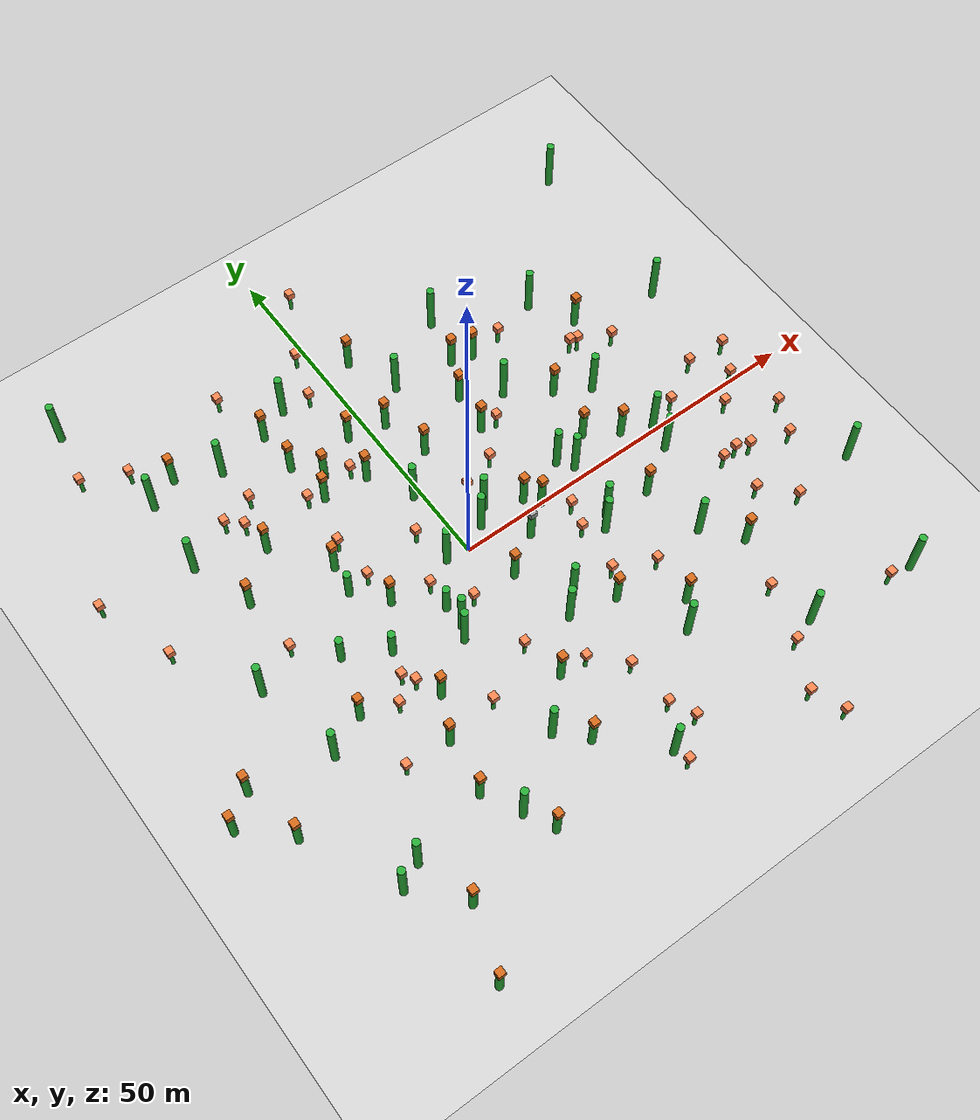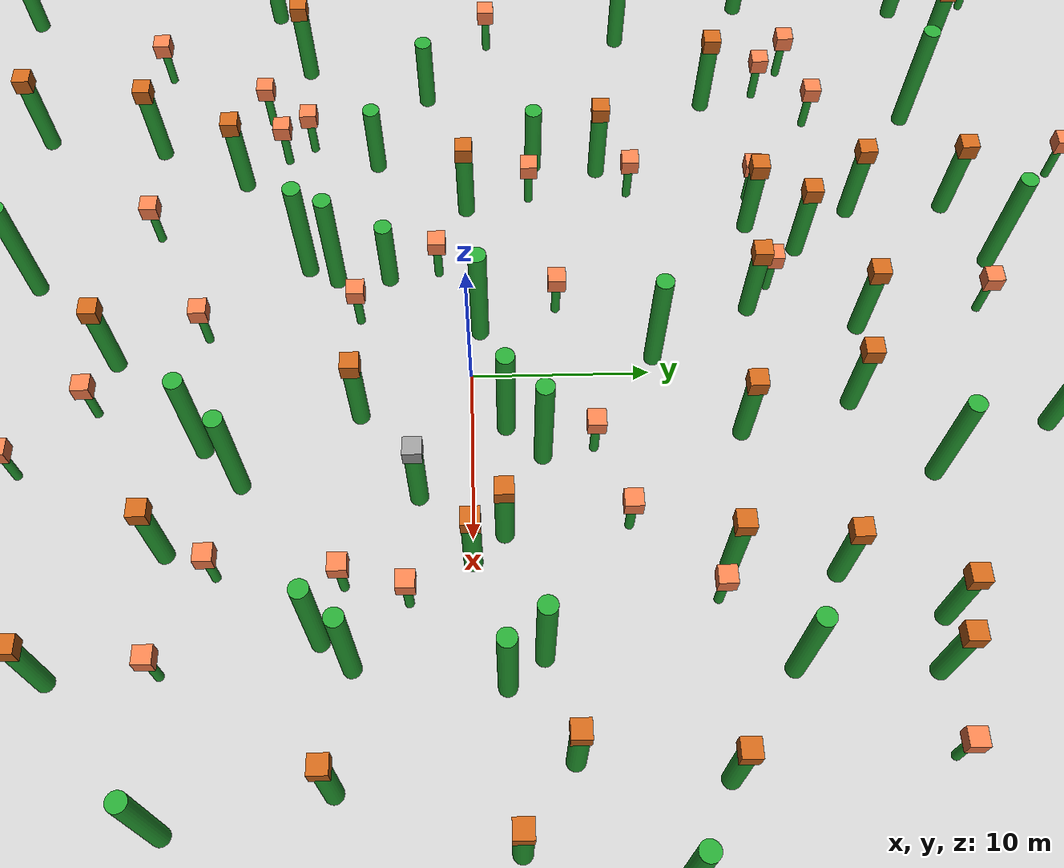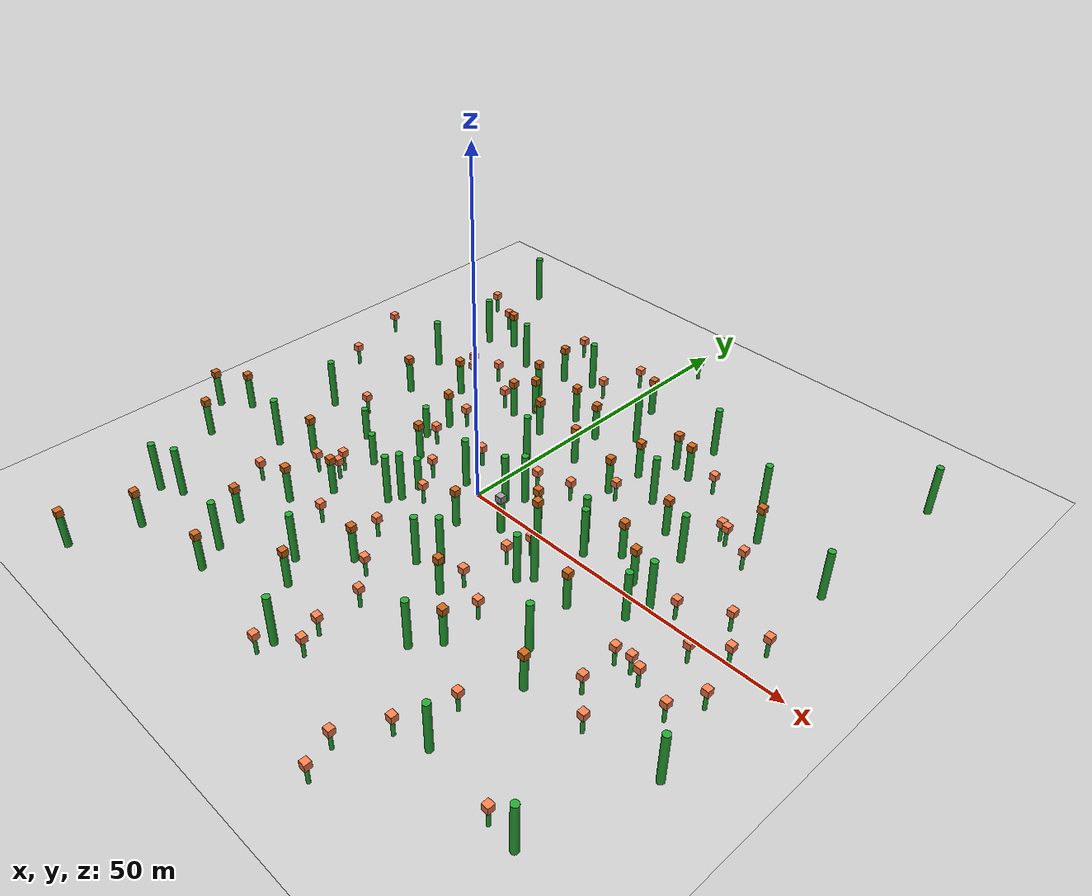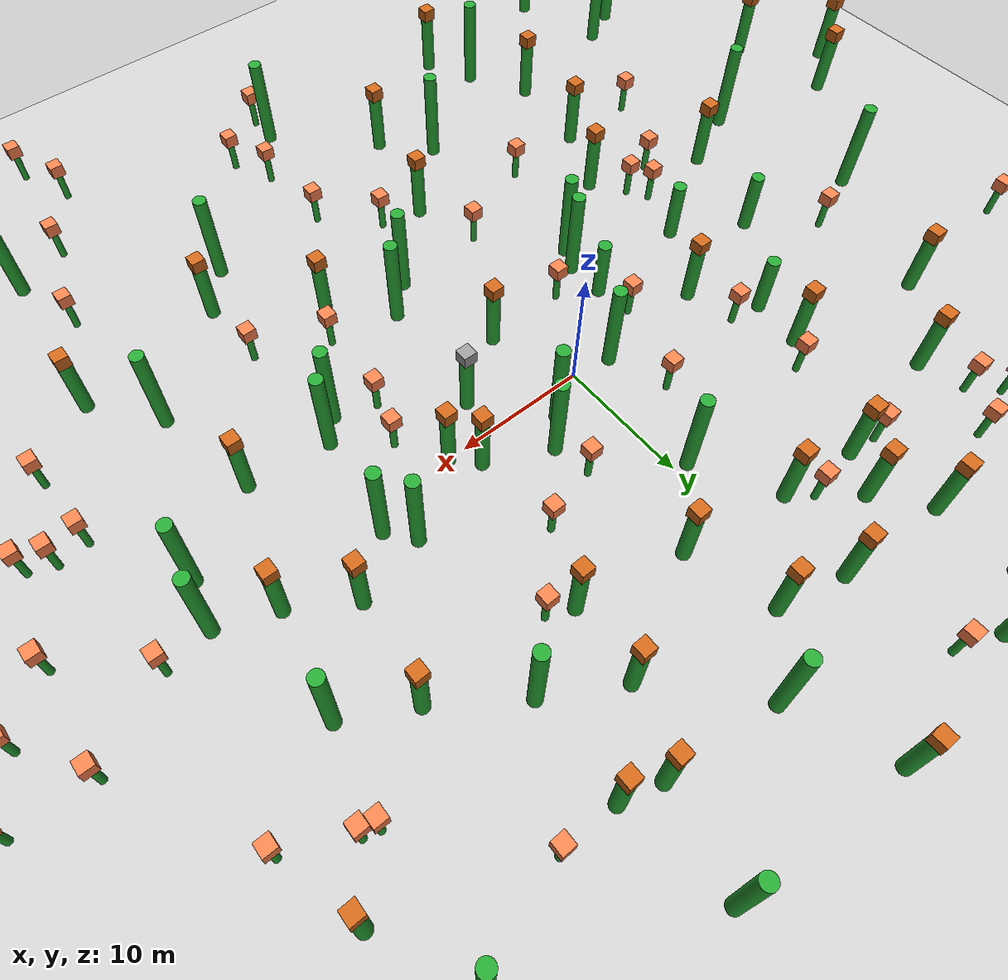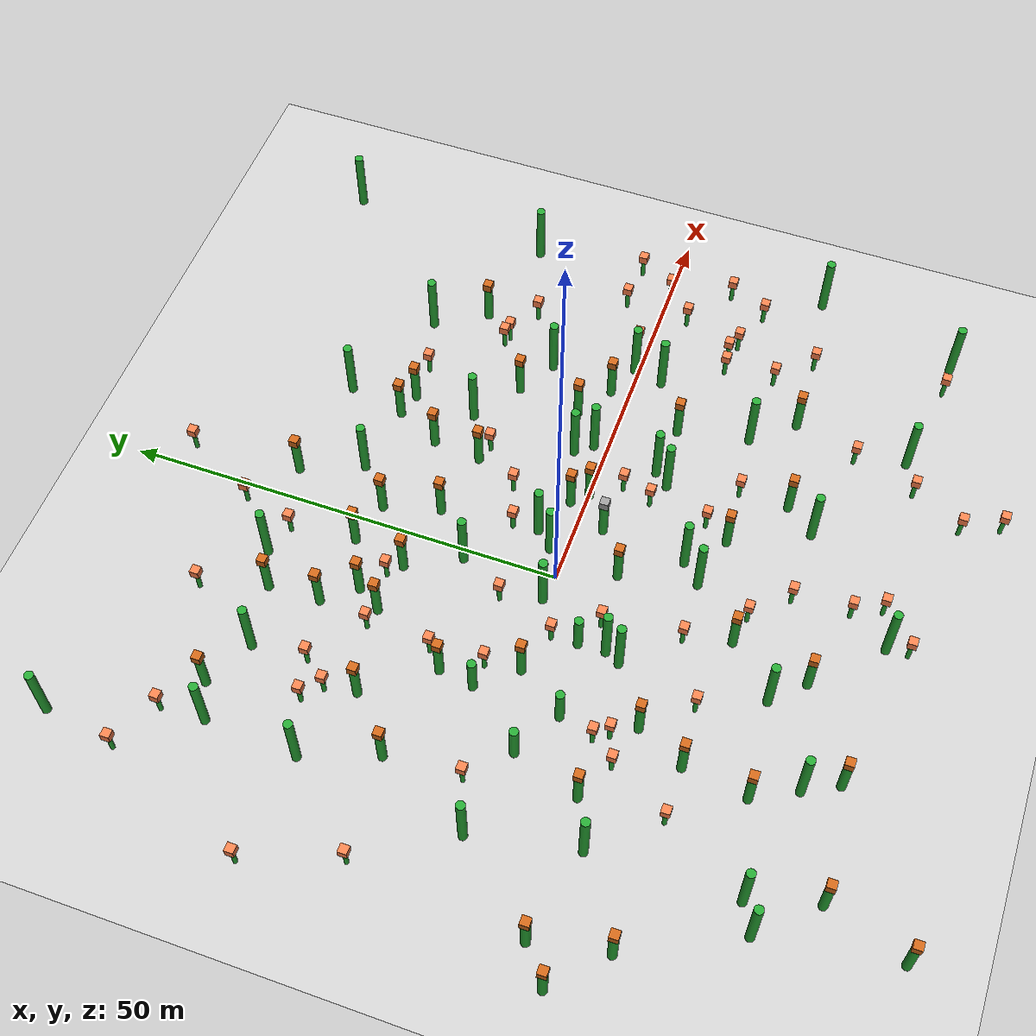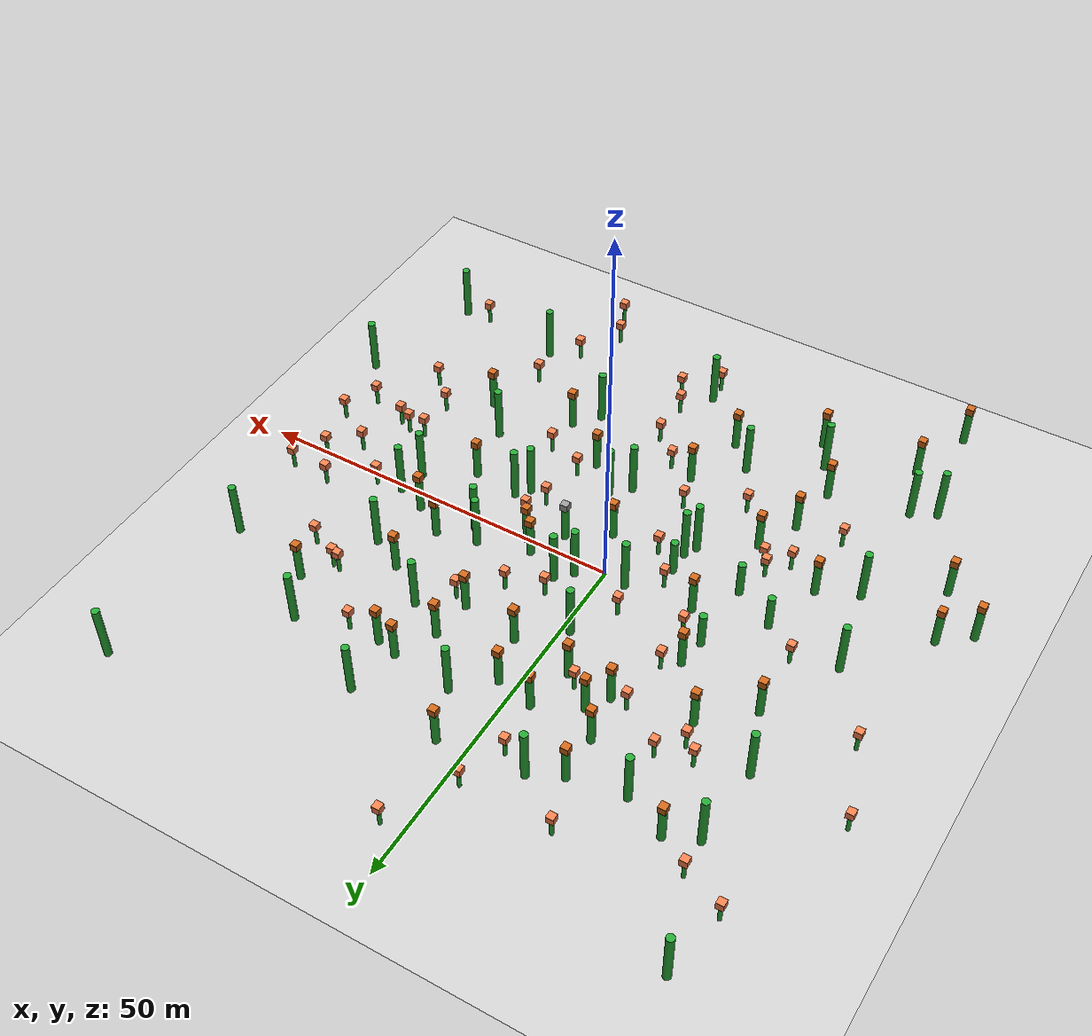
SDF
<sdf version="1.7">
 <world name="default">
  <plugin name="gazebo_ros_state" filename="libgazebo_ros_state.so">
   <ros>
    <namespace>/plug</namespace>
    <argument>model_states:=model_states_plug</argument>
    <argument>link_states:=link_states_plug</argument>
   </ros>
   <update_rate>100.0</update_rate>
  </plugin>
  <plugin name="disable_physics" filename="libdisable_physics.so"/>
  <light name="sun" type="directional">
   <pose>0 0 10 0 -0 0</pose>
   <diffuse>0.8 0.8 0.8 1</diffuse>
   <specular>0.2 0.2 0.2 1</specular>
   <attenuation>
    <range>1000</range>
    <constant>0.9</constant>
    <linear>0.01</linear>
    <quadratic>0.001</quadratic>
   </attenuation>
   <direction>-0.5 0.1 -0.9</direction>
   <spot><inner_angle>0</inner_angle><outer_angle>0</outer_angle><falloff>0</falloff></spot>
  </light>
  <model name="ground_plane">
   <static>1</static>
   <link name="link">
    <collision name="collision">
     <geometry><plane><normal>0 0 1</normal><size>100 100</size></plane></geometry>
     <surface>
      <contact><collide_bitmask>65535</collide_bitmask></contact>
      <friction><ode><mu>100</mu><mu2>50</mu2></ode></friction>
     </surface>
    </collision>
    <visual name="visual">
     <cast_shadows>0</cast_shadows>
     <geometry><plane><normal>0 0 1</normal><size>100 100</size></plane></geometry>
     <material>
      <script><uri>file://media/materials/scripts/gazebo.material</uri><name>Gazebo/Grey</name></script>
     </material>
    </visual>
   </link>
  </model>
  <gravity>0 0 -9.8</gravity>
  <magnetic_field>6e-06 2.3e-05 -4.2e-05</magnetic_field>
  <atmosphere type="adiabatic"/>
  <physics type="ode">
   <max_step_size>0.01</max_step_size>
   <real_time_factor>1</real_time_factor>
   <real_time_update_rate>100</real_time_update_rate>
  </physics>
  <scene><ambient>0.4 0.4 0.4 1</ambient><background>0.7 0.7 0.7 1</background><shadows>1</shadows></scene>
  <audio><device>default</device></audio>
  <spherical_coordinates>
   <surface_model>EARTH_WGS84</surface_model>
   <latitude_deg>0</latitude_deg>
   <longitude_deg>0</longitude_deg>
   <elevation>0</elevation>
   <heading_deg>0</heading_deg>
  </spherical_coordinates>
  <model name="unit_cylinder_green_2_clone">
   <link name="link">
    <inertial>
     <mass>1</mass>
     <inertia><ixx>0.145833</ixx><ixy>0</ixy><ixz>0</ixz><iyy>0.145833</iyy><iyz>0</iyz><izz>0.125</izz></inertia>
    </inertial>
    <visual name="visual">
     <geometry><cylinder><radius>0.5</radius><length>10</length></cylinder></geometry>
     <material>
      <script><name>Gazebo/Green</name><uri>file://media/materials/scripts/gazebo.material</uri></script>
      <shader type="pixel"><normal_map>__default__</normal_map></shader>
      <ambient>0 1 0.3 1</ambient>
      <diffuse>0.7 0.7 0.7 1</diffuse>
      <specular>0.01 0.01 0.01 1</specular>
      <emissive>0 0 0 1</emissive>
     </material>
    </visual>
    <collision name="collision">
     <geometry><cylinder><radius>0.5</radius><length>5</length></cylinder></geometry>
     <surface>
      <friction>
       <ode><mu>1</mu><mu2>1</mu2><fdir1>0 0 0</fdir1><slip1>0</slip1><slip2>0</slip2></ode>
       <torsional>
        <coefficient>1</coefficient>
        <patch_radius>0</patch_radius>
        <surface_radius>0</surface_radius>
        <use_patch_radius>1</use_patch_radius>
        <ode><slip>0</slip></ode>
       </torsional>
      </friction>
      <bounce><restitution_coefficient>0</restitution_coefficient><threshold>1e+06</threshold></bounce>
      <contact>
       <collide_without_contact>0</collide_without_contact>
       <collide_without_contact_bitmask>1</collide_without_contact_bitmask>
       <collide_bitmask>1</collide_bitmask>
       <ode>
        <soft_cfm>0</soft_cfm>
        <soft_erp>0.2</soft_erp>
        <kp>1e+13</kp>
        <kd>1</kd>
        <max_vel>0.01</max_vel>
        <min_depth>0</min_depth>
       </ode>
       <bullet>
        <split_impulse>1</split_impulse>
        <split_impulse_penetration_threshold>-0.01</split_impulse_penetration_threshold>
        <soft_cfm>0</soft_cfm>
        <soft_erp>0.2</soft_erp>
        <kp>1e+13</kp>
        <kd>1</kd>
       </bullet>
      </contact>
     </surface>
    </collision>
   </link>
   <static>1</static>
   <pose>-6.85738 -4.80035 0 0 -0 0</pose>
  </model>
  <model name="unit_cylinder_green_2_clone_0">
   <link name="link">
    <inertial>
     <mass>1</mass>
     <inertia><ixx>0.145833</ixx><ixy>0</ixy><ixz>0</ixz><iyy>0.145833</iyy><iyz>0</iyz><izz>0.125</izz></inertia>
    </inertial>
    <visual name="visual">
     <geometry><cylinder><radius>0.5</radius><length>10</length></cylinder></geometry>
     <material>
      <script><name>Gazebo/Green</name><uri>file://media/materials/scripts/gazebo.material</uri></script>
      <shader type="pixel"><normal_map>__default__</normal_map></shader>
      <ambient>0 1 0.3 1</ambient>
      <diffuse>0.7 0.7 0.7 1</diffuse>
      <specular>0.01 0.01 0.01 1</specular>
      <emissive>0 0 0 1</emissive>
     </material>
    </visual>
    <collision name="collision">
     <geometry><cylinder><radius>0.5</radius><length>5</length></cylinder></geometry>
     <surface>
      <friction>
       <ode><mu>1</mu><mu2>1</mu2><fdir1>0 0 0</fdir1><slip1>0</slip1><slip2>0</slip2></ode>
       <torsional>
        <coefficient>1</coefficient>
        <patch_radius>0</patch_radius>
        <surface_radius>0</surface_radius>
        <use_patch_radius>1</use_patch_radius>
        <ode><slip>0</slip></ode>
       </torsional>
      </friction>
      <bounce><restitution_coefficient>0</restitution_coefficient><threshold>1e+06</threshold></bounce>
      <contact>
       <collide_without_contact>0</collide_without_contact>
       <collide_without_contact_bitmask>1</collide_without_contact_bitmask>
       <collide_bitmask>1</collide_bitmask>
       <ode>
        <soft_cfm>0</soft_cfm>
        <soft_erp>0.2</soft_erp>
        <kp>1e+13</kp>
        <kd>1</kd>
        <max_vel>0.01</max_vel>
        <min_depth>0</min_depth>
       </ode>
       <bullet>
        <split_impulse>1</split_impulse>
        <split_impulse_penetration_threshold>-0.01</split_impulse_penetration_threshold>
        <soft_cfm>0</soft_cfm>
        <soft_erp>0.2</soft_erp>
        <kp>1e+13</kp>
        <kd>1</kd>
       </bullet>
      </contact>
     </surface>
    </collision>
   </link>
   <static>1</static>
   <pose>-15.5271 -5.75349 0 0 -0 0</pose>
  </model>
  <model name="unit_cylinder_green_2_clone_1">
   <link name="link">
    <inertial>
     <mass>1</mass>
     <inertia><ixx>0.145833</ixx><ixy>0</ixy><ixz>0</ixz><iyy>0.145833</iyy><iyz>0</iyz><izz>0.125</izz></inertia>
    </inertial>
    <visual name="visual">
     <geometry><cylinder><radius>0.5</radius><length>10</length></cylinder></geometry>
     <material>
      <script><name>Gazebo/Green</name><uri>file://media/materials/scripts/gazebo.material</uri></script>
      <shader type="pixel"><normal_map>__default__</normal_map></shader>
      <ambient>0 1 0.3 1</ambient>
      <diffuse>0.7 0.7 0.7 1</diffuse>
      <specular>0.01 0.01 0.01 1</specular>
      <emissive>0 0 0 1</emissive>
     </material>
    </visual>
    <collision name="collision">
     <geometry><cylinder><radius>0.5</radius><length>5</length></cylinder></geometry>
     <surface>
      <friction>
       <ode><mu>1</mu><mu2>1</mu2><fdir1>0 0 0</fdir1><slip1>0</slip1><slip2>0</slip2></ode>
       <torsional>
        <coefficient>1</coefficient>
        <patch_radius>0</patch_radius>
        <surface_radius>0</surface_radius>
        <use_patch_radius>1</use_patch_radius>
        <ode><slip>0</slip></ode>
       </torsional>
      </friction>
      <bounce><restitution_coefficient>0</restitution_coefficient><threshold>1e+06</threshold></bounce>
      <contact>
       <collide_without_contact>0</collide_without_contact>
       <collide_without_contact_bitmask>1</collide_without_contact_bitmask>
       <collide_bitmask>1</collide_bitmask>
       <ode>
        <soft_cfm>0</soft_cfm>
        <soft_erp>0.2</soft_erp>
        <kp>1e+13</kp>
        <kd>1</kd>
        <max_vel>0.01</max_vel>
        <min_depth>0</min_depth>
       </ode>
       <bullet>
        <split_impulse>1</split_impulse>
        <split_impulse_penetration_threshold>-0.01</split_impulse_penetration_threshold>
        <soft_cfm>0</soft_cfm>
        <soft_erp>0.2</soft_erp>
        <kp>1e+13</kp>
        <kd>1</kd>
       </bullet>
      </contact>
     </surface>
    </collision>
   </link>
   <static>1</static>
   <pose>-20.9276 -2.72984 0 0 -0 0</pose>
  </model>
  <model name="unit_cylinder_green_2_clone_2">
   <link name="link">
    <inertial>
     <mass>1</mass>
     <inertia><ixx>0.145833</ixx><ixy>0</ixy><ixz>0</ixz><iyy>0.145833</iyy><iyz>0</iyz><izz>0.125</izz></inertia>
    </inertial>
    <visual name="visual">
     <geometry><cylinder><radius>0.5</radius><length>10</length></cylinder></geometry>
     <material>
      <script><name>Gazebo/Green</name><uri>file://media/materials/scripts/gazebo.material</uri></script>
      <shader type="pixel"><normal_map>__default__</normal_map></shader>
      <ambient>0 1 0.3 1</ambient>
      <diffuse>0.7 0.7 0.7 1</diffuse>
      <specular>0.01 0.01 0.01 1</specular>
      <emissive>0 0 0 1</emissive>
     </material>
    </visual>
    <collision name="collision">
     <geometry><cylinder><radius>0.5</radius><length>5</length></cylinder></geometry>
     <surface>
      <friction>
       <ode><mu>1</mu><mu2>1</mu2><fdir1>0 0 0</fdir1><slip1>0</slip1><slip2>0</slip2></ode>
       <torsional>
        <coefficient>1</coefficient>
        <patch_radius>0</patch_radius>
        <surface_radius>0</surface_radius>
        <use_patch_radius>1</use_patch_radius>
        <ode><slip>0</slip></ode>
       </torsional>
      </friction>
      <bounce><restitution_coefficient>0</restitution_coefficient><threshold>1e+06</threshold></bounce>
      <contact>
       <collide_without_contact>0</collide_without_contact>
       <collide_without_contact_bitmask>1</collide_without_contact_bitmask>
       <collide_bitmask>1</collide_bitmask>
       <ode>
        <soft_cfm>0</soft_cfm>
        <soft_erp>0.2</soft_erp>
        <kp>1e+13</kp>
        <kd>1</kd>
        <max_vel>0.01</max_vel>
        <min_depth>0</min_depth>
       </ode>
       <bullet>
        <split_impulse>1</split_impulse>
        <split_impulse_penetration_threshold>-0.01</split_impulse_penetration_threshold>
        <soft_cfm>0</soft_cfm>
        <soft_erp>0.2</soft_erp>
        <kp>1e+13</kp>
        <kd>1</kd>
       </bullet>
      </contact>
     </surface>
    </collision>
   </link>
   <static>1</static>
   <pose>-15.2558 3.89139 0 0 -0 0</pose>
  </model>
  <model name="unit_cylinder_green_2_clone_clone_2">
   <link name="link">
    <inertial>
     <mass>1</mass>
     <inertia><ixx>0.145833</ixx><ixy>0</ixy><ixz>0</ixz><iyy>0.145833</iyy><iyz>0</iyz><izz>0.125</izz></inertia>
    </inertial>
    <visual name="visual">
     <geometry><cylinder><radius>0.5</radius><length>10</length></cylinder></geometry>
     <material>
      <script><name>Gazebo/Green</name><uri>file://media/materials/scripts/gazebo.material</uri></script>
      <shader type="pixel"><normal_map>__default__</normal_map></shader>
      <ambient>0 1 0.3 1</ambient>
      <diffuse>0.7 0.7 0.7 1</diffuse>
      <specular>0.01 0.01 0.01 1</specular>
      <emissive>0 0 0 1</emissive>
     </material>
    </visual>
    <collision name="collision">
     <geometry><cylinder><radius>0.5</radius><length>5</length></cylinder></geometry>
     <surface>
      <friction>
       <ode><mu>1</mu><mu2>1</mu2><fdir1>0 0 0</fdir1><slip1>0</slip1><slip2>0</slip2></ode>
       <torsional>
        <coefficient>1</coefficient>
        <patch_radius>0</patch_radius>
        <surface_radius>0</surface_radius>
        <use_patch_radius>1</use_patch_radius>
        <ode><slip>0</slip></ode>
       </torsional>
      </friction>
      <bounce><restitution_coefficient>0</restitution_coefficient><threshold>1e+06</threshold></bounce>
      <contact>
       <collide_without_contact>0</collide_without_contact>
       <collide_without_contact_bitmask>1</collide_without_contact_bitmask>
       <collide_bitmask>1</collide_bitmask>
       <ode>
        <soft_cfm>0</soft_cfm>
        <soft_erp>0.2</soft_erp>
        <kp>1e+13</kp>
        <kd>1</kd>
        <max_vel>0.01</max_vel>
        <min_depth>0</min_depth>
       </ode>
       <bullet>
        <split_impulse>1</split_impulse>
        <split_impulse_penetration_threshold>-0.01</split_impulse_penetration_threshold>
        <soft_cfm>0</soft_cfm>
        <soft_erp>0.2</soft_erp>
        <kp>1e+13</kp>
        <kd>1</kd>
       </bullet>
      </contact>
     </surface>
    </collision>
   </link>
   <static>1</static>
   <pose>-1.02596 10.3095 2.5 0 0 -0.000967</pose>
  </model>
  <model name="unit_cylinder_green_2_clone_clone_3">
   <link name="link">
    <inertial>
     <mass>1</mass>
     <inertia><ixx>0.145833</ixx><ixy>0</ixy><ixz>0</ixz><iyy>0.145833</iyy><iyz>0</iyz><izz>0.125</izz></inertia>
    </inertial>
    <visual name="visual">
     <geometry><cylinder><radius>0.5</radius><length>10</length></cylinder></geometry>
     <material>
      <script><name>Gazebo/Green</name><uri>file://media/materials/scripts/gazebo.material</uri></script>
      <shader type="pixel"><normal_map>__default__</normal_map></shader>
      <ambient>0 1 0.3 1</ambient>
      <diffuse>0.7 0.7 0.7 1</diffuse>
      <specular>0.01 0.01 0.01 1</specular>
      <emissive>0 0 0 1</emissive>
     </material>
    </visual>
    <collision name="collision">
     <geometry><cylinder><radius>0.5</radius><length>5</length></cylinder></geometry>
     <surface>
      <friction>
       <ode><mu>1</mu><mu2>1</mu2><fdir1>0 0 0</fdir1><slip1>0</slip1><slip2>0</slip2></ode>
       <torsional>
        <coefficient>1</coefficient>
        <patch_radius>0</patch_radius>
        <surface_radius>0</surface_radius>
        <use_patch_radius>1</use_patch_radius>
        <ode><slip>0</slip></ode>
       </torsional>
      </friction>
      <bounce><restitution_coefficient>0</restitution_coefficient><threshold>1e+06</threshold></bounce>
      <contact>
       <collide_without_contact>0</collide_without_contact>
       <collide_without_contact_bitmask>1</collide_without_contact_bitmask>
       <collide_bitmask>1</collide_bitmask>
       <ode>
        <soft_cfm>0</soft_cfm>
        <soft_erp>0.2</soft_erp>
        <kp>1e+13</kp>
        <kd>1</kd>
        <max_vel>0.01</max_vel>
        <min_depth>0</min_depth>
       </ode>
       <bullet>
        <split_impulse>1</split_impulse>
        <split_impulse_penetration_threshold>-0.01</split_impulse_penetration_threshold>
        <soft_cfm>0</soft_cfm>
        <soft_erp>0.2</soft_erp>
        <kp>1e+13</kp>
        <kd>1</kd>
       </bullet>
      </contact>
     </surface>
    </collision>
   </link>
   <static>1</static>
   <pose>-2.96619 0.500277 2.5 0 0 -0.000967</pose>
  </model>
  <model name="unit_cylinder_green_2_clone_clone_7">
   <link name="link">
    <inertial>
     <mass>1</mass>
     <inertia><ixx>0.145833</ixx><ixy>0</ixy><ixz>0</ixz><iyy>0.145833</iyy><iyz>0</iyz><izz>0.125</izz></inertia>
    </inertial>
    <visual name="visual">
     <geometry><cylinder><radius>0.5</radius><length>10</length></cylinder></geometry>
     <material>
      <script><name>Gazebo/Green</name><uri>file://media/materials/scripts/gazebo.material</uri></script>
      <shader type="pixel"><normal_map>__default__</normal_map></shader>
      <ambient>0 1 0.3 1</ambient>
      <diffuse>0.7 0.7 0.7 1</diffuse>
      <specular>0.01 0.01 0.01 1</specular>
      <emissive>0 0 0 1</emissive>
     </material>
    </visual>
    <collision name="collision">
     <geometry><cylinder><radius>0.5</radius><length>5</length></cylinder></geometry>
     <surface>
      <friction>
       <ode><mu>1</mu><mu2>1</mu2><fdir1>0 0 0</fdir1><slip1>0</slip1><slip2>0</slip2></ode>
       <torsional>
        <coefficient>1</coefficient>
        <patch_radius>0</patch_radius>
        <surface_radius>0</surface_radius>
        <use_patch_radius>1</use_patch_radius>
        <ode><slip>0</slip></ode>
       </torsional>
      </friction>
      <bounce><restitution_coefficient>0</restitution_coefficient><threshold>1e+06</threshold></bounce>
      <contact>
       <collide_without_contact>0</collide_without_contact>
       <collide_without_contact_bitmask>1</collide_without_contact_bitmask>
       <collide_bitmask>1</collide_bitmask>
       <ode>
        <soft_cfm>0</soft_cfm>
        <soft_erp>0.2</soft_erp>
        <kp>1e+13</kp>
        <kd>1</kd>
        <max_vel>0.01</max_vel>
        <min_depth>0</min_depth>
       </ode>
       <bullet>
        <split_impulse>1</split_impulse>
        <split_impulse_penetration_threshold>-0.01</split_impulse_penetration_threshold>
        <soft_cfm>0</soft_cfm>
        <soft_erp>0.2</soft_erp>
        <kp>1e+13</kp>
        <kd>1</kd>
       </bullet>
      </contact>
     </surface>
    </collision>
   </link>
   <static>1</static>
   <pose>-31 -1 2.5 0 0 -0.000967</pose>
  </model>
  <model name="unit_cylinder_green_2_clone_clone_8">
   <link name="link">
    <inertial>
     <mass>1</mass>
     <inertia><ixx>0.145833</ixx><ixy>0</ixy><ixz>0</ixz><iyy>0.145833</iyy><iyz>0</iyz><izz>0.125</izz></inertia>
    </inertial>
    <visual name="visual">
     <geometry><cylinder><radius>0.5</radius><length>10</length></cylinder></geometry>
     <material>
      <script><name>Gazebo/Green</name><uri>file://media/materials/scripts/gazebo.material</uri></script>
      <shader type="pixel"><normal_map>__default__</normal_map></shader>
      <ambient>0 1 0.3 1</ambient>
      <diffuse>0.7 0.7 0.7 1</diffuse>
      <specular>0.01 0.01 0.01 1</specular>
      <emissive>0 0 0 1</emissive>
     </material>
    </visual>
    <collision name="collision">
     <geometry><cylinder><radius>0.5</radius><length>5</length></cylinder></geometry>
     <surface>
      <friction>
       <ode><mu>1</mu><mu2>1</mu2><fdir1>0 0 0</fdir1><slip1>0</slip1><slip2>0</slip2></ode>
       <torsional>
        <coefficient>1</coefficient>
        <patch_radius>0</patch_radius>
        <surface_radius>0</surface_radius>
        <use_patch_radius>1</use_patch_radius>
        <ode><slip>0</slip></ode>
       </torsional>
      </friction>
      <bounce><restitution_coefficient>0</restitution_coefficient><threshold>1e+06</threshold></bounce>
      <contact>
       <collide_without_contact>0</collide_without_contact>
       <collide_without_contact_bitmask>1</collide_without_contact_bitmask>
       <collide_bitmask>1</collide_bitmask>
       <ode>
        <soft_cfm>0</soft_cfm>
        <soft_erp>0.2</soft_erp>
        <kp>1e+13</kp>
        <kd>1</kd>
        <max_vel>0.01</max_vel>
        <min_depth>0</min_depth>
       </ode>
       <bullet>
        <split_impulse>1</split_impulse>
        <split_impulse_penetration_threshold>-0.01</split_impulse_penetration_threshold>
        <soft_cfm>0</soft_cfm>
        <soft_erp>0.2</soft_erp>
        <kp>1e+13</kp>
        <kd>1</kd>
       </bullet>
      </contact>
     </surface>
    </collision>
   </link>
   <static>1</static>
   <pose>-28.7386 17.9151 2.5 0 0 -0.000967</pose>
  </model>
  <model name="unit_cylinder_green_2_clone_clone_9">
   <link name="link">
    <inertial>
     <mass>1</mass>
     <inertia><ixx>0.145833</ixx><ixy>0</ixy><ixz>0</ixz><iyy>0.145833</iyy><iyz>0</iyz><izz>0.125</izz></inertia>
    </inertial>
    <visual name="visual">
     <geometry><cylinder><radius>0.5</radius><length>10</length></cylinder></geometry>
     <material>
      <script><name>Gazebo/Green</name><uri>file://media/materials/scripts/gazebo.material</uri></script>
      <shader type="pixel"><normal_map>__default__</normal_map></shader>
      <ambient>0 1 0.3 1</ambient>
      <diffuse>0.7 0.7 0.7 1</diffuse>
      <specular>0.01 0.01 0.01 1</specular>
      <emissive>0 0 0 1</emissive>
     </material>
    </visual>
    <collision name="collision">
     <geometry><cylinder><radius>0.5</radius><length>5</length></cylinder></geometry>
     <surface>
      <friction>
       <ode><mu>1</mu><mu2>1</mu2><fdir1>0 0 0</fdir1><slip1>0</slip1><slip2>0</slip2></ode>
       <torsional>
        <coefficient>1</coefficient>
        <patch_radius>0</patch_radius>
        <surface_radius>0</surface_radius>
        <use_patch_radius>1</use_patch_radius>
        <ode><slip>0</slip></ode>
       </torsional>
      </friction>
      <bounce><restitution_coefficient>0</restitution_coefficient><threshold>1e+06</threshold></bounce>
      <contact>
       <collide_without_contact>0</collide_without_contact>
       <collide_without_contact_bitmask>1</collide_without_contact_bitmask>
       <collide_bitmask>1</collide_bitmask>
       <ode>
        <soft_cfm>0</soft_cfm>
        <soft_erp>0.2</soft_erp>
        <kp>1e+13</kp>
        <kd>1</kd>
        <max_vel>0.01</max_vel>
        <min_depth>0</min_depth>
       </ode>
       <bullet>
        <split_impulse>1</split_impulse>
        <split_impulse_penetration_threshold>-0.01</split_impulse_penetration_threshold>
        <soft_cfm>0</soft_cfm>
        <soft_erp>0.2</soft_erp>
        <kp>1e+13</kp>
        <kd>1</kd>
       </bullet>
      </contact>
     </surface>
    </collision>
   </link>
   <static>1</static>
   <pose>-18.5936 27.5593 2.5 0 0 -0.000967</pose>
  </model>
  <model name="unit_cylinder_green_2_clone_clone_10">
   <link name="link">
    <inertial>
     <mass>1</mass>
     <inertia><ixx>0.145833</ixx><ixy>0</ixy><ixz>0</ixz><iyy>0.145833</iyy><iyz>0</iyz><izz>0.125</izz></inertia>
    </inertial>
    <visual name="visual">
     <geometry><cylinder><radius>0.5</radius><length>10</length></cylinder></geometry>
     <material>
      <script><name>Gazebo/Green</name><uri>file://media/materials/scripts/gazebo.material</uri></script>
      <shader type="pixel"><normal_map>__default__</normal_map></shader>
      <ambient>0 1 0.3 1</ambient>
      <diffuse>0.7 0.7 0.7 1</diffuse>
      <specular>0.01 0.01 0.01 1</specular>
      <emissive>0 0 0 1</emissive>
     </material>
    </visual>
    <collision name="collision">
     <geometry><cylinder><radius>0.5</radius><length>5</length></cylinder></geometry>
     <surface>
      <friction>
       <ode><mu>1</mu><mu2>1</mu2><fdir1>0 0 0</fdir1><slip1>0</slip1><slip2>0</slip2></ode>
       <torsional>
        <coefficient>1</coefficient>
        <patch_radius>0</patch_radius>
        <surface_radius>0</surface_radius>
        <use_patch_radius>1</use_patch_radius>
        <ode><slip>0</slip></ode>
       </torsional>
      </friction>
      <bounce><restitution_coefficient>0</restitution_coefficient><threshold>1e+06</threshold></bounce>
      <contact>
       <collide_without_contact>0</collide_without_contact>
       <collide_without_contact_bitmask>1</collide_without_contact_bitmask>
       <collide_bitmask>1</collide_bitmask>
       <ode>
        <soft_cfm>0</soft_cfm>
        <soft_erp>0.2</soft_erp>
        <kp>1e+13</kp>
        <kd>1</kd>
        <max_vel>0.01</max_vel>
        <min_depth>0</min_depth>
       </ode>
       <bullet>
        <split_impulse>1</split_impulse>
        <split_impulse_penetration_threshold>-0.01</split_impulse_penetration_threshold>
        <soft_cfm>0</soft_cfm>
        <soft_erp>0.2</soft_erp>
        <kp>1e+13</kp>
        <kd>1</kd>
       </bullet>
      </contact>
     </surface>
    </collision>
   </link>
   <static>1</static>
   <pose>-7.30814 30.7862 2.5 0 0 -0.000967</pose>
  </model>
  <model name="unit_cylinder_green_2_clone_clone_11">
   <link name="link">
    <inertial>
     <mass>1</mass>
     <inertia><ixx>0.145833</ixx><ixy>0</ixy><ixz>0</ixz><iyy>0.145833</iyy><iyz>0</iyz><izz>0.125</izz></inertia>
    </inertial>
    <visual name="visual">
     <geometry><cylinder><radius>0.5</radius><length>10</length></cylinder></geometry>
     <material>
      <script><name>Gazebo/Green</name><uri>file://media/materials/scripts/gazebo.material</uri></script>
      <shader type="pixel"><normal_map>__default__</normal_map></shader>
      <ambient>0 1 0.3 1</ambient>
      <diffuse>0.7 0.7 0.7 1</diffuse>
      <specular>0.01 0.01 0.01 1</specular>
      <emissive>0 0 0 1</emissive>
     </material>
    </visual>
    <collision name="collision">
     <geometry><cylinder><radius>0.5</radius><length>5</length></cylinder></geometry>
     <surface>
      <friction>
       <ode><mu>1</mu><mu2>1</mu2><fdir1>0 0 0</fdir1><slip1>0</slip1><slip2>0</slip2></ode>
       <torsional>
        <coefficient>1</coefficient>
        <patch_radius>0</patch_radius>
        <surface_radius>0</surface_radius>
        <use_patch_radius>1</use_patch_radius>
        <ode><slip>0</slip></ode>
       </torsional>
      </friction>
      <bounce><restitution_coefficient>0</restitution_coefficient><threshold>1e+06</threshold></bounce>
      <contact>
       <collide_without_contact>0</collide_without_contact>
       <collide_without_contact_bitmask>1</collide_without_contact_bitmask>
       <collide_bitmask>1</collide_bitmask>
       <ode>
        <soft_cfm>0</soft_cfm>
        <soft_erp>0.2</soft_erp>
        <kp>1e+13</kp>
        <kd>1</kd>
        <max_vel>0.01</max_vel>
        <min_depth>0</min_depth>
       </ode>
       <bullet>
        <split_impulse>1</split_impulse>
        <split_impulse_penetration_threshold>-0.01</split_impulse_penetration_threshold>
        <soft_cfm>0</soft_cfm>
        <soft_erp>0.2</soft_erp>
        <kp>1e+13</kp>
        <kd>1</kd>
       </bullet>
      </contact>
     </surface>
    </collision>
   </link>
   <static>1</static>
   <pose>6.6281 25.0703 2.5 0 0 -0.000967</pose>
  </model>
  <model name="unit_cylinder_green_2_clone_clone_13">
   <link name="link">
    <inertial>
     <mass>1</mass>
     <inertia><ixx>0.145833</ixx><ixy>0</ixy><ixz>0</ixz><iyy>0.145833</iyy><iyz>0</iyz><izz>0.125</izz></inertia>
    </inertial>
    <visual name="visual">
     <geometry><cylinder><radius>0.5</radius><length>10</length></cylinder></geometry>
     <material>
      <script><name>Gazebo/Green</name><uri>file://media/materials/scripts/gazebo.material</uri></script>
      <shader type="pixel"><normal_map>__default__</normal_map></shader>
      <ambient>0 1 0.3 1</ambient>
      <diffuse>0.7 0.7 0.7 1</diffuse>
      <specular>0.01 0.01 0.01 1</specular>
      <emissive>0 0 0 1</emissive>
     </material>
    </visual>
    <collision name="collision">
     <geometry><cylinder><radius>0.5</radius><length>5</length></cylinder></geometry>
     <surface>
      <friction>
       <ode><mu>1</mu><mu2>1</mu2><fdir1>0 0 0</fdir1><slip1>0</slip1><slip2>0</slip2></ode>
       <torsional>
        <coefficient>1</coefficient>
        <patch_radius>0</patch_radius>
        <surface_radius>0</surface_radius>
        <use_patch_radius>1</use_patch_radius>
        <ode><slip>0</slip></ode>
       </torsional>
      </friction>
      <bounce><restitution_coefficient>0</restitution_coefficient><threshold>1e+06</threshold></bounce>
      <contact>
       <collide_without_contact>0</collide_without_contact>
       <collide_without_contact_bitmask>1</collide_without_contact_bitmask>
       <collide_bitmask>1</collide_bitmask>
       <ode>
        <soft_cfm>0</soft_cfm>
        <soft_erp>0.2</soft_erp>
        <kp>1e+13</kp>
        <kd>1</kd>
        <max_vel>0.01</max_vel>
        <min_depth>0</min_depth>
       </ode>
       <bullet>
        <split_impulse>1</split_impulse>
        <split_impulse_penetration_threshold>-0.01</split_impulse_penetration_threshold>
        <soft_cfm>0</soft_cfm>
        <soft_erp>0.2</soft_erp>
        <kp>1e+13</kp>
        <kd>1</kd>
       </bullet>
      </contact>
     </surface>
    </collision>
   </link>
   <static>1</static>
   <pose>-28.5894 -12.7369 2.5 0 0 -0.000967</pose>
  </model>
  <model name="unit_cylinder_green_2_clone_clone_14">
   <link name="link">
    <inertial>
     <mass>1</mass>
     <inertia><ixx>0.145833</ixx><ixy>0</ixy><ixz>0</ixz><iyy>0.145833</iyy><iyz>0</iyz><izz>0.125</izz></inertia>
    </inertial>
    <visual name="visual">
     <geometry><cylinder><radius>0.5</radius><length>10</length></cylinder></geometry>
     <material>
      <script><name>Gazebo/Green</name><uri>file://media/materials/scripts/gazebo.material</uri></script>
      <shader type="pixel"><normal_map>__default__</normal_map></shader>
      <ambient>0 1 0.3 1</ambient>
      <diffuse>0.7 0.7 0.7 1</diffuse>
      <specular>0.01 0.01 0.01 1</specular>
      <emissive>0 0 0 1</emissive>
     </material>
    </visual>
    <collision name="collision">
     <geometry><cylinder><radius>0.5</radius><length>5</length></cylinder></geometry>
     <surface>
      <friction>
       <ode><mu>1</mu><mu2>1</mu2><fdir1>0 0 0</fdir1><slip1>0</slip1><slip2>0</slip2></ode>
       <torsional>
        <coefficient>1</coefficient>
        <patch_radius>0</patch_radius>
        <surface_radius>0</surface_radius>
        <use_patch_radius>1</use_patch_radius>
        <ode><slip>0</slip></ode>
       </torsional>
      </friction>
      <bounce><restitution_coefficient>0</restitution_coefficient><threshold>1e+06</threshold></bounce>
      <contact>
       <collide_without_contact>0</collide_without_contact>
       <collide_without_contact_bitmask>1</collide_without_contact_bitmask>
       <collide_bitmask>1</collide_bitmask>
       <ode>
        <soft_cfm>0</soft_cfm>
        <soft_erp>0.2</soft_erp>
        <kp>1e+13</kp>
        <kd>1</kd>
        <max_vel>0.01</max_vel>
        <min_depth>0</min_depth>
       </ode>
       <bullet>
        <split_impulse>1</split_impulse>
        <split_impulse_penetration_threshold>-0.01</split_impulse_penetration_threshold>
        <soft_cfm>0</soft_cfm>
        <soft_erp>0.2</soft_erp>
        <kp>1e+13</kp>
        <kd>1</kd>
       </bullet>
      </contact>
     </surface>
    </collision>
   </link>
   <static>1</static>
   <pose>-28.1415 28.4335 2.5 0 0 -0.000967</pose>
  </model>
  <model name="unit_cylinder_green_2_clone_clone_15">
   <link name="link">
    <inertial>
     <mass>1</mass>
     <inertia><ixx>0.145833</ixx><ixy>0</ixy><ixz>0</ixz><iyy>0.145833</iyy><iyz>0</iyz><izz>0.125</izz></inertia>
    </inertial>
    <visual name="visual">
     <geometry><cylinder><radius>0.5</radius><length>10</length></cylinder></geometry>
     <material>
      <script><name>Gazebo/Green</name><uri>file://media/materials/scripts/gazebo.material</uri></script>
      <shader type="pixel"><normal_map>__default__</normal_map></shader>
      <ambient>0 1 0.3 1</ambient>
      <diffuse>0.7 0.7 0.7 1</diffuse>
      <specular>0.01 0.01 0.01 1</specular>
      <emissive>0 0 0 1</emissive>
     </material>
    </visual>
    <collision name="collision">
     <geometry><cylinder><radius>0.5</radius><length>5</length></cylinder></geometry>
     <surface>
      <friction>
       <ode><mu>1</mu><mu2>1</mu2><fdir1>0 0 0</fdir1><slip1>0</slip1><slip2>0</slip2></ode>
       <torsional>
        <coefficient>1</coefficient>
        <patch_radius>0</patch_radius>
        <surface_radius>0</surface_radius>
        <use_patch_radius>1</use_patch_radius>
        <ode><slip>0</slip></ode>
       </torsional>
      </friction>
      <bounce><restitution_coefficient>0</restitution_coefficient><threshold>1e+06</threshold></bounce>
      <contact>
       <collide_without_contact>0</collide_without_contact>
       <collide_without_contact_bitmask>1</collide_without_contact_bitmask>
       <collide_bitmask>1</collide_bitmask>
       <ode>
        <soft_cfm>0</soft_cfm>
        <soft_erp>0.2</soft_erp>
        <kp>1e+13</kp>
        <kd>1</kd>
        <max_vel>0.01</max_vel>
        <min_depth>0</min_depth>
       </ode>
       <bullet>
        <split_impulse>1</split_impulse>
        <split_impulse_penetration_threshold>-0.01</split_impulse_penetration_threshold>
        <soft_cfm>0</soft_cfm>
        <soft_erp>0.2</soft_erp>
        <kp>1e+13</kp>
        <kd>1</kd>
       </bullet>
      </contact>
     </surface>
    </collision>
   </link>
   <static>1</static>
   <pose>4.37271 -14.6733 2.5 0 0 -0.000967</pose>
  </model>
  <model name="unit_cylinder_green_2_clone_clone_16">
   <link name="link">
    <inertial>
     <mass>1</mass>
     <inertia><ixx>0.145833</ixx><ixy>0</ixy><ixz>0</ixz><iyy>0.145833</iyy><iyz>0</iyz><izz>0.125</izz></inertia>
    </inertial>
    <visual name="visual">
     <geometry><cylinder><radius>0.5</radius><length>10</length></cylinder></geometry>
     <material>
      <script><name>Gazebo/Green</name><uri>file://media/materials/scripts/gazebo.material</uri></script>
      <shader type="pixel"><normal_map>__default__</normal_map></shader>
      <ambient>0 1 0.3 1</ambient>
      <diffuse>0.7 0.7 0.7 1</diffuse>
      <specular>0.01 0.01 0.01 1</specular>
      <emissive>0 0 0 1</emissive>
     </material>
    </visual>
    <collision name="collision">
     <geometry><cylinder><radius>0.5</radius><length>5</length></cylinder></geometry>
     <surface>
      <friction>
       <ode><mu>1</mu><mu2>1</mu2><fdir1>0 0 0</fdir1><slip1>0</slip1><slip2>0</slip2></ode>
       <torsional>
        <coefficient>1</coefficient>
        <patch_radius>0</patch_radius>
        <surface_radius>0</surface_radius>
        <use_patch_radius>1</use_patch_radius>
        <ode><slip>0</slip></ode>
       </torsional>
      </friction>
      <bounce><restitution_coefficient>0</restitution_coefficient><threshold>1e+06</threshold></bounce>
      <contact>
       <collide_without_contact>0</collide_without_contact>
       <collide_without_contact_bitmask>1</collide_without_contact_bitmask>
       <collide_bitmask>1</collide_bitmask>
       <ode>
        <soft_cfm>0</soft_cfm>
        <soft_erp>0.2</soft_erp>
        <kp>1e+13</kp>
        <kd>1</kd>
        <max_vel>0.01</max_vel>
        <min_depth>0</min_depth>
       </ode>
       <bullet>
        <split_impulse>1</split_impulse>
        <split_impulse_penetration_threshold>-0.01</split_impulse_penetration_threshold>
        <soft_cfm>0</soft_cfm>
        <soft_erp>0.2</soft_erp>
        <kp>1e+13</kp>
        <kd>1</kd>
       </bullet>
      </contact>
     </surface>
    </collision>
   </link>
   <static>1</static>
   <pose>15.4924 -7.74923 2.5 0 0 -0.000967</pose>
  </model>
  <model name="unit_cylinder_green_2_clone_clone_17">
   <link name="link">
    <inertial>
     <mass>1</mass>
     <inertia><ixx>0.145833</ixx><ixy>0</ixy><ixz>0</ixz><iyy>0.145833</iyy><iyz>0</iyz><izz>0.125</izz></inertia>
    </inertial>
    <visual name="visual">
     <geometry><cylinder><radius>0.5</radius><length>10</length></cylinder></geometry>
     <material>
      <script><name>Gazebo/Green</name><uri>file://media/materials/scripts/gazebo.material</uri></script>
      <shader type="pixel"><normal_map>__default__</normal_map></shader>
      <ambient>0 1 0.3 1</ambient>
      <diffuse>0.7 0.7 0.7 1</diffuse>
      <specular>0.01 0.01 0.01 1</specular>
      <emissive>0 0 0 1</emissive>
     </material>
    </visual>
    <collision name="collision">
     <geometry><cylinder><radius>0.5</radius><length>5</length></cylinder></geometry>
     <surface>
      <friction>
       <ode><mu>1</mu><mu2>1</mu2><fdir1>0 0 0</fdir1><slip1>0</slip1><slip2>0</slip2></ode>
       <torsional>
        <coefficient>1</coefficient>
        <patch_radius>0</patch_radius>
        <surface_radius>0</surface_radius>
        <use_patch_radius>1</use_patch_radius>
        <ode><slip>0</slip></ode>
       </torsional>
      </friction>
      <bounce><restitution_coefficient>0</restitution_coefficient><threshold>1e+06</threshold></bounce>
      <contact>
       <collide_without_contact>0</collide_without_contact>
       <collide_without_contact_bitmask>1</collide_without_contact_bitmask>
       <collide_bitmask>1</collide_bitmask>
       <ode>
        <soft_cfm>0</soft_cfm>
        <soft_erp>0.2</soft_erp>
        <kp>1e+13</kp>
        <kd>1</kd>
        <max_vel>0.01</max_vel>
        <min_depth>0</min_depth>
       </ode>
       <bullet>
        <split_impulse>1</split_impulse>
        <split_impulse_penetration_threshold>-0.01</split_impulse_penetration_threshold>
        <soft_cfm>0</soft_cfm>
        <soft_erp>0.2</soft_erp>
        <kp>1e+13</kp>
        <kd>1</kd>
       </bullet>
      </contact>
     </surface>
    </collision>
   </link>
   <static>1</static>
   <pose>16.5379 3.56067 2.5 0 0 -0.000967</pose>
  </model>
  <model name="unit_cylinder_green_2_clone_clone_18">
   <link name="link">
    <inertial>
     <mass>1</mass>
     <inertia><ixx>0.145833</ixx><ixy>0</ixy><ixz>0</ixz><iyy>0.145833</iyy><iyz>0</iyz><izz>0.125</izz></inertia>
    </inertial>
    <visual name="visual">
     <geometry><cylinder><radius>0.5</radius><length>10</length></cylinder></geometry>
     <material>
      <script><name>Gazebo/Green</name><uri>file://media/materials/scripts/gazebo.material</uri></script>
      <shader type="pixel"><normal_map>__default__</normal_map></shader>
      <ambient>0 1 0.3 1</ambient>
      <diffuse>0.7 0.7 0.7 1</diffuse>
      <specular>0.01 0.01 0.01 1</specular>
      <emissive>0 0 0 1</emissive>
     </material>
    </visual>
    <collision name="collision">
     <geometry><cylinder><radius>0.5</radius><length>5</length></cylinder></geometry>
     <surface>
      <friction>
       <ode><mu>1</mu><mu2>1</mu2><fdir1>0 0 0</fdir1><slip1>0</slip1><slip2>0</slip2></ode>
       <torsional>
        <coefficient>1</coefficient>
        <patch_radius>0</patch_radius>
        <surface_radius>0</surface_radius>
        <use_patch_radius>1</use_patch_radius>
        <ode><slip>0</slip></ode>
       </torsional>
      </friction>
      <bounce><restitution_coefficient>0</restitution_coefficient><threshold>1e+06</threshold></bounce>
      <contact>
       <collide_without_contact>0</collide_without_contact>
       <collide_without_contact_bitmask>1</collide_without_contact_bitmask>
       <collide_bitmask>1</collide_bitmask>
       <ode>
        <soft_cfm>0</soft_cfm>
        <soft_erp>0.2</soft_erp>
        <kp>1e+13</kp>
        <kd>1</kd>
        <max_vel>0.01</max_vel>
        <min_depth>0</min_depth>
       </ode>
       <bullet>
        <split_impulse>1</split_impulse>
        <split_impulse_penetration_threshold>-0.01</split_impulse_penetration_threshold>
        <soft_cfm>0</soft_cfm>
        <soft_erp>0.2</soft_erp>
        <kp>1e+13</kp>
        <kd>1</kd>
       </bullet>
      </contact>
     </surface>
    </collision>
   </link>
   <static>1</static>
   <pose>17.402 16.0401 2.5 0 0 -0.000967</pose>
  </model>
  <model name="unit_cylinder_green_2_clone_clone_19">
   <link name="link">
    <inertial>
     <mass>1</mass>
     <inertia><ixx>0.145833</ixx><ixy>0</ixy><ixz>0</ixz><iyy>0.145833</iyy><iyz>0</iyz><izz>0.125</izz></inertia>
    </inertial>
    <visual name="visual">
     <geometry><cylinder><radius>0.5</radius><length>10</length></cylinder></geometry>
     <material>
      <script><name>Gazebo/Green</name><uri>file://media/materials/scripts/gazebo.material</uri></script>
      <shader type="pixel"><normal_map>__default__</normal_map></shader>
      <ambient>0 1 0.3 1</ambient>
      <diffuse>0.7 0.7 0.7 1</diffuse>
      <specular>0.01 0.01 0.01 1</specular>
      <emissive>0 0 0 1</emissive>
     </material>
    </visual>
    <collision name="collision">
     <geometry><cylinder><radius>0.5</radius><length>5</length></cylinder></geometry>
     <surface>
      <friction>
       <ode><mu>1</mu><mu2>1</mu2><fdir1>0 0 0</fdir1><slip1>0</slip1><slip2>0</slip2></ode>
       <torsional>
        <coefficient>1</coefficient>
        <patch_radius>0</patch_radius>
        <surface_radius>0</surface_radius>
        <use_patch_radius>1</use_patch_radius>
        <ode><slip>0</slip></ode>
       </torsional>
      </friction>
      <bounce><restitution_coefficient>0</restitution_coefficient><threshold>1e+06</threshold></bounce>
      <contact>
       <collide_without_contact>0</collide_without_contact>
       <collide_without_contact_bitmask>1</collide_without_contact_bitmask>
       <collide_bitmask>1</collide_bitmask>
       <ode>
        <soft_cfm>0</soft_cfm>
        <soft_erp>0.2</soft_erp>
        <kp>1e+13</kp>
        <kd>1</kd>
        <max_vel>0.01</max_vel>
        <min_depth>0</min_depth>
       </ode>
       <bullet>
        <split_impulse>1</split_impulse>
        <split_impulse_penetration_threshold>-0.01</split_impulse_penetration_threshold>
        <soft_cfm>0</soft_cfm>
        <soft_erp>0.2</soft_erp>
        <kp>1e+13</kp>
        <kd>1</kd>
       </bullet>
      </contact>
     </surface>
    </collision>
   </link>
   <static>1</static>
   <pose>16.3785 30.7272 2.5 0 0 -0.000967</pose>
  </model>
  <model name="unit_cylinder_green_2_clone_clone_20">
   <link name="link">
    <inertial>
     <mass>1</mass>
     <inertia><ixx>0.145833</ixx><ixy>0</ixy><ixz>0</ixz><iyy>0.145833</iyy><iyz>0</iyz><izz>0.125</izz></inertia>
    </inertial>
    <visual name="visual">
     <geometry><cylinder><radius>0.5</radius><length>10</length></cylinder></geometry>
     <material>
      <script><name>Gazebo/Green</name><uri>file://media/materials/scripts/gazebo.material</uri></script>
      <shader type="pixel"><normal_map>__default__</normal_map></shader>
      <ambient>0 1 0.3 1</ambient>
      <diffuse>0.7 0.7 0.7 1</diffuse>
      <specular>0.01 0.01 0.01 1</specular>
      <emissive>0 0 0 1</emissive>
     </material>
    </visual>
    <collision name="collision">
     <geometry><cylinder><radius>0.5</radius><length>5</length></cylinder></geometry>
     <surface>
      <friction>
       <ode><mu>1</mu><mu2>1</mu2><fdir1>0 0 0</fdir1><slip1>0</slip1><slip2>0</slip2></ode>
       <torsional>
        <coefficient>1</coefficient>
        <patch_radius>0</patch_radius>
        <surface_radius>0</surface_radius>
        <use_patch_radius>1</use_patch_radius>
        <ode><slip>0</slip></ode>
       </torsional>
      </friction>
      <bounce><restitution_coefficient>0</restitution_coefficient><threshold>1e+06</threshold></bounce>
      <contact>
       <collide_without_contact>0</collide_without_contact>
       <collide_without_contact_bitmask>1</collide_without_contact_bitmask>
       <collide_bitmask>1</collide_bitmask>
       <ode>
        <soft_cfm>0</soft_cfm>
        <soft_erp>0.2</soft_erp>
        <kp>1e+13</kp>
        <kd>1</kd>
        <max_vel>0.01</max_vel>
        <min_depth>0</min_depth>
       </ode>
       <bullet>
        <split_impulse>1</split_impulse>
        <split_impulse_penetration_threshold>-0.01</split_impulse_penetration_threshold>
        <soft_cfm>0</soft_cfm>
        <soft_erp>0.2</soft_erp>
        <kp>1e+13</kp>
        <kd>1</kd>
       </bullet>
      </contact>
     </surface>
    </collision>
   </link>
   <static>1</static>
   <pose>24.7504 -14.7528 2.5 0 0 -0.000967</pose>
  </model>
  <model name="unit_cylinder_green_2_clone_clone_21">
   <link name="link">
    <inertial>
     <mass>1</mass>
     <inertia><ixx>0.145833</ixx><ixy>0</ixy><ixz>0</ixz><iyy>0.145833</iyy><iyz>0</iyz><izz>0.125</izz></inertia>
    </inertial>
    <visual name="visual">
     <geometry><cylinder><radius>0.5</radius><length>10</length></cylinder></geometry>
     <material>
      <script><name>Gazebo/Green</name><uri>file://media/materials/scripts/gazebo.material</uri></script>
      <shader type="pixel"><normal_map>__default__</normal_map></shader>
      <ambient>0 1 0.3 1</ambient>
      <diffuse>0.7 0.7 0.7 1</diffuse>
      <specular>0.01 0.01 0.01 1</specular>
      <emissive>0 0 0 1</emissive>
     </material>
    </visual>
    <collision name="collision">
     <geometry><cylinder><radius>0.5</radius><length>5</length></cylinder></geometry>
     <surface>
      <friction>
       <ode><mu>1</mu><mu2>1</mu2><fdir1>0 0 0</fdir1><slip1>0</slip1><slip2>0</slip2></ode>
       <torsional>
        <coefficient>1</coefficient>
        <patch_radius>0</patch_radius>
        <surface_radius>0</surface_radius>
        <use_patch_radius>1</use_patch_radius>
        <ode><slip>0</slip></ode>
       </torsional>
      </friction>
      <bounce><restitution_coefficient>0</restitution_coefficient><threshold>1e+06</threshold></bounce>
      <contact>
       <collide_without_contact>0</collide_without_contact>
       <collide_without_contact_bitmask>1</collide_without_contact_bitmask>
       <collide_bitmask>1</collide_bitmask>
       <ode>
        <soft_cfm>0</soft_cfm>
        <soft_erp>0.2</soft_erp>
        <kp>1e+13</kp>
        <kd>1</kd>
        <max_vel>0.01</max_vel>
        <min_depth>0</min_depth>
       </ode>
       <bullet>
        <split_impulse>1</split_impulse>
        <split_impulse_penetration_threshold>-0.01</split_impulse_penetration_threshold>
        <soft_cfm>0</soft_cfm>
        <soft_erp>0.2</soft_erp>
        <kp>1e+13</kp>
        <kd>1</kd>
       </bullet>
      </contact>
     </surface>
    </collision>
   </link>
   <static>1</static>
   <pose>29.1591 -2.89554 2.5 0 0 -0.000967</pose>
  </model>
  <model name="unit_cylinder_green_2_clone_clone_22">
   <link name="link">
    <inertial>
     <mass>1</mass>
     <inertia><ixx>0.145833</ixx><ixy>0</ixy><ixz>0</ixz><iyy>0.145833</iyy><iyz>0</iyz><izz>0.125</izz></inertia>
    </inertial>
    <visual name="visual">
     <geometry><cylinder><radius>0.5</radius><length>10</length></cylinder></geometry>
     <material>
      <script><name>Gazebo/Green</name><uri>file://media/materials/scripts/gazebo.material</uri></script>
      <shader type="pixel"><normal_map>__default__</normal_map></shader>
      <ambient>0 1 0.3 1</ambient>
      <diffuse>0.7 0.7 0.7 1</diffuse>
      <specular>0.01 0.01 0.01 1</specular>
      <emissive>0 0 0 1</emissive>
     </material>
    </visual>
    <collision name="collision">
     <geometry><cylinder><radius>0.5</radius><length>5</length></cylinder></geometry>
     <surface>
      <friction>
       <ode><mu>1</mu><mu2>1</mu2><fdir1>0 0 0</fdir1><slip1>0</slip1><slip2>0</slip2></ode>
       <torsional>
        <coefficient>1</coefficient>
        <patch_radius>0</patch_radius>
        <surface_radius>0</surface_radius>
        <use_patch_radius>1</use_patch_radius>
        <ode><slip>0</slip></ode>
       </torsional>
      </friction>
      <bounce><restitution_coefficient>0</restitution_coefficient><threshold>1e+06</threshold></bounce>
      <contact>
       <collide_without_contact>0</collide_without_contact>
       <collide_without_contact_bitmask>1</collide_without_contact_bitmask>
       <collide_bitmask>1</collide_bitmask>
       <ode>
        <soft_cfm>0</soft_cfm>
        <soft_erp>0.2</soft_erp>
        <kp>1e+13</kp>
        <kd>1</kd>
        <max_vel>0.01</max_vel>
        <min_depth>0</min_depth>
       </ode>
       <bullet>
        <split_impulse>1</split_impulse>
        <split_impulse_penetration_threshold>-0.01</split_impulse_penetration_threshold>
        <soft_cfm>0</soft_cfm>
        <soft_erp>0.2</soft_erp>
        <kp>1e+13</kp>
        <kd>1</kd>
       </bullet>
      </contact>
     </surface>
    </collision>
   </link>
   <static>1</static>
   <pose>27.3025 9.80676 2.5 0 0 -0.000967</pose>
  </model>
  <model name="unit_cylinder_green_2_clone_clone_23">
   <link name="link">
    <inertial>
     <mass>1</mass>
     <inertia><ixx>0.145833</ixx><ixy>0</ixy><ixz>0</ixz><iyy>0.145833</iyy><iyz>0</iyz><izz>0.125</izz></inertia>
    </inertial>
    <visual name="visual">
     <geometry><cylinder><radius>0.5</radius><length>10</length></cylinder></geometry>
     <material>
      <script><name>Gazebo/Green</name><uri>file://media/materials/scripts/gazebo.material</uri></script>
      <shader type="pixel"><normal_map>__default__</normal_map></shader>
      <ambient>0 1 0.3 1</ambient>
      <diffuse>0.7 0.7 0.7 1</diffuse>
      <specular>0.01 0.01 0.01 1</specular>
      <emissive>0 0 0 1</emissive>
     </material>
    </visual>
    <collision name="collision">
     <geometry><cylinder><radius>0.5</radius><length>5</length></cylinder></geometry>
     <surface>
      <friction>
       <ode><mu>1</mu><mu2>1</mu2><fdir1>0 0 0</fdir1><slip1>0</slip1><slip2>0</slip2></ode>
       <torsional>
        <coefficient>1</coefficient>
        <patch_radius>0</patch_radius>
        <surface_radius>0</surface_radius>
        <use_patch_radius>1</use_patch_radius>
        <ode><slip>0</slip></ode>
       </torsional>
      </friction>
      <bounce><restitution_coefficient>0</restitution_coefficient><threshold>1e+06</threshold></bounce>
      <contact>
       <collide_without_contact>0</collide_without_contact>
       <collide_without_contact_bitmask>1</collide_without_contact_bitmask>
       <collide_bitmask>1</collide_bitmask>
       <ode>
        <soft_cfm>0</soft_cfm>
        <soft_erp>0.2</soft_erp>
        <kp>1e+13</kp>
        <kd>1</kd>
        <max_vel>0.01</max_vel>
        <min_depth>0</min_depth>
       </ode>
       <bullet>
        <split_impulse>1</split_impulse>
        <split_impulse_penetration_threshold>-0.01</split_impulse_penetration_threshold>
        <soft_cfm>0</soft_cfm>
        <soft_erp>0.2</soft_erp>
        <kp>1e+13</kp>
        <kd>1</kd>
       </bullet>
      </contact>
     </surface>
    </collision>
   </link>
   <static>1</static>
   <pose>28.6231 25.3273 2.5 0 0 -0.000967</pose>
  </model>
  <model name="unit_cylinder_green_2_clone_clone_24">
   <link name="link">
    <inertial>
     <mass>1</mass>
     <inertia><ixx>0.145833</ixx><ixy>0</ixy><ixz>0</ixz><iyy>0.145833</iyy><iyz>0</iyz><izz>0.125</izz></inertia>
    </inertial>
    <visual name="visual">
     <geometry><cylinder><radius>0.5</radius><length>10</length></cylinder></geometry>
     <material>
      <script><name>Gazebo/Green</name><uri>file://media/materials/scripts/gazebo.material</uri></script>
      <shader type="pixel"><normal_map>__default__</normal_map></shader>
      <ambient>0 1 0.3 1</ambient>
      <diffuse>0.7 0.7 0.7 1</diffuse>
      <specular>0.01 0.01 0.01 1</specular>
      <emissive>0 0 0 1</emissive>
     </material>
    </visual>
    <collision name="collision">
     <geometry><cylinder><radius>0.5</radius><length>5</length></cylinder></geometry>
     <surface>
      <friction>
       <ode><mu>1</mu><mu2>1</mu2><fdir1>0 0 0</fdir1><slip1>0</slip1><slip2>0</slip2></ode>
       <torsional>
        <coefficient>1</coefficient>
        <patch_radius>0</patch_radius>
        <surface_radius>0</surface_radius>
        <use_patch_radius>1</use_patch_radius>
        <ode><slip>0</slip></ode>
       </torsional>
      </friction>
      <bounce><restitution_coefficient>0</restitution_coefficient><threshold>1e+06</threshold></bounce>
      <contact>
       <collide_without_contact>0</collide_without_contact>
       <collide_without_contact_bitmask>1</collide_without_contact_bitmask>
       <collide_bitmask>1</collide_bitmask>
       <ode>
        <soft_cfm>0</soft_cfm>
        <soft_erp>0.2</soft_erp>
        <kp>1e+13</kp>
        <kd>1</kd>
        <max_vel>0.01</max_vel>
        <min_depth>0</min_depth>
       </ode>
       <bullet>
        <split_impulse>1</split_impulse>
        <split_impulse_penetration_threshold>-0.01</split_impulse_penetration_threshold>
        <soft_cfm>0</soft_cfm>
        <soft_erp>0.2</soft_erp>
        <kp>1e+13</kp>
        <kd>1</kd>
       </bullet>
      </contact>
     </surface>
    </collision>
   </link>
   <static>1</static>
   <pose>14.6632 -24.6133 2.5 0 0 -0.000967</pose>
  </model>
  <model name="unit_cylinder_green_2_clone_clone_25">
   <link name="link">
    <inertial>
     <mass>1</mass>
     <inertia><ixx>0.145833</ixx><ixy>0</ixy><ixz>0</ixz><iyy>0.145833</iyy><iyz>0</iyz><izz>0.125</izz></inertia>
    </inertial>
    <visual name="visual">
     <geometry><cylinder><radius>0.5</radius><length>10</length></cylinder></geometry>
     <material>
      <script><name>Gazebo/Green</name><uri>file://media/materials/scripts/gazebo.material</uri></script>
      <shader type="pixel"><normal_map>__default__</normal_map></shader>
      <ambient>0 1 0.3 1</ambient>
      <diffuse>0.7 0.7 0.7 1</diffuse>
      <specular>0.01 0.01 0.01 1</specular>
      <emissive>0 0 0 1</emissive>
     </material>
    </visual>
    <collision name="collision">
     <geometry><cylinder><radius>0.5</radius><length>5</length></cylinder></geometry>
     <surface>
      <friction>
       <ode><mu>1</mu><mu2>1</mu2><fdir1>0 0 0</fdir1><slip1>0</slip1><slip2>0</slip2></ode>
       <torsional>
        <coefficient>1</coefficient>
        <patch_radius>0</patch_radius>
        <surface_radius>0</surface_radius>
        <use_patch_radius>1</use_patch_radius>
        <ode><slip>0</slip></ode>
       </torsional>
      </friction>
      <bounce><restitution_coefficient>0</restitution_coefficient><threshold>1e+06</threshold></bounce>
      <contact>
       <collide_without_contact>0</collide_without_contact>
       <collide_without_contact_bitmask>1</collide_without_contact_bitmask>
       <collide_bitmask>1</collide_bitmask>
       <ode>
        <soft_cfm>0</soft_cfm>
        <soft_erp>0.2</soft_erp>
        <kp>1e+13</kp>
        <kd>1</kd>
        <max_vel>0.01</max_vel>
        <min_depth>0</min_depth>
       </ode>
       <bullet>
        <split_impulse>1</split_impulse>
        <split_impulse_penetration_threshold>-0.01</split_impulse_penetration_threshold>
        <soft_cfm>0</soft_cfm>
        <soft_erp>0.2</soft_erp>
        <kp>1e+13</kp>
        <kd>1</kd>
       </bullet>
      </contact>
     </surface>
    </collision>
   </link>
   <static>1</static>
   <pose>-6.66472 -25.4538 2.5 0 0 -0.000967</pose>
  </model>
  <model name="unit_cylinder_green_2_clone_clone_26">
   <link name="link">
    <inertial>
     <mass>1</mass>
     <inertia><ixx>0.145833</ixx><ixy>0</ixy><ixz>0</ixz><iyy>0.145833</iyy><iyz>0</iyz><izz>0.125</izz></inertia>
    </inertial>
    <visual name="visual">
     <geometry><cylinder><radius>0.5</radius><length>10</length></cylinder></geometry>
     <material>
      <script><name>Gazebo/Green</name><uri>file://media/materials/scripts/gazebo.material</uri></script>
      <shader type="pixel"><normal_map>__default__</normal_map></shader>
      <ambient>0 1 0.3 1</ambient>
      <diffuse>0.7 0.7 0.7 1</diffuse>
      <specular>0.01 0.01 0.01 1</specular>
      <emissive>0 0 0 1</emissive>
     </material>
    </visual>
    <collision name="collision">
     <geometry><cylinder><radius>0.5</radius><length>5</length></cylinder></geometry>
     <surface>
      <friction>
       <ode><mu>1</mu><mu2>1</mu2><fdir1>0 0 0</fdir1><slip1>0</slip1><slip2>0</slip2></ode>
       <torsional>
        <coefficient>1</coefficient>
        <patch_radius>0</patch_radius>
        <surface_radius>0</surface_radius>
        <use_patch_radius>1</use_patch_radius>
        <ode><slip>0</slip></ode>
       </torsional>
      </friction>
      <bounce><restitution_coefficient>0</restitution_coefficient><threshold>1e+06</threshold></bounce>
      <contact>
       <collide_without_contact>0</collide_without_contact>
       <collide_without_contact_bitmask>1</collide_without_contact_bitmask>
       <collide_bitmask>1</collide_bitmask>
       <ode>
        <soft_cfm>0</soft_cfm>
        <soft_erp>0.2</soft_erp>
        <kp>1e+13</kp>
        <kd>1</kd>
        <max_vel>0.01</max_vel>
        <min_depth>0</min_depth>
       </ode>
       <bullet>
        <split_impulse>1</split_impulse>
        <split_impulse_penetration_threshold>-0.01</split_impulse_penetration_threshold>
        <soft_cfm>0</soft_cfm>
        <soft_erp>0.2</soft_erp>
        <kp>1e+13</kp>
        <kd>1</kd>
       </bullet>
      </contact>
     </surface>
    </collision>
   </link>
   <static>1</static>
   <pose>3.3991 -35.5892 2.5 0 0 -0.000967</pose>
  </model>
  <model name="unit_cylinder_green_2_clone_clone_27">
   <link name="link">
    <inertial>
     <mass>1</mass>
     <inertia><ixx>0.145833</ixx><ixy>0</ixy><ixz>0</ixz><iyy>0.145833</iyy><iyz>0</iyz><izz>0.125</izz></inertia>
    </inertial>
    <visual name="visual">
     <geometry><cylinder><radius>0.5</radius><length>10</length></cylinder></geometry>
     <material>
      <script><name>Gazebo/Green</name><uri>file://media/materials/scripts/gazebo.material</uri></script>
      <shader type="pixel"><normal_map>__default__</normal_map></shader>
      <ambient>0 1 0.3 1</ambient>
      <diffuse>0.7 0.7 0.7 1</diffuse>
      <specular>0.01 0.01 0.01 1</specular>
      <emissive>0 0 0 1</emissive>
     </material>
    </visual>
    <collision name="collision">
     <geometry><cylinder><radius>0.5</radius><length>5</length></cylinder></geometry>
     <surface>
      <friction>
       <ode><mu>1</mu><mu2>1</mu2><fdir1>0 0 0</fdir1><slip1>0</slip1><slip2>0</slip2></ode>
       <torsional>
        <coefficient>1</coefficient>
        <patch_radius>0</patch_radius>
        <surface_radius>0</surface_radius>
        <use_patch_radius>1</use_patch_radius>
        <ode><slip>0</slip></ode>
       </torsional>
      </friction>
      <bounce><restitution_coefficient>0</restitution_coefficient><threshold>1e+06</threshold></bounce>
      <contact>
       <collide_without_contact>0</collide_without_contact>
       <collide_without_contact_bitmask>1</collide_without_contact_bitmask>
       <collide_bitmask>1</collide_bitmask>
       <ode>
        <soft_cfm>0</soft_cfm>
        <soft_erp>0.2</soft_erp>
        <kp>1e+13</kp>
        <kd>1</kd>
        <max_vel>0.01</max_vel>
        <min_depth>0</min_depth>
       </ode>
       <bullet>
        <split_impulse>1</split_impulse>
        <split_impulse_penetration_threshold>-0.01</split_impulse_penetration_threshold>
        <soft_cfm>0</soft_cfm>
        <soft_erp>0.2</soft_erp>
        <kp>1e+13</kp>
        <kd>1</kd>
       </bullet>
      </contact>
     </surface>
    </collision>
   </link>
   <static>1</static>
   <pose>-15.2602 -31.188 2.5 0 0 -0.000967</pose>
  </model>
  <model name="unit_cylinder_green_2_clone_clone_28">
   <link name="link">
    <inertial>
     <mass>1</mass>
     <inertia><ixx>0.145833</ixx><ixy>0</ixy><ixz>0</ixz><iyy>0.145833</iyy><iyz>0</iyz><izz>0.125</izz></inertia>
    </inertial>
    <visual name="visual">
     <geometry><cylinder><radius>0.5</radius><length>10</length></cylinder></geometry>
     <material>
      <script><name>Gazebo/Green</name><uri>file://media/materials/scripts/gazebo.material</uri></script>
      <shader type="pixel"><normal_map>__default__</normal_map></shader>
      <ambient>0 1 0.3 1</ambient>
      <diffuse>0.7 0.7 0.7 1</diffuse>
      <specular>0.01 0.01 0.01 1</specular>
      <emissive>0 0 0 1</emissive>
     </material>
    </visual>
    <collision name="collision">
     <geometry><cylinder><radius>0.5</radius><length>5</length></cylinder></geometry>
     <surface>
      <friction>
       <ode><mu>1</mu><mu2>1</mu2><fdir1>0 0 0</fdir1><slip1>0</slip1><slip2>0</slip2></ode>
       <torsional>
        <coefficient>1</coefficient>
        <patch_radius>0</patch_radius>
        <surface_radius>0</surface_radius>
        <use_patch_radius>1</use_patch_radius>
        <ode><slip>0</slip></ode>
       </torsional>
      </friction>
      <bounce><restitution_coefficient>0</restitution_coefficient><threshold>1e+06</threshold></bounce>
      <contact>
       <collide_without_contact>0</collide_without_contact>
       <collide_without_contact_bitmask>1</collide_without_contact_bitmask>
       <collide_bitmask>1</collide_bitmask>
       <ode>
        <soft_cfm>0</soft_cfm>
        <soft_erp>0.2</soft_erp>
        <kp>1e+13</kp>
        <kd>1</kd>
        <max_vel>0.01</max_vel>
        <min_depth>0</min_depth>
       </ode>
       <bullet>
        <split_impulse>1</split_impulse>
        <split_impulse_penetration_threshold>-0.01</split_impulse_penetration_threshold>
        <soft_cfm>0</soft_cfm>
        <soft_erp>0.2</soft_erp>
        <kp>1e+13</kp>
        <kd>1</kd>
       </bullet>
      </contact>
     </surface>
    </collision>
   </link>
   <static>1</static>
   <pose>-31.3539 -30.433 2.5 0 0 -0.000967</pose>
  </model>
  <model name="unit_cylinder_green_2_clone_clone_29">
   <link name="link">
    <inertial>
     <mass>1</mass>
     <inertia><ixx>0.145833</ixx><ixy>0</ixy><ixz>0</ixz><iyy>0.145833</iyy><iyz>0</iyz><izz>0.125</izz></inertia>
    </inertial>
    <visual name="visual">
     <geometry><cylinder><radius>0.5</radius><length>10</length></cylinder></geometry>
     <material>
      <script><name>Gazebo/Green</name><uri>file://media/materials/scripts/gazebo.material</uri></script>
      <shader type="pixel"><normal_map>__default__</normal_map></shader>
      <ambient>0 1 0.3 1</ambient>
      <diffuse>0.7 0.7 0.7 1</diffuse>
      <specular>0.01 0.01 0.01 1</specular>
      <emissive>0 0 0 1</emissive>
     </material>
    </visual>
    <collision name="collision">
     <geometry><cylinder><radius>0.5</radius><length>5</length></cylinder></geometry>
     <surface>
      <friction>
       <ode><mu>1</mu><mu2>1</mu2><fdir1>0 0 0</fdir1><slip1>0</slip1><slip2>0</slip2></ode>
       <torsional>
        <coefficient>1</coefficient>
        <patch_radius>0</patch_radius>
        <surface_radius>0</surface_radius>
        <use_patch_radius>1</use_patch_radius>
        <ode><slip>0</slip></ode>
       </torsional>
      </friction>
      <bounce><restitution_coefficient>0</restitution_coefficient><threshold>1e+06</threshold></bounce>
      <contact>
       <collide_without_contact>0</collide_without_contact>
       <collide_without_contact_bitmask>1</collide_without_contact_bitmask>
       <collide_bitmask>1</collide_bitmask>
       <ode>
        <soft_cfm>0</soft_cfm>
        <soft_erp>0.2</soft_erp>
        <kp>1e+13</kp>
        <kd>1</kd>
        <max_vel>0.01</max_vel>
        <min_depth>0</min_depth>
       </ode>
       <bullet>
        <split_impulse>1</split_impulse>
        <split_impulse_penetration_threshold>-0.01</split_impulse_penetration_threshold>
        <soft_cfm>0</soft_cfm>
        <soft_erp>0.2</soft_erp>
        <kp>1e+13</kp>
        <kd>1</kd>
       </bullet>
      </contact>
     </surface>
    </collision>
   </link>
   <static>1</static>
   <pose>-32.5198 44.3846 2.5 0 0 -0.000967</pose>
  </model>
  <model name="unit_cylinder_green_2_clone_clone_17_clone">
   <link name="link">
    <inertial>
     <mass>1</mass>
     <inertia><ixx>0.145833</ixx><ixy>0</ixy><ixz>0</ixz><iyy>0.145833</iyy><iyz>0</iyz><izz>0.125</izz></inertia>
    </inertial>
    <visual name="visual">
     <geometry><cylinder><radius>0.5</radius><length>10</length></cylinder></geometry>
     <material>
      <script><name>Gazebo/Green</name><uri>file://media/materials/scripts/gazebo.material</uri></script>
      <shader type="pixel"><normal_map>__default__</normal_map></shader>
      <ambient>0 1 0.3 1</ambient>
      <diffuse>0.7 0.7 0.7 1</diffuse>
      <specular>0.01 0.01 0.01 1</specular>
      <emissive>0 0 0 1</emissive>
     </material>
    </visual>
    <collision name="collision">
     <geometry><cylinder><radius>0.5</radius><length>5</length></cylinder></geometry>
     <surface>
      <friction>
       <ode><mu>1</mu><mu2>1</mu2><fdir1>0 0 0</fdir1><slip1>0</slip1><slip2>0</slip2></ode>
       <torsional>
        <coefficient>1</coefficient>
        <patch_radius>0</patch_radius>
        <surface_radius>0</surface_radius>
        <use_patch_radius>1</use_patch_radius>
        <ode><slip>0</slip></ode>
       </torsional>
      </friction>
      <bounce><restitution_coefficient>0</restitution_coefficient><threshold>1e+06</threshold></bounce>
      <contact>
       <collide_without_contact>0</collide_without_contact>
       <collide_without_contact_bitmask>1</collide_without_contact_bitmask>
       <collide_bitmask>1</collide_bitmask>
       <ode>
        <soft_cfm>0</soft_cfm>
        <soft_erp>0.2</soft_erp>
        <kp>1e+13</kp>
        <kd>1</kd>
        <max_vel>0.01</max_vel>
        <min_depth>0</min_depth>
       </ode>
       <bullet>
        <split_impulse>1</split_impulse>
        <split_impulse_penetration_threshold>-0.01</split_impulse_penetration_threshold>
        <soft_cfm>0</soft_cfm>
        <soft_erp>0.2</soft_erp>
        <kp>1e+13</kp>
        <kd>1</kd>
       </bullet>
      </contact>
     </surface>
    </collision>
   </link>
   <static>1</static>
   <pose>42.3584 -34.1999 2.5 1e-06 -0 -0.000967</pose>
  </model>
  <model name="unit_cylinder_green_2_clone_clone_17_clone_0">
   <link name="link">
    <inertial>
     <mass>1</mass>
     <inertia><ixx>0.145833</ixx><ixy>0</ixy><ixz>0</ixz><iyy>0.145833</iyy><iyz>0</iyz><izz>0.125</izz></inertia>
    </inertial>
    <visual name="visual">
     <geometry><cylinder><radius>0.5</radius><length>10</length></cylinder></geometry>
     <material>
      <script><name>Gazebo/Green</name><uri>file://media/materials/scripts/gazebo.material</uri></script>
      <shader type="pixel"><normal_map>__default__</normal_map></shader>
      <ambient>0 1 0.3 1</ambient>
      <diffuse>0.7 0.7 0.7 1</diffuse>
      <specular>0.01 0.01 0.01 1</specular>
      <emissive>0 0 0 1</emissive>
     </material>
    </visual>
    <collision name="collision">
     <geometry><cylinder><radius>0.5</radius><length>5</length></cylinder></geometry>
     <surface>
      <friction>
       <ode><mu>1</mu><mu2>1</mu2><fdir1>0 0 0</fdir1><slip1>0</slip1><slip2>0</slip2></ode>
       <torsional>
        <coefficient>1</coefficient>
        <patch_radius>0</patch_radius>
        <surface_radius>0</surface_radius>
        <use_patch_radius>1</use_patch_radius>
        <ode><slip>0</slip></ode>
       </torsional>
      </friction>
      <bounce><restitution_coefficient>0</restitution_coefficient><threshold>1e+06</threshold></bounce>
      <contact>
       <collide_without_contact>0</collide_without_contact>
       <collide_without_contact_bitmask>1</collide_without_contact_bitmask>
       <collide_bitmask>1</collide_bitmask>
       <ode>
        <soft_cfm>0</soft_cfm>
        <soft_erp>0.2</soft_erp>
        <kp>1e+13</kp>
        <kd>1</kd>
        <max_vel>0.01</max_vel>
        <min_depth>0</min_depth>
       </ode>
       <bullet>
        <split_impulse>1</split_impulse>
        <split_impulse_penetration_threshold>-0.01</split_impulse_penetration_threshold>
        <soft_cfm>0</soft_cfm>
        <soft_erp>0.2</soft_erp>
        <kp>1e+13</kp>
        <kd>1</kd>
       </bullet>
      </contact>
     </surface>
    </collision>
   </link>
   <static>1</static>
   <pose>47.0102 -17.7298 2.5 1e-06 -0 -0.000967</pose>
  </model>
  <model name="unit_cylinder_green_2_clone_clone_17_clone_1">
   <link name="link">
    <inertial>
     <mass>1</mass>
     <inertia><ixx>0.145833</ixx><ixy>0</ixy><ixz>0</ixz><iyy>0.145833</iyy><iyz>0</iyz><izz>0.125</izz></inertia>
    </inertial>
    <visual name="visual">
     <geometry><cylinder><radius>0.5</radius><length>10</length></cylinder></geometry>
     <material>
      <script><name>Gazebo/Green</name><uri>file://media/materials/scripts/gazebo.material</uri></script>
      <shader type="pixel"><normal_map>__default__</normal_map></shader>
      <ambient>0 1 0.3 1</ambient>
      <diffuse>0.7 0.7 0.7 1</diffuse>
      <specular>0.01 0.01 0.01 1</specular>
      <emissive>0 0 0 1</emissive>
     </material>
    </visual>
    <collision name="collision">
     <geometry><cylinder><radius>0.5</radius><length>5</length></cylinder></geometry>
     <surface>
      <friction>
       <ode><mu>1</mu><mu2>1</mu2><fdir1>0 0 0</fdir1><slip1>0</slip1><slip2>0</slip2></ode>
       <torsional>
        <coefficient>1</coefficient>
        <patch_radius>0</patch_radius>
        <surface_radius>0</surface_radius>
        <use_patch_radius>1</use_patch_radius>
        <ode><slip>0</slip></ode>
       </torsional>
      </friction>
      <bounce><restitution_coefficient>0</restitution_coefficient><threshold>1e+06</threshold></bounce>
      <contact>
       <collide_without_contact>0</collide_without_contact>
       <collide_without_contact_bitmask>1</collide_without_contact_bitmask>
       <collide_bitmask>1</collide_bitmask>
       <ode>
        <soft_cfm>0</soft_cfm>
        <soft_erp>0.2</soft_erp>
        <kp>1e+13</kp>
        <kd>1</kd>
        <max_vel>0.01</max_vel>
        <min_depth>0</min_depth>
       </ode>
       <bullet>
        <split_impulse>1</split_impulse>
        <split_impulse_penetration_threshold>-0.01</split_impulse_penetration_threshold>
        <soft_cfm>0</soft_cfm>
        <soft_erp>0.2</soft_erp>
        <kp>1e+13</kp>
        <kd>1</kd>
       </bullet>
      </contact>
     </surface>
    </collision>
   </link>
   <static>1</static>
   <pose>43.4353 17.0639 2.5 1e-06 -0 -0.000967</pose>
  </model>
  <model name="unit_cylinder_green_2_clone_clone_17_clone_2">
   <link name="link">
    <inertial>
     <mass>1</mass>
     <inertia><ixx>0.145833</ixx><ixy>0</ixy><ixz>0</ixz><iyy>0.145833</iyy><iyz>0</iyz><izz>0.125</izz></inertia>
    </inertial>
    <visual name="visual">
     <geometry><cylinder><radius>0.5</radius><length>10</length></cylinder></geometry>
     <material>
      <script><name>Gazebo/Green</name><uri>file://media/materials/scripts/gazebo.material</uri></script>
      <shader type="pixel"><normal_map>__default__</normal_map></shader>
      <ambient>0 1 0.3 1</ambient>
      <diffuse>0.7 0.7 0.7 1</diffuse>
      <specular>0.01 0.01 0.01 1</specular>
      <emissive>0 0 0 1</emissive>
     </material>
    </visual>
    <collision name="collision">
     <geometry><cylinder><radius>0.5</radius><length>5</length></cylinder></geometry>
     <surface>
      <friction>
       <ode><mu>1</mu><mu2>1</mu2><fdir1>0 0 0</fdir1><slip1>0</slip1><slip2>0</slip2></ode>
       <torsional>
        <coefficient>1</coefficient>
        <patch_radius>0</patch_radius>
        <surface_radius>0</surface_radius>
        <use_patch_radius>1</use_patch_radius>
        <ode><slip>0</slip></ode>
       </torsional>
      </friction>
      <bounce><restitution_coefficient>0</restitution_coefficient><threshold>1e+06</threshold></bounce>
      <contact>
       <collide_without_contact>0</collide_without_contact>
       <collide_without_contact_bitmask>1</collide_without_contact_bitmask>
       <collide_bitmask>1</collide_bitmask>
       <ode>
        <soft_cfm>0</soft_cfm>
        <soft_erp>0.2</soft_erp>
        <kp>1e+13</kp>
        <kd>1</kd>
        <max_vel>0.01</max_vel>
        <min_depth>0</min_depth>
       </ode>
       <bullet>
        <split_impulse>1</split_impulse>
        <split_impulse_penetration_threshold>-0.01</split_impulse_penetration_threshold>
        <soft_cfm>0</soft_cfm>
        <soft_erp>0.2</soft_erp>
        <kp>1e+13</kp>
        <kd>1</kd>
       </bullet>
      </contact>
     </surface>
    </collision>
   </link>
   <static>1</static>
   <pose>44.2127 41.023 2.5 1e-06 -0 -0.000967</pose>
  </model>
  <model name="unit_cylinder_green_2_clone_clone_17_clone_3">
   <link name="link">
    <inertial>
     <mass>1</mass>
     <inertia><ixx>0.145833</ixx><ixy>0</ixy><ixz>0</ixz><iyy>0.145833</iyy><iyz>0</iyz><izz>0.125</izz></inertia>
    </inertial>
    <visual name="visual">
     <geometry><cylinder><radius>0.5</radius><length>10</length></cylinder></geometry>
     <material>
      <script><name>Gazebo/Green</name><uri>file://media/materials/scripts/gazebo.material</uri></script>
      <shader type="pixel"><normal_map>__default__</normal_map></shader>
      <ambient>0 1 0.3 1</ambient>
      <diffuse>0.7 0.7 0.7 1</diffuse>
      <specular>0.01 0.01 0.01 1</specular>
      <emissive>0 0 0 1</emissive>
     </material>
    </visual>
    <collision name="collision">
     <geometry><cylinder><radius>0.5</radius><length>5</length></cylinder></geometry>
     <surface>
      <friction>
       <ode><mu>1</mu><mu2>1</mu2><fdir1>0 0 0</fdir1><slip1>0</slip1><slip2>0</slip2></ode>
       <torsional>
        <coefficient>1</coefficient>
        <patch_radius>0</patch_radius>
        <surface_radius>0</surface_radius>
        <use_patch_radius>1</use_patch_radius>
        <ode><slip>0</slip></ode>
       </torsional>
      </friction>
      <bounce><restitution_coefficient>0</restitution_coefficient><threshold>1e+06</threshold></bounce>
      <contact>
       <collide_without_contact>0</collide_without_contact>
       <collide_without_contact_bitmask>1</collide_without_contact_bitmask>
       <collide_bitmask>1</collide_bitmask>
       <ode>
        <soft_cfm>0</soft_cfm>
        <soft_erp>0.2</soft_erp>
        <kp>1e+13</kp>
        <kd>1</kd>
        <max_vel>0.01</max_vel>
        <min_depth>0</min_depth>
       </ode>
       <bullet>
        <split_impulse>1</split_impulse>
        <split_impulse_penetration_threshold>-0.01</split_impulse_penetration_threshold>
        <soft_cfm>0</soft_cfm>
        <soft_erp>0.2</soft_erp>
        <kp>1e+13</kp>
        <kd>1</kd>
       </bullet>
      </contact>
     </surface>
    </collision>
   </link>
   <static>1</static>
   <pose>27.4984 -32.3703 2.5 1e-06 -0 -0.000967</pose>
  </model>
  <model name="unit_cylinder_green_2_clone_clone_28_clone">
   <link name="link">
    <inertial>
     <mass>1</mass>
     <inertia><ixx>0.145833</ixx><ixy>0</ixy><ixz>0</ixz><iyy>0.145833</iyy><iyz>0</iyz><izz>0.125</izz></inertia>
    </inertial>
    <visual name="visual">
     <geometry><cylinder><radius>0.5</radius><length>10</length></cylinder></geometry>
     <material>
      <script><name>Gazebo/Green</name><uri>file://media/materials/scripts/gazebo.material</uri></script>
      <shader type="pixel"><normal_map>__default__</normal_map></shader>
      <ambient>0 1 0.3 1</ambient>
      <diffuse>0.7 0.7 0.7 1</diffuse>
      <specular>0.01 0.01 0.01 1</specular>
      <emissive>0 0 0 1</emissive>
     </material>
    </visual>
    <collision name="collision">
     <geometry><cylinder><radius>0.5</radius><length>5</length></cylinder></geometry>
     <surface>
      <friction>
       <ode><mu>1</mu><mu2>1</mu2><fdir1>0 0 0</fdir1><slip1>0</slip1><slip2>0</slip2></ode>
       <torsional>
        <coefficient>1</coefficient>
        <patch_radius>0</patch_radius>
        <surface_radius>0</surface_radius>
        <use_patch_radius>1</use_patch_radius>
        <ode><slip>0</slip></ode>
       </torsional>
      </friction>
      <bounce><restitution_coefficient>0</restitution_coefficient><threshold>1e+06</threshold></bounce>
      <contact>
       <collide_without_contact>0</collide_without_contact>
       <collide_without_contact_bitmask>1</collide_without_contact_bitmask>
       <collide_bitmask>1</collide_bitmask>
       <ode>
        <soft_cfm>0</soft_cfm>
        <soft_erp>0.2</soft_erp>
        <kp>1e+13</kp>
        <kd>1</kd>
        <max_vel>0.01</max_vel>
        <min_depth>0</min_depth>
       </ode>
       <bullet>
        <split_impulse>1</split_impulse>
        <split_impulse_penetration_threshold>-0.01</split_impulse_penetration_threshold>
        <soft_cfm>0</soft_cfm>
        <soft_erp>0.2</soft_erp>
        <kp>1e+13</kp>
        <kd>1</kd>
       </bullet>
      </contact>
     </surface>
    </collision>
   </link>
   <static>1</static>
   <pose>-28.2325 -28.8046 2.5 0 0 -0.000956</pose>
  </model>
  <model name="unit_cylinder_green_2_clone_clone_28_clone_clone">
   <link name="link">
    <inertial>
     <mass>1</mass>
     <inertia><ixx>0.145833</ixx><ixy>0</ixy><ixz>0</ixz><iyy>0.145833</iyy><iyz>0</iyz><izz>0.125</izz></inertia>
    </inertial>
    <visual name="visual">
     <geometry><cylinder><radius>0.5</radius><length>10</length></cylinder></geometry>
     <material>
      <script><name>Gazebo/Green</name><uri>file://media/materials/scripts/gazebo.material</uri></script>
      <shader type="pixel"><normal_map>__default__</normal_map></shader>
      <ambient>0 1 0.3 1</ambient>
      <diffuse>0.7 0.7 0.7 1</diffuse>
      <specular>0.01 0.01 0.01 1</specular>
      <emissive>0 0 0 1</emissive>
     </material>
    </visual>
    <collision name="collision">
     <geometry><cylinder><radius>0.5</radius><length>5</length></cylinder></geometry>
     <surface>
      <friction>
       <ode><mu>1</mu><mu2>1</mu2><fdir1>0 0 0</fdir1><slip1>0</slip1><slip2>0</slip2></ode>
       <torsional>
        <coefficient>1</coefficient>
        <patch_radius>0</patch_radius>
        <surface_radius>0</surface_radius>
        <use_patch_radius>1</use_patch_radius>
        <ode><slip>0</slip></ode>
       </torsional>
      </friction>
      <bounce><restitution_coefficient>0</restitution_coefficient><threshold>1e+06</threshold></bounce>
      <contact>
       <collide_without_contact>0</collide_without_contact>
       <collide_without_contact_bitmask>1</collide_without_contact_bitmask>
       <collide_bitmask>1</collide_bitmask>
       <ode>
        <soft_cfm>0</soft_cfm>
        <soft_erp>0.2</soft_erp>
        <kp>1e+13</kp>
        <kd>1</kd>
        <max_vel>0.01</max_vel>
        <min_depth>0</min_depth>
       </ode>
       <bullet>
        <split_impulse>1</split_impulse>
        <split_impulse_penetration_threshold>-0.01</split_impulse_penetration_threshold>
        <soft_cfm>0</soft_cfm>
        <soft_erp>0.2</soft_erp>
        <kp>1e+13</kp>
        <kd>1</kd>
       </bullet>
      </contact>
     </surface>
    </collision>
   </link>
   <static>1</static>
   <pose>29.9886 0.601001 2.5 0 0 -0.000941</pose>
  </model>
  <model name="unit_cylinder_green_2_clone_clone_28_clone_clone_clone">
   <link name="link">
    <inertial>
     <mass>1</mass>
     <inertia><ixx>0.145833</ixx><ixy>0</ixy><ixz>0</ixz><iyy>0.145833</iyy><iyz>0</iyz><izz>0.125</izz></inertia>
    </inertial>
    <visual name="visual">
     <geometry><cylinder><radius>0.5</radius><length>10</length></cylinder></geometry>
     <material>
      <script><name>Gazebo/Green</name><uri>file://media/materials/scripts/gazebo.material</uri></script>
      <shader type="pixel"><normal_map>__default__</normal_map></shader>
      <ambient>0 1 0.3 1</ambient>
      <diffuse>0.7 0.7 0.7 1</diffuse>
      <specular>0.01 0.01 0.01 1</specular>
      <emissive>0 0 0 1</emissive>
     </material>
    </visual>
    <collision name="collision">
     <geometry><cylinder><radius>0.5</radius><length>5</length></cylinder></geometry>
     <surface>
      <friction>
       <ode><mu>1</mu><mu2>1</mu2><fdir1>0 0 0</fdir1><slip1>0</slip1><slip2>0</slip2></ode>
       <torsional>
        <coefficient>1</coefficient>
        <patch_radius>0</patch_radius>
        <surface_radius>0</surface_radius>
        <use_patch_radius>1</use_patch_radius>
        <ode><slip>0</slip></ode>
       </torsional>
      </friction>
      <bounce><restitution_coefficient>0</restitution_coefficient><threshold>1e+06</threshold></bounce>
      <contact>
       <collide_without_contact>0</collide_without_contact>
       <collide_without_contact_bitmask>1</collide_without_contact_bitmask>
       <collide_bitmask>1</collide_bitmask>
       <ode>
        <soft_cfm>0</soft_cfm>
        <soft_erp>0.2</soft_erp>
        <kp>1e+13</kp>
        <kd>1</kd>
        <max_vel>0.01</max_vel>
        <min_depth>0</min_depth>
       </ode>
       <bullet>
        <split_impulse>1</split_impulse>
        <split_impulse_penetration_threshold>-0.01</split_impulse_penetration_threshold>
        <soft_cfm>0</soft_cfm>
        <soft_erp>0.2</soft_erp>
        <kp>1e+13</kp>
        <kd>1</kd>
       </bullet>
      </contact>
     </surface>
    </collision>
   </link>
   <static>1</static>
   <pose>18.0173 1.6777 2.5 0 0 -0.000925</pose>
  </model>
  <model name="unit_cylinder_green_2_clone_clone_28_clone_clone_clone_clone">
   <link name="link">
    <inertial>
     <mass>1</mass>
     <inertia><ixx>0.145833</ixx><ixy>0</ixy><ixz>0</ixz><iyy>0.145833</iyy><iyz>0</iyz><izz>0.125</izz></inertia>
    </inertial>
    <visual name="visual">
     <geometry><cylinder><radius>0.5</radius><length>10</length></cylinder></geometry>
     <material>
      <script><name>Gazebo/Green</name><uri>file://media/materials/scripts/gazebo.material</uri></script>
      <shader type="pixel"><normal_map>__default__</normal_map></shader>
      <ambient>0 1 0.3 1</ambient>
      <diffuse>0.7 0.7 0.7 1</diffuse>
      <specular>0.01 0.01 0.01 1</specular>
      <emissive>0 0 0 1</emissive>
     </material>
    </visual>
    <collision name="collision">
     <geometry><cylinder><radius>0.5</radius><length>5</length></cylinder></geometry>
     <surface>
      <friction>
       <ode><mu>1</mu><mu2>1</mu2><fdir1>0 0 0</fdir1><slip1>0</slip1><slip2>0</slip2></ode>
       <torsional>
        <coefficient>1</coefficient>
        <patch_radius>0</patch_radius>
        <surface_radius>0</surface_radius>
        <use_patch_radius>1</use_patch_radius>
        <ode><slip>0</slip></ode>
       </torsional>
      </friction>
      <bounce><restitution_coefficient>0</restitution_coefficient><threshold>1e+06</threshold></bounce>
      <contact>
       <collide_without_contact>0</collide_without_contact>
       <collide_without_contact_bitmask>1</collide_without_contact_bitmask>
       <collide_bitmask>1</collide_bitmask>
       <ode>
        <soft_cfm>0</soft_cfm>
        <soft_erp>0.2</soft_erp>
        <kp>1e+13</kp>
        <kd>1</kd>
        <max_vel>0.01</max_vel>
        <min_depth>0</min_depth>
       </ode>
       <bullet>
        <split_impulse>1</split_impulse>
        <split_impulse_penetration_threshold>-0.01</split_impulse_penetration_threshold>
        <soft_cfm>0</soft_cfm>
        <soft_erp>0.2</soft_erp>
        <kp>1e+13</kp>
        <kd>1</kd>
       </bullet>
      </contact>
     </surface>
    </collision>
   </link>
   <static>1</static>
   <pose>16.8891 -6.09326 2.5 0 0 -0.000909</pose>
  </model>
  <model name="unit_cylinder_green_2_clone_clone_3_clone">
   <link name="link">
    <inertial>
     <mass>1</mass>
     <inertia><ixx>0.145833</ixx><ixy>0</ixy><ixz>0</ixz><iyy>0.145833</iyy><iyz>0</iyz><izz>0.125</izz></inertia>
    </inertial>
    <visual name="visual">
     <geometry><cylinder><radius>0.5</radius><length>10</length></cylinder></geometry>
     <material>
      <script><name>Gazebo/Green</name><uri>file://media/materials/scripts/gazebo.material</uri></script>
      <shader type="pixel"><normal_map>__default__</normal_map></shader>
      <ambient>0 1 0.3 1</ambient>
      <diffuse>0.7 0.7 0.7 1</diffuse>
      <specular>0.01 0.01 0.01 1</specular>
      <emissive>0 0 0 1</emissive>
     </material>
    </visual>
    <collision name="collision">
     <geometry><cylinder><radius>0.5</radius><length>5</length></cylinder></geometry>
     <surface>
      <friction>
       <ode><mu>1</mu><mu2>1</mu2><fdir1>0 0 0</fdir1><slip1>0</slip1><slip2>0</slip2></ode>
       <torsional>
        <coefficient>1</coefficient>
        <patch_radius>0</patch_radius>
        <surface_radius>0</surface_radius>
        <use_patch_radius>1</use_patch_radius>
        <ode><slip>0</slip></ode>
       </torsional>
      </friction>
      <bounce><restitution_coefficient>0</restitution_coefficient><threshold>1e+06</threshold></bounce>
      <contact>
       <collide_without_contact>0</collide_without_contact>
       <collide_without_contact_bitmask>1</collide_without_contact_bitmask>
       <collide_bitmask>1</collide_bitmask>
       <ode>
        <soft_cfm>0</soft_cfm>
        <soft_erp>0.2</soft_erp>
        <kp>1e+13</kp>
        <kd>1</kd>
        <max_vel>0.01</max_vel>
        <min_depth>0</min_depth>
       </ode>
       <bullet>
        <split_impulse>1</split_impulse>
        <split_impulse_penetration_threshold>-0.01</split_impulse_penetration_threshold>
        <soft_cfm>0</soft_cfm>
        <soft_erp>0.2</soft_erp>
        <kp>1e+13</kp>
        <kd>1</kd>
       </bullet>
      </contact>
     </surface>
    </collision>
   </link>
   <static>1</static>
   <pose>3.32613 1.87442 2.5 0 0 -0.000949</pose>
  </model>
  <model name="unit_cylinder_green_2_clone_clone_3_clone_clone">
   <link name="link">
    <inertial>
     <mass>1</mass>
     <inertia><ixx>0.145833</ixx><ixy>0</ixy><ixz>0</ixz><iyy>0.145833</iyy><iyz>0</iyz><izz>0.125</izz></inertia>
    </inertial>
    <visual name="visual">
     <geometry><cylinder><radius>0.5</radius><length>10</length></cylinder></geometry>
     <material>
      <script><name>Gazebo/Green</name><uri>file://media/materials/scripts/gazebo.material</uri></script>
      <shader type="pixel"><normal_map>__default__</normal_map></shader>
      <ambient>0 1 0.3 1</ambient>
      <diffuse>0.7 0.7 0.7 1</diffuse>
      <specular>0.01 0.01 0.01 1</specular>
      <emissive>0 0 0 1</emissive>
     </material>
    </visual>
    <collision name="collision">
     <geometry><cylinder><radius>0.5</radius><length>5</length></cylinder></geometry>
     <surface>
      <friction>
       <ode><mu>1</mu><mu2>1</mu2><fdir1>0 0 0</fdir1><slip1>0</slip1><slip2>0</slip2></ode>
       <torsional>
        <coefficient>1</coefficient>
        <patch_radius>0</patch_radius>
        <surface_radius>0</surface_radius>
        <use_patch_radius>1</use_patch_radius>
        <ode><slip>0</slip></ode>
       </torsional>
      </friction>
      <bounce><restitution_coefficient>0</restitution_coefficient><threshold>1e+06</threshold></bounce>
      <contact>
       <collide_without_contact>0</collide_without_contact>
       <collide_without_contact_bitmask>1</collide_without_contact_bitmask>
       <collide_bitmask>1</collide_bitmask>
       <ode>
        <soft_cfm>0</soft_cfm>
        <soft_erp>0.2</soft_erp>
        <kp>1e+13</kp>
        <kd>1</kd>
        <max_vel>0.01</max_vel>
        <min_depth>0</min_depth>
       </ode>
       <bullet>
        <split_impulse>1</split_impulse>
        <split_impulse_penetration_threshold>-0.01</split_impulse_penetration_threshold>
        <soft_cfm>0</soft_cfm>
        <soft_erp>0.2</soft_erp>
        <kp>1e+13</kp>
        <kd>1</kd>
       </bullet>
      </contact>
     </surface>
    </collision>
   </link>
   <static>1</static>
   <pose>5.14953 3.84567 2.5 0 0 -0.000933</pose>
  </model>
  <model name="unit_cylinder_green_2_clone_clone_15_clone">
   <link name="link">
    <inertial>
     <mass>1</mass>
     <inertia><ixx>0.145833</ixx><ixy>0</ixy><ixz>0</ixz><iyy>0.145833</iyy><iyz>0</iyz><izz>0.125</izz></inertia>
    </inertial>
    <visual name="visual">
     <geometry><cylinder><radius>0.5</radius><length>10</length></cylinder></geometry>
     <material>
      <script><name>Gazebo/Green</name><uri>file://media/materials/scripts/gazebo.material</uri></script>
      <shader type="pixel"><normal_map>__default__</normal_map></shader>
      <ambient>0 1 0.3 1</ambient>
      <diffuse>0.7 0.7 0.7 1</diffuse>
      <specular>0.01 0.01 0.01 1</specular>
      <emissive>0 0 0 1</emissive>
     </material>
    </visual>
    <collision name="collision">
     <geometry><cylinder><radius>0.5</radius><length>5</length></cylinder></geometry>
     <surface>
      <friction>
       <ode><mu>1</mu><mu2>1</mu2><fdir1>0 0 0</fdir1><slip1>0</slip1><slip2>0</slip2></ode>
       <torsional>
        <coefficient>1</coefficient>
        <patch_radius>0</patch_radius>
        <surface_radius>0</surface_radius>
        <use_patch_radius>1</use_patch_radius>
        <ode><slip>0</slip></ode>
       </torsional>
      </friction>
      <bounce><restitution_coefficient>0</restitution_coefficient><threshold>1e+06</threshold></bounce>
      <contact>
       <collide_without_contact>0</collide_without_contact>
       <collide_without_contact_bitmask>1</collide_without_contact_bitmask>
       <collide_bitmask>1</collide_bitmask>
       <ode>
        <soft_cfm>0</soft_cfm>
        <soft_erp>0.2</soft_erp>
        <kp>1e+13</kp>
        <kd>1</kd>
        <max_vel>0.01</max_vel>
        <min_depth>0</min_depth>
       </ode>
       <bullet>
        <split_impulse>1</split_impulse>
        <split_impulse_penetration_threshold>-0.01</split_impulse_penetration_threshold>
        <soft_cfm>0</soft_cfm>
        <soft_erp>0.2</soft_erp>
        <kp>1e+13</kp>
        <kd>1</kd>
       </bullet>
      </contact>
     </surface>
    </collision>
   </link>
   <static>1</static>
   <pose>6.58105 -12.4761 2.5 0 0 -0.000946</pose>
  </model>
  <model name="unit_cylinder_green_2_clone_clone">
   <link name="link">
    <inertial>
     <mass>1</mass>
     <inertia><ixx>0.145833</ixx><ixy>0</ixy><ixz>0</ixz><iyy>0.145833</iyy><iyz>0</iyz><izz>0.125</izz></inertia>
    </inertial>
    <visual name="visual">
     <geometry><cylinder><radius>0.5</radius><length>10</length></cylinder></geometry>
     <material>
      <script><name>Gazebo/Green</name><uri>file://media/materials/scripts/gazebo.material</uri></script>
      <shader type="pixel"><normal_map>__default__</normal_map></shader>
      <ambient>0 1 0.3 1</ambient>
      <diffuse>0.7 0.7 0.7 1</diffuse>
      <specular>0.01 0.01 0.01 1</specular>
      <emissive>0 0 0 1</emissive>
     </material>
    </visual>
    <collision name="collision">
     <geometry><cylinder><radius>0.5</radius><length>5</length></cylinder></geometry>
     <surface>
      <friction>
       <ode><mu>1</mu><mu2>1</mu2><fdir1>0 0 0</fdir1><slip1>0</slip1><slip2>0</slip2></ode>
       <torsional>
        <coefficient>1</coefficient>
        <patch_radius>0</patch_radius>
        <surface_radius>0</surface_radius>
        <use_patch_radius>1</use_patch_radius>
        <ode><slip>0</slip></ode>
       </torsional>
      </friction>
      <bounce><restitution_coefficient>0</restitution_coefficient><threshold>1e+06</threshold></bounce>
      <contact>
       <collide_without_contact>0</collide_without_contact>
       <collide_without_contact_bitmask>1</collide_without_contact_bitmask>
       <collide_bitmask>1</collide_bitmask>
       <ode>
        <soft_cfm>0</soft_cfm>
        <soft_erp>0.2</soft_erp>
        <kp>1e+13</kp>
        <kd>1</kd>
        <max_vel>0.01</max_vel>
        <min_depth>0</min_depth>
       </ode>
       <bullet>
        <split_impulse>1</split_impulse>
        <split_impulse_penetration_threshold>-0.01</split_impulse_penetration_threshold>
        <soft_cfm>0</soft_cfm>
        <soft_erp>0.2</soft_erp>
        <kp>1e+13</kp>
        <kd>1</kd>
       </bullet>
      </contact>
     </surface>
    </collision>
   </link>
   <static>1</static>
   <pose>-7.63791 -9.5753 2.49999 0 0 -0.000946</pose>
  </model>
  <model name="unit_cylinder_green_2_clone_clone_clone">
   <link name="link">
    <inertial>
     <mass>1</mass>
     <inertia><ixx>0.145833</ixx><ixy>0</ixy><ixz>0</ixz><iyy>0.145833</iyy><iyz>0</iyz><izz>0.125</izz></inertia>
    </inertial>
    <visual name="visual">
     <geometry><cylinder><radius>0.5</radius><length>10</length></cylinder></geometry>
     <material>
      <script><name>Gazebo/Green</name><uri>file://media/materials/scripts/gazebo.material</uri></script>
      <shader type="pixel"><normal_map>__default__</normal_map></shader>
      <ambient>0 1 0.3 1</ambient>
      <diffuse>0.7 0.7 0.7 1</diffuse>
      <specular>0.01 0.01 0.01 1</specular>
      <emissive>0 0 0 1</emissive>
     </material>
    </visual>
    <collision name="collision">
     <geometry><cylinder><radius>0.5</radius><length>5</length></cylinder></geometry>
     <surface>
      <friction>
       <ode><mu>1</mu><mu2>1</mu2><fdir1>0 0 0</fdir1><slip1>0</slip1><slip2>0</slip2></ode>
       <torsional>
        <coefficient>1</coefficient>
        <patch_radius>0</patch_radius>
        <surface_radius>0</surface_radius>
        <use_patch_radius>1</use_patch_radius>
        <ode><slip>0</slip></ode>
       </torsional>
      </friction>
      <bounce><restitution_coefficient>0</restitution_coefficient><threshold>1e+06</threshold></bounce>
      <contact>
       <collide_without_contact>0</collide_without_contact>
       <collide_without_contact_bitmask>1</collide_without_contact_bitmask>
       <collide_bitmask>1</collide_bitmask>
       <ode>
        <soft_cfm>0</soft_cfm>
        <soft_erp>0.2</soft_erp>
        <kp>1e+13</kp>
        <kd>1</kd>
        <max_vel>0.01</max_vel>
        <min_depth>0</min_depth>
       </ode>
       <bullet>
        <split_impulse>1</split_impulse>
        <split_impulse_penetration_threshold>-0.01</split_impulse_penetration_threshold>
        <soft_cfm>0</soft_cfm>
        <soft_erp>0.2</soft_erp>
        <kp>1e+13</kp>
        <kd>1</kd>
       </bullet>
      </contact>
     </surface>
    </collision>
   </link>
   <static>1</static>
   <pose>-6.78608 -7.85921 2.49999 0 0 -0.000934</pose>
  </model>
  <model name="unit_cylinder_green_2_clone_clone_3_clone_0_clone">
   <link name="link">
    <inertial>
     <mass>1</mass>
     <inertia><ixx>0.145833</ixx><ixy>0</ixy><ixz>0</ixz><iyy>0.145833</iyy><iyz>0</iyz><izz>0.125</izz></inertia>
    </inertial>
    <visual name="visual">
     <geometry><cylinder><radius>0.5</radius><length>5</length></cylinder></geometry>
     <material>
      <script><name>Gazebo/Green</name><uri>file://media/materials/scripts/gazebo.material</uri></script>
      <shader type="pixel"><normal_map>__default__</normal_map></shader>
      <ambient>0 1 0.3 1</ambient>
      <diffuse>0.7 0.7 0.7 1</diffuse>
      <specular>0.01 0.01 0.01 1</specular>
      <emissive>0 0 0 1</emissive>
     </material>
    </visual>
    <collision name="collision">
     <geometry><cylinder><radius>0.5</radius><length>5</length></cylinder></geometry>
     <surface>
      <friction>
       <ode><mu>1</mu><mu2>1</mu2><fdir1>0 0 0</fdir1><slip1>0</slip1><slip2>0</slip2></ode>
       <torsional>
        <coefficient>1</coefficient>
        <patch_radius>0</patch_radius>
        <surface_radius>0</surface_radius>
        <use_patch_radius>1</use_patch_radius>
        <ode><slip>0</slip></ode>
       </torsional>
      </friction>
      <bounce><restitution_coefficient>0</restitution_coefficient><threshold>1e+06</threshold></bounce>
      <contact>
       <collide_without_contact>0</collide_without_contact>
       <collide_without_contact_bitmask>1</collide_without_contact_bitmask>
       <collide_bitmask>1</collide_bitmask>
       <ode>
        <soft_cfm>0</soft_cfm>
        <soft_erp>0.2</soft_erp>
        <kp>1e+13</kp>
        <kd>1</kd>
        <max_vel>0.01</max_vel>
        <min_depth>0</min_depth>
       </ode>
       <bullet>
        <split_impulse>1</split_impulse>
        <split_impulse_penetration_threshold>-0.01</split_impulse_penetration_threshold>
        <soft_cfm>0</soft_cfm>
        <soft_erp>0.2</soft_erp>
        <kp>1e+13</kp>
        <kd>1</kd>
       </bullet>
      </contact>
     </surface>
    </collision>
   </link>
   <link name="link_3">
    <inertial>
     <mass>1</mass>
     <inertia>
      <ixx>0.166667</ixx>
      <ixy>0</ixy>
      <ixz>0</ixz>
      <iyy>0.166667</iyy>
      <iyz>0</iyz>
      <izz>0.166667</izz>
     </inertia>
    </inertial>
    <pose>0 0 3 0 -0 0.000935</pose>
    <visual name="visual">
     <geometry><box><size>1 1 1</size></box></geometry>
     <material>
      <lighting>1</lighting>
      <script><uri>file://media/materials/scripts/gazebo.material</uri><name>Gazebo/Grey</name></script>
      <shader type="pixel"><normal_map>__default__</normal_map></shader>
      <ambient>0.3 0.3 0.3 1</ambient>
      <diffuse>0.7 0.7 0.7 1</diffuse>
      <specular>0.01 0.01 0.01 1</specular>
      <emissive>0 0 0 1</emissive>
     </material>
    </visual>
    <collision name="collision">
     <geometry><box><size>1 1 1</size></box></geometry>
     <surface>
      <friction>
       <ode><mu>1</mu><mu2>1</mu2><fdir1>0 0 0</fdir1><slip1>0</slip1><slip2>0</slip2></ode>
       <torsional>
        <coefficient>1</coefficient>
        <patch_radius>0</patch_radius>
        <surface_radius>0</surface_radius>
        <use_patch_radius>1</use_patch_radius>
        <ode><slip>0</slip></ode>
       </torsional>
      </friction>
      <bounce><restitution_coefficient>0</restitution_coefficient><threshold>1e+06</threshold></bounce>
      <contact>
       <collide_without_contact>0</collide_without_contact>
       <collide_without_contact_bitmask>1</collide_without_contact_bitmask>
       <collide_bitmask>1</collide_bitmask>
       <ode>
        <soft_cfm>0</soft_cfm>
        <soft_erp>0.2</soft_erp>
        <kp>1e+13</kp>
        <kd>1</kd>
        <max_vel>0.01</max_vel>
        <min_depth>0</min_depth>
       </ode>
       <bullet>
        <split_impulse>1</split_impulse>
        <split_impulse_penetration_threshold>-0.01</split_impulse_penetration_threshold>
        <soft_cfm>0</soft_cfm>
        <soft_erp>0.2</soft_erp>
        <kp>1e+13</kp>
        <kd>1</kd>
       </bullet>
      </contact>
     </surface>
    </collision>
   </link>
   <static>1</static>
   <pose>7.4954 -2.86091 2.49999 0 0 -0.000935</pose>
  </model>
  <model name="unit_cylinder_green_2_clone_clone_3_clone_0">
   <link name="link">
    <inertial>
     <mass>1</mass>
     <inertia><ixx>0.145833</ixx><ixy>0</ixy><ixz>0</ixz><iyy>0.145833</iyy><iyz>0</iyz><izz>0.125</izz></inertia>
    </inertial>
    <visual name="visual">
     <geometry><cylinder><radius>0.5</radius><length>5</length></cylinder></geometry>
     <material>
      <script><name>Gazebo/Green</name><uri>file://media/materials/scripts/gazebo.material</uri></script>
      <shader type="pixel"><normal_map>__default__</normal_map></shader>
      <ambient>0 1 0.3 1</ambient>
      <diffuse>0.7 0.7 0.7 1</diffuse>
      <specular>0.01 0.01 0.01 1</specular>
      <emissive>0 0 0 1</emissive>
     </material>
    </visual>
    <collision name="collision">
     <geometry><cylinder><radius>0.5</radius><length>5</length></cylinder></geometry>
     <surface>
      <friction>
       <ode><mu>1</mu><mu2>1</mu2><fdir1>0 0 0</fdir1><slip1>0</slip1><slip2>0</slip2></ode>
       <torsional>
        <coefficient>1</coefficient>
        <patch_radius>0</patch_radius>
        <surface_radius>0</surface_radius>
        <use_patch_radius>1</use_patch_radius>
        <ode><slip>0</slip></ode>
       </torsional>
      </friction>
      <bounce><restitution_coefficient>0</restitution_coefficient><threshold>1e+06</threshold></bounce>
      <contact>
       <collide_without_contact>0</collide_without_contact>
       <collide_without_contact_bitmask>1</collide_without_contact_bitmask>
       <collide_bitmask>1</collide_bitmask>
       <ode>
        <soft_cfm>0</soft_cfm>
        <soft_erp>0.2</soft_erp>
        <kp>1e+13</kp>
        <kd>1</kd>
        <max_vel>0.01</max_vel>
        <min_depth>0</min_depth>
       </ode>
       <bullet>
        <split_impulse>1</split_impulse>
        <split_impulse_penetration_threshold>-0.01</split_impulse_penetration_threshold>
        <soft_cfm>0</soft_cfm>
        <soft_erp>0.2</soft_erp>
        <kp>1e+13</kp>
        <kd>1</kd>
       </bullet>
      </contact>
     </surface>
    </collision>
   </link>
   <link name="link_3">
    <inertial>
     <mass>1</mass>
     <inertia>
      <ixx>0.166667</ixx>
      <ixy>0</ixy>
      <ixz>0</ixz>
      <iyy>0.166667</iyy>
      <iyz>0</iyz>
      <izz>0.166667</izz>
     </inertia>
    </inertial>
    <pose>0 0 3 0 -0 0.000935</pose>
    <visual name="visual">
     <geometry><box><size>1 1 1</size></box></geometry>
     <material>
      <lighting>1</lighting>
      <script><uri>file://media/materials/scripts/gazebo.material</uri><name>Gazebo/Grey</name></script>
      <shader type="pixel"><normal_map>__default__</normal_map></shader>
      <ambient>0.8 0.4 0.1 1</ambient>
      <diffuse>0.7 0.7 0.7 1</diffuse>
      <specular>0.01 0.01 0.01 1</specular>
      <emissive>0 0 0 1</emissive>
     </material>
    </visual>
    <collision name="collision">
     <geometry><box><size>1 1 1</size></box></geometry>
     <surface>
      <friction>
       <ode><mu>1</mu><mu2>1</mu2><fdir1>0 0 0</fdir1><slip1>0</slip1><slip2>0</slip2></ode>
       <torsional>
        <coefficient>1</coefficient>
        <patch_radius>0</patch_radius>
        <surface_radius>0</surface_radius>
        <use_patch_radius>1</use_patch_radius>
        <ode><slip>0</slip></ode>
       </torsional>
      </friction>
      <bounce><restitution_coefficient>0</restitution_coefficient><threshold>1e+06</threshold></bounce>
      <contact>
       <collide_without_contact>0</collide_without_contact>
       <collide_without_contact_bitmask>1</collide_without_contact_bitmask>
       <collide_bitmask>1</collide_bitmask>
       <ode>
        <soft_cfm>0</soft_cfm>
        <soft_erp>0.2</soft_erp>
        <kp>1e+13</kp>
        <kd>1</kd>
        <max_vel>0.01</max_vel>
        <min_depth>0</min_depth>
       </ode>
       <bullet>
        <split_impulse>1</split_impulse>
        <split_impulse_penetration_threshold>-0.01</split_impulse_penetration_threshold>
        <soft_cfm>0</soft_cfm>
        <soft_erp>0.2</soft_erp>
        <kp>1e+13</kp>
        <kd>1</kd>
       </bullet>
      </contact>
     </surface>
    </collision>
   </link>
   <static>1</static>
   <pose>2.45235 -6.17976 2.49999 0 0 -0.000935</pose>
  </model>
  <model name="unit_cylinder_green_2_clone_clone_3_clone_0_clone_0_clone">
   <link name="link">
    <inertial>
     <mass>1</mass>
     <inertia><ixx>0.145833</ixx><ixy>0</ixy><ixz>0</ixz><iyy>0.145833</iyy><iyz>0</iyz><izz>0.125</izz></inertia>
    </inertial>
    <visual name="visual">
     <geometry><cylinder><radius>0.5</radius><length>5</length></cylinder></geometry>
     <material>
      <script><name>Gazebo/Green</name><uri>file://media/materials/scripts/gazebo.material</uri></script>
      <shader type="pixel"><normal_map>__default__</normal_map></shader>
      <ambient>0 1 0.3 1</ambient>
      <diffuse>0.7 0.7 0.7 1</diffuse>
      <specular>0.01 0.01 0.01 1</specular>
      <emissive>0 0 0 1</emissive>
     </material>
    </visual>
    <collision name="collision">
     <geometry><cylinder><radius>0.5</radius><length>5</length></cylinder></geometry>
     <surface>
      <friction>
       <ode><mu>1</mu><mu2>1</mu2><fdir1>0 0 0</fdir1><slip1>0</slip1><slip2>0</slip2></ode>
       <torsional>
        <coefficient>1</coefficient>
        <patch_radius>0</patch_radius>
        <surface_radius>0</surface_radius>
        <use_patch_radius>1</use_patch_radius>
        <ode><slip>0</slip></ode>
       </torsional>
      </friction>
      <bounce><restitution_coefficient>0</restitution_coefficient><threshold>1e+06</threshold></bounce>
      <contact>
       <collide_without_contact>0</collide_without_contact>
       <collide_without_contact_bitmask>1</collide_without_contact_bitmask>
       <collide_bitmask>1</collide_bitmask>
       <ode>
        <soft_cfm>0</soft_cfm>
        <soft_erp>0.2</soft_erp>
        <kp>1e+13</kp>
        <kd>1</kd>
        <max_vel>0.01</max_vel>
        <min_depth>0</min_depth>
       </ode>
       <bullet>
        <split_impulse>1</split_impulse>
        <split_impulse_penetration_threshold>-0.01</split_impulse_penetration_threshold>
        <soft_cfm>0</soft_cfm>
        <soft_erp>0.2</soft_erp>
        <kp>1e+13</kp>
        <kd>1</kd>
       </bullet>
      </contact>
     </surface>
    </collision>
   </link>
   <link name="link_3">
    <inertial>
     <mass>1</mass>
     <inertia>
      <ixx>0.166667</ixx>
      <ixy>0</ixy>
      <ixz>0</ixz>
      <iyy>0.166667</iyy>
      <iyz>0</iyz>
      <izz>0.166667</izz>
     </inertia>
    </inertial>
    <pose>0 0 3 0 -0 0.000935</pose>
    <visual name="visual">
     <geometry><box><size>1 1 1</size></box></geometry>
     <material>
      <lighting>1</lighting>
      <script><uri>file://media/materials/scripts/gazebo.material</uri><name>Gazebo/Grey</name></script>
      <shader type="pixel"><normal_map>__default__</normal_map></shader>
      <ambient>0.8 0.4 0.1 1</ambient>
      <diffuse>0.7 0.7 0.7 1</diffuse>
      <specular>0.01 0.01 0.01 1</specular>
      <emissive>0 0 0 1</emissive>
     </material>
    </visual>
    <collision name="collision">
     <geometry><box><size>1 1 1</size></box></geometry>
     <surface>
      <friction>
       <ode><mu>1</mu><mu2>1</mu2><fdir1>0 0 0</fdir1><slip1>0</slip1><slip2>0</slip2></ode>
       <torsional>
        <coefficient>1</coefficient>
        <patch_radius>0</patch_radius>
        <surface_radius>0</surface_radius>
        <use_patch_radius>1</use_patch_radius>
        <ode><slip>0</slip></ode>
       </torsional>
      </friction>
      <bounce><restitution_coefficient>0</restitution_coefficient><threshold>1e+06</threshold></bounce>
      <contact>
       <collide_without_contact>0</collide_without_contact>
       <collide_without_contact_bitmask>1</collide_without_contact_bitmask>
       <collide_bitmask>1</collide_bitmask>
       <ode>
        <soft_cfm>0</soft_cfm>
        <soft_erp>0.2</soft_erp>
        <kp>1e+13</kp>
        <kd>1</kd>
        <max_vel>0.01</max_vel>
        <min_depth>0</min_depth>
       </ode>
       <bullet>
        <split_impulse>1</split_impulse>
        <split_impulse_penetration_threshold>-0.01</split_impulse_penetration_threshold>
        <soft_cfm>0</soft_cfm>
        <soft_erp>0.2</soft_erp>
        <kp>1e+13</kp>
        <kd>1</kd>
       </bullet>
      </contact>
     </surface>
    </collision>
   </link>
   <static>1</static>
   <pose>25.9389 2.21345 2.49999 0 0 -0.000935</pose>
  </model>
  <model name="unit_cylinder_green_2_clone_clone_3_clone_0_clone_0_clone_0">
   <link name="link">
    <inertial>
     <mass>1</mass>
     <inertia><ixx>0.145833</ixx><ixy>0</ixy><ixz>0</ixz><iyy>0.145833</iyy><iyz>0</iyz><izz>0.125</izz></inertia>
    </inertial>
    <visual name="visual">
     <geometry><cylinder><radius>0.5</radius><length>5</length></cylinder></geometry>
     <material>
      <script><name>Gazebo/Green</name><uri>file://media/materials/scripts/gazebo.material</uri></script>
      <shader type="pixel"><normal_map>__default__</normal_map></shader>
      <ambient>0 1 0.3 1</ambient>
      <diffuse>0.7 0.7 0.7 1</diffuse>
      <specular>0.01 0.01 0.01 1</specular>
      <emissive>0 0 0 1</emissive>
     </material>
    </visual>
    <collision name="collision">
     <geometry><cylinder><radius>0.5</radius><length>5</length></cylinder></geometry>
     <surface>
      <friction>
       <ode><mu>1</mu><mu2>1</mu2><fdir1>0 0 0</fdir1><slip1>0</slip1><slip2>0</slip2></ode>
       <torsional>
        <coefficient>1</coefficient>
        <patch_radius>0</patch_radius>
        <surface_radius>0</surface_radius>
        <use_patch_radius>1</use_patch_radius>
        <ode><slip>0</slip></ode>
       </torsional>
      </friction>
      <bounce><restitution_coefficient>0</restitution_coefficient><threshold>1e+06</threshold></bounce>
      <contact>
       <collide_without_contact>0</collide_without_contact>
       <collide_without_contact_bitmask>1</collide_without_contact_bitmask>
       <collide_bitmask>1</collide_bitmask>
       <ode>
        <soft_cfm>0</soft_cfm>
        <soft_erp>0.2</soft_erp>
        <kp>1e+13</kp>
        <kd>1</kd>
        <max_vel>0.01</max_vel>
        <min_depth>0</min_depth>
       </ode>
       <bullet>
        <split_impulse>1</split_impulse>
        <split_impulse_penetration_threshold>-0.01</split_impulse_penetration_threshold>
        <soft_cfm>0</soft_cfm>
        <soft_erp>0.2</soft_erp>
        <kp>1e+13</kp>
        <kd>1</kd>
       </bullet>
      </contact>
     </surface>
    </collision>
   </link>
   <link name="link_3">
    <inertial>
     <mass>1</mass>
     <inertia>
      <ixx>0.166667</ixx>
      <ixy>0</ixy>
      <ixz>0</ixz>
      <iyy>0.166667</iyy>
      <iyz>0</iyz>
      <izz>0.166667</izz>
     </inertia>
    </inertial>
    <pose>0 0 3 0 -0 0.000935</pose>
    <visual name="visual">
     <geometry><box><size>1 1 1</size></box></geometry>
     <material>
      <lighting>1</lighting>
      <script><uri>file://media/materials/scripts/gazebo.material</uri><name>Gazebo/Grey</name></script>
      <shader type="pixel"><normal_map>__default__</normal_map></shader>
      <ambient>0.8 0.4 0.1 1</ambient>
      <diffuse>0.7 0.7 0.7 1</diffuse>
      <specular>0.01 0.01 0.01 1</specular>
      <emissive>0 0 0 1</emissive>
     </material>
    </visual>
    <collision name="collision">
     <geometry><box><size>1 1 1</size></box></geometry>
     <surface>
      <friction>
       <ode><mu>1</mu><mu2>1</mu2><fdir1>0 0 0</fdir1><slip1>0</slip1><slip2>0</slip2></ode>
       <torsional>
        <coefficient>1</coefficient>
        <patch_radius>0</patch_radius>
        <surface_radius>0</surface_radius>
        <use_patch_radius>1</use_patch_radius>
        <ode><slip>0</slip></ode>
       </torsional>
      </friction>
      <bounce><restitution_coefficient>0</restitution_coefficient><threshold>1e+06</threshold></bounce>
      <contact>
       <collide_without_contact>0</collide_without_contact>
       <collide_without_contact_bitmask>1</collide_without_contact_bitmask>
       <collide_bitmask>1</collide_bitmask>
       <ode>
        <soft_cfm>0</soft_cfm>
        <soft_erp>0.2</soft_erp>
        <kp>1e+13</kp>
        <kd>1</kd>
        <max_vel>0.01</max_vel>
        <min_depth>0</min_depth>
       </ode>
       <bullet>
        <split_impulse>1</split_impulse>
        <split_impulse_penetration_threshold>-0.01</split_impulse_penetration_threshold>
        <soft_cfm>0</soft_cfm>
        <soft_erp>0.2</soft_erp>
        <kp>1e+13</kp>
        <kd>1</kd>
       </bullet>
      </contact>
     </surface>
    </collision>
   </link>
   <static>1</static>
   <pose>9.78486 1.68293 2.49999 0 0 -0.000935</pose>
  </model>
  <model name="unit_cylinder_green_2_clone_clone_3_clone_0_clone_0_clone_1">
   <link name="link">
    <inertial>
     <mass>1</mass>
     <inertia><ixx>0.145833</ixx><ixy>0</ixy><ixz>0</ixz><iyy>0.145833</iyy><iyz>0</iyz><izz>0.125</izz></inertia>
    </inertial>
    <visual name="visual">
     <geometry><cylinder><radius>0.5</radius><length>5</length></cylinder></geometry>
     <material>
      <script><name>Gazebo/Green</name><uri>file://media/materials/scripts/gazebo.material</uri></script>
      <shader type="pixel"><normal_map>__default__</normal_map></shader>
      <ambient>0 1 0.3 1</ambient>
      <diffuse>0.7 0.7 0.7 1</diffuse>
      <specular>0.01 0.01 0.01 1</specular>
      <emissive>0 0 0 1</emissive>
     </material>
    </visual>
    <collision name="collision">
     <geometry><cylinder><radius>0.5</radius><length>5</length></cylinder></geometry>
     <surface>
      <friction>
       <ode><mu>1</mu><mu2>1</mu2><fdir1>0 0 0</fdir1><slip1>0</slip1><slip2>0</slip2></ode>
       <torsional>
        <coefficient>1</coefficient>
        <patch_radius>0</patch_radius>
        <surface_radius>0</surface_radius>
        <use_patch_radius>1</use_patch_radius>
        <ode><slip>0</slip></ode>
       </torsional>
      </friction>
      <bounce><restitution_coefficient>0</restitution_coefficient><threshold>1e+06</threshold></bounce>
      <contact>
       <collide_without_contact>0</collide_without_contact>
       <collide_without_contact_bitmask>1</collide_without_contact_bitmask>
       <collide_bitmask>1</collide_bitmask>
       <ode>
        <soft_cfm>0</soft_cfm>
        <soft_erp>0.2</soft_erp>
        <kp>1e+13</kp>
        <kd>1</kd>
        <max_vel>0.01</max_vel>
        <min_depth>0</min_depth>
       </ode>
       <bullet>
        <split_impulse>1</split_impulse>
        <split_impulse_penetration_threshold>-0.01</split_impulse_penetration_threshold>
        <soft_cfm>0</soft_cfm>
        <soft_erp>0.2</soft_erp>
        <kp>1e+13</kp>
        <kd>1</kd>
       </bullet>
      </contact>
     </surface>
    </collision>
   </link>
   <link name="link_3">
    <inertial>
     <mass>1</mass>
     <inertia>
      <ixx>0.166667</ixx>
      <ixy>0</ixy>
      <ixz>0</ixz>
      <iyy>0.166667</iyy>
      <iyz>0</iyz>
      <izz>0.166667</izz>
     </inertia>
    </inertial>
    <pose>0 0 3 0 -0 0.000935</pose>
    <visual name="visual">
     <geometry><box><size>1 1 1</size></box></geometry>
     <material>
      <lighting>1</lighting>
      <script><uri>file://media/materials/scripts/gazebo.material</uri><name>Gazebo/Grey</name></script>
      <shader type="pixel"><normal_map>__default__</normal_map></shader>
      <ambient>0.8 0.4 0.1 1</ambient>
      <diffuse>0.7 0.7 0.7 1</diffuse>
      <specular>0.01 0.01 0.01 1</specular>
      <emissive>0 0 0 1</emissive>
     </material>
    </visual>
    <collision name="collision">
     <geometry><box><size>1 1 1</size></box></geometry>
     <surface>
      <friction>
       <ode><mu>1</mu><mu2>1</mu2><fdir1>0 0 0</fdir1><slip1>0</slip1><slip2>0</slip2></ode>
       <torsional>
        <coefficient>1</coefficient>
        <patch_radius>0</patch_radius>
        <surface_radius>0</surface_radius>
        <use_patch_radius>1</use_patch_radius>
        <ode><slip>0</slip></ode>
       </torsional>
      </friction>
      <bounce><restitution_coefficient>0</restitution_coefficient><threshold>1e+06</threshold></bounce>
      <contact>
       <collide_without_contact>0</collide_without_contact>
       <collide_without_contact_bitmask>1</collide_without_contact_bitmask>
       <collide_bitmask>1</collide_bitmask>
       <ode>
        <soft_cfm>0</soft_cfm>
        <soft_erp>0.2</soft_erp>
        <kp>1e+13</kp>
        <kd>1</kd>
        <max_vel>0.01</max_vel>
        <min_depth>0</min_depth>
       </ode>
       <bullet>
        <split_impulse>1</split_impulse>
        <split_impulse_penetration_threshold>-0.01</split_impulse_penetration_threshold>
        <soft_cfm>0</soft_cfm>
        <soft_erp>0.2</soft_erp>
        <kp>1e+13</kp>
        <kd>1</kd>
       </bullet>
      </contact>
     </surface>
    </collision>
   </link>
   <static>1</static>
   <pose>-10.2199 16.6539 2.49999 0 0 -0.000935</pose>
  </model>
  <model name="unit_cylinder_green_2_clone_clone_3_clone_0_clone_0_clone_2">
   <link name="link">
    <inertial>
     <mass>1</mass>
     <inertia><ixx>0.145833</ixx><ixy>0</ixy><ixz>0</ixz><iyy>0.145833</iyy><iyz>0</iyz><izz>0.125</izz></inertia>
    </inertial>
    <visual name="visual">
     <geometry><cylinder><radius>0.5</radius><length>5</length></cylinder></geometry>
     <material>
      <script><name>Gazebo/Green</name><uri>file://media/materials/scripts/gazebo.material</uri></script>
      <shader type="pixel"><normal_map>__default__</normal_map></shader>
      <ambient>0 1 0.3 1</ambient>
      <diffuse>0.7 0.7 0.7 1</diffuse>
      <specular>0.01 0.01 0.01 1</specular>
      <emissive>0 0 0 1</emissive>
     </material>
    </visual>
    <collision name="collision">
     <geometry><cylinder><radius>0.5</radius><length>5</length></cylinder></geometry>
     <surface>
      <friction>
       <ode><mu>1</mu><mu2>1</mu2><fdir1>0 0 0</fdir1><slip1>0</slip1><slip2>0</slip2></ode>
       <torsional>
        <coefficient>1</coefficient>
        <patch_radius>0</patch_radius>
        <surface_radius>0</surface_radius>
        <use_patch_radius>1</use_patch_radius>
        <ode><slip>0</slip></ode>
       </torsional>
      </friction>
      <bounce><restitution_coefficient>0</restitution_coefficient><threshold>1e+06</threshold></bounce>
      <contact>
       <collide_without_contact>0</collide_without_contact>
       <collide_without_contact_bitmask>1</collide_without_contact_bitmask>
       <collide_bitmask>1</collide_bitmask>
       <ode>
        <soft_cfm>0</soft_cfm>
        <soft_erp>0.2</soft_erp>
        <kp>1e+13</kp>
        <kd>1</kd>
        <max_vel>0.01</max_vel>
        <min_depth>0</min_depth>
       </ode>
       <bullet>
        <split_impulse>1</split_impulse>
        <split_impulse_penetration_threshold>-0.01</split_impulse_penetration_threshold>
        <soft_cfm>0</soft_cfm>
        <soft_erp>0.2</soft_erp>
        <kp>1e+13</kp>
        <kd>1</kd>
       </bullet>
      </contact>
     </surface>
    </collision>
   </link>
   <link name="link_3">
    <inertial>
     <mass>1</mass>
     <inertia>
      <ixx>0.166667</ixx>
      <ixy>0</ixy>
      <ixz>0</ixz>
      <iyy>0.166667</iyy>
      <iyz>0</iyz>
      <izz>0.166667</izz>
     </inertia>
    </inertial>
    <pose>0 0 3 0 -0 0.000935</pose>
    <visual name="visual">
     <geometry><box><size>1 1 1</size></box></geometry>
     <material>
      <lighting>1</lighting>
      <script><uri>file://media/materials/scripts/gazebo.material</uri><name>Gazebo/Grey</name></script>
      <shader type="pixel"><normal_map>__default__</normal_map></shader>
      <ambient>0.8 0.4 0.1 1</ambient>
      <diffuse>0.7 0.7 0.7 1</diffuse>
      <specular>0.01 0.01 0.01 1</specular>
      <emissive>0 0 0 1</emissive>
     </material>
    </visual>
    <collision name="collision">
     <geometry><box><size>1 1 1</size></box></geometry>
     <surface>
      <friction>
       <ode><mu>1</mu><mu2>1</mu2><fdir1>0 0 0</fdir1><slip1>0</slip1><slip2>0</slip2></ode>
       <torsional>
        <coefficient>1</coefficient>
        <patch_radius>0</patch_radius>
        <surface_radius>0</surface_radius>
        <use_patch_radius>1</use_patch_radius>
        <ode><slip>0</slip></ode>
       </torsional>
      </friction>
      <bounce><restitution_coefficient>0</restitution_coefficient><threshold>1e+06</threshold></bounce>
      <contact>
       <collide_without_contact>0</collide_without_contact>
       <collide_without_contact_bitmask>1</collide_without_contact_bitmask>
       <collide_bitmask>1</collide_bitmask>
       <ode>
        <soft_cfm>0</soft_cfm>
        <soft_erp>0.2</soft_erp>
        <kp>1e+13</kp>
        <kd>1</kd>
        <max_vel>0.01</max_vel>
        <min_depth>0</min_depth>
       </ode>
       <bullet>
        <split_impulse>1</split_impulse>
        <split_impulse_penetration_threshold>-0.01</split_impulse_penetration_threshold>
        <soft_cfm>0</soft_cfm>
        <soft_erp>0.2</soft_erp>
        <kp>1e+13</kp>
        <kd>1</kd>
       </bullet>
      </contact>
     </surface>
    </collision>
   </link>
   <static>1</static>
   <pose>-4.21077 16.0878 2.49999 0 0 -0.000935</pose>
  </model>
  <model name="unit_cylinder_green_2_clone_clone_3_clone_0_clone_0_clone_3">
   <link name="link">
    <inertial>
     <mass>1</mass>
     <inertia><ixx>0.145833</ixx><ixy>0</ixy><ixz>0</ixz><iyy>0.145833</iyy><iyz>0</iyz><izz>0.125</izz></inertia>
    </inertial>
    <visual name="visual">
     <geometry><cylinder><radius>0.5</radius><length>5</length></cylinder></geometry>
     <material>
      <script><name>Gazebo/Green</name><uri>file://media/materials/scripts/gazebo.material</uri></script>
      <shader type="pixel"><normal_map>__default__</normal_map></shader>
      <ambient>0 1 0.3 1</ambient>
      <diffuse>0.7 0.7 0.7 1</diffuse>
      <specular>0.01 0.01 0.01 1</specular>
      <emissive>0 0 0 1</emissive>
     </material>
    </visual>
    <collision name="collision">
     <geometry><cylinder><radius>0.5</radius><length>5</length></cylinder></geometry>
     <surface>
      <friction>
       <ode><mu>1</mu><mu2>1</mu2><fdir1>0 0 0</fdir1><slip1>0</slip1><slip2>0</slip2></ode>
       <torsional>
        <coefficient>1</coefficient>
        <patch_radius>0</patch_radius>
        <surface_radius>0</surface_radius>
        <use_patch_radius>1</use_patch_radius>
        <ode><slip>0</slip></ode>
       </torsional>
      </friction>
      <bounce><restitution_coefficient>0</restitution_coefficient><threshold>1e+06</threshold></bounce>
      <contact>
       <collide_without_contact>0</collide_without_contact>
       <collide_without_contact_bitmask>1</collide_without_contact_bitmask>
       <collide_bitmask>1</collide_bitmask>
       <ode>
        <soft_cfm>0</soft_cfm>
        <soft_erp>0.2</soft_erp>
        <kp>1e+13</kp>
        <kd>1</kd>
        <max_vel>0.01</max_vel>
        <min_depth>0</min_depth>
       </ode>
       <bullet>
        <split_impulse>1</split_impulse>
        <split_impulse_penetration_threshold>-0.01</split_impulse_penetration_threshold>
        <soft_cfm>0</soft_cfm>
        <soft_erp>0.2</soft_erp>
        <kp>1e+13</kp>
        <kd>1</kd>
       </bullet>
      </contact>
     </surface>
    </collision>
   </link>
   <link name="link_3">
    <inertial>
     <mass>1</mass>
     <inertia>
      <ixx>0.166667</ixx>
      <ixy>0</ixy>
      <ixz>0</ixz>
      <iyy>0.166667</iyy>
      <iyz>0</iyz>
      <izz>0.166667</izz>
     </inertia>
    </inertial>
    <pose>0 0 3 0 -0 0.000935</pose>
    <visual name="visual">
     <geometry><box><size>1 1 1</size></box></geometry>
     <material>
      <lighting>1</lighting>
      <script><uri>file://media/materials/scripts/gazebo.material</uri><name>Gazebo/Grey</name></script>
      <shader type="pixel"><normal_map>__default__</normal_map></shader>
      <ambient>0.8 0.4 0.1 1</ambient>
      <diffuse>0.7 0.7 0.7 1</diffuse>
      <specular>0.01 0.01 0.01 1</specular>
      <emissive>0 0 0 1</emissive>
     </material>
    </visual>
    <collision name="collision">
     <geometry><box><size>1 1 1</size></box></geometry>
     <surface>
      <friction>
       <ode><mu>1</mu><mu2>1</mu2><fdir1>0 0 0</fdir1><slip1>0</slip1><slip2>0</slip2></ode>
       <torsional>
        <coefficient>1</coefficient>
        <patch_radius>0</patch_radius>
        <surface_radius>0</surface_radius>
        <use_patch_radius>1</use_patch_radius>
        <ode><slip>0</slip></ode>
       </torsional>
      </friction>
      <bounce><restitution_coefficient>0</restitution_coefficient><threshold>1e+06</threshold></bounce>
      <contact>
       <collide_without_contact>0</collide_without_contact>
       <collide_without_contact_bitmask>1</collide_without_contact_bitmask>
       <collide_bitmask>1</collide_bitmask>
       <ode>
        <soft_cfm>0</soft_cfm>
        <soft_erp>0.2</soft_erp>
        <kp>1e+13</kp>
        <kd>1</kd>
        <max_vel>0.01</max_vel>
        <min_depth>0</min_depth>
       </ode>
       <bullet>
        <split_impulse>1</split_impulse>
        <split_impulse_penetration_threshold>-0.01</split_impulse_penetration_threshold>
        <soft_cfm>0</soft_cfm>
        <soft_erp>0.2</soft_erp>
        <kp>1e+13</kp>
        <kd>1</kd>
       </bullet>
      </contact>
     </surface>
    </collision>
   </link>
   <static>1</static>
   <pose>14.8559 24.0346 2.49999 0 0 -0.000935</pose>
  </model>
  <model name="unit_cylinder_green_2_clone_clone_3_clone_0_clone_0_clone_4">
   <link name="link">
    <inertial>
     <mass>1</mass>
     <inertia><ixx>0.145833</ixx><ixy>0</ixy><ixz>0</ixz><iyy>0.145833</iyy><iyz>0</iyz><izz>0.125</izz></inertia>
    </inertial>
    <visual name="visual">
     <geometry><cylinder><radius>0.5</radius><length>5</length></cylinder></geometry>
     <material>
      <script><name>Gazebo/Green</name><uri>file://media/materials/scripts/gazebo.material</uri></script>
      <shader type="pixel"><normal_map>__default__</normal_map></shader>
      <ambient>0 1 0.3 1</ambient>
      <diffuse>0.7 0.7 0.7 1</diffuse>
      <specular>0.01 0.01 0.01 1</specular>
      <emissive>0 0 0 1</emissive>
     </material>
    </visual>
    <collision name="collision">
     <geometry><cylinder><radius>0.5</radius><length>5</length></cylinder></geometry>
     <surface>
      <friction>
       <ode><mu>1</mu><mu2>1</mu2><fdir1>0 0 0</fdir1><slip1>0</slip1><slip2>0</slip2></ode>
       <torsional>
        <coefficient>1</coefficient>
        <patch_radius>0</patch_radius>
        <surface_radius>0</surface_radius>
        <use_patch_radius>1</use_patch_radius>
        <ode><slip>0</slip></ode>
       </torsional>
      </friction>
      <bounce><restitution_coefficient>0</restitution_coefficient><threshold>1e+06</threshold></bounce>
      <contact>
       <collide_without_contact>0</collide_without_contact>
       <collide_without_contact_bitmask>1</collide_without_contact_bitmask>
       <collide_bitmask>1</collide_bitmask>
       <ode>
        <soft_cfm>0</soft_cfm>
        <soft_erp>0.2</soft_erp>
        <kp>1e+13</kp>
        <kd>1</kd>
        <max_vel>0.01</max_vel>
        <min_depth>0</min_depth>
       </ode>
       <bullet>
        <split_impulse>1</split_impulse>
        <split_impulse_penetration_threshold>-0.01</split_impulse_penetration_threshold>
        <soft_cfm>0</soft_cfm>
        <soft_erp>0.2</soft_erp>
        <kp>1e+13</kp>
        <kd>1</kd>
       </bullet>
      </contact>
     </surface>
    </collision>
   </link>
   <link name="link_3">
    <inertial>
     <mass>1</mass>
     <inertia>
      <ixx>0.166667</ixx>
      <ixy>0</ixy>
      <ixz>0</ixz>
      <iyy>0.166667</iyy>
      <iyz>0</iyz>
      <izz>0.166667</izz>
     </inertia>
    </inertial>
    <pose>0 0 3 0 -0 0.000935</pose>
    <visual name="visual">
     <geometry><box><size>1 1 1</size></box></geometry>
     <material>
      <lighting>1</lighting>
      <script><uri>file://media/materials/scripts/gazebo.material</uri><name>Gazebo/Grey</name></script>
      <shader type="pixel"><normal_map>__default__</normal_map></shader>
      <ambient>0.8 0.4 0.1 1</ambient>
      <diffuse>0.7 0.7 0.7 1</diffuse>
      <specular>0.01 0.01 0.01 1</specular>
      <emissive>0 0 0 1</emissive>
     </material>
    </visual>
    <collision name="collision">
     <geometry><box><size>1 1 1</size></box></geometry>
     <surface>
      <friction>
       <ode><mu>1</mu><mu2>1</mu2><fdir1>0 0 0</fdir1><slip1>0</slip1><slip2>0</slip2></ode>
       <torsional>
        <coefficient>1</coefficient>
        <patch_radius>0</patch_radius>
        <surface_radius>0</surface_radius>
        <use_patch_radius>1</use_patch_radius>
        <ode><slip>0</slip></ode>
       </torsional>
      </friction>
      <bounce><restitution_coefficient>0</restitution_coefficient><threshold>1e+06</threshold></bounce>
      <contact>
       <collide_without_contact>0</collide_without_contact>
       <collide_without_contact_bitmask>1</collide_without_contact_bitmask>
       <collide_bitmask>1</collide_bitmask>
       <ode>
        <soft_cfm>0</soft_cfm>
        <soft_erp>0.2</soft_erp>
        <kp>1e+13</kp>
        <kd>1</kd>
        <max_vel>0.01</max_vel>
        <min_depth>0</min_depth>
       </ode>
       <bullet>
        <split_impulse>1</split_impulse>
        <split_impulse_penetration_threshold>-0.01</split_impulse_penetration_threshold>
        <soft_cfm>0</soft_cfm>
        <soft_erp>0.2</soft_erp>
        <kp>1e+13</kp>
        <kd>1</kd>
       </bullet>
      </contact>
     </surface>
    </collision>
   </link>
   <static>1</static>
   <pose>-2.78766 22.2941 2.49999 0 0 -0.000935</pose>
  </model>
  <model name="unit_cylinder_green_2_clone_clone_3_clone_0_clone_0_clone_5">
   <link name="link">
    <inertial>
     <mass>1</mass>
     <inertia><ixx>0.145833</ixx><ixy>0</ixy><ixz>0</ixz><iyy>0.145833</iyy><iyz>0</iyz><izz>0.125</izz></inertia>
    </inertial>
    <visual name="visual">
     <geometry><cylinder><radius>0.5</radius><length>5</length></cylinder></geometry>
     <material>
      <script><name>Gazebo/Green</name><uri>file://media/materials/scripts/gazebo.material</uri></script>
      <shader type="pixel"><normal_map>__default__</normal_map></shader>
      <ambient>0 1 0.3 1</ambient>
      <diffuse>0.7 0.7 0.7 1</diffuse>
      <specular>0.01 0.01 0.01 1</specular>
      <emissive>0 0 0 1</emissive>
     </material>
    </visual>
    <collision name="collision">
     <geometry><cylinder><radius>0.5</radius><length>5</length></cylinder></geometry>
     <surface>
      <friction>
       <ode><mu>1</mu><mu2>1</mu2><fdir1>0 0 0</fdir1><slip1>0</slip1><slip2>0</slip2></ode>
       <torsional>
        <coefficient>1</coefficient>
        <patch_radius>0</patch_radius>
        <surface_radius>0</surface_radius>
        <use_patch_radius>1</use_patch_radius>
        <ode><slip>0</slip></ode>
       </torsional>
      </friction>
      <bounce><restitution_coefficient>0</restitution_coefficient><threshold>1e+06</threshold></bounce>
      <contact>
       <collide_without_contact>0</collide_without_contact>
       <collide_without_contact_bitmask>1</collide_without_contact_bitmask>
       <collide_bitmask>1</collide_bitmask>
       <ode>
        <soft_cfm>0</soft_cfm>
        <soft_erp>0.2</soft_erp>
        <kp>1e+13</kp>
        <kd>1</kd>
        <max_vel>0.01</max_vel>
        <min_depth>0</min_depth>
       </ode>
       <bullet>
        <split_impulse>1</split_impulse>
        <split_impulse_penetration_threshold>-0.01</split_impulse_penetration_threshold>
        <soft_cfm>0</soft_cfm>
        <soft_erp>0.2</soft_erp>
        <kp>1e+13</kp>
        <kd>1</kd>
       </bullet>
      </contact>
     </surface>
    </collision>
   </link>
   <link name="link_3">
    <inertial>
     <mass>1</mass>
     <inertia>
      <ixx>0.166667</ixx>
      <ixy>0</ixy>
      <ixz>0</ixz>
      <iyy>0.166667</iyy>
      <iyz>0</iyz>
      <izz>0.166667</izz>
     </inertia>
    </inertial>
    <pose>0 0 3 0 -0 0.000935</pose>
    <visual name="visual">
     <geometry><box><size>1 1 1</size></box></geometry>
     <material>
      <lighting>1</lighting>
      <script><uri>file://media/materials/scripts/gazebo.material</uri><name>Gazebo/Grey</name></script>
      <shader type="pixel"><normal_map>__default__</normal_map></shader>
      <ambient>0.8 0.4 0.1 1</ambient>
      <diffuse>0.7 0.7 0.7 1</diffuse>
      <specular>0.01 0.01 0.01 1</specular>
      <emissive>0 0 0 1</emissive>
     </material>
    </visual>
    <collision name="collision">
     <geometry><box><size>1 1 1</size></box></geometry>
     <surface>
      <friction>
       <ode><mu>1</mu><mu2>1</mu2><fdir1>0 0 0</fdir1><slip1>0</slip1><slip2>0</slip2></ode>
       <torsional>
        <coefficient>1</coefficient>
        <patch_radius>0</patch_radius>
        <surface_radius>0</surface_radius>
        <use_patch_radius>1</use_patch_radius>
        <ode><slip>0</slip></ode>
       </torsional>
      </friction>
      <bounce><restitution_coefficient>0</restitution_coefficient><threshold>1e+06</threshold></bounce>
      <contact>
       <collide_without_contact>0</collide_without_contact>
       <collide_without_contact_bitmask>1</collide_without_contact_bitmask>
       <collide_bitmask>1</collide_bitmask>
       <ode>
        <soft_cfm>0</soft_cfm>
        <soft_erp>0.2</soft_erp>
        <kp>1e+13</kp>
        <kd>1</kd>
        <max_vel>0.01</max_vel>
        <min_depth>0</min_depth>
       </ode>
       <bullet>
        <split_impulse>1</split_impulse>
        <split_impulse_penetration_threshold>-0.01</split_impulse_penetration_threshold>
        <soft_cfm>0</soft_cfm>
        <soft_erp>0.2</soft_erp>
        <kp>1e+13</kp>
        <kd>1</kd>
       </bullet>
      </contact>
     </surface>
    </collision>
   </link>
   <static>1</static>
   <pose>-16.8102 -19.2138 2.49999 0 0 -0.000935</pose>
  </model>
  <model name="unit_cylinder_green_2_clone_clone_3_clone_0_clone_0_clone_6">
   <link name="link">
    <inertial>
     <mass>1</mass>
     <inertia><ixx>0.145833</ixx><ixy>0</ixy><ixz>0</ixz><iyy>0.145833</iyy><iyz>0</iyz><izz>0.125</izz></inertia>
    </inertial>
    <visual name="visual">
     <geometry><cylinder><radius>0.5</radius><length>5</length></cylinder></geometry>
     <material>
      <script><name>Gazebo/Green</name><uri>file://media/materials/scripts/gazebo.material</uri></script>
      <shader type="pixel"><normal_map>__default__</normal_map></shader>
      <ambient>0 1 0.3 1</ambient>
      <diffuse>0.7 0.7 0.7 1</diffuse>
      <specular>0.01 0.01 0.01 1</specular>
      <emissive>0 0 0 1</emissive>
     </material>
    </visual>
    <collision name="collision">
     <geometry><cylinder><radius>0.5</radius><length>5</length></cylinder></geometry>
     <surface>
      <friction>
       <ode><mu>1</mu><mu2>1</mu2><fdir1>0 0 0</fdir1><slip1>0</slip1><slip2>0</slip2></ode>
       <torsional>
        <coefficient>1</coefficient>
        <patch_radius>0</patch_radius>
        <surface_radius>0</surface_radius>
        <use_patch_radius>1</use_patch_radius>
        <ode><slip>0</slip></ode>
       </torsional>
      </friction>
      <bounce><restitution_coefficient>0</restitution_coefficient><threshold>1e+06</threshold></bounce>
      <contact>
       <collide_without_contact>0</collide_without_contact>
       <collide_without_contact_bitmask>1</collide_without_contact_bitmask>
       <collide_bitmask>1</collide_bitmask>
       <ode>
        <soft_cfm>0</soft_cfm>
        <soft_erp>0.2</soft_erp>
        <kp>1e+13</kp>
        <kd>1</kd>
        <max_vel>0.01</max_vel>
        <min_depth>0</min_depth>
       </ode>
       <bullet>
        <split_impulse>1</split_impulse>
        <split_impulse_penetration_threshold>-0.01</split_impulse_penetration_threshold>
        <soft_cfm>0</soft_cfm>
        <soft_erp>0.2</soft_erp>
        <kp>1e+13</kp>
        <kd>1</kd>
       </bullet>
      </contact>
     </surface>
    </collision>
   </link>
   <link name="link_3">
    <inertial>
     <mass>1</mass>
     <inertia>
      <ixx>0.166667</ixx>
      <ixy>0</ixy>
      <ixz>0</ixz>
      <iyy>0.166667</iyy>
      <iyz>0</iyz>
      <izz>0.166667</izz>
     </inertia>
    </inertial>
    <pose>0 0 3 0 -0 0.000935</pose>
    <visual name="visual">
     <geometry><box><size>1 1 1</size></box></geometry>
     <material>
      <lighting>1</lighting>
      <script><uri>file://media/materials/scripts/gazebo.material</uri><name>Gazebo/Grey</name></script>
      <shader type="pixel"><normal_map>__default__</normal_map></shader>
      <ambient>0.8 0.4 0.1 1</ambient>
      <diffuse>0.7 0.7 0.7 1</diffuse>
      <specular>0.01 0.01 0.01 1</specular>
      <emissive>0 0 0 1</emissive>
     </material>
    </visual>
    <collision name="collision">
     <geometry><box><size>1 1 1</size></box></geometry>
     <surface>
      <friction>
       <ode><mu>1</mu><mu2>1</mu2><fdir1>0 0 0</fdir1><slip1>0</slip1><slip2>0</slip2></ode>
       <torsional>
        <coefficient>1</coefficient>
        <patch_radius>0</patch_radius>
        <surface_radius>0</surface_radius>
        <use_patch_radius>1</use_patch_radius>
        <ode><slip>0</slip></ode>
       </torsional>
      </friction>
      <bounce><restitution_coefficient>0</restitution_coefficient><threshold>1e+06</threshold></bounce>
      <contact>
       <collide_without_contact>0</collide_without_contact>
       <collide_without_contact_bitmask>1</collide_without_contact_bitmask>
       <collide_bitmask>1</collide_bitmask>
       <ode>
        <soft_cfm>0</soft_cfm>
        <soft_erp>0.2</soft_erp>
        <kp>1e+13</kp>
        <kd>1</kd>
        <max_vel>0.01</max_vel>
        <min_depth>0</min_depth>
       </ode>
       <bullet>
        <split_impulse>1</split_impulse>
        <split_impulse_penetration_threshold>-0.01</split_impulse_penetration_threshold>
        <soft_cfm>0</soft_cfm>
        <soft_erp>0.2</soft_erp>
        <kp>1e+13</kp>
        <kd>1</kd>
       </bullet>
      </contact>
     </surface>
    </collision>
   </link>
   <static>1</static>
   <pose>-3.41167 -28.8364 2.49999 0 0 -0.000935</pose>
  </model>
  <model name="unit_cylinder_green_2_clone_clone_3_clone_0_clone_0_clone_7">
   <link name="link">
    <inertial>
     <mass>1</mass>
     <inertia><ixx>0.145833</ixx><ixy>0</ixy><ixz>0</ixz><iyy>0.145833</iyy><iyz>0</iyz><izz>0.125</izz></inertia>
    </inertial>
    <visual name="visual">
     <geometry><cylinder><radius>0.5</radius><length>5</length></cylinder></geometry>
     <material>
      <script><name>Gazebo/Green</name><uri>file://media/materials/scripts/gazebo.material</uri></script>
      <shader type="pixel"><normal_map>__default__</normal_map></shader>
      <ambient>0 1 0.3 1</ambient>
      <diffuse>0.7 0.7 0.7 1</diffuse>
      <specular>0.01 0.01 0.01 1</specular>
      <emissive>0 0 0 1</emissive>
     </material>
    </visual>
    <collision name="collision">
     <geometry><cylinder><radius>0.5</radius><length>5</length></cylinder></geometry>
     <surface>
      <friction>
       <ode><mu>1</mu><mu2>1</mu2><fdir1>0 0 0</fdir1><slip1>0</slip1><slip2>0</slip2></ode>
       <torsional>
        <coefficient>1</coefficient>
        <patch_radius>0</patch_radius>
        <surface_radius>0</surface_radius>
        <use_patch_radius>1</use_patch_radius>
        <ode><slip>0</slip></ode>
       </torsional>
      </friction>
      <bounce><restitution_coefficient>0</restitution_coefficient><threshold>1e+06</threshold></bounce>
      <contact>
       <collide_without_contact>0</collide_without_contact>
       <collide_without_contact_bitmask>1</collide_without_contact_bitmask>
       <collide_bitmask>1</collide_bitmask>
       <ode>
        <soft_cfm>0</soft_cfm>
        <soft_erp>0.2</soft_erp>
        <kp>1e+13</kp>
        <kd>1</kd>
        <max_vel>0.01</max_vel>
        <min_depth>0</min_depth>
       </ode>
       <bullet>
        <split_impulse>1</split_impulse>
        <split_impulse_penetration_threshold>-0.01</split_impulse_penetration_threshold>
        <soft_cfm>0</soft_cfm>
        <soft_erp>0.2</soft_erp>
        <kp>1e+13</kp>
        <kd>1</kd>
       </bullet>
      </contact>
     </surface>
    </collision>
   </link>
   <link name="link_3">
    <inertial>
     <mass>1</mass>
     <inertia>
      <ixx>0.166667</ixx>
      <ixy>0</ixy>
      <ixz>0</ixz>
      <iyy>0.166667</iyy>
      <iyz>0</iyz>
      <izz>0.166667</izz>
     </inertia>
    </inertial>
    <pose>0 0 3 0 -0 0.000935</pose>
    <visual name="visual">
     <geometry><box><size>1 1 1</size></box></geometry>
     <material>
      <lighting>1</lighting>
      <script><uri>file://media/materials/scripts/gazebo.material</uri><name>Gazebo/Grey</name></script>
      <shader type="pixel"><normal_map>__default__</normal_map></shader>
      <ambient>0.8 0.4 0.1 1</ambient>
      <diffuse>0.7 0.7 0.7 1</diffuse>
      <specular>0.01 0.01 0.01 1</specular>
      <emissive>0 0 0 1</emissive>
     </material>
    </visual>
    <collision name="collision">
     <geometry><box><size>1 1 1</size></box></geometry>
     <surface>
      <friction>
       <ode><mu>1</mu><mu2>1</mu2><fdir1>0 0 0</fdir1><slip1>0</slip1><slip2>0</slip2></ode>
       <torsional>
        <coefficient>1</coefficient>
        <patch_radius>0</patch_radius>
        <surface_radius>0</surface_radius>
        <use_patch_radius>1</use_patch_radius>
        <ode><slip>0</slip></ode>
       </torsional>
      </friction>
      <bounce><restitution_coefficient>0</restitution_coefficient><threshold>1e+06</threshold></bounce>
      <contact>
       <collide_without_contact>0</collide_without_contact>
       <collide_without_contact_bitmask>1</collide_without_contact_bitmask>
       <collide_bitmask>1</collide_bitmask>
       <ode>
        <soft_cfm>0</soft_cfm>
        <soft_erp>0.2</soft_erp>
        <kp>1e+13</kp>
        <kd>1</kd>
        <max_vel>0.01</max_vel>
        <min_depth>0</min_depth>
       </ode>
       <bullet>
        <split_impulse>1</split_impulse>
        <split_impulse_penetration_threshold>-0.01</split_impulse_penetration_threshold>
        <soft_cfm>0</soft_cfm>
        <soft_erp>0.2</soft_erp>
        <kp>1e+13</kp>
        <kd>1</kd>
       </bullet>
      </contact>
     </surface>
    </collision>
   </link>
   <static>1</static>
   <pose>-17.8296 -26.4417 2.49999 0 0 -0.000935</pose>
  </model>
  <model name="unit_cylinder_green_2_clone_clone_3_clone_0_clone_0_clone_8">
   <link name="link">
    <inertial>
     <mass>1</mass>
     <inertia><ixx>0.145833</ixx><ixy>0</ixy><ixz>0</ixz><iyy>0.145833</iyy><iyz>0</iyz><izz>0.125</izz></inertia>
    </inertial>
    <visual name="visual">
     <geometry><cylinder><radius>0.5</radius><length>5</length></cylinder></geometry>
     <material>
      <script><name>Gazebo/Green</name><uri>file://media/materials/scripts/gazebo.material</uri></script>
      <shader type="pixel"><normal_map>__default__</normal_map></shader>
      <ambient>0 1 0.3 1</ambient>
      <diffuse>0.7 0.7 0.7 1</diffuse>
      <specular>0.01 0.01 0.01 1</specular>
      <emissive>0 0 0 1</emissive>
     </material>
    </visual>
    <collision name="collision">
     <geometry><cylinder><radius>0.5</radius><length>5</length></cylinder></geometry>
     <surface>
      <friction>
       <ode><mu>1</mu><mu2>1</mu2><fdir1>0 0 0</fdir1><slip1>0</slip1><slip2>0</slip2></ode>
       <torsional>
        <coefficient>1</coefficient>
        <patch_radius>0</patch_radius>
        <surface_radius>0</surface_radius>
        <use_patch_radius>1</use_patch_radius>
        <ode><slip>0</slip></ode>
       </torsional>
      </friction>
      <bounce><restitution_coefficient>0</restitution_coefficient><threshold>1e+06</threshold></bounce>
      <contact>
       <collide_without_contact>0</collide_without_contact>
       <collide_without_contact_bitmask>1</collide_without_contact_bitmask>
       <collide_bitmask>1</collide_bitmask>
       <ode>
        <soft_cfm>0</soft_cfm>
        <soft_erp>0.2</soft_erp>
        <kp>1e+13</kp>
        <kd>1</kd>
        <max_vel>0.01</max_vel>
        <min_depth>0</min_depth>
       </ode>
       <bullet>
        <split_impulse>1</split_impulse>
        <split_impulse_penetration_threshold>-0.01</split_impulse_penetration_threshold>
        <soft_cfm>0</soft_cfm>
        <soft_erp>0.2</soft_erp>
        <kp>1e+13</kp>
        <kd>1</kd>
       </bullet>
      </contact>
     </surface>
    </collision>
   </link>
   <link name="link_3">
    <inertial>
     <mass>1</mass>
     <inertia>
      <ixx>0.166667</ixx>
      <ixy>0</ixy>
      <ixz>0</ixz>
      <iyy>0.166667</iyy>
      <iyz>0</iyz>
      <izz>0.166667</izz>
     </inertia>
    </inertial>
    <pose>0 0 3 0 -0 0.000935</pose>
    <visual name="visual">
     <geometry><box><size>1 1 1</size></box></geometry>
     <material>
      <lighting>1</lighting>
      <script><uri>file://media/materials/scripts/gazebo.material</uri><name>Gazebo/Grey</name></script>
      <shader type="pixel"><normal_map>__default__</normal_map></shader>
      <ambient>0.8 0.4 0.1 1</ambient>
      <diffuse>0.7 0.7 0.7 1</diffuse>
      <specular>0.01 0.01 0.01 1</specular>
      <emissive>0 0 0 1</emissive>
     </material>
    </visual>
    <collision name="collision">
     <geometry><box><size>1 1 1</size></box></geometry>
     <surface>
      <friction>
       <ode><mu>1</mu><mu2>1</mu2><fdir1>0 0 0</fdir1><slip1>0</slip1><slip2>0</slip2></ode>
       <torsional>
        <coefficient>1</coefficient>
        <patch_radius>0</patch_radius>
        <surface_radius>0</surface_radius>
        <use_patch_radius>1</use_patch_radius>
        <ode><slip>0</slip></ode>
       </torsional>
      </friction>
      <bounce><restitution_coefficient>0</restitution_coefficient><threshold>1e+06</threshold></bounce>
      <contact>
       <collide_without_contact>0</collide_without_contact>
       <collide_without_contact_bitmask>1</collide_without_contact_bitmask>
       <collide_bitmask>1</collide_bitmask>
       <ode>
        <soft_cfm>0</soft_cfm>
        <soft_erp>0.2</soft_erp>
        <kp>1e+13</kp>
        <kd>1</kd>
        <max_vel>0.01</max_vel>
        <min_depth>0</min_depth>
       </ode>
       <bullet>
        <split_impulse>1</split_impulse>
        <split_impulse_penetration_threshold>-0.01</split_impulse_penetration_threshold>
        <soft_cfm>0</soft_cfm>
        <soft_erp>0.2</soft_erp>
        <kp>1e+13</kp>
        <kd>1</kd>
       </bullet>
      </contact>
     </surface>
    </collision>
   </link>
   <static>1</static>
   <pose>10.5411 -16.1097 2.49999 0 0 -0.000935</pose>
  </model>
  <model name="unit_cylinder_green_2_clone_clone_3_clone_0_clone_0_clone_9">
   <link name="link">
    <inertial>
     <mass>1</mass>
     <inertia><ixx>0.145833</ixx><ixy>0</ixy><ixz>0</ixz><iyy>0.145833</iyy><iyz>0</iyz><izz>0.125</izz></inertia>
    </inertial>
    <visual name="visual">
     <geometry><cylinder><radius>0.5</radius><length>5</length></cylinder></geometry>
     <material>
      <script><name>Gazebo/Green</name><uri>file://media/materials/scripts/gazebo.material</uri></script>
      <shader type="pixel"><normal_map>__default__</normal_map></shader>
      <ambient>0 1 0.3 1</ambient>
      <diffuse>0.7 0.7 0.7 1</diffuse>
      <specular>0.01 0.01 0.01 1</specular>
      <emissive>0 0 0 1</emissive>
     </material>
    </visual>
    <collision name="collision">
     <geometry><cylinder><radius>0.5</radius><length>5</length></cylinder></geometry>
     <surface>
      <friction>
       <ode><mu>1</mu><mu2>1</mu2><fdir1>0 0 0</fdir1><slip1>0</slip1><slip2>0</slip2></ode>
       <torsional>
        <coefficient>1</coefficient>
        <patch_radius>0</patch_radius>
        <surface_radius>0</surface_radius>
        <use_patch_radius>1</use_patch_radius>
        <ode><slip>0</slip></ode>
       </torsional>
      </friction>
      <bounce><restitution_coefficient>0</restitution_coefficient><threshold>1e+06</threshold></bounce>
      <contact>
       <collide_without_contact>0</collide_without_contact>
       <collide_without_contact_bitmask>1</collide_without_contact_bitmask>
       <collide_bitmask>1</collide_bitmask>
       <ode>
        <soft_cfm>0</soft_cfm>
        <soft_erp>0.2</soft_erp>
        <kp>1e+13</kp>
        <kd>1</kd>
        <max_vel>0.01</max_vel>
        <min_depth>0</min_depth>
       </ode>
       <bullet>
        <split_impulse>1</split_impulse>
        <split_impulse_penetration_threshold>-0.01</split_impulse_penetration_threshold>
        <soft_cfm>0</soft_cfm>
        <soft_erp>0.2</soft_erp>
        <kp>1e+13</kp>
        <kd>1</kd>
       </bullet>
      </contact>
     </surface>
    </collision>
   </link>
   <link name="link_3">
    <inertial>
     <mass>1</mass>
     <inertia>
      <ixx>0.166667</ixx>
      <ixy>0</ixy>
      <ixz>0</ixz>
      <iyy>0.166667</iyy>
      <iyz>0</iyz>
      <izz>0.166667</izz>
     </inertia>
    </inertial>
    <pose>0 0 3 0 -0 0.000935</pose>
    <visual name="visual">
     <geometry><box><size>1 1 1</size></box></geometry>
     <material>
      <lighting>1</lighting>
      <script><uri>file://media/materials/scripts/gazebo.material</uri><name>Gazebo/Grey</name></script>
      <shader type="pixel"><normal_map>__default__</normal_map></shader>
      <ambient>0.8 0.4 0.1 1</ambient>
      <diffuse>0.7 0.7 0.7 1</diffuse>
      <specular>0.01 0.01 0.01 1</specular>
      <emissive>0 0 0 1</emissive>
     </material>
    </visual>
    <collision name="collision">
     <geometry><box><size>1 1 1</size></box></geometry>
     <surface>
      <friction>
       <ode><mu>1</mu><mu2>1</mu2><fdir1>0 0 0</fdir1><slip1>0</slip1><slip2>0</slip2></ode>
       <torsional>
        <coefficient>1</coefficient>
        <patch_radius>0</patch_radius>
        <surface_radius>0</surface_radius>
        <use_patch_radius>1</use_patch_radius>
        <ode><slip>0</slip></ode>
       </torsional>
      </friction>
      <bounce><restitution_coefficient>0</restitution_coefficient><threshold>1e+06</threshold></bounce>
      <contact>
       <collide_without_contact>0</collide_without_contact>
       <collide_without_contact_bitmask>1</collide_without_contact_bitmask>
       <collide_bitmask>1</collide_bitmask>
       <ode>
        <soft_cfm>0</soft_cfm>
        <soft_erp>0.2</soft_erp>
        <kp>1e+13</kp>
        <kd>1</kd>
        <max_vel>0.01</max_vel>
        <min_depth>0</min_depth>
       </ode>
       <bullet>
        <split_impulse>1</split_impulse>
        <split_impulse_penetration_threshold>-0.01</split_impulse_penetration_threshold>
        <soft_cfm>0</soft_cfm>
        <soft_erp>0.2</soft_erp>
        <kp>1e+13</kp>
        <kd>1</kd>
       </bullet>
      </contact>
     </surface>
    </collision>
   </link>
   <static>1</static>
   <pose>23.0243 -6.68799 2.49999 0 0 -0.000935</pose>
  </model>
  <model name="unit_cylinder_green_2_clone_clone_3_clone_0_clone_0_clone_10">
   <link name="link">
    <inertial>
     <mass>1</mass>
     <inertia><ixx>0.145833</ixx><ixy>0</ixy><ixz>0</ixz><iyy>0.145833</iyy><iyz>0</iyz><izz>0.125</izz></inertia>
    </inertial>
    <visual name="visual">
     <geometry><cylinder><radius>0.5</radius><length>5</length></cylinder></geometry>
     <material>
      <script><name>Gazebo/Green</name><uri>file://media/materials/scripts/gazebo.material</uri></script>
      <shader type="pixel"><normal_map>__default__</normal_map></shader>
      <ambient>0 1 0.3 1</ambient>
      <diffuse>0.7 0.7 0.7 1</diffuse>
      <specular>0.01 0.01 0.01 1</specular>
      <emissive>0 0 0 1</emissive>
     </material>
    </visual>
    <collision name="collision">
     <geometry><cylinder><radius>0.5</radius><length>5</length></cylinder></geometry>
     <surface>
      <friction>
       <ode><mu>1</mu><mu2>1</mu2><fdir1>0 0 0</fdir1><slip1>0</slip1><slip2>0</slip2></ode>
       <torsional>
        <coefficient>1</coefficient>
        <patch_radius>0</patch_radius>
        <surface_radius>0</surface_radius>
        <use_patch_radius>1</use_patch_radius>
        <ode><slip>0</slip></ode>
       </torsional>
      </friction>
      <bounce><restitution_coefficient>0</restitution_coefficient><threshold>1e+06</threshold></bounce>
      <contact>
       <collide_without_contact>0</collide_without_contact>
       <collide_without_contact_bitmask>1</collide_without_contact_bitmask>
       <collide_bitmask>1</collide_bitmask>
       <ode>
        <soft_cfm>0</soft_cfm>
        <soft_erp>0.2</soft_erp>
        <kp>1e+13</kp>
        <kd>1</kd>
        <max_vel>0.01</max_vel>
        <min_depth>0</min_depth>
       </ode>
       <bullet>
        <split_impulse>1</split_impulse>
        <split_impulse_penetration_threshold>-0.01</split_impulse_penetration_threshold>
        <soft_cfm>0</soft_cfm>
        <soft_erp>0.2</soft_erp>
        <kp>1e+13</kp>
        <kd>1</kd>
       </bullet>
      </contact>
     </surface>
    </collision>
   </link>
   <link name="link_3">
    <inertial>
     <mass>1</mass>
     <inertia>
      <ixx>0.166667</ixx>
      <ixy>0</ixy>
      <ixz>0</ixz>
      <iyy>0.166667</iyy>
      <iyz>0</iyz>
      <izz>0.166667</izz>
     </inertia>
    </inertial>
    <pose>0 0 3 0 -0 0.000935</pose>
    <visual name="visual">
     <geometry><box><size>1 1 1</size></box></geometry>
     <material>
      <lighting>1</lighting>
      <script><uri>file://media/materials/scripts/gazebo.material</uri><name>Gazebo/Grey</name></script>
      <shader type="pixel"><normal_map>__default__</normal_map></shader>
      <ambient>0.8 0.4 0.1 1</ambient>
      <diffuse>0.7 0.7 0.7 1</diffuse>
      <specular>0.01 0.01 0.01 1</specular>
      <emissive>0 0 0 1</emissive>
     </material>
    </visual>
    <collision name="collision">
     <geometry><box><size>1 1 1</size></box></geometry>
     <surface>
      <friction>
       <ode><mu>1</mu><mu2>1</mu2><fdir1>0 0 0</fdir1><slip1>0</slip1><slip2>0</slip2></ode>
       <torsional>
        <coefficient>1</coefficient>
        <patch_radius>0</patch_radius>
        <surface_radius>0</surface_radius>
        <use_patch_radius>1</use_patch_radius>
        <ode><slip>0</slip></ode>
       </torsional>
      </friction>
      <bounce><restitution_coefficient>0</restitution_coefficient><threshold>1e+06</threshold></bounce>
      <contact>
       <collide_without_contact>0</collide_without_contact>
       <collide_without_contact_bitmask>1</collide_without_contact_bitmask>
       <collide_bitmask>1</collide_bitmask>
       <ode>
        <soft_cfm>0</soft_cfm>
        <soft_erp>0.2</soft_erp>
        <kp>1e+13</kp>
        <kd>1</kd>
        <max_vel>0.01</max_vel>
        <min_depth>0</min_depth>
       </ode>
       <bullet>
        <split_impulse>1</split_impulse>
        <split_impulse_penetration_threshold>-0.01</split_impulse_penetration_threshold>
        <soft_cfm>0</soft_cfm>
        <soft_erp>0.2</soft_erp>
        <kp>1e+13</kp>
        <kd>1</kd>
       </bullet>
      </contact>
     </surface>
    </collision>
   </link>
   <static>1</static>
   <pose>28.5058 -19.3294 2.49999 0 0 -0.000935</pose>
  </model>
  <model name="unit_cylinder_green_2_clone_clone_3_clone_0_clone_0_clone_11">
   <link name="link">
    <inertial>
     <mass>1</mass>
     <inertia><ixx>0.145833</ixx><ixy>0</ixy><ixz>0</ixz><iyy>0.145833</iyy><iyz>0</iyz><izz>0.125</izz></inertia>
    </inertial>
    <visual name="visual">
     <geometry><cylinder><radius>0.5</radius><length>5</length></cylinder></geometry>
     <material>
      <script><name>Gazebo/Green</name><uri>file://media/materials/scripts/gazebo.material</uri></script>
      <shader type="pixel"><normal_map>__default__</normal_map></shader>
      <ambient>0 1 0.3 1</ambient>
      <diffuse>0.7 0.7 0.7 1</diffuse>
      <specular>0.01 0.01 0.01 1</specular>
      <emissive>0 0 0 1</emissive>
     </material>
    </visual>
    <collision name="collision">
     <geometry><cylinder><radius>0.5</radius><length>5</length></cylinder></geometry>
     <surface>
      <friction>
       <ode><mu>1</mu><mu2>1</mu2><fdir1>0 0 0</fdir1><slip1>0</slip1><slip2>0</slip2></ode>
       <torsional>
        <coefficient>1</coefficient>
        <patch_radius>0</patch_radius>
        <surface_radius>0</surface_radius>
        <use_patch_radius>1</use_patch_radius>
        <ode><slip>0</slip></ode>
       </torsional>
      </friction>
      <bounce><restitution_coefficient>0</restitution_coefficient><threshold>1e+06</threshold></bounce>
      <contact>
       <collide_without_contact>0</collide_without_contact>
       <collide_without_contact_bitmask>1</collide_without_contact_bitmask>
       <collide_bitmask>1</collide_bitmask>
       <ode>
        <soft_cfm>0</soft_cfm>
        <soft_erp>0.2</soft_erp>
        <kp>1e+13</kp>
        <kd>1</kd>
        <max_vel>0.01</max_vel>
        <min_depth>0</min_depth>
       </ode>
       <bullet>
        <split_impulse>1</split_impulse>
        <split_impulse_penetration_threshold>-0.01</split_impulse_penetration_threshold>
        <soft_cfm>0</soft_cfm>
        <soft_erp>0.2</soft_erp>
        <kp>1e+13</kp>
        <kd>1</kd>
       </bullet>
      </contact>
     </surface>
    </collision>
   </link>
   <link name="link_3">
    <inertial>
     <mass>1</mass>
     <inertia>
      <ixx>0.166667</ixx>
      <ixy>0</ixy>
      <ixz>0</ixz>
      <iyy>0.166667</iyy>
      <iyz>0</iyz>
      <izz>0.166667</izz>
     </inertia>
    </inertial>
    <pose>0 0 3 0 -0 0.000935</pose>
    <visual name="visual">
     <geometry><box><size>1 1 1</size></box></geometry>
     <material>
      <lighting>1</lighting>
      <script><uri>file://media/materials/scripts/gazebo.material</uri><name>Gazebo/Grey</name></script>
      <shader type="pixel"><normal_map>__default__</normal_map></shader>
      <ambient>0.8 0.4 0.1 1</ambient>
      <diffuse>0.7 0.7 0.7 1</diffuse>
      <specular>0.01 0.01 0.01 1</specular>
      <emissive>0 0 0 1</emissive>
     </material>
    </visual>
    <collision name="collision">
     <geometry><box><size>1 1 1</size></box></geometry>
     <surface>
      <friction>
       <ode><mu>1</mu><mu2>1</mu2><fdir1>0 0 0</fdir1><slip1>0</slip1><slip2>0</slip2></ode>
       <torsional>
        <coefficient>1</coefficient>
        <patch_radius>0</patch_radius>
        <surface_radius>0</surface_radius>
        <use_patch_radius>1</use_patch_radius>
        <ode><slip>0</slip></ode>
       </torsional>
      </friction>
      <bounce><restitution_coefficient>0</restitution_coefficient><threshold>1e+06</threshold></bounce>
      <contact>
       <collide_without_contact>0</collide_without_contact>
       <collide_without_contact_bitmask>1</collide_without_contact_bitmask>
       <collide_bitmask>1</collide_bitmask>
       <ode>
        <soft_cfm>0</soft_cfm>
        <soft_erp>0.2</soft_erp>
        <kp>1e+13</kp>
        <kd>1</kd>
        <max_vel>0.01</max_vel>
        <min_depth>0</min_depth>
       </ode>
       <bullet>
        <split_impulse>1</split_impulse>
        <split_impulse_penetration_threshold>-0.01</split_impulse_penetration_threshold>
        <soft_cfm>0</soft_cfm>
        <soft_erp>0.2</soft_erp>
        <kp>1e+13</kp>
        <kd>1</kd>
       </bullet>
      </contact>
     </surface>
    </collision>
   </link>
   <static>1</static>
   <pose>17.2537 -21.3127 2.49999 0 0 -0.000935</pose>
  </model>
  <model name="unit_cylinder_green_2_clone_clone_3_clone_0_clone_0_clone_12">
   <link name="link">
    <inertial>
     <mass>1</mass>
     <inertia><ixx>0.145833</ixx><ixy>0</ixy><ixz>0</ixz><iyy>0.145833</iyy><iyz>0</iyz><izz>0.125</izz></inertia>
    </inertial>
    <visual name="visual">
     <geometry><cylinder><radius>0.5</radius><length>5</length></cylinder></geometry>
     <material>
      <script><name>Gazebo/Green</name><uri>file://media/materials/scripts/gazebo.material</uri></script>
      <shader type="pixel"><normal_map>__default__</normal_map></shader>
      <ambient>0 1 0.3 1</ambient>
      <diffuse>0.7 0.7 0.7 1</diffuse>
      <specular>0.01 0.01 0.01 1</specular>
      <emissive>0 0 0 1</emissive>
     </material>
    </visual>
    <collision name="collision">
     <geometry><cylinder><radius>0.5</radius><length>5</length></cylinder></geometry>
     <surface>
      <friction>
       <ode><mu>1</mu><mu2>1</mu2><fdir1>0 0 0</fdir1><slip1>0</slip1><slip2>0</slip2></ode>
       <torsional>
        <coefficient>1</coefficient>
        <patch_radius>0</patch_radius>
        <surface_radius>0</surface_radius>
        <use_patch_radius>1</use_patch_radius>
        <ode><slip>0</slip></ode>
       </torsional>
      </friction>
      <bounce><restitution_coefficient>0</restitution_coefficient><threshold>1e+06</threshold></bounce>
      <contact>
       <collide_without_contact>0</collide_without_contact>
       <collide_without_contact_bitmask>1</collide_without_contact_bitmask>
       <collide_bitmask>1</collide_bitmask>
       <ode>
        <soft_cfm>0</soft_cfm>
        <soft_erp>0.2</soft_erp>
        <kp>1e+13</kp>
        <kd>1</kd>
        <max_vel>0.01</max_vel>
        <min_depth>0</min_depth>
       </ode>
       <bullet>
        <split_impulse>1</split_impulse>
        <split_impulse_penetration_threshold>-0.01</split_impulse_penetration_threshold>
        <soft_cfm>0</soft_cfm>
        <soft_erp>0.2</soft_erp>
        <kp>1e+13</kp>
        <kd>1</kd>
       </bullet>
      </contact>
     </surface>
    </collision>
   </link>
   <link name="link_3">
    <inertial>
     <mass>1</mass>
     <inertia>
      <ixx>0.166667</ixx>
      <ixy>0</ixy>
      <ixz>0</ixz>
      <iyy>0.166667</iyy>
      <iyz>0</iyz>
      <izz>0.166667</izz>
     </inertia>
    </inertial>
    <pose>0 0 3 0 -0 0.000935</pose>
    <visual name="visual">
     <geometry><box><size>1 1 1</size></box></geometry>
     <material>
      <lighting>1</lighting>
      <script><uri>file://media/materials/scripts/gazebo.material</uri><name>Gazebo/Grey</name></script>
      <shader type="pixel"><normal_map>__default__</normal_map></shader>
      <ambient>0.8 0.4 0.1 1</ambient>
      <diffuse>0.7 0.7 0.7 1</diffuse>
      <specular>0.01 0.01 0.01 1</specular>
      <emissive>0 0 0 1</emissive>
     </material>
    </visual>
    <collision name="collision">
     <geometry><box><size>1 1 1</size></box></geometry>
     <surface>
      <friction>
       <ode><mu>1</mu><mu2>1</mu2><fdir1>0 0 0</fdir1><slip1>0</slip1><slip2>0</slip2></ode>
       <torsional>
        <coefficient>1</coefficient>
        <patch_radius>0</patch_radius>
        <surface_radius>0</surface_radius>
        <use_patch_radius>1</use_patch_radius>
        <ode><slip>0</slip></ode>
       </torsional>
      </friction>
      <bounce><restitution_coefficient>0</restitution_coefficient><threshold>1e+06</threshold></bounce>
      <contact>
       <collide_without_contact>0</collide_without_contact>
       <collide_without_contact_bitmask>1</collide_without_contact_bitmask>
       <collide_bitmask>1</collide_bitmask>
       <ode>
        <soft_cfm>0</soft_cfm>
        <soft_erp>0.2</soft_erp>
        <kp>1e+13</kp>
        <kd>1</kd>
        <max_vel>0.01</max_vel>
        <min_depth>0</min_depth>
       </ode>
       <bullet>
        <split_impulse>1</split_impulse>
        <split_impulse_penetration_threshold>-0.01</split_impulse_penetration_threshold>
        <soft_cfm>0</soft_cfm>
        <soft_erp>0.2</soft_erp>
        <kp>1e+13</kp>
        <kd>1</kd>
       </bullet>
      </contact>
     </surface>
    </collision>
   </link>
   <static>1</static>
   <pose>-1.25623 -20.1511 2.49999 0 0 -0.000935</pose>
  </model>
  <model name="unit_cylinder_green_2_clone_clone_3_clone_0_clone_0_clone_13">
   <link name="link">
    <inertial>
     <mass>1</mass>
     <inertia><ixx>0.145833</ixx><ixy>0</ixy><ixz>0</ixz><iyy>0.145833</iyy><iyz>0</iyz><izz>0.125</izz></inertia>
    </inertial>
    <visual name="visual">
     <geometry><cylinder><radius>0.5</radius><length>5</length></cylinder></geometry>
     <material>
      <script><name>Gazebo/Green</name><uri>file://media/materials/scripts/gazebo.material</uri></script>
      <shader type="pixel"><normal_map>__default__</normal_map></shader>
      <ambient>0 1 0.3 1</ambient>
      <diffuse>0.7 0.7 0.7 1</diffuse>
      <specular>0.01 0.01 0.01 1</specular>
      <emissive>0 0 0 1</emissive>
     </material>
    </visual>
    <collision name="collision">
     <geometry><cylinder><radius>0.5</radius><length>5</length></cylinder></geometry>
     <surface>
      <friction>
       <ode><mu>1</mu><mu2>1</mu2><fdir1>0 0 0</fdir1><slip1>0</slip1><slip2>0</slip2></ode>
       <torsional>
        <coefficient>1</coefficient>
        <patch_radius>0</patch_radius>
        <surface_radius>0</surface_radius>
        <use_patch_radius>1</use_patch_radius>
        <ode><slip>0</slip></ode>
       </torsional>
      </friction>
      <bounce><restitution_coefficient>0</restitution_coefficient><threshold>1e+06</threshold></bounce>
      <contact>
       <collide_without_contact>0</collide_without_contact>
       <collide_without_contact_bitmask>1</collide_without_contact_bitmask>
       <collide_bitmask>1</collide_bitmask>
       <ode>
        <soft_cfm>0</soft_cfm>
        <soft_erp>0.2</soft_erp>
        <kp>1e+13</kp>
        <kd>1</kd>
        <max_vel>0.01</max_vel>
        <min_depth>0</min_depth>
       </ode>
       <bullet>
        <split_impulse>1</split_impulse>
        <split_impulse_penetration_threshold>-0.01</split_impulse_penetration_threshold>
        <soft_cfm>0</soft_cfm>
        <soft_erp>0.2</soft_erp>
        <kp>1e+13</kp>
        <kd>1</kd>
       </bullet>
      </contact>
     </surface>
    </collision>
   </link>
   <link name="link_3">
    <inertial>
     <mass>1</mass>
     <inertia>
      <ixx>0.166667</ixx>
      <ixy>0</ixy>
      <ixz>0</ixz>
      <iyy>0.166667</iyy>
      <iyz>0</iyz>
      <izz>0.166667</izz>
     </inertia>
    </inertial>
    <pose>0 0 3 0 -0 0.000935</pose>
    <visual name="visual">
     <geometry><box><size>1 1 1</size></box></geometry>
     <material>
      <lighting>1</lighting>
      <script><uri>file://media/materials/scripts/gazebo.material</uri><name>Gazebo/Grey</name></script>
      <shader type="pixel"><normal_map>__default__</normal_map></shader>
      <ambient>0.8 0.4 0.1 1</ambient>
      <diffuse>0.7 0.7 0.7 1</diffuse>
      <specular>0.01 0.01 0.01 1</specular>
      <emissive>0 0 0 1</emissive>
     </material>
    </visual>
    <collision name="collision">
     <geometry><box><size>1 1 1</size></box></geometry>
     <surface>
      <friction>
       <ode><mu>1</mu><mu2>1</mu2><fdir1>0 0 0</fdir1><slip1>0</slip1><slip2>0</slip2></ode>
       <torsional>
        <coefficient>1</coefficient>
        <patch_radius>0</patch_radius>
        <surface_radius>0</surface_radius>
        <use_patch_radius>1</use_patch_radius>
        <ode><slip>0</slip></ode>
       </torsional>
      </friction>
      <bounce><restitution_coefficient>0</restitution_coefficient><threshold>1e+06</threshold></bounce>
      <contact>
       <collide_without_contact>0</collide_without_contact>
       <collide_without_contact_bitmask>1</collide_without_contact_bitmask>
       <collide_bitmask>1</collide_bitmask>
       <ode>
        <soft_cfm>0</soft_cfm>
        <soft_erp>0.2</soft_erp>
        <kp>1e+13</kp>
        <kd>1</kd>
        <max_vel>0.01</max_vel>
        <min_depth>0</min_depth>
       </ode>
       <bullet>
        <split_impulse>1</split_impulse>
        <split_impulse_penetration_threshold>-0.01</split_impulse_penetration_threshold>
        <soft_cfm>0</soft_cfm>
        <soft_erp>0.2</soft_erp>
        <kp>1e+13</kp>
        <kd>1</kd>
       </bullet>
      </contact>
     </surface>
    </collision>
   </link>
   <static>1</static>
   <pose>-11.8706 -0.254392 2.49999 0 0 -0.000935</pose>
  </model>
  <model name="unit_cylinder_green_2_clone_clone_3_clone_0_clone_0_clone_14">
   <link name="link">
    <inertial>
     <mass>1</mass>
     <inertia><ixx>0.145833</ixx><ixy>0</ixy><ixz>0</ixz><iyy>0.145833</iyy><iyz>0</iyz><izz>0.125</izz></inertia>
    </inertial>
    <visual name="visual">
     <geometry><cylinder><radius>0.5</radius><length>5</length></cylinder></geometry>
     <material>
      <script><name>Gazebo/Green</name><uri>file://media/materials/scripts/gazebo.material</uri></script>
      <shader type="pixel"><normal_map>__default__</normal_map></shader>
      <ambient>0 1 0.3 1</ambient>
      <diffuse>0.7 0.7 0.7 1</diffuse>
      <specular>0.01 0.01 0.01 1</specular>
      <emissive>0 0 0 1</emissive>
     </material>
    </visual>
    <collision name="collision">
     <geometry><cylinder><radius>0.5</radius><length>5</length></cylinder></geometry>
     <surface>
      <friction>
       <ode><mu>1</mu><mu2>1</mu2><fdir1>0 0 0</fdir1><slip1>0</slip1><slip2>0</slip2></ode>
       <torsional>
        <coefficient>1</coefficient>
        <patch_radius>0</patch_radius>
        <surface_radius>0</surface_radius>
        <use_patch_radius>1</use_patch_radius>
        <ode><slip>0</slip></ode>
       </torsional>
      </friction>
      <bounce><restitution_coefficient>0</restitution_coefficient><threshold>1e+06</threshold></bounce>
      <contact>
       <collide_without_contact>0</collide_without_contact>
       <collide_without_contact_bitmask>1</collide_without_contact_bitmask>
       <collide_bitmask>1</collide_bitmask>
       <ode>
        <soft_cfm>0</soft_cfm>
        <soft_erp>0.2</soft_erp>
        <kp>1e+13</kp>
        <kd>1</kd>
        <max_vel>0.01</max_vel>
        <min_depth>0</min_depth>
       </ode>
       <bullet>
        <split_impulse>1</split_impulse>
        <split_impulse_penetration_threshold>-0.01</split_impulse_penetration_threshold>
        <soft_cfm>0</soft_cfm>
        <soft_erp>0.2</soft_erp>
        <kp>1e+13</kp>
        <kd>1</kd>
       </bullet>
      </contact>
     </surface>
    </collision>
   </link>
   <link name="link_3">
    <inertial>
     <mass>1</mass>
     <inertia>
      <ixx>0.166667</ixx>
      <ixy>0</ixy>
      <ixz>0</ixz>
      <iyy>0.166667</iyy>
      <iyz>0</iyz>
      <izz>0.166667</izz>
     </inertia>
    </inertial>
    <pose>0 0 3 0 -0 0.000935</pose>
    <visual name="visual">
     <geometry><box><size>1 1 1</size></box></geometry>
     <material>
      <lighting>1</lighting>
      <script><uri>file://media/materials/scripts/gazebo.material</uri><name>Gazebo/Grey</name></script>
      <shader type="pixel"><normal_map>__default__</normal_map></shader>
      <ambient>0.8 0.4 0.1 1</ambient>
      <diffuse>0.7 0.7 0.7 1</diffuse>
      <specular>0.01 0.01 0.01 1</specular>
      <emissive>0 0 0 1</emissive>
     </material>
    </visual>
    <collision name="collision">
     <geometry><box><size>1 1 1</size></box></geometry>
     <surface>
      <friction>
       <ode><mu>1</mu><mu2>1</mu2><fdir1>0 0 0</fdir1><slip1>0</slip1><slip2>0</slip2></ode>
       <torsional>
        <coefficient>1</coefficient>
        <patch_radius>0</patch_radius>
        <surface_radius>0</surface_radius>
        <use_patch_radius>1</use_patch_radius>
        <ode><slip>0</slip></ode>
       </torsional>
      </friction>
      <bounce><restitution_coefficient>0</restitution_coefficient><threshold>1e+06</threshold></bounce>
      <contact>
       <collide_without_contact>0</collide_without_contact>
       <collide_without_contact_bitmask>1</collide_without_contact_bitmask>
       <collide_bitmask>1</collide_bitmask>
       <ode>
        <soft_cfm>0</soft_cfm>
        <soft_erp>0.2</soft_erp>
        <kp>1e+13</kp>
        <kd>1</kd>
        <max_vel>0.01</max_vel>
        <min_depth>0</min_depth>
       </ode>
       <bullet>
        <split_impulse>1</split_impulse>
        <split_impulse_penetration_threshold>-0.01</split_impulse_penetration_threshold>
        <soft_cfm>0</soft_cfm>
        <soft_erp>0.2</soft_erp>
        <kp>1e+13</kp>
        <kd>1</kd>
       </bullet>
      </contact>
     </surface>
    </collision>
   </link>
   <static>1</static>
   <pose>-14.7261 7.81104 2.49999 0 0 -0.000935</pose>
  </model>
  <model name="unit_cylinder_green_2_clone_clone_3_clone_0_clone_0_clone_15">
   <link name="link">
    <inertial>
     <mass>1</mass>
     <inertia><ixx>0.145833</ixx><ixy>0</ixy><ixz>0</ixz><iyy>0.145833</iyy><iyz>0</iyz><izz>0.125</izz></inertia>
    </inertial>
    <visual name="visual">
     <geometry><cylinder><radius>0.5</radius><length>5</length></cylinder></geometry>
     <material>
      <script><name>Gazebo/Green</name><uri>file://media/materials/scripts/gazebo.material</uri></script>
      <shader type="pixel"><normal_map>__default__</normal_map></shader>
      <ambient>0 1 0.3 1</ambient>
      <diffuse>0.7 0.7 0.7 1</diffuse>
      <specular>0.01 0.01 0.01 1</specular>
      <emissive>0 0 0 1</emissive>
     </material>
    </visual>
    <collision name="collision">
     <geometry><cylinder><radius>0.5</radius><length>5</length></cylinder></geometry>
     <surface>
      <friction>
       <ode><mu>1</mu><mu2>1</mu2><fdir1>0 0 0</fdir1><slip1>0</slip1><slip2>0</slip2></ode>
       <torsional>
        <coefficient>1</coefficient>
        <patch_radius>0</patch_radius>
        <surface_radius>0</surface_radius>
        <use_patch_radius>1</use_patch_radius>
        <ode><slip>0</slip></ode>
       </torsional>
      </friction>
      <bounce><restitution_coefficient>0</restitution_coefficient><threshold>1e+06</threshold></bounce>
      <contact>
       <collide_without_contact>0</collide_without_contact>
       <collide_without_contact_bitmask>1</collide_without_contact_bitmask>
       <collide_bitmask>1</collide_bitmask>
       <ode>
        <soft_cfm>0</soft_cfm>
        <soft_erp>0.2</soft_erp>
        <kp>1e+13</kp>
        <kd>1</kd>
        <max_vel>0.01</max_vel>
        <min_depth>0</min_depth>
       </ode>
       <bullet>
        <split_impulse>1</split_impulse>
        <split_impulse_penetration_threshold>-0.01</split_impulse_penetration_threshold>
        <soft_cfm>0</soft_cfm>
        <soft_erp>0.2</soft_erp>
        <kp>1e+13</kp>
        <kd>1</kd>
       </bullet>
      </contact>
     </surface>
    </collision>
   </link>
   <link name="link_3">
    <inertial>
     <mass>1</mass>
     <inertia>
      <ixx>0.166667</ixx>
      <ixy>0</ixy>
      <ixz>0</ixz>
      <iyy>0.166667</iyy>
      <iyz>0</iyz>
      <izz>0.166667</izz>
     </inertia>
    </inertial>
    <pose>0 0 3 0 -0 0.000935</pose>
    <visual name="visual">
     <geometry><box><size>1 1 1</size></box></geometry>
     <material>
      <lighting>1</lighting>
      <script><uri>file://media/materials/scripts/gazebo.material</uri><name>Gazebo/Grey</name></script>
      <shader type="pixel"><normal_map>__default__</normal_map></shader>
      <ambient>0.8 0.4 0.1 1</ambient>
      <diffuse>0.7 0.7 0.7 1</diffuse>
      <specular>0.01 0.01 0.01 1</specular>
      <emissive>0 0 0 1</emissive>
     </material>
    </visual>
    <collision name="collision">
     <geometry><box><size>1 1 1</size></box></geometry>
     <surface>
      <friction>
       <ode><mu>1</mu><mu2>1</mu2><fdir1>0 0 0</fdir1><slip1>0</slip1><slip2>0</slip2></ode>
       <torsional>
        <coefficient>1</coefficient>
        <patch_radius>0</patch_radius>
        <surface_radius>0</surface_radius>
        <use_patch_radius>1</use_patch_radius>
        <ode><slip>0</slip></ode>
       </torsional>
      </friction>
      <bounce><restitution_coefficient>0</restitution_coefficient><threshold>1e+06</threshold></bounce>
      <contact>
       <collide_without_contact>0</collide_without_contact>
       <collide_without_contact_bitmask>1</collide_without_contact_bitmask>
       <collide_bitmask>1</collide_bitmask>
       <ode>
        <soft_cfm>0</soft_cfm>
        <soft_erp>0.2</soft_erp>
        <kp>1e+13</kp>
        <kd>1</kd>
        <max_vel>0.01</max_vel>
        <min_depth>0</min_depth>
       </ode>
       <bullet>
        <split_impulse>1</split_impulse>
        <split_impulse_penetration_threshold>-0.01</split_impulse_penetration_threshold>
        <soft_cfm>0</soft_cfm>
        <soft_erp>0.2</soft_erp>
        <kp>1e+13</kp>
        <kd>1</kd>
       </bullet>
      </contact>
     </surface>
    </collision>
   </link>
   <static>1</static>
   <pose>-20.0541 14.8651 2.49999 0 0 -0.000935</pose>
  </model>
  <model name="unit_cylinder_green_2_clone_clone_3_clone_0_clone_0_clone_16">
   <link name="link">
    <inertial>
     <mass>1</mass>
     <inertia><ixx>0.145833</ixx><ixy>0</ixy><ixz>0</ixz><iyy>0.145833</iyy><iyz>0</iyz><izz>0.125</izz></inertia>
    </inertial>
    <visual name="visual">
     <geometry><cylinder><radius>0.5</radius><length>5</length></cylinder></geometry>
     <material>
      <script><name>Gazebo/Green</name><uri>file://media/materials/scripts/gazebo.material</uri></script>
      <shader type="pixel"><normal_map>__default__</normal_map></shader>
      <ambient>0 1 0.3 1</ambient>
      <diffuse>0.7 0.7 0.7 1</diffuse>
      <specular>0.01 0.01 0.01 1</specular>
      <emissive>0 0 0 1</emissive>
     </material>
    </visual>
    <collision name="collision">
     <geometry><cylinder><radius>0.5</radius><length>5</length></cylinder></geometry>
     <surface>
      <friction>
       <ode><mu>1</mu><mu2>1</mu2><fdir1>0 0 0</fdir1><slip1>0</slip1><slip2>0</slip2></ode>
       <torsional>
        <coefficient>1</coefficient>
        <patch_radius>0</patch_radius>
        <surface_radius>0</surface_radius>
        <use_patch_radius>1</use_patch_radius>
        <ode><slip>0</slip></ode>
       </torsional>
      </friction>
      <bounce><restitution_coefficient>0</restitution_coefficient><threshold>1e+06</threshold></bounce>
      <contact>
       <collide_without_contact>0</collide_without_contact>
       <collide_without_contact_bitmask>1</collide_without_contact_bitmask>
       <collide_bitmask>1</collide_bitmask>
       <ode>
        <soft_cfm>0</soft_cfm>
        <soft_erp>0.2</soft_erp>
        <kp>1e+13</kp>
        <kd>1</kd>
        <max_vel>0.01</max_vel>
        <min_depth>0</min_depth>
       </ode>
       <bullet>
        <split_impulse>1</split_impulse>
        <split_impulse_penetration_threshold>-0.01</split_impulse_penetration_threshold>
        <soft_cfm>0</soft_cfm>
        <soft_erp>0.2</soft_erp>
        <kp>1e+13</kp>
        <kd>1</kd>
       </bullet>
      </contact>
     </surface>
    </collision>
   </link>
   <link name="link_3">
    <inertial>
     <mass>1</mass>
     <inertia>
      <ixx>0.166667</ixx>
      <ixy>0</ixy>
      <ixz>0</ixz>
      <iyy>0.166667</iyy>
      <iyz>0</iyz>
      <izz>0.166667</izz>
     </inertia>
    </inertial>
    <pose>0 0 3 0 -0 0.000935</pose>
    <visual name="visual">
     <geometry><box><size>1 1 1</size></box></geometry>
     <material>
      <lighting>1</lighting>
      <script><uri>file://media/materials/scripts/gazebo.material</uri><name>Gazebo/Grey</name></script>
      <shader type="pixel"><normal_map>__default__</normal_map></shader>
      <ambient>0.8 0.4 0.1 1</ambient>
      <diffuse>0.7 0.7 0.7 1</diffuse>
      <specular>0.01 0.01 0.01 1</specular>
      <emissive>0 0 0 1</emissive>
     </material>
    </visual>
    <collision name="collision">
     <geometry><box><size>1 1 1</size></box></geometry>
     <surface>
      <friction>
       <ode><mu>1</mu><mu2>1</mu2><fdir1>0 0 0</fdir1><slip1>0</slip1><slip2>0</slip2></ode>
       <torsional>
        <coefficient>1</coefficient>
        <patch_radius>0</patch_radius>
        <surface_radius>0</surface_radius>
        <use_patch_radius>1</use_patch_radius>
        <ode><slip>0</slip></ode>
       </torsional>
      </friction>
      <bounce><restitution_coefficient>0</restitution_coefficient><threshold>1e+06</threshold></bounce>
      <contact>
       <collide_without_contact>0</collide_without_contact>
       <collide_without_contact_bitmask>1</collide_without_contact_bitmask>
       <collide_bitmask>1</collide_bitmask>
       <ode>
        <soft_cfm>0</soft_cfm>
        <soft_erp>0.2</soft_erp>
        <kp>1e+13</kp>
        <kd>1</kd>
        <max_vel>0.01</max_vel>
        <min_depth>0</min_depth>
       </ode>
       <bullet>
        <split_impulse>1</split_impulse>
        <split_impulse_penetration_threshold>-0.01</split_impulse_penetration_threshold>
        <soft_cfm>0</soft_cfm>
        <soft_erp>0.2</soft_erp>
        <kp>1e+13</kp>
        <kd>1</kd>
       </bullet>
      </contact>
     </surface>
    </collision>
   </link>
   <static>1</static>
   <pose>-25.8363 9.67708 2.49999 0 0 -0.000935</pose>
  </model>
  <model name="unit_cylinder_green_2_clone_clone_3_clone_0_clone_0_clone_17">
   <link name="link">
    <inertial>
     <mass>1</mass>
     <inertia><ixx>0.145833</ixx><ixy>0</ixy><ixz>0</ixz><iyy>0.145833</iyy><iyz>0</iyz><izz>0.125</izz></inertia>
    </inertial>
    <visual name="visual">
     <geometry><cylinder><radius>0.5</radius><length>5</length></cylinder></geometry>
     <material>
      <script><name>Gazebo/Green</name><uri>file://media/materials/scripts/gazebo.material</uri></script>
      <shader type="pixel"><normal_map>__default__</normal_map></shader>
      <ambient>0 1 0.3 1</ambient>
      <diffuse>0.7 0.7 0.7 1</diffuse>
      <specular>0.01 0.01 0.01 1</specular>
      <emissive>0 0 0 1</emissive>
     </material>
    </visual>
    <collision name="collision">
     <geometry><cylinder><radius>0.5</radius><length>5</length></cylinder></geometry>
     <surface>
      <friction>
       <ode><mu>1</mu><mu2>1</mu2><fdir1>0 0 0</fdir1><slip1>0</slip1><slip2>0</slip2></ode>
       <torsional>
        <coefficient>1</coefficient>
        <patch_radius>0</patch_radius>
        <surface_radius>0</surface_radius>
        <use_patch_radius>1</use_patch_radius>
        <ode><slip>0</slip></ode>
       </torsional>
      </friction>
      <bounce><restitution_coefficient>0</restitution_coefficient><threshold>1e+06</threshold></bounce>
      <contact>
       <collide_without_contact>0</collide_without_contact>
       <collide_without_contact_bitmask>1</collide_without_contact_bitmask>
       <collide_bitmask>1</collide_bitmask>
       <ode>
        <soft_cfm>0</soft_cfm>
        <soft_erp>0.2</soft_erp>
        <kp>1e+13</kp>
        <kd>1</kd>
        <max_vel>0.01</max_vel>
        <min_depth>0</min_depth>
       </ode>
       <bullet>
        <split_impulse>1</split_impulse>
        <split_impulse_penetration_threshold>-0.01</split_impulse_penetration_threshold>
        <soft_cfm>0</soft_cfm>
        <soft_erp>0.2</soft_erp>
        <kp>1e+13</kp>
        <kd>1</kd>
       </bullet>
      </contact>
     </surface>
    </collision>
   </link>
   <link name="link_3">
    <inertial>
     <mass>1</mass>
     <inertia>
      <ixx>0.166667</ixx>
      <ixy>0</ixy>
      <ixz>0</ixz>
      <iyy>0.166667</iyy>
      <iyz>0</iyz>
      <izz>0.166667</izz>
     </inertia>
    </inertial>
    <pose>0 0 3 0 -0 0.000935</pose>
    <visual name="visual">
     <geometry><box><size>1 1 1</size></box></geometry>
     <material>
      <lighting>1</lighting>
      <script><uri>file://media/materials/scripts/gazebo.material</uri><name>Gazebo/Grey</name></script>
      <shader type="pixel"><normal_map>__default__</normal_map></shader>
      <ambient>0.8 0.4 0.1 1</ambient>
      <diffuse>0.7 0.7 0.7 1</diffuse>
      <specular>0.01 0.01 0.01 1</specular>
      <emissive>0 0 0 1</emissive>
     </material>
    </visual>
    <collision name="collision">
     <geometry><box><size>1 1 1</size></box></geometry>
     <surface>
      <friction>
       <ode><mu>1</mu><mu2>1</mu2><fdir1>0 0 0</fdir1><slip1>0</slip1><slip2>0</slip2></ode>
       <torsional>
        <coefficient>1</coefficient>
        <patch_radius>0</patch_radius>
        <surface_radius>0</surface_radius>
        <use_patch_radius>1</use_patch_radius>
        <ode><slip>0</slip></ode>
       </torsional>
      </friction>
      <bounce><restitution_coefficient>0</restitution_coefficient><threshold>1e+06</threshold></bounce>
      <contact>
       <collide_without_contact>0</collide_without_contact>
       <collide_without_contact_bitmask>1</collide_without_contact_bitmask>
       <collide_bitmask>1</collide_bitmask>
       <ode>
        <soft_cfm>0</soft_cfm>
        <soft_erp>0.2</soft_erp>
        <kp>1e+13</kp>
        <kd>1</kd>
        <max_vel>0.01</max_vel>
        <min_depth>0</min_depth>
       </ode>
       <bullet>
        <split_impulse>1</split_impulse>
        <split_impulse_penetration_threshold>-0.01</split_impulse_penetration_threshold>
        <soft_cfm>0</soft_cfm>
        <soft_erp>0.2</soft_erp>
        <kp>1e+13</kp>
        <kd>1</kd>
       </bullet>
      </contact>
     </surface>
    </collision>
   </link>
   <static>1</static>
   <pose>-24.1852 30.2214 2.49999 0 0 -0.000935</pose>
  </model>
  <model name="unit_cylinder_green_2_clone_clone_3_clone_0_clone_0_clone_18">
   <link name="link">
    <inertial>
     <mass>1</mass>
     <inertia><ixx>0.145833</ixx><ixy>0</ixy><ixz>0</ixz><iyy>0.145833</iyy><iyz>0</iyz><izz>0.125</izz></inertia>
    </inertial>
    <visual name="visual">
     <geometry><cylinder><radius>0.5</radius><length>5</length></cylinder></geometry>
     <material>
      <script><name>Gazebo/Green</name><uri>file://media/materials/scripts/gazebo.material</uri></script>
      <shader type="pixel"><normal_map>__default__</normal_map></shader>
      <ambient>0 1 0.3 1</ambient>
      <diffuse>0.7 0.7 0.7 1</diffuse>
      <specular>0.01 0.01 0.01 1</specular>
      <emissive>0 0 0 1</emissive>
     </material>
    </visual>
    <collision name="collision">
     <geometry><cylinder><radius>0.5</radius><length>5</length></cylinder></geometry>
     <surface>
      <friction>
       <ode><mu>1</mu><mu2>1</mu2><fdir1>0 0 0</fdir1><slip1>0</slip1><slip2>0</slip2></ode>
       <torsional>
        <coefficient>1</coefficient>
        <patch_radius>0</patch_radius>
        <surface_radius>0</surface_radius>
        <use_patch_radius>1</use_patch_radius>
        <ode><slip>0</slip></ode>
       </torsional>
      </friction>
      <bounce><restitution_coefficient>0</restitution_coefficient><threshold>1e+06</threshold></bounce>
      <contact>
       <collide_without_contact>0</collide_without_contact>
       <collide_without_contact_bitmask>1</collide_without_contact_bitmask>
       <collide_bitmask>1</collide_bitmask>
       <ode>
        <soft_cfm>0</soft_cfm>
        <soft_erp>0.2</soft_erp>
        <kp>1e+13</kp>
        <kd>1</kd>
        <max_vel>0.01</max_vel>
        <min_depth>0</min_depth>
       </ode>
       <bullet>
        <split_impulse>1</split_impulse>
        <split_impulse_penetration_threshold>-0.01</split_impulse_penetration_threshold>
        <soft_cfm>0</soft_cfm>
        <soft_erp>0.2</soft_erp>
        <kp>1e+13</kp>
        <kd>1</kd>
       </bullet>
      </contact>
     </surface>
    </collision>
   </link>
   <link name="link_3">
    <inertial>
     <mass>1</mass>
     <inertia>
      <ixx>0.166667</ixx>
      <ixy>0</ixy>
      <ixz>0</ixz>
      <iyy>0.166667</iyy>
      <iyz>0</iyz>
      <izz>0.166667</izz>
     </inertia>
    </inertial>
    <pose>0 0 3 0 -0 0.000935</pose>
    <visual name="visual">
     <geometry><box><size>1 1 1</size></box></geometry>
     <material>
      <lighting>1</lighting>
      <script><uri>file://media/materials/scripts/gazebo.material</uri><name>Gazebo/Grey</name></script>
      <shader type="pixel"><normal_map>__default__</normal_map></shader>
      <ambient>0.8 0.4 0.1 1</ambient>
      <diffuse>0.7 0.7 0.7 1</diffuse>
      <specular>0.01 0.01 0.01 1</specular>
      <emissive>0 0 0 1</emissive>
     </material>
    </visual>
    <collision name="collision">
     <geometry><box><size>1 1 1</size></box></geometry>
     <surface>
      <friction>
       <ode><mu>1</mu><mu2>1</mu2><fdir1>0 0 0</fdir1><slip1>0</slip1><slip2>0</slip2></ode>
       <torsional>
        <coefficient>1</coefficient>
        <patch_radius>0</patch_radius>
        <surface_radius>0</surface_radius>
        <use_patch_radius>1</use_patch_radius>
        <ode><slip>0</slip></ode>
       </torsional>
      </friction>
      <bounce><restitution_coefficient>0</restitution_coefficient><threshold>1e+06</threshold></bounce>
      <contact>
       <collide_without_contact>0</collide_without_contact>
       <collide_without_contact_bitmask>1</collide_without_contact_bitmask>
       <collide_bitmask>1</collide_bitmask>
       <ode>
        <soft_cfm>0</soft_cfm>
        <soft_erp>0.2</soft_erp>
        <kp>1e+13</kp>
        <kd>1</kd>
        <max_vel>0.01</max_vel>
        <min_depth>0</min_depth>
       </ode>
       <bullet>
        <split_impulse>1</split_impulse>
        <split_impulse_penetration_threshold>-0.01</split_impulse_penetration_threshold>
        <soft_cfm>0</soft_cfm>
        <soft_erp>0.2</soft_erp>
        <kp>1e+13</kp>
        <kd>1</kd>
       </bullet>
      </contact>
     </surface>
    </collision>
   </link>
   <static>1</static>
   <pose>-11.4448 28.8184 2.49999 0 0 -0.000935</pose>
  </model>
  <model name="unit_cylinder_green_2_clone_clone_3_clone_0_clone_0_clone_19">
   <link name="link">
    <inertial>
     <mass>1</mass>
     <inertia><ixx>0.145833</ixx><ixy>0</ixy><ixz>0</ixz><iyy>0.145833</iyy><iyz>0</iyz><izz>0.125</izz></inertia>
    </inertial>
    <visual name="visual">
     <geometry><cylinder><radius>0.5</radius><length>5</length></cylinder></geometry>
     <material>
      <script><name>Gazebo/Green</name><uri>file://media/materials/scripts/gazebo.material</uri></script>
      <shader type="pixel"><normal_map>__default__</normal_map></shader>
      <ambient>0 1 0.3 1</ambient>
      <diffuse>0.7 0.7 0.7 1</diffuse>
      <specular>0.01 0.01 0.01 1</specular>
      <emissive>0 0 0 1</emissive>
     </material>
    </visual>
    <collision name="collision">
     <geometry><cylinder><radius>0.5</radius><length>5</length></cylinder></geometry>
     <surface>
      <friction>
       <ode><mu>1</mu><mu2>1</mu2><fdir1>0 0 0</fdir1><slip1>0</slip1><slip2>0</slip2></ode>
       <torsional>
        <coefficient>1</coefficient>
        <patch_radius>0</patch_radius>
        <surface_radius>0</surface_radius>
        <use_patch_radius>1</use_patch_radius>
        <ode><slip>0</slip></ode>
       </torsional>
      </friction>
      <bounce><restitution_coefficient>0</restitution_coefficient><threshold>1e+06</threshold></bounce>
      <contact>
       <collide_without_contact>0</collide_without_contact>
       <collide_without_contact_bitmask>1</collide_without_contact_bitmask>
       <collide_bitmask>1</collide_bitmask>
       <ode>
        <soft_cfm>0</soft_cfm>
        <soft_erp>0.2</soft_erp>
        <kp>1e+13</kp>
        <kd>1</kd>
        <max_vel>0.01</max_vel>
        <min_depth>0</min_depth>
       </ode>
       <bullet>
        <split_impulse>1</split_impulse>
        <split_impulse_penetration_threshold>-0.01</split_impulse_penetration_threshold>
        <soft_cfm>0</soft_cfm>
        <soft_erp>0.2</soft_erp>
        <kp>1e+13</kp>
        <kd>1</kd>
       </bullet>
      </contact>
     </surface>
    </collision>
   </link>
   <link name="link_3">
    <inertial>
     <mass>1</mass>
     <inertia>
      <ixx>0.166667</ixx>
      <ixy>0</ixy>
      <ixz>0</ixz>
      <iyy>0.166667</iyy>
      <iyz>0</iyz>
      <izz>0.166667</izz>
     </inertia>
    </inertial>
    <pose>0 0 3 0 -0 0.000935</pose>
    <visual name="visual">
     <geometry><box><size>1 1 1</size></box></geometry>
     <material>
      <lighting>1</lighting>
      <script><uri>file://media/materials/scripts/gazebo.material</uri><name>Gazebo/Grey</name></script>
      <shader type="pixel"><normal_map>__default__</normal_map></shader>
      <ambient>0.8 0.4 0.1 1</ambient>
      <diffuse>0.7 0.7 0.7 1</diffuse>
      <specular>0.01 0.01 0.01 1</specular>
      <emissive>0 0 0 1</emissive>
     </material>
    </visual>
    <collision name="collision">
     <geometry><box><size>1 1 1</size></box></geometry>
     <surface>
      <friction>
       <ode><mu>1</mu><mu2>1</mu2><fdir1>0 0 0</fdir1><slip1>0</slip1><slip2>0</slip2></ode>
       <torsional>
        <coefficient>1</coefficient>
        <patch_radius>0</patch_radius>
        <surface_radius>0</surface_radius>
        <use_patch_radius>1</use_patch_radius>
        <ode><slip>0</slip></ode>
       </torsional>
      </friction>
      <bounce><restitution_coefficient>0</restitution_coefficient><threshold>1e+06</threshold></bounce>
      <contact>
       <collide_without_contact>0</collide_without_contact>
       <collide_without_contact_bitmask>1</collide_without_contact_bitmask>
       <collide_bitmask>1</collide_bitmask>
       <ode>
        <soft_cfm>0</soft_cfm>
        <soft_erp>0.2</soft_erp>
        <kp>1e+13</kp>
        <kd>1</kd>
        <max_vel>0.01</max_vel>
        <min_depth>0</min_depth>
       </ode>
       <bullet>
        <split_impulse>1</split_impulse>
        <split_impulse_penetration_threshold>-0.01</split_impulse_penetration_threshold>
        <soft_cfm>0</soft_cfm>
        <soft_erp>0.2</soft_erp>
        <kp>1e+13</kp>
        <kd>1</kd>
       </bullet>
      </contact>
     </surface>
    </collision>
   </link>
   <static>1</static>
   <pose>-11.2302 22.9274 2.49999 0 0 -0.000935</pose>
  </model>
  <model name="unit_cylinder_green_2_clone_clone_3_clone_0_clone_0_clone_20">
   <link name="link">
    <inertial>
     <mass>1</mass>
     <inertia><ixx>0.145833</ixx><ixy>0</ixy><ixz>0</ixz><iyy>0.145833</iyy><iyz>0</iyz><izz>0.125</izz></inertia>
    </inertial>
    <visual name="visual">
     <geometry><cylinder><radius>0.5</radius><length>5</length></cylinder></geometry>
     <material>
      <script><name>Gazebo/Green</name><uri>file://media/materials/scripts/gazebo.material</uri></script>
      <shader type="pixel"><normal_map>__default__</normal_map></shader>
      <ambient>0 1 0.3 1</ambient>
      <diffuse>0.7 0.7 0.7 1</diffuse>
      <specular>0.01 0.01 0.01 1</specular>
      <emissive>0 0 0 1</emissive>
     </material>
    </visual>
    <collision name="collision">
     <geometry><cylinder><radius>0.5</radius><length>5</length></cylinder></geometry>
     <surface>
      <friction>
       <ode><mu>1</mu><mu2>1</mu2><fdir1>0 0 0</fdir1><slip1>0</slip1><slip2>0</slip2></ode>
       <torsional>
        <coefficient>1</coefficient>
        <patch_radius>0</patch_radius>
        <surface_radius>0</surface_radius>
        <use_patch_radius>1</use_patch_radius>
        <ode><slip>0</slip></ode>
       </torsional>
      </friction>
      <bounce><restitution_coefficient>0</restitution_coefficient><threshold>1e+06</threshold></bounce>
      <contact>
       <collide_without_contact>0</collide_without_contact>
       <collide_without_contact_bitmask>1</collide_without_contact_bitmask>
       <collide_bitmask>1</collide_bitmask>
       <ode>
        <soft_cfm>0</soft_cfm>
        <soft_erp>0.2</soft_erp>
        <kp>1e+13</kp>
        <kd>1</kd>
        <max_vel>0.01</max_vel>
        <min_depth>0</min_depth>
       </ode>
       <bullet>
        <split_impulse>1</split_impulse>
        <split_impulse_penetration_threshold>-0.01</split_impulse_penetration_threshold>
        <soft_cfm>0</soft_cfm>
        <soft_erp>0.2</soft_erp>
        <kp>1e+13</kp>
        <kd>1</kd>
       </bullet>
      </contact>
     </surface>
    </collision>
   </link>
   <link name="link_3">
    <inertial>
     <mass>1</mass>
     <inertia>
      <ixx>0.166667</ixx>
      <ixy>0</ixy>
      <ixz>0</ixz>
      <iyy>0.166667</iyy>
      <iyz>0</iyz>
      <izz>0.166667</izz>
     </inertia>
    </inertial>
    <pose>0 0 3 0 -0 0.000935</pose>
    <visual name="visual">
     <geometry><box><size>1 1 1</size></box></geometry>
     <material>
      <lighting>1</lighting>
      <script><uri>file://media/materials/scripts/gazebo.material</uri><name>Gazebo/Grey</name></script>
      <shader type="pixel"><normal_map>__default__</normal_map></shader>
      <ambient>0.8 0.4 0.1 1</ambient>
      <diffuse>0.7 0.7 0.7 1</diffuse>
      <specular>0.01 0.01 0.01 1</specular>
      <emissive>0 0 0 1</emissive>
     </material>
    </visual>
    <collision name="collision">
     <geometry><box><size>1 1 1</size></box></geometry>
     <surface>
      <friction>
       <ode><mu>1</mu><mu2>1</mu2><fdir1>0 0 0</fdir1><slip1>0</slip1><slip2>0</slip2></ode>
       <torsional>
        <coefficient>1</coefficient>
        <patch_radius>0</patch_radius>
        <surface_radius>0</surface_radius>
        <use_patch_radius>1</use_patch_radius>
        <ode><slip>0</slip></ode>
       </torsional>
      </friction>
      <bounce><restitution_coefficient>0</restitution_coefficient><threshold>1e+06</threshold></bounce>
      <contact>
       <collide_without_contact>0</collide_without_contact>
       <collide_without_contact_bitmask>1</collide_without_contact_bitmask>
       <collide_bitmask>1</collide_bitmask>
       <ode>
        <soft_cfm>0</soft_cfm>
        <soft_erp>0.2</soft_erp>
        <kp>1e+13</kp>
        <kd>1</kd>
        <max_vel>0.01</max_vel>
        <min_depth>0</min_depth>
       </ode>
       <bullet>
        <split_impulse>1</split_impulse>
        <split_impulse_penetration_threshold>-0.01</split_impulse_penetration_threshold>
        <soft_cfm>0</soft_cfm>
        <soft_erp>0.2</soft_erp>
        <kp>1e+13</kp>
        <kd>1</kd>
       </bullet>
      </contact>
     </surface>
    </collision>
   </link>
   <static>1</static>
   <pose>-8.4261 19.4362 2.49999 0 0 -0.000935</pose>
  </model>
  <model name="unit_cylinder_green_2_clone_clone_3_clone_0_clone_0_clone_21">
   <link name="link">
    <inertial>
     <mass>1</mass>
     <inertia><ixx>0.145833</ixx><ixy>0</ixy><ixz>0</ixz><iyy>0.145833</iyy><iyz>0</iyz><izz>0.125</izz></inertia>
    </inertial>
    <visual name="visual">
     <geometry><cylinder><radius>0.5</radius><length>5</length></cylinder></geometry>
     <material>
      <script><name>Gazebo/Green</name><uri>file://media/materials/scripts/gazebo.material</uri></script>
      <shader type="pixel"><normal_map>__default__</normal_map></shader>
      <ambient>0 1 0.3 1</ambient>
      <diffuse>0.7 0.7 0.7 1</diffuse>
      <specular>0.01 0.01 0.01 1</specular>
      <emissive>0 0 0 1</emissive>
     </material>
    </visual>
    <collision name="collision">
     <geometry><cylinder><radius>0.5</radius><length>5</length></cylinder></geometry>
     <surface>
      <friction>
       <ode><mu>1</mu><mu2>1</mu2><fdir1>0 0 0</fdir1><slip1>0</slip1><slip2>0</slip2></ode>
       <torsional>
        <coefficient>1</coefficient>
        <patch_radius>0</patch_radius>
        <surface_radius>0</surface_radius>
        <use_patch_radius>1</use_patch_radius>
        <ode><slip>0</slip></ode>
       </torsional>
      </friction>
      <bounce><restitution_coefficient>0</restitution_coefficient><threshold>1e+06</threshold></bounce>
      <contact>
       <collide_without_contact>0</collide_without_contact>
       <collide_without_contact_bitmask>1</collide_without_contact_bitmask>
       <collide_bitmask>1</collide_bitmask>
       <ode>
        <soft_cfm>0</soft_cfm>
        <soft_erp>0.2</soft_erp>
        <kp>1e+13</kp>
        <kd>1</kd>
        <max_vel>0.01</max_vel>
        <min_depth>0</min_depth>
       </ode>
       <bullet>
        <split_impulse>1</split_impulse>
        <split_impulse_penetration_threshold>-0.01</split_impulse_penetration_threshold>
        <soft_cfm>0</soft_cfm>
        <soft_erp>0.2</soft_erp>
        <kp>1e+13</kp>
        <kd>1</kd>
       </bullet>
      </contact>
     </surface>
    </collision>
   </link>
   <link name="link_3">
    <inertial>
     <mass>1</mass>
     <inertia>
      <ixx>0.166667</ixx>
      <ixy>0</ixy>
      <ixz>0</ixz>
      <iyy>0.166667</iyy>
      <iyz>0</iyz>
      <izz>0.166667</izz>
     </inertia>
    </inertial>
    <pose>0 0 3 0 -0 0.000935</pose>
    <visual name="visual">
     <geometry><box><size>1 1 1</size></box></geometry>
     <material>
      <lighting>1</lighting>
      <script><uri>file://media/materials/scripts/gazebo.material</uri><name>Gazebo/Grey</name></script>
      <shader type="pixel"><normal_map>__default__</normal_map></shader>
      <ambient>0.8 0.4 0.1 1</ambient>
      <diffuse>0.7 0.7 0.7 1</diffuse>
      <specular>0.01 0.01 0.01 1</specular>
      <emissive>0 0 0 1</emissive>
     </material>
    </visual>
    <collision name="collision">
     <geometry><box><size>1 1 1</size></box></geometry>
     <surface>
      <friction>
       <ode><mu>1</mu><mu2>1</mu2><fdir1>0 0 0</fdir1><slip1>0</slip1><slip2>0</slip2></ode>
       <torsional>
        <coefficient>1</coefficient>
        <patch_radius>0</patch_radius>
        <surface_radius>0</surface_radius>
        <use_patch_radius>1</use_patch_radius>
        <ode><slip>0</slip></ode>
       </torsional>
      </friction>
      <bounce><restitution_coefficient>0</restitution_coefficient><threshold>1e+06</threshold></bounce>
      <contact>
       <collide_without_contact>0</collide_without_contact>
       <collide_without_contact_bitmask>1</collide_without_contact_bitmask>
       <collide_bitmask>1</collide_bitmask>
       <ode>
        <soft_cfm>0</soft_cfm>
        <soft_erp>0.2</soft_erp>
        <kp>1e+13</kp>
        <kd>1</kd>
        <max_vel>0.01</max_vel>
        <min_depth>0</min_depth>
       </ode>
       <bullet>
        <split_impulse>1</split_impulse>
        <split_impulse_penetration_threshold>-0.01</split_impulse_penetration_threshold>
        <soft_cfm>0</soft_cfm>
        <soft_erp>0.2</soft_erp>
        <kp>1e+13</kp>
        <kd>1</kd>
       </bullet>
      </contact>
     </surface>
    </collision>
   </link>
   <static>1</static>
   <pose>-14.145 -13.8287 2.49999 0 0 -0.000935</pose>
  </model>
  <model name="unit_cylinder_green_2_clone_clone_3_clone_0_clone_0_clone_22">
   <link name="link">
    <inertial>
     <mass>1</mass>
     <inertia><ixx>0.145833</ixx><ixy>0</ixy><ixz>0</ixz><iyy>0.145833</iyy><iyz>0</iyz><izz>0.125</izz></inertia>
    </inertial>
    <visual name="visual">
     <geometry><cylinder><radius>0.5</radius><length>5</length></cylinder></geometry>
     <material>
      <script><name>Gazebo/Green</name><uri>file://media/materials/scripts/gazebo.material</uri></script>
      <shader type="pixel"><normal_map>__default__</normal_map></shader>
      <ambient>0 1 0.3 1</ambient>
      <diffuse>0.7 0.7 0.7 1</diffuse>
      <specular>0.01 0.01 0.01 1</specular>
      <emissive>0 0 0 1</emissive>
     </material>
    </visual>
    <collision name="collision">
     <geometry><cylinder><radius>0.5</radius><length>5</length></cylinder></geometry>
     <surface>
      <friction>
       <ode><mu>1</mu><mu2>1</mu2><fdir1>0 0 0</fdir1><slip1>0</slip1><slip2>0</slip2></ode>
       <torsional>
        <coefficient>1</coefficient>
        <patch_radius>0</patch_radius>
        <surface_radius>0</surface_radius>
        <use_patch_radius>1</use_patch_radius>
        <ode><slip>0</slip></ode>
       </torsional>
      </friction>
      <bounce><restitution_coefficient>0</restitution_coefficient><threshold>1e+06</threshold></bounce>
      <contact>
       <collide_without_contact>0</collide_without_contact>
       <collide_without_contact_bitmask>1</collide_without_contact_bitmask>
       <collide_bitmask>1</collide_bitmask>
       <ode>
        <soft_cfm>0</soft_cfm>
        <soft_erp>0.2</soft_erp>
        <kp>1e+13</kp>
        <kd>1</kd>
        <max_vel>0.01</max_vel>
        <min_depth>0</min_depth>
       </ode>
       <bullet>
        <split_impulse>1</split_impulse>
        <split_impulse_penetration_threshold>-0.01</split_impulse_penetration_threshold>
        <soft_cfm>0</soft_cfm>
        <soft_erp>0.2</soft_erp>
        <kp>1e+13</kp>
        <kd>1</kd>
       </bullet>
      </contact>
     </surface>
    </collision>
   </link>
   <link name="link_3">
    <inertial>
     <mass>1</mass>
     <inertia>
      <ixx>0.166667</ixx>
      <ixy>0</ixy>
      <ixz>0</ixz>
      <iyy>0.166667</iyy>
      <iyz>0</iyz>
      <izz>0.166667</izz>
     </inertia>
    </inertial>
    <pose>0 0 3 0 -0 0.000935</pose>
    <visual name="visual">
     <geometry><box><size>1 1 1</size></box></geometry>
     <material>
      <lighting>1</lighting>
      <script><uri>file://media/materials/scripts/gazebo.material</uri><name>Gazebo/Grey</name></script>
      <shader type="pixel"><normal_map>__default__</normal_map></shader>
      <ambient>0.8 0.4 0.1 1</ambient>
      <diffuse>0.7 0.7 0.7 1</diffuse>
      <specular>0.01 0.01 0.01 1</specular>
      <emissive>0 0 0 1</emissive>
     </material>
    </visual>
    <collision name="collision">
     <geometry><box><size>1 1 1</size></box></geometry>
     <surface>
      <friction>
       <ode><mu>1</mu><mu2>1</mu2><fdir1>0 0 0</fdir1><slip1>0</slip1><slip2>0</slip2></ode>
       <torsional>
        <coefficient>1</coefficient>
        <patch_radius>0</patch_radius>
        <surface_radius>0</surface_radius>
        <use_patch_radius>1</use_patch_radius>
        <ode><slip>0</slip></ode>
       </torsional>
      </friction>
      <bounce><restitution_coefficient>0</restitution_coefficient><threshold>1e+06</threshold></bounce>
      <contact>
       <collide_without_contact>0</collide_without_contact>
       <collide_without_contact_bitmask>1</collide_without_contact_bitmask>
       <collide_bitmask>1</collide_bitmask>
       <ode>
        <soft_cfm>0</soft_cfm>
        <soft_erp>0.2</soft_erp>
        <kp>1e+13</kp>
        <kd>1</kd>
        <max_vel>0.01</max_vel>
        <min_depth>0</min_depth>
       </ode>
       <bullet>
        <split_impulse>1</split_impulse>
        <split_impulse_penetration_threshold>-0.01</split_impulse_penetration_threshold>
        <soft_cfm>0</soft_cfm>
        <soft_erp>0.2</soft_erp>
        <kp>1e+13</kp>
        <kd>1</kd>
       </bullet>
      </contact>
     </surface>
    </collision>
   </link>
   <static>1</static>
   <pose>-23.4369 -10.3965 2.49999 0 0 -0.000935</pose>
  </model>
  <model name="unit_cylinder_green_2_clone_clone_3_clone_0_clone_0_clone_23">
   <link name="link">
    <inertial>
     <mass>1</mass>
     <inertia><ixx>0.145833</ixx><ixy>0</ixy><ixz>0</ixz><iyy>0.145833</iyy><iyz>0</iyz><izz>0.125</izz></inertia>
    </inertial>
    <visual name="visual">
     <geometry><cylinder><radius>0.5</radius><length>5</length></cylinder></geometry>
     <material>
      <script><name>Gazebo/Green</name><uri>file://media/materials/scripts/gazebo.material</uri></script>
      <shader type="pixel"><normal_map>__default__</normal_map></shader>
      <ambient>0 1 0.3 1</ambient>
      <diffuse>0.7 0.7 0.7 1</diffuse>
      <specular>0.01 0.01 0.01 1</specular>
      <emissive>0 0 0 1</emissive>
     </material>
    </visual>
    <collision name="collision">
     <geometry><cylinder><radius>0.5</radius><length>5</length></cylinder></geometry>
     <surface>
      <friction>
       <ode><mu>1</mu><mu2>1</mu2><fdir1>0 0 0</fdir1><slip1>0</slip1><slip2>0</slip2></ode>
       <torsional>
        <coefficient>1</coefficient>
        <patch_radius>0</patch_radius>
        <surface_radius>0</surface_radius>
        <use_patch_radius>1</use_patch_radius>
        <ode><slip>0</slip></ode>
       </torsional>
      </friction>
      <bounce><restitution_coefficient>0</restitution_coefficient><threshold>1e+06</threshold></bounce>
      <contact>
       <collide_without_contact>0</collide_without_contact>
       <collide_without_contact_bitmask>1</collide_without_contact_bitmask>
       <collide_bitmask>1</collide_bitmask>
       <ode>
        <soft_cfm>0</soft_cfm>
        <soft_erp>0.2</soft_erp>
        <kp>1e+13</kp>
        <kd>1</kd>
        <max_vel>0.01</max_vel>
        <min_depth>0</min_depth>
       </ode>
       <bullet>
        <split_impulse>1</split_impulse>
        <split_impulse_penetration_threshold>-0.01</split_impulse_penetration_threshold>
        <soft_cfm>0</soft_cfm>
        <soft_erp>0.2</soft_erp>
        <kp>1e+13</kp>
        <kd>1</kd>
       </bullet>
      </contact>
     </surface>
    </collision>
   </link>
   <link name="link_3">
    <inertial>
     <mass>1</mass>
     <inertia>
      <ixx>0.166667</ixx>
      <ixy>0</ixy>
      <ixz>0</ixz>
      <iyy>0.166667</iyy>
      <iyz>0</iyz>
      <izz>0.166667</izz>
     </inertia>
    </inertial>
    <pose>0 0 3 0 -0 0.000935</pose>
    <visual name="visual">
     <geometry><box><size>1 1 1</size></box></geometry>
     <material>
      <lighting>1</lighting>
      <script><uri>file://media/materials/scripts/gazebo.material</uri><name>Gazebo/Grey</name></script>
      <shader type="pixel"><normal_map>__default__</normal_map></shader>
      <ambient>0.8 0.4 0.1 1</ambient>
      <diffuse>0.7 0.7 0.7 1</diffuse>
      <specular>0.01 0.01 0.01 1</specular>
      <emissive>0 0 0 1</emissive>
     </material>
    </visual>
    <collision name="collision">
     <geometry><box><size>1 1 1</size></box></geometry>
     <surface>
      <friction>
       <ode><mu>1</mu><mu2>1</mu2><fdir1>0 0 0</fdir1><slip1>0</slip1><slip2>0</slip2></ode>
       <torsional>
        <coefficient>1</coefficient>
        <patch_radius>0</patch_radius>
        <surface_radius>0</surface_radius>
        <use_patch_radius>1</use_patch_radius>
        <ode><slip>0</slip></ode>
       </torsional>
      </friction>
      <bounce><restitution_coefficient>0</restitution_coefficient><threshold>1e+06</threshold></bounce>
      <contact>
       <collide_without_contact>0</collide_without_contact>
       <collide_without_contact_bitmask>1</collide_without_contact_bitmask>
       <collide_bitmask>1</collide_bitmask>
       <ode>
        <soft_cfm>0</soft_cfm>
        <soft_erp>0.2</soft_erp>
        <kp>1e+13</kp>
        <kd>1</kd>
        <max_vel>0.01</max_vel>
        <min_depth>0</min_depth>
       </ode>
       <bullet>
        <split_impulse>1</split_impulse>
        <split_impulse_penetration_threshold>-0.01</split_impulse_penetration_threshold>
        <soft_cfm>0</soft_cfm>
        <soft_erp>0.2</soft_erp>
        <kp>1e+13</kp>
        <kd>1</kd>
       </bullet>
      </contact>
     </surface>
    </collision>
   </link>
   <static>1</static>
   <pose>-37.4722 -18.6001 2.49999 0 0 -0.000935</pose>
  </model>
  <model name="unit_cylinder_green_2_clone_clone_3_clone_0_clone_0_clone_24">
   <link name="link">
    <inertial>
     <mass>1</mass>
     <inertia><ixx>0.145833</ixx><ixy>0</ixy><ixz>0</ixz><iyy>0.145833</iyy><iyz>0</iyz><izz>0.125</izz></inertia>
    </inertial>
    <visual name="visual">
     <geometry><cylinder><radius>0.5</radius><length>5</length></cylinder></geometry>
     <material>
      <script><name>Gazebo/Green</name><uri>file://media/materials/scripts/gazebo.material</uri></script>
      <shader type="pixel"><normal_map>__default__</normal_map></shader>
      <ambient>0 1 0.3 1</ambient>
      <diffuse>0.7 0.7 0.7 1</diffuse>
      <specular>0.01 0.01 0.01 1</specular>
      <emissive>0 0 0 1</emissive>
     </material>
    </visual>
    <collision name="collision">
     <geometry><cylinder><radius>0.5</radius><length>5</length></cylinder></geometry>
     <surface>
      <friction>
       <ode><mu>1</mu><mu2>1</mu2><fdir1>0 0 0</fdir1><slip1>0</slip1><slip2>0</slip2></ode>
       <torsional>
        <coefficient>1</coefficient>
        <patch_radius>0</patch_radius>
        <surface_radius>0</surface_radius>
        <use_patch_radius>1</use_patch_radius>
        <ode><slip>0</slip></ode>
       </torsional>
      </friction>
      <bounce><restitution_coefficient>0</restitution_coefficient><threshold>1e+06</threshold></bounce>
      <contact>
       <collide_without_contact>0</collide_without_contact>
       <collide_without_contact_bitmask>1</collide_without_contact_bitmask>
       <collide_bitmask>1</collide_bitmask>
       <ode>
        <soft_cfm>0</soft_cfm>
        <soft_erp>0.2</soft_erp>
        <kp>1e+13</kp>
        <kd>1</kd>
        <max_vel>0.01</max_vel>
        <min_depth>0</min_depth>
       </ode>
       <bullet>
        <split_impulse>1</split_impulse>
        <split_impulse_penetration_threshold>-0.01</split_impulse_penetration_threshold>
        <soft_cfm>0</soft_cfm>
        <soft_erp>0.2</soft_erp>
        <kp>1e+13</kp>
        <kd>1</kd>
       </bullet>
      </contact>
     </surface>
    </collision>
   </link>
   <link name="link_3">
    <inertial>
     <mass>1</mass>
     <inertia>
      <ixx>0.166667</ixx>
      <ixy>0</ixy>
      <ixz>0</ixz>
      <iyy>0.166667</iyy>
      <iyz>0</iyz>
      <izz>0.166667</izz>
     </inertia>
    </inertial>
    <pose>0 0 3 0 -0 0.000935</pose>
    <visual name="visual">
     <geometry><box><size>1 1 1</size></box></geometry>
     <material>
      <lighting>1</lighting>
      <script><uri>file://media/materials/scripts/gazebo.material</uri><name>Gazebo/Grey</name></script>
      <shader type="pixel"><normal_map>__default__</normal_map></shader>
      <ambient>0.8 0.4 0.1 1</ambient>
      <diffuse>0.7 0.7 0.7 1</diffuse>
      <specular>0.01 0.01 0.01 1</specular>
      <emissive>0 0 0 1</emissive>
     </material>
    </visual>
    <collision name="collision">
     <geometry><box><size>1 1 1</size></box></geometry>
     <surface>
      <friction>
       <ode><mu>1</mu><mu2>1</mu2><fdir1>0 0 0</fdir1><slip1>0</slip1><slip2>0</slip2></ode>
       <torsional>
        <coefficient>1</coefficient>
        <patch_radius>0</patch_radius>
        <surface_radius>0</surface_radius>
        <use_patch_radius>1</use_patch_radius>
        <ode><slip>0</slip></ode>
       </torsional>
      </friction>
      <bounce><restitution_coefficient>0</restitution_coefficient><threshold>1e+06</threshold></bounce>
      <contact>
       <collide_without_contact>0</collide_without_contact>
       <collide_without_contact_bitmask>1</collide_without_contact_bitmask>
       <collide_bitmask>1</collide_bitmask>
       <ode>
        <soft_cfm>0</soft_cfm>
        <soft_erp>0.2</soft_erp>
        <kp>1e+13</kp>
        <kd>1</kd>
        <max_vel>0.01</max_vel>
        <min_depth>0</min_depth>
       </ode>
       <bullet>
        <split_impulse>1</split_impulse>
        <split_impulse_penetration_threshold>-0.01</split_impulse_penetration_threshold>
        <soft_cfm>0</soft_cfm>
        <soft_erp>0.2</soft_erp>
        <kp>1e+13</kp>
        <kd>1</kd>
       </bullet>
      </contact>
     </surface>
    </collision>
   </link>
   <static>1</static>
   <pose>-39.0761 -10.4629 2.49999 0 0 -0.000935</pose>
  </model>
  <model name="unit_cylinder_green_2_clone_clone_3_clone_0_clone_0_clone_25">
   <link name="link">
    <inertial>
     <mass>1</mass>
     <inertia><ixx>0.145833</ixx><ixy>0</ixy><ixz>0</ixz><iyy>0.145833</iyy><iyz>0</iyz><izz>0.125</izz></inertia>
    </inertial>
    <visual name="visual">
     <geometry><cylinder><radius>0.5</radius><length>5</length></cylinder></geometry>
     <material>
      <script><name>Gazebo/Green</name><uri>file://media/materials/scripts/gazebo.material</uri></script>
      <shader type="pixel"><normal_map>__default__</normal_map></shader>
      <ambient>0 1 0.3 1</ambient>
      <diffuse>0.7 0.7 0.7 1</diffuse>
      <specular>0.01 0.01 0.01 1</specular>
      <emissive>0 0 0 1</emissive>
     </material>
    </visual>
    <collision name="collision">
     <geometry><cylinder><radius>0.5</radius><length>5</length></cylinder></geometry>
     <surface>
      <friction>
       <ode><mu>1</mu><mu2>1</mu2><fdir1>0 0 0</fdir1><slip1>0</slip1><slip2>0</slip2></ode>
       <torsional>
        <coefficient>1</coefficient>
        <patch_radius>0</patch_radius>
        <surface_radius>0</surface_radius>
        <use_patch_radius>1</use_patch_radius>
        <ode><slip>0</slip></ode>
       </torsional>
      </friction>
      <bounce><restitution_coefficient>0</restitution_coefficient><threshold>1e+06</threshold></bounce>
      <contact>
       <collide_without_contact>0</collide_without_contact>
       <collide_without_contact_bitmask>1</collide_without_contact_bitmask>
       <collide_bitmask>1</collide_bitmask>
       <ode>
        <soft_cfm>0</soft_cfm>
        <soft_erp>0.2</soft_erp>
        <kp>1e+13</kp>
        <kd>1</kd>
        <max_vel>0.01</max_vel>
        <min_depth>0</min_depth>
       </ode>
       <bullet>
        <split_impulse>1</split_impulse>
        <split_impulse_penetration_threshold>-0.01</split_impulse_penetration_threshold>
        <soft_cfm>0</soft_cfm>
        <soft_erp>0.2</soft_erp>
        <kp>1e+13</kp>
        <kd>1</kd>
       </bullet>
      </contact>
     </surface>
    </collision>
   </link>
   <link name="link_3">
    <inertial>
     <mass>1</mass>
     <inertia>
      <ixx>0.166667</ixx>
      <ixy>0</ixy>
      <ixz>0</ixz>
      <iyy>0.166667</iyy>
      <iyz>0</iyz>
      <izz>0.166667</izz>
     </inertia>
    </inertial>
    <pose>0 0 3 0 -0 0.000935</pose>
    <visual name="visual">
     <geometry><box><size>1 1 1</size></box></geometry>
     <material>
      <lighting>1</lighting>
      <script><uri>file://media/materials/scripts/gazebo.material</uri><name>Gazebo/Grey</name></script>
      <shader type="pixel"><normal_map>__default__</normal_map></shader>
      <ambient>0.8 0.4 0.1 1</ambient>
      <diffuse>0.7 0.7 0.7 1</diffuse>
      <specular>0.01 0.01 0.01 1</specular>
      <emissive>0 0 0 1</emissive>
     </material>
    </visual>
    <collision name="collision">
     <geometry><box><size>1 1 1</size></box></geometry>
     <surface>
      <friction>
       <ode><mu>1</mu><mu2>1</mu2><fdir1>0 0 0</fdir1><slip1>0</slip1><slip2>0</slip2></ode>
       <torsional>
        <coefficient>1</coefficient>
        <patch_radius>0</patch_radius>
        <surface_radius>0</surface_radius>
        <use_patch_radius>1</use_patch_radius>
        <ode><slip>0</slip></ode>
       </torsional>
      </friction>
      <bounce><restitution_coefficient>0</restitution_coefficient><threshold>1e+06</threshold></bounce>
      <contact>
       <collide_without_contact>0</collide_without_contact>
       <collide_without_contact_bitmask>1</collide_without_contact_bitmask>
       <collide_bitmask>1</collide_bitmask>
       <ode>
        <soft_cfm>0</soft_cfm>
        <soft_erp>0.2</soft_erp>
        <kp>1e+13</kp>
        <kd>1</kd>
        <max_vel>0.01</max_vel>
        <min_depth>0</min_depth>
       </ode>
       <bullet>
        <split_impulse>1</split_impulse>
        <split_impulse_penetration_threshold>-0.01</split_impulse_penetration_threshold>
        <soft_cfm>0</soft_cfm>
        <soft_erp>0.2</soft_erp>
        <kp>1e+13</kp>
        <kd>1</kd>
       </bullet>
      </contact>
     </surface>
    </collision>
   </link>
   <static>1</static>
   <pose>-42.8802 -13.5074 2.49999 0 0 -0.000935</pose>
  </model>
  <model name="unit_cylinder_green_2_clone_clone_3_clone_0_clone_0_clone_26">
   <link name="link">
    <inertial>
     <mass>1</mass>
     <inertia><ixx>0.145833</ixx><ixy>0</ixy><ixz>0</ixz><iyy>0.145833</iyy><iyz>0</iyz><izz>0.125</izz></inertia>
    </inertial>
    <visual name="visual">
     <geometry><cylinder><radius>0.5</radius><length>5</length></cylinder></geometry>
     <material>
      <script><name>Gazebo/Green</name><uri>file://media/materials/scripts/gazebo.material</uri></script>
      <shader type="pixel"><normal_map>__default__</normal_map></shader>
      <ambient>0 1 0.3 1</ambient>
      <diffuse>0.7 0.7 0.7 1</diffuse>
      <specular>0.01 0.01 0.01 1</specular>
      <emissive>0 0 0 1</emissive>
     </material>
    </visual>
    <collision name="collision">
     <geometry><cylinder><radius>0.5</radius><length>5</length></cylinder></geometry>
     <surface>
      <friction>
       <ode><mu>1</mu><mu2>1</mu2><fdir1>0 0 0</fdir1><slip1>0</slip1><slip2>0</slip2></ode>
       <torsional>
        <coefficient>1</coefficient>
        <patch_radius>0</patch_radius>
        <surface_radius>0</surface_radius>
        <use_patch_radius>1</use_patch_radius>
        <ode><slip>0</slip></ode>
       </torsional>
      </friction>
      <bounce><restitution_coefficient>0</restitution_coefficient><threshold>1e+06</threshold></bounce>
      <contact>
       <collide_without_contact>0</collide_without_contact>
       <collide_without_contact_bitmask>1</collide_without_contact_bitmask>
       <collide_bitmask>1</collide_bitmask>
       <ode>
        <soft_cfm>0</soft_cfm>
        <soft_erp>0.2</soft_erp>
        <kp>1e+13</kp>
        <kd>1</kd>
        <max_vel>0.01</max_vel>
        <min_depth>0</min_depth>
       </ode>
       <bullet>
        <split_impulse>1</split_impulse>
        <split_impulse_penetration_threshold>-0.01</split_impulse_penetration_threshold>
        <soft_cfm>0</soft_cfm>
        <soft_erp>0.2</soft_erp>
        <kp>1e+13</kp>
        <kd>1</kd>
       </bullet>
      </contact>
     </surface>
    </collision>
   </link>
   <link name="link_3">
    <inertial>
     <mass>1</mass>
     <inertia>
      <ixx>0.166667</ixx>
      <ixy>0</ixy>
      <ixz>0</ixz>
      <iyy>0.166667</iyy>
      <iyz>0</iyz>
      <izz>0.166667</izz>
     </inertia>
    </inertial>
    <pose>0 0 3 0 -0 0.000935</pose>
    <visual name="visual">
     <geometry><box><size>1 1 1</size></box></geometry>
     <material>
      <lighting>1</lighting>
      <script><uri>file://media/materials/scripts/gazebo.material</uri><name>Gazebo/Grey</name></script>
      <shader type="pixel"><normal_map>__default__</normal_map></shader>
      <ambient>0.8 0.4 0.1 1</ambient>
      <diffuse>0.7 0.7 0.7 1</diffuse>
      <specular>0.01 0.01 0.01 1</specular>
      <emissive>0 0 0 1</emissive>
     </material>
    </visual>
    <collision name="collision">
     <geometry><box><size>1 1 1</size></box></geometry>
     <surface>
      <friction>
       <ode><mu>1</mu><mu2>1</mu2><fdir1>0 0 0</fdir1><slip1>0</slip1><slip2>0</slip2></ode>
       <torsional>
        <coefficient>1</coefficient>
        <patch_radius>0</patch_radius>
        <surface_radius>0</surface_radius>
        <use_patch_radius>1</use_patch_radius>
        <ode><slip>0</slip></ode>
       </torsional>
      </friction>
      <bounce><restitution_coefficient>0</restitution_coefficient><threshold>1e+06</threshold></bounce>
      <contact>
       <collide_without_contact>0</collide_without_contact>
       <collide_without_contact_bitmask>1</collide_without_contact_bitmask>
       <collide_bitmask>1</collide_bitmask>
       <ode>
        <soft_cfm>0</soft_cfm>
        <soft_erp>0.2</soft_erp>
        <kp>1e+13</kp>
        <kd>1</kd>
        <max_vel>0.01</max_vel>
        <min_depth>0</min_depth>
       </ode>
       <bullet>
        <split_impulse>1</split_impulse>
        <split_impulse_penetration_threshold>-0.01</split_impulse_penetration_threshold>
        <soft_cfm>0</soft_cfm>
        <soft_erp>0.2</soft_erp>
        <kp>1e+13</kp>
        <kd>1</kd>
       </bullet>
      </contact>
     </surface>
    </collision>
   </link>
   <static>1</static>
   <pose>-26.0546 -36.243 2.49999 0 0 -0.000935</pose>
  </model>
  <model name="unit_cylinder_green_2_clone_clone_3_clone_0_clone_0_clone_27">
   <link name="link">
    <inertial>
     <mass>1</mass>
     <inertia><ixx>0.145833</ixx><ixy>0</ixy><ixz>0</ixz><iyy>0.145833</iyy><iyz>0</iyz><izz>0.125</izz></inertia>
    </inertial>
    <visual name="visual">
     <geometry><cylinder><radius>0.5</radius><length>5</length></cylinder></geometry>
     <material>
      <script><name>Gazebo/Green</name><uri>file://media/materials/scripts/gazebo.material</uri></script>
      <shader type="pixel"><normal_map>__default__</normal_map></shader>
      <ambient>0 1 0.3 1</ambient>
      <diffuse>0.7 0.7 0.7 1</diffuse>
      <specular>0.01 0.01 0.01 1</specular>
      <emissive>0 0 0 1</emissive>
     </material>
    </visual>
    <collision name="collision">
     <geometry><cylinder><radius>0.5</radius><length>5</length></cylinder></geometry>
     <surface>
      <friction>
       <ode><mu>1</mu><mu2>1</mu2><fdir1>0 0 0</fdir1><slip1>0</slip1><slip2>0</slip2></ode>
       <torsional>
        <coefficient>1</coefficient>
        <patch_radius>0</patch_radius>
        <surface_radius>0</surface_radius>
        <use_patch_radius>1</use_patch_radius>
        <ode><slip>0</slip></ode>
       </torsional>
      </friction>
      <bounce><restitution_coefficient>0</restitution_coefficient><threshold>1e+06</threshold></bounce>
      <contact>
       <collide_without_contact>0</collide_without_contact>
       <collide_without_contact_bitmask>1</collide_without_contact_bitmask>
       <collide_bitmask>1</collide_bitmask>
       <ode>
        <soft_cfm>0</soft_cfm>
        <soft_erp>0.2</soft_erp>
        <kp>1e+13</kp>
        <kd>1</kd>
        <max_vel>0.01</max_vel>
        <min_depth>0</min_depth>
       </ode>
       <bullet>
        <split_impulse>1</split_impulse>
        <split_impulse_penetration_threshold>-0.01</split_impulse_penetration_threshold>
        <soft_cfm>0</soft_cfm>
        <soft_erp>0.2</soft_erp>
        <kp>1e+13</kp>
        <kd>1</kd>
       </bullet>
      </contact>
     </surface>
    </collision>
   </link>
   <link name="link_3">
    <inertial>
     <mass>1</mass>
     <inertia>
      <ixx>0.166667</ixx>
      <ixy>0</ixy>
      <ixz>0</ixz>
      <iyy>0.166667</iyy>
      <iyz>0</iyz>
      <izz>0.166667</izz>
     </inertia>
    </inertial>
    <pose>0 0 3 0 -0 0.000935</pose>
    <visual name="visual">
     <geometry><box><size>1 1 1</size></box></geometry>
     <material>
      <lighting>1</lighting>
      <script><uri>file://media/materials/scripts/gazebo.material</uri><name>Gazebo/Grey</name></script>
      <shader type="pixel"><normal_map>__default__</normal_map></shader>
      <ambient>0.8 0.4 0.1 1</ambient>
      <diffuse>0.7 0.7 0.7 1</diffuse>
      <specular>0.01 0.01 0.01 1</specular>
      <emissive>0 0 0 1</emissive>
     </material>
    </visual>
    <collision name="collision">
     <geometry><box><size>1 1 1</size></box></geometry>
     <surface>
      <friction>
       <ode><mu>1</mu><mu2>1</mu2><fdir1>0 0 0</fdir1><slip1>0</slip1><slip2>0</slip2></ode>
       <torsional>
        <coefficient>1</coefficient>
        <patch_radius>0</patch_radius>
        <surface_radius>0</surface_radius>
        <use_patch_radius>1</use_patch_radius>
        <ode><slip>0</slip></ode>
       </torsional>
      </friction>
      <bounce><restitution_coefficient>0</restitution_coefficient><threshold>1e+06</threshold></bounce>
      <contact>
       <collide_without_contact>0</collide_without_contact>
       <collide_without_contact_bitmask>1</collide_without_contact_bitmask>
       <collide_bitmask>1</collide_bitmask>
       <ode>
        <soft_cfm>0</soft_cfm>
        <soft_erp>0.2</soft_erp>
        <kp>1e+13</kp>
        <kd>1</kd>
        <max_vel>0.01</max_vel>
        <min_depth>0</min_depth>
       </ode>
       <bullet>
        <split_impulse>1</split_impulse>
        <split_impulse_penetration_threshold>-0.01</split_impulse_penetration_threshold>
        <soft_cfm>0</soft_cfm>
        <soft_erp>0.2</soft_erp>
        <kp>1e+13</kp>
        <kd>1</kd>
       </bullet>
      </contact>
     </surface>
    </collision>
   </link>
   <static>1</static>
   <pose>-29.0749 -45.1213 2.49999 0 0 -0.000935</pose>
  </model>
  <model name="unit_cylinder_green_2_clone_clone_3_clone_0_clone_0_clone_28">
   <link name="link">
    <inertial>
     <mass>1</mass>
     <inertia><ixx>0.145833</ixx><ixy>0</ixy><ixz>0</ixz><iyy>0.145833</iyy><iyz>0</iyz><izz>0.125</izz></inertia>
    </inertial>
    <visual name="visual">
     <geometry><cylinder><radius>0.5</radius><length>5</length></cylinder></geometry>
     <material>
      <script><name>Gazebo/Green</name><uri>file://media/materials/scripts/gazebo.material</uri></script>
      <shader type="pixel"><normal_map>__default__</normal_map></shader>
      <ambient>0 1 0.3 1</ambient>
      <diffuse>0.7 0.7 0.7 1</diffuse>
      <specular>0.01 0.01 0.01 1</specular>
      <emissive>0 0 0 1</emissive>
     </material>
    </visual>
    <collision name="collision">
     <geometry><cylinder><radius>0.5</radius><length>5</length></cylinder></geometry>
     <surface>
      <friction>
       <ode><mu>1</mu><mu2>1</mu2><fdir1>0 0 0</fdir1><slip1>0</slip1><slip2>0</slip2></ode>
       <torsional>
        <coefficient>1</coefficient>
        <patch_radius>0</patch_radius>
        <surface_radius>0</surface_radius>
        <use_patch_radius>1</use_patch_radius>
        <ode><slip>0</slip></ode>
       </torsional>
      </friction>
      <bounce><restitution_coefficient>0</restitution_coefficient><threshold>1e+06</threshold></bounce>
      <contact>
       <collide_without_contact>0</collide_without_contact>
       <collide_without_contact_bitmask>1</collide_without_contact_bitmask>
       <collide_bitmask>1</collide_bitmask>
       <ode>
        <soft_cfm>0</soft_cfm>
        <soft_erp>0.2</soft_erp>
        <kp>1e+13</kp>
        <kd>1</kd>
        <max_vel>0.01</max_vel>
        <min_depth>0</min_depth>
       </ode>
       <bullet>
        <split_impulse>1</split_impulse>
        <split_impulse_penetration_threshold>-0.01</split_impulse_penetration_threshold>
        <soft_cfm>0</soft_cfm>
        <soft_erp>0.2</soft_erp>
        <kp>1e+13</kp>
        <kd>1</kd>
       </bullet>
      </contact>
     </surface>
    </collision>
   </link>
   <link name="link_3">
    <inertial>
     <mass>1</mass>
     <inertia>
      <ixx>0.166667</ixx>
      <ixy>0</ixy>
      <ixz>0</ixz>
      <iyy>0.166667</iyy>
      <iyz>0</iyz>
      <izz>0.166667</izz>
     </inertia>
    </inertial>
    <pose>0 0 3 0 -0 0.000935</pose>
    <visual name="visual">
     <geometry><box><size>1 1 1</size></box></geometry>
     <material>
      <lighting>1</lighting>
      <script><uri>file://media/materials/scripts/gazebo.material</uri><name>Gazebo/Grey</name></script>
      <shader type="pixel"><normal_map>__default__</normal_map></shader>
      <ambient>0.8 0.4 0.1 1</ambient>
      <diffuse>0.7 0.7 0.7 1</diffuse>
      <specular>0.01 0.01 0.01 1</specular>
      <emissive>0 0 0 1</emissive>
     </material>
    </visual>
    <collision name="collision">
     <geometry><box><size>1 1 1</size></box></geometry>
     <surface>
      <friction>
       <ode><mu>1</mu><mu2>1</mu2><fdir1>0 0 0</fdir1><slip1>0</slip1><slip2>0</slip2></ode>
       <torsional>
        <coefficient>1</coefficient>
        <patch_radius>0</patch_radius>
        <surface_radius>0</surface_radius>
        <use_patch_radius>1</use_patch_radius>
        <ode><slip>0</slip></ode>
       </torsional>
      </friction>
      <bounce><restitution_coefficient>0</restitution_coefficient><threshold>1e+06</threshold></bounce>
      <contact>
       <collide_without_contact>0</collide_without_contact>
       <collide_without_contact_bitmask>1</collide_without_contact_bitmask>
       <collide_bitmask>1</collide_bitmask>
       <ode>
        <soft_cfm>0</soft_cfm>
        <soft_erp>0.2</soft_erp>
        <kp>1e+13</kp>
        <kd>1</kd>
        <max_vel>0.01</max_vel>
        <min_depth>0</min_depth>
       </ode>
       <bullet>
        <split_impulse>1</split_impulse>
        <split_impulse_penetration_threshold>-0.01</split_impulse_penetration_threshold>
        <soft_cfm>0</soft_cfm>
        <soft_erp>0.2</soft_erp>
        <kp>1e+13</kp>
        <kd>1</kd>
       </bullet>
      </contact>
     </surface>
    </collision>
   </link>
   <static>1</static>
   <pose>-13.3463 -34.9149 2.49999 0 0 -0.000935</pose>
  </model>
  <model name="unit_cylinder_green_2_clone_clone_3_clone_0_clone_0_clone_29">
   <link name="link">
    <inertial>
     <mass>1</mass>
     <inertia><ixx>0.145833</ixx><ixy>0</ixy><ixz>0</ixz><iyy>0.145833</iyy><iyz>0</iyz><izz>0.125</izz></inertia>
    </inertial>
    <visual name="visual">
     <geometry><cylinder><radius>0.5</radius><length>5</length></cylinder></geometry>
     <material>
      <script><name>Gazebo/Green</name><uri>file://media/materials/scripts/gazebo.material</uri></script>
      <shader type="pixel"><normal_map>__default__</normal_map></shader>
      <ambient>0 1 0.3 1</ambient>
      <diffuse>0.7 0.7 0.7 1</diffuse>
      <specular>0.01 0.01 0.01 1</specular>
      <emissive>0 0 0 1</emissive>
     </material>
    </visual>
    <collision name="collision">
     <geometry><cylinder><radius>0.5</radius><length>5</length></cylinder></geometry>
     <surface>
      <friction>
       <ode><mu>1</mu><mu2>1</mu2><fdir1>0 0 0</fdir1><slip1>0</slip1><slip2>0</slip2></ode>
       <torsional>
        <coefficient>1</coefficient>
        <patch_radius>0</patch_radius>
        <surface_radius>0</surface_radius>
        <use_patch_radius>1</use_patch_radius>
        <ode><slip>0</slip></ode>
       </torsional>
      </friction>
      <bounce><restitution_coefficient>0</restitution_coefficient><threshold>1e+06</threshold></bounce>
      <contact>
       <collide_without_contact>0</collide_without_contact>
       <collide_without_contact_bitmask>1</collide_without_contact_bitmask>
       <collide_bitmask>1</collide_bitmask>
       <ode>
        <soft_cfm>0</soft_cfm>
        <soft_erp>0.2</soft_erp>
        <kp>1e+13</kp>
        <kd>1</kd>
        <max_vel>0.01</max_vel>
        <min_depth>0</min_depth>
       </ode>
       <bullet>
        <split_impulse>1</split_impulse>
        <split_impulse_penetration_threshold>-0.01</split_impulse_penetration_threshold>
        <soft_cfm>0</soft_cfm>
        <soft_erp>0.2</soft_erp>
        <kp>1e+13</kp>
        <kd>1</kd>
       </bullet>
      </contact>
     </surface>
    </collision>
   </link>
   <link name="link_3">
    <inertial>
     <mass>1</mass>
     <inertia>
      <ixx>0.166667</ixx>
      <ixy>0</ixy>
      <ixz>0</ixz>
      <iyy>0.166667</iyy>
      <iyz>0</iyz>
      <izz>0.166667</izz>
     </inertia>
    </inertial>
    <pose>0 0 3 0 -0 0.000935</pose>
    <visual name="visual">
     <geometry><box><size>1 1 1</size></box></geometry>
     <material>
      <lighting>1</lighting>
      <script><uri>file://media/materials/scripts/gazebo.material</uri><name>Gazebo/Grey</name></script>
      <shader type="pixel"><normal_map>__default__</normal_map></shader>
      <ambient>0.8 0.4 0.1 1</ambient>
      <diffuse>0.7 0.7 0.7 1</diffuse>
      <specular>0.01 0.01 0.01 1</specular>
      <emissive>0 0 0 1</emissive>
     </material>
    </visual>
    <collision name="collision">
     <geometry><box><size>1 1 1</size></box></geometry>
     <surface>
      <friction>
       <ode><mu>1</mu><mu2>1</mu2><fdir1>0 0 0</fdir1><slip1>0</slip1><slip2>0</slip2></ode>
       <torsional>
        <coefficient>1</coefficient>
        <patch_radius>0</patch_radius>
        <surface_radius>0</surface_radius>
        <use_patch_radius>1</use_patch_radius>
        <ode><slip>0</slip></ode>
       </torsional>
      </friction>
      <bounce><restitution_coefficient>0</restitution_coefficient><threshold>1e+06</threshold></bounce>
      <contact>
       <collide_without_contact>0</collide_without_contact>
       <collide_without_contact_bitmask>1</collide_without_contact_bitmask>
       <collide_bitmask>1</collide_bitmask>
       <ode>
        <soft_cfm>0</soft_cfm>
        <soft_erp>0.2</soft_erp>
        <kp>1e+13</kp>
        <kd>1</kd>
        <max_vel>0.01</max_vel>
        <min_depth>0</min_depth>
       </ode>
       <bullet>
        <split_impulse>1</split_impulse>
        <split_impulse_penetration_threshold>-0.01</split_impulse_penetration_threshold>
        <soft_cfm>0</soft_cfm>
        <soft_erp>0.2</soft_erp>
        <kp>1e+13</kp>
        <kd>1</kd>
       </bullet>
      </contact>
     </surface>
    </collision>
   </link>
   <static>1</static>
   <pose>11.354 0.007722 2.49999 0 0 -0.000935</pose>
  </model>
  <model name="unit_cylinder_green_2_clone_clone_3_clone_0_clone_0_clone_30">
   <link name="link">
    <inertial>
     <mass>1</mass>
     <inertia><ixx>0.145833</ixx><ixy>0</ixy><ixz>0</ixz><iyy>0.145833</iyy><iyz>0</iyz><izz>0.125</izz></inertia>
    </inertial>
    <visual name="visual">
     <geometry><cylinder><radius>0.5</radius><length>5</length></cylinder></geometry>
     <material>
      <script><name>Gazebo/Green</name><uri>file://media/materials/scripts/gazebo.material</uri></script>
      <shader type="pixel"><normal_map>__default__</normal_map></shader>
      <ambient>0 1 0.3 1</ambient>
      <diffuse>0.7 0.7 0.7 1</diffuse>
      <specular>0.01 0.01 0.01 1</specular>
      <emissive>0 0 0 1</emissive>
     </material>
    </visual>
    <collision name="collision">
     <geometry><cylinder><radius>0.5</radius><length>5</length></cylinder></geometry>
     <surface>
      <friction>
       <ode><mu>1</mu><mu2>1</mu2><fdir1>0 0 0</fdir1><slip1>0</slip1><slip2>0</slip2></ode>
       <torsional>
        <coefficient>1</coefficient>
        <patch_radius>0</patch_radius>
        <surface_radius>0</surface_radius>
        <use_patch_radius>1</use_patch_radius>
        <ode><slip>0</slip></ode>
       </torsional>
      </friction>
      <bounce><restitution_coefficient>0</restitution_coefficient><threshold>1e+06</threshold></bounce>
      <contact>
       <collide_without_contact>0</collide_without_contact>
       <collide_without_contact_bitmask>1</collide_without_contact_bitmask>
       <collide_bitmask>1</collide_bitmask>
       <ode>
        <soft_cfm>0</soft_cfm>
        <soft_erp>0.2</soft_erp>
        <kp>1e+13</kp>
        <kd>1</kd>
        <max_vel>0.01</max_vel>
        <min_depth>0</min_depth>
       </ode>
       <bullet>
        <split_impulse>1</split_impulse>
        <split_impulse_penetration_threshold>-0.01</split_impulse_penetration_threshold>
        <soft_cfm>0</soft_cfm>
        <soft_erp>0.2</soft_erp>
        <kp>1e+13</kp>
        <kd>1</kd>
       </bullet>
      </contact>
     </surface>
    </collision>
   </link>
   <link name="link_3">
    <inertial>
     <mass>1</mass>
     <inertia>
      <ixx>0.166667</ixx>
      <ixy>0</ixy>
      <ixz>0</ixz>
      <iyy>0.166667</iyy>
      <iyz>0</iyz>
      <izz>0.166667</izz>
     </inertia>
    </inertial>
    <pose>0 0 3 0 -0 0.000935</pose>
    <visual name="visual">
     <geometry><box><size>1 1 1</size></box></geometry>
     <material>
      <lighting>1</lighting>
      <script><uri>file://media/materials/scripts/gazebo.material</uri><name>Gazebo/Grey</name></script>
      <shader type="pixel"><normal_map>__default__</normal_map></shader>
      <ambient>0.8 0.4 0.1 1</ambient>
      <diffuse>0.7 0.7 0.7 1</diffuse>
      <specular>0.01 0.01 0.01 1</specular>
      <emissive>0 0 0 1</emissive>
     </material>
    </visual>
    <collision name="collision">
     <geometry><box><size>1 1 1</size></box></geometry>
     <surface>
      <friction>
       <ode><mu>1</mu><mu2>1</mu2><fdir1>0 0 0</fdir1><slip1>0</slip1><slip2>0</slip2></ode>
       <torsional>
        <coefficient>1</coefficient>
        <patch_radius>0</patch_radius>
        <surface_radius>0</surface_radius>
        <use_patch_radius>1</use_patch_radius>
        <ode><slip>0</slip></ode>
       </torsional>
      </friction>
      <bounce><restitution_coefficient>0</restitution_coefficient><threshold>1e+06</threshold></bounce>
      <contact>
       <collide_without_contact>0</collide_without_contact>
       <collide_without_contact_bitmask>1</collide_without_contact_bitmask>
       <collide_bitmask>1</collide_bitmask>
       <ode>
        <soft_cfm>0</soft_cfm>
        <soft_erp>0.2</soft_erp>
        <kp>1e+13</kp>
        <kd>1</kd>
        <max_vel>0.01</max_vel>
        <min_depth>0</min_depth>
       </ode>
       <bullet>
        <split_impulse>1</split_impulse>
        <split_impulse_penetration_threshold>-0.01</split_impulse_penetration_threshold>
        <soft_cfm>0</soft_cfm>
        <soft_erp>0.2</soft_erp>
        <kp>1e+13</kp>
        <kd>1</kd>
       </bullet>
      </contact>
     </surface>
    </collision>
   </link>
   <static>1</static>
   <pose>3.96881 14.8577 2.49999 0 0 -0.000935</pose>
  </model>
  <model name="unit_cylinder_green_2_clone_clone_3_clone_0_clone_0_clone_31">
   <link name="link">
    <inertial>
     <mass>1</mass>
     <inertia><ixx>0.145833</ixx><ixy>0</ixy><ixz>0</ixz><iyy>0.145833</iyy><iyz>0</iyz><izz>0.125</izz></inertia>
    </inertial>
    <visual name="visual">
     <geometry><cylinder><radius>0.5</radius><length>5</length></cylinder></geometry>
     <material>
      <script><name>Gazebo/Green</name><uri>file://media/materials/scripts/gazebo.material</uri></script>
      <shader type="pixel"><normal_map>__default__</normal_map></shader>
      <ambient>0 1 0.3 1</ambient>
      <diffuse>0.7 0.7 0.7 1</diffuse>
      <specular>0.01 0.01 0.01 1</specular>
      <emissive>0 0 0 1</emissive>
     </material>
    </visual>
    <collision name="collision">
     <geometry><cylinder><radius>0.5</radius><length>5</length></cylinder></geometry>
     <surface>
      <friction>
       <ode><mu>1</mu><mu2>1</mu2><fdir1>0 0 0</fdir1><slip1>0</slip1><slip2>0</slip2></ode>
       <torsional>
        <coefficient>1</coefficient>
        <patch_radius>0</patch_radius>
        <surface_radius>0</surface_radius>
        <use_patch_radius>1</use_patch_radius>
        <ode><slip>0</slip></ode>
       </torsional>
      </friction>
      <bounce><restitution_coefficient>0</restitution_coefficient><threshold>1e+06</threshold></bounce>
      <contact>
       <collide_without_contact>0</collide_without_contact>
       <collide_without_contact_bitmask>1</collide_without_contact_bitmask>
       <collide_bitmask>1</collide_bitmask>
       <ode>
        <soft_cfm>0</soft_cfm>
        <soft_erp>0.2</soft_erp>
        <kp>1e+13</kp>
        <kd>1</kd>
        <max_vel>0.01</max_vel>
        <min_depth>0</min_depth>
       </ode>
       <bullet>
        <split_impulse>1</split_impulse>
        <split_impulse_penetration_threshold>-0.01</split_impulse_penetration_threshold>
        <soft_cfm>0</soft_cfm>
        <soft_erp>0.2</soft_erp>
        <kp>1e+13</kp>
        <kd>1</kd>
       </bullet>
      </contact>
     </surface>
    </collision>
   </link>
   <link name="link_3">
    <inertial>
     <mass>1</mass>
     <inertia>
      <ixx>0.166667</ixx>
      <ixy>0</ixy>
      <ixz>0</ixz>
      <iyy>0.166667</iyy>
      <iyz>0</iyz>
      <izz>0.166667</izz>
     </inertia>
    </inertial>
    <pose>0 0 3 0 -0 0.000935</pose>
    <visual name="visual">
     <geometry><box><size>1 1 1</size></box></geometry>
     <material>
      <lighting>1</lighting>
      <script><uri>file://media/materials/scripts/gazebo.material</uri><name>Gazebo/Grey</name></script>
      <shader type="pixel"><normal_map>__default__</normal_map></shader>
      <ambient>0.8 0.4 0.1 1</ambient>
      <diffuse>0.7 0.7 0.7 1</diffuse>
      <specular>0.01 0.01 0.01 1</specular>
      <emissive>0 0 0 1</emissive>
     </material>
    </visual>
    <collision name="collision">
     <geometry><box><size>1 1 1</size></box></geometry>
     <surface>
      <friction>
       <ode><mu>1</mu><mu2>1</mu2><fdir1>0 0 0</fdir1><slip1>0</slip1><slip2>0</slip2></ode>
       <torsional>
        <coefficient>1</coefficient>
        <patch_radius>0</patch_radius>
        <surface_radius>0</surface_radius>
        <use_patch_radius>1</use_patch_radius>
        <ode><slip>0</slip></ode>
       </torsional>
      </friction>
      <bounce><restitution_coefficient>0</restitution_coefficient><threshold>1e+06</threshold></bounce>
      <contact>
       <collide_without_contact>0</collide_without_contact>
       <collide_without_contact_bitmask>1</collide_without_contact_bitmask>
       <collide_bitmask>1</collide_bitmask>
       <ode>
        <soft_cfm>0</soft_cfm>
        <soft_erp>0.2</soft_erp>
        <kp>1e+13</kp>
        <kd>1</kd>
        <max_vel>0.01</max_vel>
        <min_depth>0</min_depth>
       </ode>
       <bullet>
        <split_impulse>1</split_impulse>
        <split_impulse_penetration_threshold>-0.01</split_impulse_penetration_threshold>
        <soft_cfm>0</soft_cfm>
        <soft_erp>0.2</soft_erp>
        <kp>1e+13</kp>
        <kd>1</kd>
       </bullet>
      </contact>
     </surface>
    </collision>
   </link>
   <static>1</static>
   <pose>2.19828 21.1108 2.49999 0 0 -0.000935</pose>
  </model>
  <model name="unit_cylinder_green_2_clone_clone_3_clone_0_clone_0_clone_32">
   <link name="link">
    <inertial>
     <mass>1</mass>
     <inertia><ixx>0.145833</ixx><ixy>0</ixy><ixz>0</ixz><iyy>0.145833</iyy><iyz>0</iyz><izz>0.125</izz></inertia>
    </inertial>
    <visual name="visual">
     <geometry><cylinder><radius>0.5</radius><length>5</length></cylinder></geometry>
     <material>
      <script><name>Gazebo/Green</name><uri>file://media/materials/scripts/gazebo.material</uri></script>
      <shader type="pixel"><normal_map>__default__</normal_map></shader>
      <ambient>0 1 0.3 1</ambient>
      <diffuse>0.7 0.7 0.7 1</diffuse>
      <specular>0.01 0.01 0.01 1</specular>
      <emissive>0 0 0 1</emissive>
     </material>
    </visual>
    <collision name="collision">
     <geometry><cylinder><radius>0.5</radius><length>5</length></cylinder></geometry>
     <surface>
      <friction>
       <ode><mu>1</mu><mu2>1</mu2><fdir1>0 0 0</fdir1><slip1>0</slip1><slip2>0</slip2></ode>
       <torsional>
        <coefficient>1</coefficient>
        <patch_radius>0</patch_radius>
        <surface_radius>0</surface_radius>
        <use_patch_radius>1</use_patch_radius>
        <ode><slip>0</slip></ode>
       </torsional>
      </friction>
      <bounce><restitution_coefficient>0</restitution_coefficient><threshold>1e+06</threshold></bounce>
      <contact>
       <collide_without_contact>0</collide_without_contact>
       <collide_without_contact_bitmask>1</collide_without_contact_bitmask>
       <collide_bitmask>1</collide_bitmask>
       <ode>
        <soft_cfm>0</soft_cfm>
        <soft_erp>0.2</soft_erp>
        <kp>1e+13</kp>
        <kd>1</kd>
        <max_vel>0.01</max_vel>
        <min_depth>0</min_depth>
       </ode>
       <bullet>
        <split_impulse>1</split_impulse>
        <split_impulse_penetration_threshold>-0.01</split_impulse_penetration_threshold>
        <soft_cfm>0</soft_cfm>
        <soft_erp>0.2</soft_erp>
        <kp>1e+13</kp>
        <kd>1</kd>
       </bullet>
      </contact>
     </surface>
    </collision>
   </link>
   <link name="link_3">
    <inertial>
     <mass>1</mass>
     <inertia>
      <ixx>0.166667</ixx>
      <ixy>0</ixy>
      <ixz>0</ixz>
      <iyy>0.166667</iyy>
      <iyz>0</iyz>
      <izz>0.166667</izz>
     </inertia>
    </inertial>
    <pose>0 0 3 0 -0 0.000935</pose>
    <visual name="visual">
     <geometry><box><size>1 1 1</size></box></geometry>
     <material>
      <lighting>1</lighting>
      <script><uri>file://media/materials/scripts/gazebo.material</uri><name>Gazebo/Grey</name></script>
      <shader type="pixel"><normal_map>__default__</normal_map></shader>
      <ambient>0.8 0.4 0.1 1</ambient>
      <diffuse>0.7 0.7 0.7 1</diffuse>
      <specular>0.01 0.01 0.01 1</specular>
      <emissive>0 0 0 1</emissive>
     </material>
    </visual>
    <collision name="collision">
     <geometry><box><size>1 1 1</size></box></geometry>
     <surface>
      <friction>
       <ode><mu>1</mu><mu2>1</mu2><fdir1>0 0 0</fdir1><slip1>0</slip1><slip2>0</slip2></ode>
       <torsional>
        <coefficient>1</coefficient>
        <patch_radius>0</patch_radius>
        <surface_radius>0</surface_radius>
        <use_patch_radius>1</use_patch_radius>
        <ode><slip>0</slip></ode>
       </torsional>
      </friction>
      <bounce><restitution_coefficient>0</restitution_coefficient><threshold>1e+06</threshold></bounce>
      <contact>
       <collide_without_contact>0</collide_without_contact>
       <collide_without_contact_bitmask>1</collide_without_contact_bitmask>
       <collide_bitmask>1</collide_bitmask>
       <ode>
        <soft_cfm>0</soft_cfm>
        <soft_erp>0.2</soft_erp>
        <kp>1e+13</kp>
        <kd>1</kd>
        <max_vel>0.01</max_vel>
        <min_depth>0</min_depth>
       </ode>
       <bullet>
        <split_impulse>1</split_impulse>
        <split_impulse_penetration_threshold>-0.01</split_impulse_penetration_threshold>
        <soft_cfm>0</soft_cfm>
        <soft_erp>0.2</soft_erp>
        <kp>1e+13</kp>
        <kd>1</kd>
       </bullet>
      </contact>
     </surface>
    </collision>
   </link>
   <static>1</static>
   <pose>3.76491 31.8946 2.49999 0 0 -0.000935</pose>
  </model>
  <model name="unit_cylinder_green_2_clone_clone_3_clone_0_clone_0_clone_33">
   <link name="link">
    <inertial>
     <mass>1</mass>
     <inertia><ixx>0.145833</ixx><ixy>0</ixy><ixz>0</ixz><iyy>0.145833</iyy><iyz>0</iyz><izz>0.125</izz></inertia>
    </inertial>
    <visual name="visual">
     <geometry><cylinder><radius>0.5</radius><length>5</length></cylinder></geometry>
     <material>
      <script><name>Gazebo/Green</name><uri>file://media/materials/scripts/gazebo.material</uri></script>
      <shader type="pixel"><normal_map>__default__</normal_map></shader>
      <ambient>0 1 0.3 1</ambient>
      <diffuse>0.7 0.7 0.7 1</diffuse>
      <specular>0.01 0.01 0.01 1</specular>
      <emissive>0 0 0 1</emissive>
     </material>
    </visual>
    <collision name="collision">
     <geometry><cylinder><radius>0.5</radius><length>5</length></cylinder></geometry>
     <surface>
      <friction>
       <ode><mu>1</mu><mu2>1</mu2><fdir1>0 0 0</fdir1><slip1>0</slip1><slip2>0</slip2></ode>
       <torsional>
        <coefficient>1</coefficient>
        <patch_radius>0</patch_radius>
        <surface_radius>0</surface_radius>
        <use_patch_radius>1</use_patch_radius>
        <ode><slip>0</slip></ode>
       </torsional>
      </friction>
      <bounce><restitution_coefficient>0</restitution_coefficient><threshold>1e+06</threshold></bounce>
      <contact>
       <collide_without_contact>0</collide_without_contact>
       <collide_without_contact_bitmask>1</collide_without_contact_bitmask>
       <collide_bitmask>1</collide_bitmask>
       <ode>
        <soft_cfm>0</soft_cfm>
        <soft_erp>0.2</soft_erp>
        <kp>1e+13</kp>
        <kd>1</kd>
        <max_vel>0.01</max_vel>
        <min_depth>0</min_depth>
       </ode>
       <bullet>
        <split_impulse>1</split_impulse>
        <split_impulse_penetration_threshold>-0.01</split_impulse_penetration_threshold>
        <soft_cfm>0</soft_cfm>
        <soft_erp>0.2</soft_erp>
        <kp>1e+13</kp>
        <kd>1</kd>
       </bullet>
      </contact>
     </surface>
    </collision>
   </link>
   <link name="link_3">
    <inertial>
     <mass>1</mass>
     <inertia>
      <ixx>0.166667</ixx>
      <ixy>0</ixy>
      <ixz>0</ixz>
      <iyy>0.166667</iyy>
      <iyz>0</iyz>
      <izz>0.166667</izz>
     </inertia>
    </inertial>
    <pose>0 0 3 0 -0 0.000935</pose>
    <visual name="visual">
     <geometry><box><size>1 1 1</size></box></geometry>
     <material>
      <lighting>1</lighting>
      <script><uri>file://media/materials/scripts/gazebo.material</uri><name>Gazebo/Grey</name></script>
      <shader type="pixel"><normal_map>__default__</normal_map></shader>
      <ambient>0.8 0.4 0.1 1</ambient>
      <diffuse>0.7 0.7 0.7 1</diffuse>
      <specular>0.01 0.01 0.01 1</specular>
      <emissive>0 0 0 1</emissive>
     </material>
    </visual>
    <collision name="collision">
     <geometry><box><size>1 1 1</size></box></geometry>
     <surface>
      <friction>
       <ode><mu>1</mu><mu2>1</mu2><fdir1>0 0 0</fdir1><slip1>0</slip1><slip2>0</slip2></ode>
       <torsional>
        <coefficient>1</coefficient>
        <patch_radius>0</patch_radius>
        <surface_radius>0</surface_radius>
        <use_patch_radius>1</use_patch_radius>
        <ode><slip>0</slip></ode>
       </torsional>
      </friction>
      <bounce><restitution_coefficient>0</restitution_coefficient><threshold>1e+06</threshold></bounce>
      <contact>
       <collide_without_contact>0</collide_without_contact>
       <collide_without_contact_bitmask>1</collide_without_contact_bitmask>
       <collide_bitmask>1</collide_bitmask>
       <ode>
        <soft_cfm>0</soft_cfm>
        <soft_erp>0.2</soft_erp>
        <kp>1e+13</kp>
        <kd>1</kd>
        <max_vel>0.01</max_vel>
        <min_depth>0</min_depth>
       </ode>
       <bullet>
        <split_impulse>1</split_impulse>
        <split_impulse_penetration_threshold>-0.01</split_impulse_penetration_threshold>
        <soft_cfm>0</soft_cfm>
        <soft_erp>0.2</soft_erp>
        <kp>1e+13</kp>
        <kd>1</kd>
       </bullet>
      </contact>
     </surface>
    </collision>
   </link>
   <static>1</static>
   <pose>17.6841 23.2589 2.49999 0 0 -0.000935</pose>
  </model>
  <model name="unit_cylinder_green_2_clone_clone_3_clone_0_clone_0_clone_34">
   <link name="link">
    <inertial>
     <mass>1</mass>
     <inertia><ixx>0.145833</ixx><ixy>0</ixy><ixz>0</ixz><iyy>0.145833</iyy><iyz>0</iyz><izz>0.125</izz></inertia>
    </inertial>
    <visual name="visual">
     <geometry><cylinder><radius>0.5</radius><length>5</length></cylinder></geometry>
     <material>
      <script><name>Gazebo/Green</name><uri>file://media/materials/scripts/gazebo.material</uri></script>
      <shader type="pixel"><normal_map>__default__</normal_map></shader>
      <ambient>0 1 0.3 1</ambient>
      <diffuse>0.7 0.7 0.7 1</diffuse>
      <specular>0.01 0.01 0.01 1</specular>
      <emissive>0 0 0 1</emissive>
     </material>
    </visual>
    <collision name="collision">
     <geometry><cylinder><radius>0.5</radius><length>5</length></cylinder></geometry>
     <surface>
      <friction>
       <ode><mu>1</mu><mu2>1</mu2><fdir1>0 0 0</fdir1><slip1>0</slip1><slip2>0</slip2></ode>
       <torsional>
        <coefficient>1</coefficient>
        <patch_radius>0</patch_radius>
        <surface_radius>0</surface_radius>
        <use_patch_radius>1</use_patch_radius>
        <ode><slip>0</slip></ode>
       </torsional>
      </friction>
      <bounce><restitution_coefficient>0</restitution_coefficient><threshold>1e+06</threshold></bounce>
      <contact>
       <collide_without_contact>0</collide_without_contact>
       <collide_without_contact_bitmask>1</collide_without_contact_bitmask>
       <collide_bitmask>1</collide_bitmask>
       <ode>
        <soft_cfm>0</soft_cfm>
        <soft_erp>0.2</soft_erp>
        <kp>1e+13</kp>
        <kd>1</kd>
        <max_vel>0.01</max_vel>
        <min_depth>0</min_depth>
       </ode>
       <bullet>
        <split_impulse>1</split_impulse>
        <split_impulse_penetration_threshold>-0.01</split_impulse_penetration_threshold>
        <soft_cfm>0</soft_cfm>
        <soft_erp>0.2</soft_erp>
        <kp>1e+13</kp>
        <kd>1</kd>
       </bullet>
      </contact>
     </surface>
    </collision>
   </link>
   <link name="link_3">
    <inertial>
     <mass>1</mass>
     <inertia>
      <ixx>0.166667</ixx>
      <ixy>0</ixy>
      <ixz>0</ixz>
      <iyy>0.166667</iyy>
      <iyz>0</iyz>
      <izz>0.166667</izz>
     </inertia>
    </inertial>
    <pose>0 0 3 0 -0 0.000935</pose>
    <visual name="visual">
     <geometry><box><size>1 1 1</size></box></geometry>
     <material>
      <lighting>1</lighting>
      <script><uri>file://media/materials/scripts/gazebo.material</uri><name>Gazebo/Grey</name></script>
      <shader type="pixel"><normal_map>__default__</normal_map></shader>
      <ambient>0.8 0.4 0.1 1</ambient>
      <diffuse>0.7 0.7 0.7 1</diffuse>
      <specular>0.01 0.01 0.01 1</specular>
      <emissive>0 0 0 1</emissive>
     </material>
    </visual>
    <collision name="collision">
     <geometry><box><size>1 1 1</size></box></geometry>
     <surface>
      <friction>
       <ode><mu>1</mu><mu2>1</mu2><fdir1>0 0 0</fdir1><slip1>0</slip1><slip2>0</slip2></ode>
       <torsional>
        <coefficient>1</coefficient>
        <patch_radius>0</patch_radius>
        <surface_radius>0</surface_radius>
        <use_patch_radius>1</use_patch_radius>
        <ode><slip>0</slip></ode>
       </torsional>
      </friction>
      <bounce><restitution_coefficient>0</restitution_coefficient><threshold>1e+06</threshold></bounce>
      <contact>
       <collide_without_contact>0</collide_without_contact>
       <collide_without_contact_bitmask>1</collide_without_contact_bitmask>
       <collide_bitmask>1</collide_bitmask>
       <ode>
        <soft_cfm>0</soft_cfm>
        <soft_erp>0.2</soft_erp>
        <kp>1e+13</kp>
        <kd>1</kd>
        <max_vel>0.01</max_vel>
        <min_depth>0</min_depth>
       </ode>
       <bullet>
        <split_impulse>1</split_impulse>
        <split_impulse_penetration_threshold>-0.01</split_impulse_penetration_threshold>
        <soft_cfm>0</soft_cfm>
        <soft_erp>0.2</soft_erp>
        <kp>1e+13</kp>
        <kd>1</kd>
       </bullet>
      </contact>
     </surface>
    </collision>
   </link>
   <static>1</static>
   <pose>12.3988 18.8938 2.49999 0 0 -0.000935</pose>
  </model>
  <model name="unit_cylinder_green_2_clone_clone_3_clone_0_clone_0_clone_35">
   <link name="link">
    <inertial>
     <mass>1</mass>
     <inertia><ixx>0.145833</ixx><ixy>0</ixy><ixz>0</ixz><iyy>0.145833</iyy><iyz>0</iyz><izz>0.125</izz></inertia>
    </inertial>
    <visual name="visual">
     <geometry><cylinder><radius>0.5</radius><length>5</length></cylinder></geometry>
     <material>
      <script><name>Gazebo/Green</name><uri>file://media/materials/scripts/gazebo.material</uri></script>
      <shader type="pixel"><normal_map>__default__</normal_map></shader>
      <ambient>0 1 0.3 1</ambient>
      <diffuse>0.7 0.7 0.7 1</diffuse>
      <specular>0.01 0.01 0.01 1</specular>
      <emissive>0 0 0 1</emissive>
     </material>
    </visual>
    <collision name="collision">
     <geometry><cylinder><radius>0.5</radius><length>5</length></cylinder></geometry>
     <surface>
      <friction>
       <ode><mu>1</mu><mu2>1</mu2><fdir1>0 0 0</fdir1><slip1>0</slip1><slip2>0</slip2></ode>
       <torsional>
        <coefficient>1</coefficient>
        <patch_radius>0</patch_radius>
        <surface_radius>0</surface_radius>
        <use_patch_radius>1</use_patch_radius>
        <ode><slip>0</slip></ode>
       </torsional>
      </friction>
      <bounce><restitution_coefficient>0</restitution_coefficient><threshold>1e+06</threshold></bounce>
      <contact>
       <collide_without_contact>0</collide_without_contact>
       <collide_without_contact_bitmask>1</collide_without_contact_bitmask>
       <collide_bitmask>1</collide_bitmask>
       <ode>
        <soft_cfm>0</soft_cfm>
        <soft_erp>0.2</soft_erp>
        <kp>1e+13</kp>
        <kd>1</kd>
        <max_vel>0.01</max_vel>
        <min_depth>0</min_depth>
       </ode>
       <bullet>
        <split_impulse>1</split_impulse>
        <split_impulse_penetration_threshold>-0.01</split_impulse_penetration_threshold>
        <soft_cfm>0</soft_cfm>
        <soft_erp>0.2</soft_erp>
        <kp>1e+13</kp>
        <kd>1</kd>
       </bullet>
      </contact>
     </surface>
    </collision>
   </link>
   <link name="link_3">
    <inertial>
     <mass>1</mass>
     <inertia>
      <ixx>0.166667</ixx>
      <ixy>0</ixy>
      <ixz>0</ixz>
      <iyy>0.166667</iyy>
      <iyz>0</iyz>
      <izz>0.166667</izz>
     </inertia>
    </inertial>
    <pose>0 0 3 0 -0 0.000935</pose>
    <visual name="visual">
     <geometry><box><size>1 1 1</size></box></geometry>
     <material>
      <lighting>1</lighting>
      <script><uri>file://media/materials/scripts/gazebo.material</uri><name>Gazebo/Grey</name></script>
      <shader type="pixel"><normal_map>__default__</normal_map></shader>
      <ambient>0.8 0.4 0.1 1</ambient>
      <diffuse>0.7 0.7 0.7 1</diffuse>
      <specular>0.01 0.01 0.01 1</specular>
      <emissive>0 0 0 1</emissive>
     </material>
    </visual>
    <collision name="collision">
     <geometry><box><size>1 1 1</size></box></geometry>
     <surface>
      <friction>
       <ode><mu>1</mu><mu2>1</mu2><fdir1>0 0 0</fdir1><slip1>0</slip1><slip2>0</slip2></ode>
       <torsional>
        <coefficient>1</coefficient>
        <patch_radius>0</patch_radius>
        <surface_radius>0</surface_radius>
        <use_patch_radius>1</use_patch_radius>
        <ode><slip>0</slip></ode>
       </torsional>
      </friction>
      <bounce><restitution_coefficient>0</restitution_coefficient><threshold>1e+06</threshold></bounce>
      <contact>
       <collide_without_contact>0</collide_without_contact>
       <collide_without_contact_bitmask>1</collide_without_contact_bitmask>
       <collide_bitmask>1</collide_bitmask>
       <ode>
        <soft_cfm>0</soft_cfm>
        <soft_erp>0.2</soft_erp>
        <kp>1e+13</kp>
        <kd>1</kd>
        <max_vel>0.01</max_vel>
        <min_depth>0</min_depth>
       </ode>
       <bullet>
        <split_impulse>1</split_impulse>
        <split_impulse_penetration_threshold>-0.01</split_impulse_penetration_threshold>
        <soft_cfm>0</soft_cfm>
        <soft_erp>0.2</soft_erp>
        <kp>1e+13</kp>
        <kd>1</kd>
       </bullet>
      </contact>
     </surface>
    </collision>
   </link>
   <static>1</static>
   <pose>11.824 13.3312 2.49999 0 0 -0.000935</pose>
  </model>
  <model name="unit_cylinder_green_2_clone_clone_3_clone_0_clone_0_clone_36">
   <link name="link">
    <inertial>
     <mass>1</mass>
     <inertia><ixx>0.145833</ixx><ixy>0</ixy><ixz>0</ixz><iyy>0.145833</iyy><iyz>0</iyz><izz>0.125</izz></inertia>
    </inertial>
    <visual name="visual">
     <geometry><cylinder><radius>0.5</radius><length>5</length></cylinder></geometry>
     <material>
      <script><name>Gazebo/Green</name><uri>file://media/materials/scripts/gazebo.material</uri></script>
      <shader type="pixel"><normal_map>__default__</normal_map></shader>
      <ambient>0 1 0.3 1</ambient>
      <diffuse>0.7 0.7 0.7 1</diffuse>
      <specular>0.01 0.01 0.01 1</specular>
      <emissive>0 0 0 1</emissive>
     </material>
    </visual>
    <collision name="collision">
     <geometry><cylinder><radius>0.5</radius><length>5</length></cylinder></geometry>
     <surface>
      <friction>
       <ode><mu>1</mu><mu2>1</mu2><fdir1>0 0 0</fdir1><slip1>0</slip1><slip2>0</slip2></ode>
       <torsional>
        <coefficient>1</coefficient>
        <patch_radius>0</patch_radius>
        <surface_radius>0</surface_radius>
        <use_patch_radius>1</use_patch_radius>
        <ode><slip>0</slip></ode>
       </torsional>
      </friction>
      <bounce><restitution_coefficient>0</restitution_coefficient><threshold>1e+06</threshold></bounce>
      <contact>
       <collide_without_contact>0</collide_without_contact>
       <collide_without_contact_bitmask>1</collide_without_contact_bitmask>
       <collide_bitmask>1</collide_bitmask>
       <ode>
        <soft_cfm>0</soft_cfm>
        <soft_erp>0.2</soft_erp>
        <kp>1e+13</kp>
        <kd>1</kd>
        <max_vel>0.01</max_vel>
        <min_depth>0</min_depth>
       </ode>
       <bullet>
        <split_impulse>1</split_impulse>
        <split_impulse_penetration_threshold>-0.01</split_impulse_penetration_threshold>
        <soft_cfm>0</soft_cfm>
        <soft_erp>0.2</soft_erp>
        <kp>1e+13</kp>
        <kd>1</kd>
       </bullet>
      </contact>
     </surface>
    </collision>
   </link>
   <link name="link_3">
    <inertial>
     <mass>1</mass>
     <inertia>
      <ixx>0.166667</ixx>
      <ixy>0</ixy>
      <ixz>0</ixz>
      <iyy>0.166667</iyy>
      <iyz>0</iyz>
      <izz>0.166667</izz>
     </inertia>
    </inertial>
    <pose>0 0 3 0 -0 0.000935</pose>
    <visual name="visual">
     <geometry><box><size>1 1 1</size></box></geometry>
     <material>
      <lighting>1</lighting>
      <script><uri>file://media/materials/scripts/gazebo.material</uri><name>Gazebo/Grey</name></script>
      <shader type="pixel"><normal_map>__default__</normal_map></shader>
      <ambient>0.8 0.4 0.1 1</ambient>
      <diffuse>0.7 0.7 0.7 1</diffuse>
      <specular>0.01 0.01 0.01 1</specular>
      <emissive>0 0 0 1</emissive>
     </material>
    </visual>
    <collision name="collision">
     <geometry><box><size>1 1 1</size></box></geometry>
     <surface>
      <friction>
       <ode><mu>1</mu><mu2>1</mu2><fdir1>0 0 0</fdir1><slip1>0</slip1><slip2>0</slip2></ode>
       <torsional>
        <coefficient>1</coefficient>
        <patch_radius>0</patch_radius>
        <surface_radius>0</surface_radius>
        <use_patch_radius>1</use_patch_radius>
        <ode><slip>0</slip></ode>
       </torsional>
      </friction>
      <bounce><restitution_coefficient>0</restitution_coefficient><threshold>1e+06</threshold></bounce>
      <contact>
       <collide_without_contact>0</collide_without_contact>
       <collide_without_contact_bitmask>1</collide_without_contact_bitmask>
       <collide_bitmask>1</collide_bitmask>
       <ode>
        <soft_cfm>0</soft_cfm>
        <soft_erp>0.2</soft_erp>
        <kp>1e+13</kp>
        <kd>1</kd>
        <max_vel>0.01</max_vel>
        <min_depth>0</min_depth>
       </ode>
       <bullet>
        <split_impulse>1</split_impulse>
        <split_impulse_penetration_threshold>-0.01</split_impulse_penetration_threshold>
        <soft_cfm>0</soft_cfm>
        <soft_erp>0.2</soft_erp>
        <kp>1e+13</kp>
        <kd>1</kd>
       </bullet>
      </contact>
     </surface>
    </collision>
   </link>
   <static>1</static>
   <pose>22.7705 12.2858 2.49999 0 0 -0.000935</pose>
  </model>
  <model name="unit_cylinder_green_2_clone_clone_3_clone_0_clone_0_clone_37">
   <link name="link">
    <inertial>
     <mass>1</mass>
     <inertia><ixx>0.145833</ixx><ixy>0</ixy><ixz>0</ixz><iyy>0.145833</iyy><iyz>0</iyz><izz>0.125</izz></inertia>
    </inertial>
    <visual name="visual">
     <geometry><cylinder><radius>0.5</radius><length>5</length></cylinder></geometry>
     <material>
      <script><name>Gazebo/Green</name><uri>file://media/materials/scripts/gazebo.material</uri></script>
      <shader type="pixel"><normal_map>__default__</normal_map></shader>
      <ambient>0 1 0.3 1</ambient>
      <diffuse>0.7 0.7 0.7 1</diffuse>
      <specular>0.01 0.01 0.01 1</specular>
      <emissive>0 0 0 1</emissive>
     </material>
    </visual>
    <collision name="collision">
     <geometry><cylinder><radius>0.5</radius><length>5</length></cylinder></geometry>
     <surface>
      <friction>
       <ode><mu>1</mu><mu2>1</mu2><fdir1>0 0 0</fdir1><slip1>0</slip1><slip2>0</slip2></ode>
       <torsional>
        <coefficient>1</coefficient>
        <patch_radius>0</patch_radius>
        <surface_radius>0</surface_radius>
        <use_patch_radius>1</use_patch_radius>
        <ode><slip>0</slip></ode>
       </torsional>
      </friction>
      <bounce><restitution_coefficient>0</restitution_coefficient><threshold>1e+06</threshold></bounce>
      <contact>
       <collide_without_contact>0</collide_without_contact>
       <collide_without_contact_bitmask>1</collide_without_contact_bitmask>
       <collide_bitmask>1</collide_bitmask>
       <ode>
        <soft_cfm>0</soft_cfm>
        <soft_erp>0.2</soft_erp>
        <kp>1e+13</kp>
        <kd>1</kd>
        <max_vel>0.01</max_vel>
        <min_depth>0</min_depth>
       </ode>
       <bullet>
        <split_impulse>1</split_impulse>
        <split_impulse_penetration_threshold>-0.01</split_impulse_penetration_threshold>
        <soft_cfm>0</soft_cfm>
        <soft_erp>0.2</soft_erp>
        <kp>1e+13</kp>
        <kd>1</kd>
       </bullet>
      </contact>
     </surface>
    </collision>
   </link>
   <link name="link_3">
    <inertial>
     <mass>1</mass>
     <inertia>
      <ixx>0.166667</ixx>
      <ixy>0</ixy>
      <ixz>0</ixz>
      <iyy>0.166667</iyy>
      <iyz>0</iyz>
      <izz>0.166667</izz>
     </inertia>
    </inertial>
    <pose>0 0 3 0 -0 0.000935</pose>
    <visual name="visual">
     <geometry><box><size>1 1 1</size></box></geometry>
     <material>
      <lighting>1</lighting>
      <script><uri>file://media/materials/scripts/gazebo.material</uri><name>Gazebo/Grey</name></script>
      <shader type="pixel"><normal_map>__default__</normal_map></shader>
      <ambient>0.8 0.4 0.1 1</ambient>
      <diffuse>0.7 0.7 0.7 1</diffuse>
      <specular>0.01 0.01 0.01 1</specular>
      <emissive>0 0 0 1</emissive>
     </material>
    </visual>
    <collision name="collision">
     <geometry><box><size>1 1 1</size></box></geometry>
     <surface>
      <friction>
       <ode><mu>1</mu><mu2>1</mu2><fdir1>0 0 0</fdir1><slip1>0</slip1><slip2>0</slip2></ode>
       <torsional>
        <coefficient>1</coefficient>
        <patch_radius>0</patch_radius>
        <surface_radius>0</surface_radius>
        <use_patch_radius>1</use_patch_radius>
        <ode><slip>0</slip></ode>
       </torsional>
      </friction>
      <bounce><restitution_coefficient>0</restitution_coefficient><threshold>1e+06</threshold></bounce>
      <contact>
       <collide_without_contact>0</collide_without_contact>
       <collide_without_contact_bitmask>1</collide_without_contact_bitmask>
       <collide_bitmask>1</collide_bitmask>
       <ode>
        <soft_cfm>0</soft_cfm>
        <soft_erp>0.2</soft_erp>
        <kp>1e+13</kp>
        <kd>1</kd>
        <max_vel>0.01</max_vel>
        <min_depth>0</min_depth>
       </ode>
       <bullet>
        <split_impulse>1</split_impulse>
        <split_impulse_penetration_threshold>-0.01</split_impulse_penetration_threshold>
        <soft_cfm>0</soft_cfm>
        <soft_erp>0.2</soft_erp>
        <kp>1e+13</kp>
        <kd>1</kd>
       </bullet>
      </contact>
     </surface>
    </collision>
   </link>
   <static>1</static>
   <pose>31.9837 19.5958 2.49999 0 0 -0.000935</pose>
  </model>
  <model name="unit_cylinder_green_2_clone_clone_3_clone_0_clone_0_clone_38">
   <link name="link">
    <inertial>
     <mass>1</mass>
     <inertia><ixx>0.145833</ixx><ixy>0</ixy><ixz>0</ixz><iyy>0.145833</iyy><iyz>0</iyz><izz>0.125</izz></inertia>
    </inertial>
    <visual name="visual">
     <geometry><cylinder><radius>0.5</radius><length>5</length></cylinder></geometry>
     <material>
      <script><name>Gazebo/Green</name><uri>file://media/materials/scripts/gazebo.material</uri></script>
      <shader type="pixel"><normal_map>__default__</normal_map></shader>
      <ambient>0 1 0.3 1</ambient>
      <diffuse>0.7 0.7 0.7 1</diffuse>
      <specular>0.01 0.01 0.01 1</specular>
      <emissive>0 0 0 1</emissive>
     </material>
    </visual>
    <collision name="collision">
     <geometry><cylinder><radius>0.5</radius><length>5</length></cylinder></geometry>
     <surface>
      <friction>
       <ode><mu>1</mu><mu2>1</mu2><fdir1>0 0 0</fdir1><slip1>0</slip1><slip2>0</slip2></ode>
       <torsional>
        <coefficient>1</coefficient>
        <patch_radius>0</patch_radius>
        <surface_radius>0</surface_radius>
        <use_patch_radius>1</use_patch_radius>
        <ode><slip>0</slip></ode>
       </torsional>
      </friction>
      <bounce><restitution_coefficient>0</restitution_coefficient><threshold>1e+06</threshold></bounce>
      <contact>
       <collide_without_contact>0</collide_without_contact>
       <collide_without_contact_bitmask>1</collide_without_contact_bitmask>
       <collide_bitmask>1</collide_bitmask>
       <ode>
        <soft_cfm>0</soft_cfm>
        <soft_erp>0.2</soft_erp>
        <kp>1e+13</kp>
        <kd>1</kd>
        <max_vel>0.01</max_vel>
        <min_depth>0</min_depth>
       </ode>
       <bullet>
        <split_impulse>1</split_impulse>
        <split_impulse_penetration_threshold>-0.01</split_impulse_penetration_threshold>
        <soft_cfm>0</soft_cfm>
        <soft_erp>0.2</soft_erp>
        <kp>1e+13</kp>
        <kd>1</kd>
       </bullet>
      </contact>
     </surface>
    </collision>
   </link>
   <link name="link_3">
    <inertial>
     <mass>1</mass>
     <inertia>
      <ixx>0.166667</ixx>
      <ixy>0</ixy>
      <ixz>0</ixz>
      <iyy>0.166667</iyy>
      <iyz>0</iyz>
      <izz>0.166667</izz>
     </inertia>
    </inertial>
    <pose>0 0 3 0 -0 0.000935</pose>
    <visual name="visual">
     <geometry><box><size>1 1 1</size></box></geometry>
     <material>
      <lighting>1</lighting>
      <script><uri>file://media/materials/scripts/gazebo.material</uri><name>Gazebo/Grey</name></script>
      <shader type="pixel"><normal_map>__default__</normal_map></shader>
      <ambient>0.8 0.4 0.1 1</ambient>
      <diffuse>0.7 0.7 0.7 1</diffuse>
      <specular>0.01 0.01 0.01 1</specular>
      <emissive>0 0 0 1</emissive>
     </material>
    </visual>
    <collision name="collision">
     <geometry><box><size>1 1 1</size></box></geometry>
     <surface>
      <friction>
       <ode><mu>1</mu><mu2>1</mu2><fdir1>0 0 0</fdir1><slip1>0</slip1><slip2>0</slip2></ode>
       <torsional>
        <coefficient>1</coefficient>
        <patch_radius>0</patch_radius>
        <surface_radius>0</surface_radius>
        <use_patch_radius>1</use_patch_radius>
        <ode><slip>0</slip></ode>
       </torsional>
      </friction>
      <bounce><restitution_coefficient>0</restitution_coefficient><threshold>1e+06</threshold></bounce>
      <contact>
       <collide_without_contact>0</collide_without_contact>
       <collide_without_contact_bitmask>1</collide_without_contact_bitmask>
       <collide_bitmask>1</collide_bitmask>
       <ode>
        <soft_cfm>0</soft_cfm>
        <soft_erp>0.2</soft_erp>
        <kp>1e+13</kp>
        <kd>1</kd>
        <max_vel>0.01</max_vel>
        <min_depth>0</min_depth>
       </ode>
       <bullet>
        <split_impulse>1</split_impulse>
        <split_impulse_penetration_threshold>-0.01</split_impulse_penetration_threshold>
        <soft_cfm>0</soft_cfm>
        <soft_erp>0.2</soft_erp>
        <kp>1e+13</kp>
        <kd>1</kd>
       </bullet>
      </contact>
     </surface>
    </collision>
   </link>
   <static>1</static>
   <pose>21.7592 4.88158 2.49999 0 0 -0.000935</pose>
  </model>
  <model name="unit_cylinder_green_2_clone_clone_3_clone_0_clone_0">
   <link name="link">
    <inertial>
     <mass>1</mass>
     <inertia><ixx>0.145833</ixx><ixy>0</ixy><ixz>0</ixz><iyy>0.145833</iyy><iyz>0</iyz><izz>0.125</izz></inertia>
    </inertial>
    <pose>0 0 -1.25 0 -0 0</pose>
    <visual name="visual">
     <geometry><cylinder><radius>0.25</radius><length>2.5</length></cylinder></geometry>
     <material>
      <script><name>Gazebo/Green</name><uri>file://media/materials/scripts/gazebo.material</uri></script>
      <shader type="pixel"><normal_map>__default__</normal_map></shader>
      <ambient>0 1 0.3 1</ambient>
      <diffuse>0.7 0.7 0.7 1</diffuse>
      <specular>0.01 0.01 0.01 1</specular>
      <emissive>0 0 0 1</emissive>
     </material>
    </visual>
    <collision name="collision">
     <geometry><cylinder><radius>0.5</radius><length>5</length></cylinder></geometry>
     <surface>
      <friction>
       <ode><mu>1</mu><mu2>1</mu2><fdir1>0 0 0</fdir1><slip1>0</slip1><slip2>0</slip2></ode>
       <torsional>
        <coefficient>1</coefficient>
        <patch_radius>0</patch_radius>
        <surface_radius>0</surface_radius>
        <use_patch_radius>1</use_patch_radius>
        <ode><slip>0</slip></ode>
       </torsional>
      </friction>
      <bounce><restitution_coefficient>0</restitution_coefficient><threshold>1e+06</threshold></bounce>
      <contact>
       <collide_without_contact>0</collide_without_contact>
       <collide_without_contact_bitmask>1</collide_without_contact_bitmask>
       <collide_bitmask>1</collide_bitmask>
       <ode>
        <soft_cfm>0</soft_cfm>
        <soft_erp>0.2</soft_erp>
        <kp>1e+13</kp>
        <kd>1</kd>
        <max_vel>0.01</max_vel>
        <min_depth>0</min_depth>
       </ode>
       <bullet>
        <split_impulse>1</split_impulse>
        <split_impulse_penetration_threshold>-0.01</split_impulse_penetration_threshold>
        <soft_cfm>0</soft_cfm>
        <soft_erp>0.2</soft_erp>
        <kp>1e+13</kp>
        <kd>1</kd>
       </bullet>
      </contact>
     </surface>
    </collision>
   </link>
   <link name="link_3">
    <inertial>
     <mass>1</mass>
     <inertia>
      <ixx>0.166667</ixx>
      <ixy>0</ixy>
      <ixz>0</ixz>
      <iyy>0.166667</iyy>
      <iyz>0</iyz>
      <izz>0.166667</izz>
     </inertia>
    </inertial>
    <pose>0 0 0.5 0 -0 0.000935</pose>
    <visual name="visual">
     <geometry><box><size>1 1 1</size></box></geometry>
     <material>
      <lighting>1</lighting>
      <script><uri>file://media/materials/scripts/gazebo.material</uri><name>Gazebo/Grey</name></script>
      <shader type="pixel"><normal_map>__default__</normal_map></shader>
      <ambient>1 0.5 0.3 1</ambient>
      <diffuse>0.7 0.7 0.7 1</diffuse>
      <specular>0.01 0.01 0.01 1</specular>
      <emissive>0 0 0 1</emissive>
     </material>
    </visual>
    <collision name="collision">
     <geometry><box><size>1 1 1</size></box></geometry>
     <surface>
      <friction>
       <ode><mu>1</mu><mu2>1</mu2><fdir1>0 0 0</fdir1><slip1>0</slip1><slip2>0</slip2></ode>
       <torsional>
        <coefficient>1</coefficient>
        <patch_radius>0</patch_radius>
        <surface_radius>0</surface_radius>
        <use_patch_radius>1</use_patch_radius>
        <ode><slip>0</slip></ode>
       </torsional>
      </friction>
      <bounce><restitution_coefficient>0</restitution_coefficient><threshold>1e+06</threshold></bounce>
      <contact>
       <collide_without_contact>0</collide_without_contact>
       <collide_without_contact_bitmask>1</collide_without_contact_bitmask>
       <collide_bitmask>1</collide_bitmask>
       <ode>
        <soft_cfm>0</soft_cfm>
        <soft_erp>0.2</soft_erp>
        <kp>1e+13</kp>
        <kd>1</kd>
        <max_vel>0.01</max_vel>
        <min_depth>0</min_depth>
       </ode>
       <bullet>
        <split_impulse>1</split_impulse>
        <split_impulse_penetration_threshold>-0.01</split_impulse_penetration_threshold>
        <soft_cfm>0</soft_cfm>
        <soft_erp>0.2</soft_erp>
        <kp>1e+13</kp>
        <kd>1</kd>
       </bullet>
      </contact>
     </surface>
    </collision>
   </link>
   <static>1</static>
   <pose>9.39155 8.28194 2.49999 0 0 -0.000935</pose>
  </model>
  <model name="unit_cylinder_green_2_clone_clone_3_clone_0_clone_0_clone_39">
   <link name="link">
    <inertial>
     <mass>1</mass>
     <inertia><ixx>0.145833</ixx><ixy>0</ixy><ixz>0</ixz><iyy>0.145833</iyy><iyz>0</iyz><izz>0.125</izz></inertia>
    </inertial>
    <pose>0 0 -1.25 0 -0 0</pose>
    <visual name="visual">
     <geometry><cylinder><radius>0.25</radius><length>2.5</length></cylinder></geometry>
     <material>
      <script><name>Gazebo/Green</name><uri>file://media/materials/scripts/gazebo.material</uri></script>
      <shader type="pixel"><normal_map>__default__</normal_map></shader>
      <ambient>0 1 0.3 1</ambient>
      <diffuse>0.7 0.7 0.7 1</diffuse>
      <specular>0.01 0.01 0.01 1</specular>
      <emissive>0 0 0 1</emissive>
     </material>
    </visual>
    <collision name="collision">
     <geometry><cylinder><radius>0.5</radius><length>5</length></cylinder></geometry>
     <surface>
      <friction>
       <ode><mu>1</mu><mu2>1</mu2><fdir1>0 0 0</fdir1><slip1>0</slip1><slip2>0</slip2></ode>
       <torsional>
        <coefficient>1</coefficient>
        <patch_radius>0</patch_radius>
        <surface_radius>0</surface_radius>
        <use_patch_radius>1</use_patch_radius>
        <ode><slip>0</slip></ode>
       </torsional>
      </friction>
      <bounce><restitution_coefficient>0</restitution_coefficient><threshold>1e+06</threshold></bounce>
      <contact>
       <collide_without_contact>0</collide_without_contact>
       <collide_without_contact_bitmask>1</collide_without_contact_bitmask>
       <collide_bitmask>1</collide_bitmask>
       <ode>
        <soft_cfm>0</soft_cfm>
        <soft_erp>0.2</soft_erp>
        <kp>1e+13</kp>
        <kd>1</kd>
        <max_vel>0.01</max_vel>
        <min_depth>0</min_depth>
       </ode>
       <bullet>
        <split_impulse>1</split_impulse>
        <split_impulse_penetration_threshold>-0.01</split_impulse_penetration_threshold>
        <soft_cfm>0</soft_cfm>
        <soft_erp>0.2</soft_erp>
        <kp>1e+13</kp>
        <kd>1</kd>
       </bullet>
      </contact>
     </surface>
    </collision>
   </link>
   <link name="link_3">
    <inertial>
     <mass>1</mass>
     <inertia>
      <ixx>0.166667</ixx>
      <ixy>0</ixy>
      <ixz>0</ixz>
      <iyy>0.166667</iyy>
      <iyz>0</iyz>
      <izz>0.166667</izz>
     </inertia>
    </inertial>
    <pose>0 0 0.5 0 -0 0.000935</pose>
    <visual name="visual">
     <geometry><box><size>1 1 1</size></box></geometry>
     <material>
      <lighting>1</lighting>
      <script><uri>file://media/materials/scripts/gazebo.material</uri><name>Gazebo/Grey</name></script>
      <shader type="pixel"><normal_map>__default__</normal_map></shader>
      <ambient>1 0.5 0.3 1</ambient>
      <diffuse>0.7 0.7 0.7 1</diffuse>
      <specular>0.01 0.01 0.01 1</specular>
      <emissive>0 0 0 1</emissive>
     </material>
    </visual>
    <collision name="collision">
     <geometry><box><size>1 1 1</size></box></geometry>
     <surface>
      <friction>
       <ode><mu>1</mu><mu2>1</mu2><fdir1>0 0 0</fdir1><slip1>0</slip1><slip2>0</slip2></ode>
       <torsional>
        <coefficient>1</coefficient>
        <patch_radius>0</patch_radius>
        <surface_radius>0</surface_radius>
        <use_patch_radius>1</use_patch_radius>
        <ode><slip>0</slip></ode>
       </torsional>
      </friction>
      <bounce><restitution_coefficient>0</restitution_coefficient><threshold>1e+06</threshold></bounce>
      <contact>
       <collide_without_contact>0</collide_without_contact>
       <collide_without_contact_bitmask>1</collide_without_contact_bitmask>
       <collide_bitmask>1</collide_bitmask>
       <ode>
        <soft_cfm>0</soft_cfm>
        <soft_erp>0.2</soft_erp>
        <kp>1e+13</kp>
        <kd>1</kd>
        <max_vel>0.01</max_vel>
        <min_depth>0</min_depth>
       </ode>
       <bullet>
        <split_impulse>1</split_impulse>
        <split_impulse_penetration_threshold>-0.01</split_impulse_penetration_threshold>
        <soft_cfm>0</soft_cfm>
        <soft_erp>0.2</soft_erp>
        <kp>1e+13</kp>
        <kd>1</kd>
       </bullet>
      </contact>
     </surface>
    </collision>
   </link>
   <static>1</static>
   <pose>13.6601 12.5977 2.49999 0 0 -0.000935</pose>
  </model>
  <model name="unit_cylinder_green_2_clone_clone_3_clone_0_clone_0_clone_40">
   <link name="link">
    <inertial>
     <mass>1</mass>
     <inertia><ixx>0.145833</ixx><ixy>0</ixy><ixz>0</ixz><iyy>0.145833</iyy><iyz>0</iyz><izz>0.125</izz></inertia>
    </inertial>
    <pose>0 0 -1.25 0 -0 0</pose>
    <visual name="visual">
     <geometry><cylinder><radius>0.25</radius><length>2.5</length></cylinder></geometry>
     <material>
      <script><name>Gazebo/Green</name><uri>file://media/materials/scripts/gazebo.material</uri></script>
      <shader type="pixel"><normal_map>__default__</normal_map></shader>
      <ambient>0 1 0.3 1</ambient>
      <diffuse>0.7 0.7 0.7 1</diffuse>
      <specular>0.01 0.01 0.01 1</specular>
      <emissive>0 0 0 1</emissive>
     </material>
    </visual>
    <collision name="collision">
     <geometry><cylinder><radius>0.5</radius><length>5</length></cylinder></geometry>
     <surface>
      <friction>
       <ode><mu>1</mu><mu2>1</mu2><fdir1>0 0 0</fdir1><slip1>0</slip1><slip2>0</slip2></ode>
       <torsional>
        <coefficient>1</coefficient>
        <patch_radius>0</patch_radius>
        <surface_radius>0</surface_radius>
        <use_patch_radius>1</use_patch_radius>
        <ode><slip>0</slip></ode>
       </torsional>
      </friction>
      <bounce><restitution_coefficient>0</restitution_coefficient><threshold>1e+06</threshold></bounce>
      <contact>
       <collide_without_contact>0</collide_without_contact>
       <collide_without_contact_bitmask>1</collide_without_contact_bitmask>
       <collide_bitmask>1</collide_bitmask>
       <ode>
        <soft_cfm>0</soft_cfm>
        <soft_erp>0.2</soft_erp>
        <kp>1e+13</kp>
        <kd>1</kd>
        <max_vel>0.01</max_vel>
        <min_depth>0</min_depth>
       </ode>
       <bullet>
        <split_impulse>1</split_impulse>
        <split_impulse_penetration_threshold>-0.01</split_impulse_penetration_threshold>
        <soft_cfm>0</soft_cfm>
        <soft_erp>0.2</soft_erp>
        <kp>1e+13</kp>
        <kd>1</kd>
       </bullet>
      </contact>
     </surface>
    </collision>
   </link>
   <link name="link_3">
    <inertial>
     <mass>1</mass>
     <inertia>
      <ixx>0.166667</ixx>
      <ixy>0</ixy>
      <ixz>0</ixz>
      <iyy>0.166667</iyy>
      <iyz>0</iyz>
      <izz>0.166667</izz>
     </inertia>
    </inertial>
    <pose>0 0 0.5 0 -0 0.000935</pose>
    <visual name="visual">
     <geometry><box><size>1 1 1</size></box></geometry>
     <material>
      <lighting>1</lighting>
      <script><uri>file://media/materials/scripts/gazebo.material</uri><name>Gazebo/Grey</name></script>
      <shader type="pixel"><normal_map>__default__</normal_map></shader>
      <ambient>1 0.5 0.3 1</ambient>
      <diffuse>0.7 0.7 0.7 1</diffuse>
      <specular>0.01 0.01 0.01 1</specular>
      <emissive>0 0 0 1</emissive>
     </material>
    </visual>
    <collision name="collision">
     <geometry><box><size>1 1 1</size></box></geometry>
     <surface>
      <friction>
       <ode><mu>1</mu><mu2>1</mu2><fdir1>0 0 0</fdir1><slip1>0</slip1><slip2>0</slip2></ode>
       <torsional>
        <coefficient>1</coefficient>
        <patch_radius>0</patch_radius>
        <surface_radius>0</surface_radius>
        <use_patch_radius>1</use_patch_radius>
        <ode><slip>0</slip></ode>
       </torsional>
      </friction>
      <bounce><restitution_coefficient>0</restitution_coefficient><threshold>1e+06</threshold></bounce>
      <contact>
       <collide_without_contact>0</collide_without_contact>
       <collide_without_contact_bitmask>1</collide_without_contact_bitmask>
       <collide_bitmask>1</collide_bitmask>
       <ode>
        <soft_cfm>0</soft_cfm>
        <soft_erp>0.2</soft_erp>
        <kp>1e+13</kp>
        <kd>1</kd>
        <max_vel>0.01</max_vel>
        <min_depth>0</min_depth>
       </ode>
       <bullet>
        <split_impulse>1</split_impulse>
        <split_impulse_penetration_threshold>-0.01</split_impulse_penetration_threshold>
        <soft_cfm>0</soft_cfm>
        <soft_erp>0.2</soft_erp>
        <kp>1e+13</kp>
        <kd>1</kd>
       </bullet>
      </contact>
     </surface>
    </collision>
   </link>
   <static>1</static>
   <pose>21.8958 23.2577 2.49999 0 0 -0.000935</pose>
  </model>
  <model name="unit_cylinder_green_2_clone_clone_3_clone_0_clone_0_clone_41">
   <link name="link">
    <inertial>
     <mass>1</mass>
     <inertia><ixx>0.145833</ixx><ixy>0</ixy><ixz>0</ixz><iyy>0.145833</iyy><iyz>0</iyz><izz>0.125</izz></inertia>
    </inertial>
    <pose>0 0 -1.25 0 -0 0</pose>
    <visual name="visual">
     <geometry><cylinder><radius>0.25</radius><length>2.5</length></cylinder></geometry>
     <material>
      <script><name>Gazebo/Green</name><uri>file://media/materials/scripts/gazebo.material</uri></script>
      <shader type="pixel"><normal_map>__default__</normal_map></shader>
      <ambient>0 1 0.3 1</ambient>
      <diffuse>0.7 0.7 0.7 1</diffuse>
      <specular>0.01 0.01 0.01 1</specular>
      <emissive>0 0 0 1</emissive>
     </material>
    </visual>
    <collision name="collision">
     <geometry><cylinder><radius>0.5</radius><length>5</length></cylinder></geometry>
     <surface>
      <friction>
       <ode><mu>1</mu><mu2>1</mu2><fdir1>0 0 0</fdir1><slip1>0</slip1><slip2>0</slip2></ode>
       <torsional>
        <coefficient>1</coefficient>
        <patch_radius>0</patch_radius>
        <surface_radius>0</surface_radius>
        <use_patch_radius>1</use_patch_radius>
        <ode><slip>0</slip></ode>
       </torsional>
      </friction>
      <bounce><restitution_coefficient>0</restitution_coefficient><threshold>1e+06</threshold></bounce>
      <contact>
       <collide_without_contact>0</collide_without_contact>
       <collide_without_contact_bitmask>1</collide_without_contact_bitmask>
       <collide_bitmask>1</collide_bitmask>
       <ode>
        <soft_cfm>0</soft_cfm>
        <soft_erp>0.2</soft_erp>
        <kp>1e+13</kp>
        <kd>1</kd>
        <max_vel>0.01</max_vel>
        <min_depth>0</min_depth>
       </ode>
       <bullet>
        <split_impulse>1</split_impulse>
        <split_impulse_penetration_threshold>-0.01</split_impulse_penetration_threshold>
        <soft_cfm>0</soft_cfm>
        <soft_erp>0.2</soft_erp>
        <kp>1e+13</kp>
        <kd>1</kd>
       </bullet>
      </contact>
     </surface>
    </collision>
   </link>
   <link name="link_3">
    <inertial>
     <mass>1</mass>
     <inertia>
      <ixx>0.166667</ixx>
      <ixy>0</ixy>
      <ixz>0</ixz>
      <iyy>0.166667</iyy>
      <iyz>0</iyz>
      <izz>0.166667</izz>
     </inertia>
    </inertial>
    <pose>0 0 0.5 0 -0 0.000935</pose>
    <visual name="visual">
     <geometry><box><size>1 1 1</size></box></geometry>
     <material>
      <lighting>1</lighting>
      <script><uri>file://media/materials/scripts/gazebo.material</uri><name>Gazebo/Grey</name></script>
      <shader type="pixel"><normal_map>__default__</normal_map></shader>
      <ambient>1 0.5 0.3 1</ambient>
      <diffuse>0.7 0.7 0.7 1</diffuse>
      <specular>0.01 0.01 0.01 1</specular>
      <emissive>0 0 0 1</emissive>
     </material>
    </visual>
    <collision name="collision">
     <geometry><box><size>1 1 1</size></box></geometry>
     <surface>
      <friction>
       <ode><mu>1</mu><mu2>1</mu2><fdir1>0 0 0</fdir1><slip1>0</slip1><slip2>0</slip2></ode>
       <torsional>
        <coefficient>1</coefficient>
        <patch_radius>0</patch_radius>
        <surface_radius>0</surface_radius>
        <use_patch_radius>1</use_patch_radius>
        <ode><slip>0</slip></ode>
       </torsional>
      </friction>
      <bounce><restitution_coefficient>0</restitution_coefficient><threshold>1e+06</threshold></bounce>
      <contact>
       <collide_without_contact>0</collide_without_contact>
       <collide_without_contact_bitmask>1</collide_without_contact_bitmask>
       <collide_bitmask>1</collide_bitmask>
       <ode>
        <soft_cfm>0</soft_cfm>
        <soft_erp>0.2</soft_erp>
        <kp>1e+13</kp>
        <kd>1</kd>
        <max_vel>0.01</max_vel>
        <min_depth>0</min_depth>
       </ode>
       <bullet>
        <split_impulse>1</split_impulse>
        <split_impulse_penetration_threshold>-0.01</split_impulse_penetration_threshold>
        <soft_cfm>0</soft_cfm>
        <soft_erp>0.2</soft_erp>
        <kp>1e+13</kp>
        <kd>1</kd>
       </bullet>
      </contact>
     </surface>
    </collision>
   </link>
   <static>1</static>
   <pose>29.5481 15.9799 2.49999 0 0 -0.000935</pose>
  </model>
  <model name="unit_cylinder_green_2_clone_clone_3_clone_0_clone_0_clone_42">
   <link name="link">
    <inertial>
     <mass>1</mass>
     <inertia><ixx>0.145833</ixx><ixy>0</ixy><ixz>0</ixz><iyy>0.145833</iyy><iyz>0</iyz><izz>0.125</izz></inertia>
    </inertial>
    <pose>0 0 -1.25 0 -0 0</pose>
    <visual name="visual">
     <geometry><cylinder><radius>0.25</radius><length>2.5</length></cylinder></geometry>
     <material>
      <script><name>Gazebo/Green</name><uri>file://media/materials/scripts/gazebo.material</uri></script>
      <shader type="pixel"><normal_map>__default__</normal_map></shader>
      <ambient>0 1 0.3 1</ambient>
      <diffuse>0.7 0.7 0.7 1</diffuse>
      <specular>0.01 0.01 0.01 1</specular>
      <emissive>0 0 0 1</emissive>
     </material>
    </visual>
    <collision name="collision">
     <geometry><cylinder><radius>0.5</radius><length>5</length></cylinder></geometry>
     <surface>
      <friction>
       <ode><mu>1</mu><mu2>1</mu2><fdir1>0 0 0</fdir1><slip1>0</slip1><slip2>0</slip2></ode>
       <torsional>
        <coefficient>1</coefficient>
        <patch_radius>0</patch_radius>
        <surface_radius>0</surface_radius>
        <use_patch_radius>1</use_patch_radius>
        <ode><slip>0</slip></ode>
       </torsional>
      </friction>
      <bounce><restitution_coefficient>0</restitution_coefficient><threshold>1e+06</threshold></bounce>
      <contact>
       <collide_without_contact>0</collide_without_contact>
       <collide_without_contact_bitmask>1</collide_without_contact_bitmask>
       <collide_bitmask>1</collide_bitmask>
       <ode>
        <soft_cfm>0</soft_cfm>
        <soft_erp>0.2</soft_erp>
        <kp>1e+13</kp>
        <kd>1</kd>
        <max_vel>0.01</max_vel>
        <min_depth>0</min_depth>
       </ode>
       <bullet>
        <split_impulse>1</split_impulse>
        <split_impulse_penetration_threshold>-0.01</split_impulse_penetration_threshold>
        <soft_cfm>0</soft_cfm>
        <soft_erp>0.2</soft_erp>
        <kp>1e+13</kp>
        <kd>1</kd>
       </bullet>
      </contact>
     </surface>
    </collision>
   </link>
   <link name="link_3">
    <inertial>
     <mass>1</mass>
     <inertia>
      <ixx>0.166667</ixx>
      <ixy>0</ixy>
      <ixz>0</ixz>
      <iyy>0.166667</iyy>
      <iyz>0</iyz>
      <izz>0.166667</izz>
     </inertia>
    </inertial>
    <pose>0 0 0.5 0 -0 0.000935</pose>
    <visual name="visual">
     <geometry><box><size>1 1 1</size></box></geometry>
     <material>
      <lighting>1</lighting>
      <script><uri>file://media/materials/scripts/gazebo.material</uri><name>Gazebo/Grey</name></script>
      <shader type="pixel"><normal_map>__default__</normal_map></shader>
      <ambient>1 0.5 0.3 1</ambient>
      <diffuse>0.7 0.7 0.7 1</diffuse>
      <specular>0.01 0.01 0.01 1</specular>
      <emissive>0 0 0 1</emissive>
     </material>
    </visual>
    <collision name="collision">
     <geometry><box><size>1 1 1</size></box></geometry>
     <surface>
      <friction>
       <ode><mu>1</mu><mu2>1</mu2><fdir1>0 0 0</fdir1><slip1>0</slip1><slip2>0</slip2></ode>
       <torsional>
        <coefficient>1</coefficient>
        <patch_radius>0</patch_radius>
        <surface_radius>0</surface_radius>
        <use_patch_radius>1</use_patch_radius>
        <ode><slip>0</slip></ode>
       </torsional>
      </friction>
      <bounce><restitution_coefficient>0</restitution_coefficient><threshold>1e+06</threshold></bounce>
      <contact>
       <collide_without_contact>0</collide_without_contact>
       <collide_without_contact_bitmask>1</collide_without_contact_bitmask>
       <collide_bitmask>1</collide_bitmask>
       <ode>
        <soft_cfm>0</soft_cfm>
        <soft_erp>0.2</soft_erp>
        <kp>1e+13</kp>
        <kd>1</kd>
        <max_vel>0.01</max_vel>
        <min_depth>0</min_depth>
       </ode>
       <bullet>
        <split_impulse>1</split_impulse>
        <split_impulse_penetration_threshold>-0.01</split_impulse_penetration_threshold>
        <soft_cfm>0</soft_cfm>
        <soft_erp>0.2</soft_erp>
        <kp>1e+13</kp>
        <kd>1</kd>
       </bullet>
      </contact>
     </surface>
    </collision>
   </link>
   <static>1</static>
   <pose>33.6889 13.9239 2.49999 0 0 -0.000935</pose>
  </model>
  <model name="unit_cylinder_green_2_clone_clone_3_clone_0_clone_0_clone_43">
   <link name="link">
    <inertial>
     <mass>1</mass>
     <inertia><ixx>0.145833</ixx><ixy>0</ixy><ixz>0</ixz><iyy>0.145833</iyy><iyz>0</iyz><izz>0.125</izz></inertia>
    </inertial>
    <pose>0 0 -1.25 0 -0 0</pose>
    <visual name="visual">
     <geometry><cylinder><radius>0.25</radius><length>2.5</length></cylinder></geometry>
     <material>
      <script><name>Gazebo/Green</name><uri>file://media/materials/scripts/gazebo.material</uri></script>
      <shader type="pixel"><normal_map>__default__</normal_map></shader>
      <ambient>0 1 0.3 1</ambient>
      <diffuse>0.7 0.7 0.7 1</diffuse>
      <specular>0.01 0.01 0.01 1</specular>
      <emissive>0 0 0 1</emissive>
     </material>
    </visual>
    <collision name="collision">
     <geometry><cylinder><radius>0.5</radius><length>5</length></cylinder></geometry>
     <surface>
      <friction>
       <ode><mu>1</mu><mu2>1</mu2><fdir1>0 0 0</fdir1><slip1>0</slip1><slip2>0</slip2></ode>
       <torsional>
        <coefficient>1</coefficient>
        <patch_radius>0</patch_radius>
        <surface_radius>0</surface_radius>
        <use_patch_radius>1</use_patch_radius>
        <ode><slip>0</slip></ode>
       </torsional>
      </friction>
      <bounce><restitution_coefficient>0</restitution_coefficient><threshold>1e+06</threshold></bounce>
      <contact>
       <collide_without_contact>0</collide_without_contact>
       <collide_without_contact_bitmask>1</collide_without_contact_bitmask>
       <collide_bitmask>1</collide_bitmask>
       <ode>
        <soft_cfm>0</soft_cfm>
        <soft_erp>0.2</soft_erp>
        <kp>1e+13</kp>
        <kd>1</kd>
        <max_vel>0.01</max_vel>
        <min_depth>0</min_depth>
       </ode>
       <bullet>
        <split_impulse>1</split_impulse>
        <split_impulse_penetration_threshold>-0.01</split_impulse_penetration_threshold>
        <soft_cfm>0</soft_cfm>
        <soft_erp>0.2</soft_erp>
        <kp>1e+13</kp>
        <kd>1</kd>
       </bullet>
      </contact>
     </surface>
    </collision>
   </link>
   <link name="link_3">
    <inertial>
     <mass>1</mass>
     <inertia>
      <ixx>0.166667</ixx>
      <ixy>0</ixy>
      <ixz>0</ixz>
      <iyy>0.166667</iyy>
      <iyz>0</iyz>
      <izz>0.166667</izz>
     </inertia>
    </inertial>
    <pose>0 0 0.5 0 -0 0.000935</pose>
    <visual name="visual">
     <geometry><box><size>1 1 1</size></box></geometry>
     <material>
      <lighting>1</lighting>
      <script><uri>file://media/materials/scripts/gazebo.material</uri><name>Gazebo/Grey</name></script>
      <shader type="pixel"><normal_map>__default__</normal_map></shader>
      <ambient>1 0.5 0.3 1</ambient>
      <diffuse>0.7 0.7 0.7 1</diffuse>
      <specular>0.01 0.01 0.01 1</specular>
      <emissive>0 0 0 1</emissive>
     </material>
    </visual>
    <collision name="collision">
     <geometry><box><size>1 1 1</size></box></geometry>
     <surface>
      <friction>
       <ode><mu>1</mu><mu2>1</mu2><fdir1>0 0 0</fdir1><slip1>0</slip1><slip2>0</slip2></ode>
       <torsional>
        <coefficient>1</coefficient>
        <patch_radius>0</patch_radius>
        <surface_radius>0</surface_radius>
        <use_patch_radius>1</use_patch_radius>
        <ode><slip>0</slip></ode>
       </torsional>
      </friction>
      <bounce><restitution_coefficient>0</restitution_coefficient><threshold>1e+06</threshold></bounce>
      <contact>
       <collide_without_contact>0</collide_without_contact>
       <collide_without_contact_bitmask>1</collide_without_contact_bitmask>
       <collide_bitmask>1</collide_bitmask>
       <ode>
        <soft_cfm>0</soft_cfm>
        <soft_erp>0.2</soft_erp>
        <kp>1e+13</kp>
        <kd>1</kd>
        <max_vel>0.01</max_vel>
        <min_depth>0</min_depth>
       </ode>
       <bullet>
        <split_impulse>1</split_impulse>
        <split_impulse_penetration_threshold>-0.01</split_impulse_penetration_threshold>
        <soft_cfm>0</soft_cfm>
        <soft_erp>0.2</soft_erp>
        <kp>1e+13</kp>
        <kd>1</kd>
       </bullet>
      </contact>
     </surface>
    </collision>
   </link>
   <static>1</static>
   <pose>13.4999 -3.27391 2.49999 0 0 -0.000935</pose>
  </model>
  <model name="unit_cylinder_green_2_clone_clone_3_clone_0_clone_0_clone_44">
   <link name="link">
    <inertial>
     <mass>1</mass>
     <inertia><ixx>0.145833</ixx><ixy>0</ixy><ixz>0</ixz><iyy>0.145833</iyy><iyz>0</iyz><izz>0.125</izz></inertia>
    </inertial>
    <pose>0 0 -1.25 0 -0 0</pose>
    <visual name="visual">
     <geometry><cylinder><radius>0.25</radius><length>2.5</length></cylinder></geometry>
     <material>
      <script><name>Gazebo/Green</name><uri>file://media/materials/scripts/gazebo.material</uri></script>
      <shader type="pixel"><normal_map>__default__</normal_map></shader>
      <ambient>0 1 0.3 1</ambient>
      <diffuse>0.7 0.7 0.7 1</diffuse>
      <specular>0.01 0.01 0.01 1</specular>
      <emissive>0 0 0 1</emissive>
     </material>
    </visual>
    <collision name="collision">
     <geometry><cylinder><radius>0.5</radius><length>5</length></cylinder></geometry>
     <surface>
      <friction>
       <ode><mu>1</mu><mu2>1</mu2><fdir1>0 0 0</fdir1><slip1>0</slip1><slip2>0</slip2></ode>
       <torsional>
        <coefficient>1</coefficient>
        <patch_radius>0</patch_radius>
        <surface_radius>0</surface_radius>
        <use_patch_radius>1</use_patch_radius>
        <ode><slip>0</slip></ode>
       </torsional>
      </friction>
      <bounce><restitution_coefficient>0</restitution_coefficient><threshold>1e+06</threshold></bounce>
      <contact>
       <collide_without_contact>0</collide_without_contact>
       <collide_without_contact_bitmask>1</collide_without_contact_bitmask>
       <collide_bitmask>1</collide_bitmask>
       <ode>
        <soft_cfm>0</soft_cfm>
        <soft_erp>0.2</soft_erp>
        <kp>1e+13</kp>
        <kd>1</kd>
        <max_vel>0.01</max_vel>
        <min_depth>0</min_depth>
       </ode>
       <bullet>
        <split_impulse>1</split_impulse>
        <split_impulse_penetration_threshold>-0.01</split_impulse_penetration_threshold>
        <soft_cfm>0</soft_cfm>
        <soft_erp>0.2</soft_erp>
        <kp>1e+13</kp>
        <kd>1</kd>
       </bullet>
      </contact>
     </surface>
    </collision>
   </link>
   <link name="link_3">
    <inertial>
     <mass>1</mass>
     <inertia>
      <ixx>0.166667</ixx>
      <ixy>0</ixy>
      <ixz>0</ixz>
      <iyy>0.166667</iyy>
      <iyz>0</iyz>
      <izz>0.166667</izz>
     </inertia>
    </inertial>
    <pose>0 0 0.5 0 -0 0.000935</pose>
    <visual name="visual">
     <geometry><box><size>1 1 1</size></box></geometry>
     <material>
      <lighting>1</lighting>
      <script><uri>file://media/materials/scripts/gazebo.material</uri><name>Gazebo/Grey</name></script>
      <shader type="pixel"><normal_map>__default__</normal_map></shader>
      <ambient>1 0.5 0.3 1</ambient>
      <diffuse>0.7 0.7 0.7 1</diffuse>
      <specular>0.01 0.01 0.01 1</specular>
      <emissive>0 0 0 1</emissive>
     </material>
    </visual>
    <collision name="collision">
     <geometry><box><size>1 1 1</size></box></geometry>
     <surface>
      <friction>
       <ode><mu>1</mu><mu2>1</mu2><fdir1>0 0 0</fdir1><slip1>0</slip1><slip2>0</slip2></ode>
       <torsional>
        <coefficient>1</coefficient>
        <patch_radius>0</patch_radius>
        <surface_radius>0</surface_radius>
        <use_patch_radius>1</use_patch_radius>
        <ode><slip>0</slip></ode>
       </torsional>
      </friction>
      <bounce><restitution_coefficient>0</restitution_coefficient><threshold>1e+06</threshold></bounce>
      <contact>
       <collide_without_contact>0</collide_without_contact>
       <collide_without_contact_bitmask>1</collide_without_contact_bitmask>
       <collide_bitmask>1</collide_bitmask>
       <ode>
        <soft_cfm>0</soft_cfm>
        <soft_erp>0.2</soft_erp>
        <kp>1e+13</kp>
        <kd>1</kd>
        <max_vel>0.01</max_vel>
        <min_depth>0</min_depth>
       </ode>
       <bullet>
        <split_impulse>1</split_impulse>
        <split_impulse_penetration_threshold>-0.01</split_impulse_penetration_threshold>
        <soft_cfm>0</soft_cfm>
        <soft_erp>0.2</soft_erp>
        <kp>1e+13</kp>
        <kd>1</kd>
       </bullet>
      </contact>
     </surface>
    </collision>
   </link>
   <static>1</static>
   <pose>4.71416 6.6542 2.49999 0 0 -0.000935</pose>
  </model>
  <model name="unit_cylinder_green_2_clone_clone_3_clone_0_clone_0_clone_45">
   <link name="link">
    <inertial>
     <mass>1</mass>
     <inertia><ixx>0.145833</ixx><ixy>0</ixy><ixz>0</ixz><iyy>0.145833</iyy><iyz>0</iyz><izz>0.125</izz></inertia>
    </inertial>
    <pose>0 0 -1.25 0 -0 0</pose>
    <visual name="visual">
     <geometry><cylinder><radius>0.25</radius><length>2.5</length></cylinder></geometry>
     <material>
      <script><name>Gazebo/Green</name><uri>file://media/materials/scripts/gazebo.material</uri></script>
      <shader type="pixel"><normal_map>__default__</normal_map></shader>
      <ambient>0 1 0.3 1</ambient>
      <diffuse>0.7 0.7 0.7 1</diffuse>
      <specular>0.01 0.01 0.01 1</specular>
      <emissive>0 0 0 1</emissive>
     </material>
    </visual>
    <collision name="collision">
     <geometry><cylinder><radius>0.5</radius><length>5</length></cylinder></geometry>
     <surface>
      <friction>
       <ode><mu>1</mu><mu2>1</mu2><fdir1>0 0 0</fdir1><slip1>0</slip1><slip2>0</slip2></ode>
       <torsional>
        <coefficient>1</coefficient>
        <patch_radius>0</patch_radius>
        <surface_radius>0</surface_radius>
        <use_patch_radius>1</use_patch_radius>
        <ode><slip>0</slip></ode>
       </torsional>
      </friction>
      <bounce><restitution_coefficient>0</restitution_coefficient><threshold>1e+06</threshold></bounce>
      <contact>
       <collide_without_contact>0</collide_without_contact>
       <collide_without_contact_bitmask>1</collide_without_contact_bitmask>
       <collide_bitmask>1</collide_bitmask>
       <ode>
        <soft_cfm>0</soft_cfm>
        <soft_erp>0.2</soft_erp>
        <kp>1e+13</kp>
        <kd>1</kd>
        <max_vel>0.01</max_vel>
        <min_depth>0</min_depth>
       </ode>
       <bullet>
        <split_impulse>1</split_impulse>
        <split_impulse_penetration_threshold>-0.01</split_impulse_penetration_threshold>
        <soft_cfm>0</soft_cfm>
        <soft_erp>0.2</soft_erp>
        <kp>1e+13</kp>
        <kd>1</kd>
       </bullet>
      </contact>
     </surface>
    </collision>
   </link>
   <link name="link_3">
    <inertial>
     <mass>1</mass>
     <inertia>
      <ixx>0.166667</ixx>
      <ixy>0</ixy>
      <ixz>0</ixz>
      <iyy>0.166667</iyy>
      <iyz>0</iyz>
      <izz>0.166667</izz>
     </inertia>
    </inertial>
    <pose>0 0 0.5 0 -0 0.000935</pose>
    <visual name="visual">
     <geometry><box><size>1 1 1</size></box></geometry>
     <material>
      <lighting>1</lighting>
      <script><uri>file://media/materials/scripts/gazebo.material</uri><name>Gazebo/Grey</name></script>
      <shader type="pixel"><normal_map>__default__</normal_map></shader>
      <ambient>1 0.5 0.3 1</ambient>
      <diffuse>0.7 0.7 0.7 1</diffuse>
      <specular>0.01 0.01 0.01 1</specular>
      <emissive>0 0 0 1</emissive>
     </material>
    </visual>
    <collision name="collision">
     <geometry><box><size>1 1 1</size></box></geometry>
     <surface>
      <friction>
       <ode><mu>1</mu><mu2>1</mu2><fdir1>0 0 0</fdir1><slip1>0</slip1><slip2>0</slip2></ode>
       <torsional>
        <coefficient>1</coefficient>
        <patch_radius>0</patch_radius>
        <surface_radius>0</surface_radius>
        <use_patch_radius>1</use_patch_radius>
        <ode><slip>0</slip></ode>
       </torsional>
      </friction>
      <bounce><restitution_coefficient>0</restitution_coefficient><threshold>1e+06</threshold></bounce>
      <contact>
       <collide_without_contact>0</collide_without_contact>
       <collide_without_contact_bitmask>1</collide_without_contact_bitmask>
       <collide_bitmask>1</collide_bitmask>
       <ode>
        <soft_cfm>0</soft_cfm>
        <soft_erp>0.2</soft_erp>
        <kp>1e+13</kp>
        <kd>1</kd>
        <max_vel>0.01</max_vel>
        <min_depth>0</min_depth>
       </ode>
       <bullet>
        <split_impulse>1</split_impulse>
        <split_impulse_penetration_threshold>-0.01</split_impulse_penetration_threshold>
        <soft_cfm>0</soft_cfm>
        <soft_erp>0.2</soft_erp>
        <kp>1e+13</kp>
        <kd>1</kd>
       </bullet>
      </contact>
     </surface>
    </collision>
   </link>
   <static>1</static>
   <pose>-4.45782 4.88977 2.49999 0 0 -0.000935</pose>
  </model>
  <model name="unit_cylinder_green_2_clone_clone_3_clone_0_clone_0_clone_46">
   <link name="link">
    <inertial>
     <mass>1</mass>
     <inertia><ixx>0.145833</ixx><ixy>0</ixy><ixz>0</ixz><iyy>0.145833</iyy><iyz>0</iyz><izz>0.125</izz></inertia>
    </inertial>
    <pose>0 0 -1.25 0 -0 0</pose>
    <visual name="visual">
     <geometry><cylinder><radius>0.25</radius><length>2.5</length></cylinder></geometry>
     <material>
      <script><name>Gazebo/Green</name><uri>file://media/materials/scripts/gazebo.material</uri></script>
      <shader type="pixel"><normal_map>__default__</normal_map></shader>
      <ambient>0 1 0.3 1</ambient>
      <diffuse>0.7 0.7 0.7 1</diffuse>
      <specular>0.01 0.01 0.01 1</specular>
      <emissive>0 0 0 1</emissive>
     </material>
    </visual>
    <collision name="collision">
     <geometry><cylinder><radius>0.5</radius><length>5</length></cylinder></geometry>
     <surface>
      <friction>
       <ode><mu>1</mu><mu2>1</mu2><fdir1>0 0 0</fdir1><slip1>0</slip1><slip2>0</slip2></ode>
       <torsional>
        <coefficient>1</coefficient>
        <patch_radius>0</patch_radius>
        <surface_radius>0</surface_radius>
        <use_patch_radius>1</use_patch_radius>
        <ode><slip>0</slip></ode>
       </torsional>
      </friction>
      <bounce><restitution_coefficient>0</restitution_coefficient><threshold>1e+06</threshold></bounce>
      <contact>
       <collide_without_contact>0</collide_without_contact>
       <collide_without_contact_bitmask>1</collide_without_contact_bitmask>
       <collide_bitmask>1</collide_bitmask>
       <ode>
        <soft_cfm>0</soft_cfm>
        <soft_erp>0.2</soft_erp>
        <kp>1e+13</kp>
        <kd>1</kd>
        <max_vel>0.01</max_vel>
        <min_depth>0</min_depth>
       </ode>
       <bullet>
        <split_impulse>1</split_impulse>
        <split_impulse_penetration_threshold>-0.01</split_impulse_penetration_threshold>
        <soft_cfm>0</soft_cfm>
        <soft_erp>0.2</soft_erp>
        <kp>1e+13</kp>
        <kd>1</kd>
       </bullet>
      </contact>
     </surface>
    </collision>
   </link>
   <link name="link_3">
    <inertial>
     <mass>1</mass>
     <inertia>
      <ixx>0.166667</ixx>
      <ixy>0</ixy>
      <ixz>0</ixz>
      <iyy>0.166667</iyy>
      <iyz>0</iyz>
      <izz>0.166667</izz>
     </inertia>
    </inertial>
    <pose>0 0 0.5 0 -0 0.000935</pose>
    <visual name="visual">
     <geometry><box><size>1 1 1</size></box></geometry>
     <material>
      <lighting>1</lighting>
      <script><uri>file://media/materials/scripts/gazebo.material</uri><name>Gazebo/Grey</name></script>
      <shader type="pixel"><normal_map>__default__</normal_map></shader>
      <ambient>1 0.5 0.3 1</ambient>
      <diffuse>0.7 0.7 0.7 1</diffuse>
      <specular>0.01 0.01 0.01 1</specular>
      <emissive>0 0 0 1</emissive>
     </material>
    </visual>
    <collision name="collision">
     <geometry><box><size>1 1 1</size></box></geometry>
     <surface>
      <friction>
       <ode><mu>1</mu><mu2>1</mu2><fdir1>0 0 0</fdir1><slip1>0</slip1><slip2>0</slip2></ode>
       <torsional>
        <coefficient>1</coefficient>
        <patch_radius>0</patch_radius>
        <surface_radius>0</surface_radius>
        <use_patch_radius>1</use_patch_radius>
        <ode><slip>0</slip></ode>
       </torsional>
      </friction>
      <bounce><restitution_coefficient>0</restitution_coefficient><threshold>1e+06</threshold></bounce>
      <contact>
       <collide_without_contact>0</collide_without_contact>
       <collide_without_contact_bitmask>1</collide_without_contact_bitmask>
       <collide_bitmask>1</collide_bitmask>
       <ode>
        <soft_cfm>0</soft_cfm>
        <soft_erp>0.2</soft_erp>
        <kp>1e+13</kp>
        <kd>1</kd>
        <max_vel>0.01</max_vel>
        <min_depth>0</min_depth>
       </ode>
       <bullet>
        <split_impulse>1</split_impulse>
        <split_impulse_penetration_threshold>-0.01</split_impulse_penetration_threshold>
        <soft_cfm>0</soft_cfm>
        <soft_erp>0.2</soft_erp>
        <kp>1e+13</kp>
        <kd>1</kd>
       </bullet>
      </contact>
     </surface>
    </collision>
   </link>
   <static>1</static>
   <pose>-5.76686 17.3712 2.49999 0 0 -0.000935</pose>
  </model>
  <model name="unit_cylinder_green_2_clone_clone_3_clone_0_clone_0_clone_47">
   <link name="link">
    <inertial>
     <mass>1</mass>
     <inertia><ixx>0.145833</ixx><ixy>0</ixy><ixz>0</ixz><iyy>0.145833</iyy><iyz>0</iyz><izz>0.125</izz></inertia>
    </inertial>
    <pose>0 0 -1.25 0 -0 0</pose>
    <visual name="visual">
     <geometry><cylinder><radius>0.25</radius><length>2.5</length></cylinder></geometry>
     <material>
      <script><name>Gazebo/Green</name><uri>file://media/materials/scripts/gazebo.material</uri></script>
      <shader type="pixel"><normal_map>__default__</normal_map></shader>
      <ambient>0 1 0.3 1</ambient>
      <diffuse>0.7 0.7 0.7 1</diffuse>
      <specular>0.01 0.01 0.01 1</specular>
      <emissive>0 0 0 1</emissive>
     </material>
    </visual>
    <collision name="collision">
     <geometry><cylinder><radius>0.5</radius><length>5</length></cylinder></geometry>
     <surface>
      <friction>
       <ode><mu>1</mu><mu2>1</mu2><fdir1>0 0 0</fdir1><slip1>0</slip1><slip2>0</slip2></ode>
       <torsional>
        <coefficient>1</coefficient>
        <patch_radius>0</patch_radius>
        <surface_radius>0</surface_radius>
        <use_patch_radius>1</use_patch_radius>
        <ode><slip>0</slip></ode>
       </torsional>
      </friction>
      <bounce><restitution_coefficient>0</restitution_coefficient><threshold>1e+06</threshold></bounce>
      <contact>
       <collide_without_contact>0</collide_without_contact>
       <collide_without_contact_bitmask>1</collide_without_contact_bitmask>
       <collide_bitmask>1</collide_bitmask>
       <ode>
        <soft_cfm>0</soft_cfm>
        <soft_erp>0.2</soft_erp>
        <kp>1e+13</kp>
        <kd>1</kd>
        <max_vel>0.01</max_vel>
        <min_depth>0</min_depth>
       </ode>
       <bullet>
        <split_impulse>1</split_impulse>
        <split_impulse_penetration_threshold>-0.01</split_impulse_penetration_threshold>
        <soft_cfm>0</soft_cfm>
        <soft_erp>0.2</soft_erp>
        <kp>1e+13</kp>
        <kd>1</kd>
       </bullet>
      </contact>
     </surface>
    </collision>
   </link>
   <link name="link_3">
    <inertial>
     <mass>1</mass>
     <inertia>
      <ixx>0.166667</ixx>
      <ixy>0</ixy>
      <ixz>0</ixz>
      <iyy>0.166667</iyy>
      <iyz>0</iyz>
      <izz>0.166667</izz>
     </inertia>
    </inertial>
    <pose>0 0 0.5 0 -0 0.000935</pose>
    <visual name="visual">
     <geometry><box><size>1 1 1</size></box></geometry>
     <material>
      <lighting>1</lighting>
      <script><uri>file://media/materials/scripts/gazebo.material</uri><name>Gazebo/Grey</name></script>
      <shader type="pixel"><normal_map>__default__</normal_map></shader>
      <ambient>1 0.5 0.3 1</ambient>
      <diffuse>0.7 0.7 0.7 1</diffuse>
      <specular>0.01 0.01 0.01 1</specular>
      <emissive>0 0 0 1</emissive>
     </material>
    </visual>
    <collision name="collision">
     <geometry><box><size>1 1 1</size></box></geometry>
     <surface>
      <friction>
       <ode><mu>1</mu><mu2>1</mu2><fdir1>0 0 0</fdir1><slip1>0</slip1><slip2>0</slip2></ode>
       <torsional>
        <coefficient>1</coefficient>
        <patch_radius>0</patch_radius>
        <surface_radius>0</surface_radius>
        <use_patch_radius>1</use_patch_radius>
        <ode><slip>0</slip></ode>
       </torsional>
      </friction>
      <bounce><restitution_coefficient>0</restitution_coefficient><threshold>1e+06</threshold></bounce>
      <contact>
       <collide_without_contact>0</collide_without_contact>
       <collide_without_contact_bitmask>1</collide_without_contact_bitmask>
       <collide_bitmask>1</collide_bitmask>
       <ode>
        <soft_cfm>0</soft_cfm>
        <soft_erp>0.2</soft_erp>
        <kp>1e+13</kp>
        <kd>1</kd>
        <max_vel>0.01</max_vel>
        <min_depth>0</min_depth>
       </ode>
       <bullet>
        <split_impulse>1</split_impulse>
        <split_impulse_penetration_threshold>-0.01</split_impulse_penetration_threshold>
        <soft_cfm>0</soft_cfm>
        <soft_erp>0.2</soft_erp>
        <kp>1e+13</kp>
        <kd>1</kd>
       </bullet>
      </contact>
     </surface>
    </collision>
   </link>
   <static>1</static>
   <pose>-12.4452 16.9287 2.49999 0 0 -0.000935</pose>
  </model>
  <model name="unit_cylinder_green_2_clone_clone_3_clone_0_clone_0_clone_48">
   <link name="link">
    <inertial>
     <mass>1</mass>
     <inertia><ixx>0.145833</ixx><ixy>0</ixy><ixz>0</ixz><iyy>0.145833</iyy><iyz>0</iyz><izz>0.125</izz></inertia>
    </inertial>
    <pose>0 0 -1.25 0 -0 0</pose>
    <visual name="visual">
     <geometry><cylinder><radius>0.25</radius><length>2.5</length></cylinder></geometry>
     <material>
      <script><name>Gazebo/Green</name><uri>file://media/materials/scripts/gazebo.material</uri></script>
      <shader type="pixel"><normal_map>__default__</normal_map></shader>
      <ambient>0 1 0.3 1</ambient>
      <diffuse>0.7 0.7 0.7 1</diffuse>
      <specular>0.01 0.01 0.01 1</specular>
      <emissive>0 0 0 1</emissive>
     </material>
    </visual>
    <collision name="collision">
     <geometry><cylinder><radius>0.5</radius><length>5</length></cylinder></geometry>
     <surface>
      <friction>
       <ode><mu>1</mu><mu2>1</mu2><fdir1>0 0 0</fdir1><slip1>0</slip1><slip2>0</slip2></ode>
       <torsional>
        <coefficient>1</coefficient>
        <patch_radius>0</patch_radius>
        <surface_radius>0</surface_radius>
        <use_patch_radius>1</use_patch_radius>
        <ode><slip>0</slip></ode>
       </torsional>
      </friction>
      <bounce><restitution_coefficient>0</restitution_coefficient><threshold>1e+06</threshold></bounce>
      <contact>
       <collide_without_contact>0</collide_without_contact>
       <collide_without_contact_bitmask>1</collide_without_contact_bitmask>
       <collide_bitmask>1</collide_bitmask>
       <ode>
        <soft_cfm>0</soft_cfm>
        <soft_erp>0.2</soft_erp>
        <kp>1e+13</kp>
        <kd>1</kd>
        <max_vel>0.01</max_vel>
        <min_depth>0</min_depth>
       </ode>
       <bullet>
        <split_impulse>1</split_impulse>
        <split_impulse_penetration_threshold>-0.01</split_impulse_penetration_threshold>
        <soft_cfm>0</soft_cfm>
        <soft_erp>0.2</soft_erp>
        <kp>1e+13</kp>
        <kd>1</kd>
       </bullet>
      </contact>
     </surface>
    </collision>
   </link>
   <link name="link_3">
    <inertial>
     <mass>1</mass>
     <inertia>
      <ixx>0.166667</ixx>
      <ixy>0</ixy>
      <ixz>0</ixz>
      <iyy>0.166667</iyy>
      <iyz>0</iyz>
      <izz>0.166667</izz>
     </inertia>
    </inertial>
    <pose>0 0 0.5 0 -0 0.000935</pose>
    <visual name="visual">
     <geometry><box><size>1 1 1</size></box></geometry>
     <material>
      <lighting>1</lighting>
      <script><uri>file://media/materials/scripts/gazebo.material</uri><name>Gazebo/Grey</name></script>
      <shader type="pixel"><normal_map>__default__</normal_map></shader>
      <ambient>1 0.5 0.3 1</ambient>
      <diffuse>0.7 0.7 0.7 1</diffuse>
      <specular>0.01 0.01 0.01 1</specular>
      <emissive>0 0 0 1</emissive>
     </material>
    </visual>
    <collision name="collision">
     <geometry><box><size>1 1 1</size></box></geometry>
     <surface>
      <friction>
       <ode><mu>1</mu><mu2>1</mu2><fdir1>0 0 0</fdir1><slip1>0</slip1><slip2>0</slip2></ode>
       <torsional>
        <coefficient>1</coefficient>
        <patch_radius>0</patch_radius>
        <surface_radius>0</surface_radius>
        <use_patch_radius>1</use_patch_radius>
        <ode><slip>0</slip></ode>
       </torsional>
      </friction>
      <bounce><restitution_coefficient>0</restitution_coefficient><threshold>1e+06</threshold></bounce>
      <contact>
       <collide_without_contact>0</collide_without_contact>
       <collide_without_contact_bitmask>1</collide_without_contact_bitmask>
       <collide_bitmask>1</collide_bitmask>
       <ode>
        <soft_cfm>0</soft_cfm>
        <soft_erp>0.2</soft_erp>
        <kp>1e+13</kp>
        <kd>1</kd>
        <max_vel>0.01</max_vel>
        <min_depth>0</min_depth>
       </ode>
       <bullet>
        <split_impulse>1</split_impulse>
        <split_impulse_penetration_threshold>-0.01</split_impulse_penetration_threshold>
        <soft_cfm>0</soft_cfm>
        <soft_erp>0.2</soft_erp>
        <kp>1e+13</kp>
        <kd>1</kd>
       </bullet>
      </contact>
     </surface>
    </collision>
   </link>
   <static>1</static>
   <pose>-12.909 9.59416 2.49999 0 0 -0.000935</pose>
  </model>
  <model name="unit_cylinder_green_2_clone_clone_3_clone_0_clone_0_clone_49">
   <link name="link">
    <inertial>
     <mass>1</mass>
     <inertia><ixx>0.145833</ixx><ixy>0</ixy><ixz>0</ixz><iyy>0.145833</iyy><iyz>0</iyz><izz>0.125</izz></inertia>
    </inertial>
    <pose>0 0 -1.25 0 -0 0</pose>
    <visual name="visual">
     <geometry><cylinder><radius>0.25</radius><length>2.5</length></cylinder></geometry>
     <material>
      <script><name>Gazebo/Green</name><uri>file://media/materials/scripts/gazebo.material</uri></script>
      <shader type="pixel"><normal_map>__default__</normal_map></shader>
      <ambient>0 1 0.3 1</ambient>
      <diffuse>0.7 0.7 0.7 1</diffuse>
      <specular>0.01 0.01 0.01 1</specular>
      <emissive>0 0 0 1</emissive>
     </material>
    </visual>
    <collision name="collision">
     <geometry><cylinder><radius>0.5</radius><length>5</length></cylinder></geometry>
     <surface>
      <friction>
       <ode><mu>1</mu><mu2>1</mu2><fdir1>0 0 0</fdir1><slip1>0</slip1><slip2>0</slip2></ode>
       <torsional>
        <coefficient>1</coefficient>
        <patch_radius>0</patch_radius>
        <surface_radius>0</surface_radius>
        <use_patch_radius>1</use_patch_radius>
        <ode><slip>0</slip></ode>
       </torsional>
      </friction>
      <bounce><restitution_coefficient>0</restitution_coefficient><threshold>1e+06</threshold></bounce>
      <contact>
       <collide_without_contact>0</collide_without_contact>
       <collide_without_contact_bitmask>1</collide_without_contact_bitmask>
       <collide_bitmask>1</collide_bitmask>
       <ode>
        <soft_cfm>0</soft_cfm>
        <soft_erp>0.2</soft_erp>
        <kp>1e+13</kp>
        <kd>1</kd>
        <max_vel>0.01</max_vel>
        <min_depth>0</min_depth>
       </ode>
       <bullet>
        <split_impulse>1</split_impulse>
        <split_impulse_penetration_threshold>-0.01</split_impulse_penetration_threshold>
        <soft_cfm>0</soft_cfm>
        <soft_erp>0.2</soft_erp>
        <kp>1e+13</kp>
        <kd>1</kd>
       </bullet>
      </contact>
     </surface>
    </collision>
   </link>
   <link name="link_3">
    <inertial>
     <mass>1</mass>
     <inertia>
      <ixx>0.166667</ixx>
      <ixy>0</ixy>
      <ixz>0</ixz>
      <iyy>0.166667</iyy>
      <iyz>0</iyz>
      <izz>0.166667</izz>
     </inertia>
    </inertial>
    <pose>0 0 0.5 0 -0 0.000935</pose>
    <visual name="visual">
     <geometry><box><size>1 1 1</size></box></geometry>
     <material>
      <lighting>1</lighting>
      <script><uri>file://media/materials/scripts/gazebo.material</uri><name>Gazebo/Grey</name></script>
      <shader type="pixel"><normal_map>__default__</normal_map></shader>
      <ambient>1 0.5 0.3 1</ambient>
      <diffuse>0.7 0.7 0.7 1</diffuse>
      <specular>0.01 0.01 0.01 1</specular>
      <emissive>0 0 0 1</emissive>
     </material>
    </visual>
    <collision name="collision">
     <geometry><box><size>1 1 1</size></box></geometry>
     <surface>
      <friction>
       <ode><mu>1</mu><mu2>1</mu2><fdir1>0 0 0</fdir1><slip1>0</slip1><slip2>0</slip2></ode>
       <torsional>
        <coefficient>1</coefficient>
        <patch_radius>0</patch_radius>
        <surface_radius>0</surface_radius>
        <use_patch_radius>1</use_patch_radius>
        <ode><slip>0</slip></ode>
       </torsional>
      </friction>
      <bounce><restitution_coefficient>0</restitution_coefficient><threshold>1e+06</threshold></bounce>
      <contact>
       <collide_without_contact>0</collide_without_contact>
       <collide_without_contact_bitmask>1</collide_without_contact_bitmask>
       <collide_bitmask>1</collide_bitmask>
       <ode>
        <soft_cfm>0</soft_cfm>
        <soft_erp>0.2</soft_erp>
        <kp>1e+13</kp>
        <kd>1</kd>
        <max_vel>0.01</max_vel>
        <min_depth>0</min_depth>
       </ode>
       <bullet>
        <split_impulse>1</split_impulse>
        <split_impulse_penetration_threshold>-0.01</split_impulse_penetration_threshold>
        <soft_cfm>0</soft_cfm>
        <soft_erp>0.2</soft_erp>
        <kp>1e+13</kp>
        <kd>1</kd>
       </bullet>
      </contact>
     </surface>
    </collision>
   </link>
   <static>1</static>
   <pose>-12.6426 3.55503 2.49999 0 0 -0.000935</pose>
  </model>
  <model name="unit_cylinder_green_2_clone_clone_3_clone_0_clone_0_clone_50">
   <link name="link">
    <inertial>
     <mass>1</mass>
     <inertia><ixx>0.145833</ixx><ixy>0</ixy><ixz>0</ixz><iyy>0.145833</iyy><iyz>0</iyz><izz>0.125</izz></inertia>
    </inertial>
    <pose>0 0 -1.25 0 -0 0</pose>
    <visual name="visual">
     <geometry><cylinder><radius>0.25</radius><length>2.5</length></cylinder></geometry>
     <material>
      <script><name>Gazebo/Green</name><uri>file://media/materials/scripts/gazebo.material</uri></script>
      <shader type="pixel"><normal_map>__default__</normal_map></shader>
      <ambient>0 1 0.3 1</ambient>
      <diffuse>0.7 0.7 0.7 1</diffuse>
      <specular>0.01 0.01 0.01 1</specular>
      <emissive>0 0 0 1</emissive>
     </material>
    </visual>
    <collision name="collision">
     <geometry><cylinder><radius>0.5</radius><length>5</length></cylinder></geometry>
     <surface>
      <friction>
       <ode><mu>1</mu><mu2>1</mu2><fdir1>0 0 0</fdir1><slip1>0</slip1><slip2>0</slip2></ode>
       <torsional>
        <coefficient>1</coefficient>
        <patch_radius>0</patch_radius>
        <surface_radius>0</surface_radius>
        <use_patch_radius>1</use_patch_radius>
        <ode><slip>0</slip></ode>
       </torsional>
      </friction>
      <bounce><restitution_coefficient>0</restitution_coefficient><threshold>1e+06</threshold></bounce>
      <contact>
       <collide_without_contact>0</collide_without_contact>
       <collide_without_contact_bitmask>1</collide_without_contact_bitmask>
       <collide_bitmask>1</collide_bitmask>
       <ode>
        <soft_cfm>0</soft_cfm>
        <soft_erp>0.2</soft_erp>
        <kp>1e+13</kp>
        <kd>1</kd>
        <max_vel>0.01</max_vel>
        <min_depth>0</min_depth>
       </ode>
       <bullet>
        <split_impulse>1</split_impulse>
        <split_impulse_penetration_threshold>-0.01</split_impulse_penetration_threshold>
        <soft_cfm>0</soft_cfm>
        <soft_erp>0.2</soft_erp>
        <kp>1e+13</kp>
        <kd>1</kd>
       </bullet>
      </contact>
     </surface>
    </collision>
   </link>
   <link name="link_3">
    <inertial>
     <mass>1</mass>
     <inertia>
      <ixx>0.166667</ixx>
      <ixy>0</ixy>
      <ixz>0</ixz>
      <iyy>0.166667</iyy>
      <iyz>0</iyz>
      <izz>0.166667</izz>
     </inertia>
    </inertial>
    <pose>0 0 0.5 0 -0 0.000935</pose>
    <visual name="visual">
     <geometry><box><size>1 1 1</size></box></geometry>
     <material>
      <lighting>1</lighting>
      <script><uri>file://media/materials/scripts/gazebo.material</uri><name>Gazebo/Grey</name></script>
      <shader type="pixel"><normal_map>__default__</normal_map></shader>
      <ambient>1 0.5 0.3 1</ambient>
      <diffuse>0.7 0.7 0.7 1</diffuse>
      <specular>0.01 0.01 0.01 1</specular>
      <emissive>0 0 0 1</emissive>
     </material>
    </visual>
    <collision name="collision">
     <geometry><box><size>1 1 1</size></box></geometry>
     <surface>
      <friction>
       <ode><mu>1</mu><mu2>1</mu2><fdir1>0 0 0</fdir1><slip1>0</slip1><slip2>0</slip2></ode>
       <torsional>
        <coefficient>1</coefficient>
        <patch_radius>0</patch_radius>
        <surface_radius>0</surface_radius>
        <use_patch_radius>1</use_patch_radius>
        <ode><slip>0</slip></ode>
       </torsional>
      </friction>
      <bounce><restitution_coefficient>0</restitution_coefficient><threshold>1e+06</threshold></bounce>
      <contact>
       <collide_without_contact>0</collide_without_contact>
       <collide_without_contact_bitmask>1</collide_without_contact_bitmask>
       <collide_bitmask>1</collide_bitmask>
       <ode>
        <soft_cfm>0</soft_cfm>
        <soft_erp>0.2</soft_erp>
        <kp>1e+13</kp>
        <kd>1</kd>
        <max_vel>0.01</max_vel>
        <min_depth>0</min_depth>
       </ode>
       <bullet>
        <split_impulse>1</split_impulse>
        <split_impulse_penetration_threshold>-0.01</split_impulse_penetration_threshold>
        <soft_cfm>0</soft_cfm>
        <soft_erp>0.2</soft_erp>
        <kp>1e+13</kp>
        <kd>1</kd>
       </bullet>
      </contact>
     </surface>
    </collision>
   </link>
   <static>1</static>
   <pose>-7.16868 -1.90303 2.49999 0 0 -0.000935</pose>
  </model>
  <model name="unit_cylinder_green_2_clone_clone_3_clone_0_clone_0_clone_51">
   <link name="link">
    <inertial>
     <mass>1</mass>
     <inertia><ixx>0.145833</ixx><ixy>0</ixy><ixz>0</ixz><iyy>0.145833</iyy><iyz>0</iyz><izz>0.125</izz></inertia>
    </inertial>
    <pose>0 0 -1.25 0 -0 0</pose>
    <visual name="visual">
     <geometry><cylinder><radius>0.25</radius><length>2.5</length></cylinder></geometry>
     <material>
      <script><name>Gazebo/Green</name><uri>file://media/materials/scripts/gazebo.material</uri></script>
      <shader type="pixel"><normal_map>__default__</normal_map></shader>
      <ambient>0 1 0.3 1</ambient>
      <diffuse>0.7 0.7 0.7 1</diffuse>
      <specular>0.01 0.01 0.01 1</specular>
      <emissive>0 0 0 1</emissive>
     </material>
    </visual>
    <collision name="collision">
     <geometry><cylinder><radius>0.5</radius><length>5</length></cylinder></geometry>
     <surface>
      <friction>
       <ode><mu>1</mu><mu2>1</mu2><fdir1>0 0 0</fdir1><slip1>0</slip1><slip2>0</slip2></ode>
       <torsional>
        <coefficient>1</coefficient>
        <patch_radius>0</patch_radius>
        <surface_radius>0</surface_radius>
        <use_patch_radius>1</use_patch_radius>
        <ode><slip>0</slip></ode>
       </torsional>
      </friction>
      <bounce><restitution_coefficient>0</restitution_coefficient><threshold>1e+06</threshold></bounce>
      <contact>
       <collide_without_contact>0</collide_without_contact>
       <collide_without_contact_bitmask>1</collide_without_contact_bitmask>
       <collide_bitmask>1</collide_bitmask>
       <ode>
        <soft_cfm>0</soft_cfm>
        <soft_erp>0.2</soft_erp>
        <kp>1e+13</kp>
        <kd>1</kd>
        <max_vel>0.01</max_vel>
        <min_depth>0</min_depth>
       </ode>
       <bullet>
        <split_impulse>1</split_impulse>
        <split_impulse_penetration_threshold>-0.01</split_impulse_penetration_threshold>
        <soft_cfm>0</soft_cfm>
        <soft_erp>0.2</soft_erp>
        <kp>1e+13</kp>
        <kd>1</kd>
       </bullet>
      </contact>
     </surface>
    </collision>
   </link>
   <link name="link_3">
    <inertial>
     <mass>1</mass>
     <inertia>
      <ixx>0.166667</ixx>
      <ixy>0</ixy>
      <ixz>0</ixz>
      <iyy>0.166667</iyy>
      <iyz>0</iyz>
      <izz>0.166667</izz>
     </inertia>
    </inertial>
    <pose>0 0 0.5 0 -0 0.000935</pose>
    <visual name="visual">
     <geometry><box><size>1 1 1</size></box></geometry>
     <material>
      <lighting>1</lighting>
      <script><uri>file://media/materials/scripts/gazebo.material</uri><name>Gazebo/Grey</name></script>
      <shader type="pixel"><normal_map>__default__</normal_map></shader>
      <ambient>1 0.5 0.3 1</ambient>
      <diffuse>0.7 0.7 0.7 1</diffuse>
      <specular>0.01 0.01 0.01 1</specular>
      <emissive>0 0 0 1</emissive>
     </material>
    </visual>
    <collision name="collision">
     <geometry><box><size>1 1 1</size></box></geometry>
     <surface>
      <friction>
       <ode><mu>1</mu><mu2>1</mu2><fdir1>0 0 0</fdir1><slip1>0</slip1><slip2>0</slip2></ode>
       <torsional>
        <coefficient>1</coefficient>
        <patch_radius>0</patch_radius>
        <surface_radius>0</surface_radius>
        <use_patch_radius>1</use_patch_radius>
        <ode><slip>0</slip></ode>
       </torsional>
      </friction>
      <bounce><restitution_coefficient>0</restitution_coefficient><threshold>1e+06</threshold></bounce>
      <contact>
       <collide_without_contact>0</collide_without_contact>
       <collide_without_contact_bitmask>1</collide_without_contact_bitmask>
       <collide_bitmask>1</collide_bitmask>
       <ode>
        <soft_cfm>0</soft_cfm>
        <soft_erp>0.2</soft_erp>
        <kp>1e+13</kp>
        <kd>1</kd>
        <max_vel>0.01</max_vel>
        <min_depth>0</min_depth>
       </ode>
       <bullet>
        <split_impulse>1</split_impulse>
        <split_impulse_penetration_threshold>-0.01</split_impulse_penetration_threshold>
        <soft_cfm>0</soft_cfm>
        <soft_erp>0.2</soft_erp>
        <kp>1e+13</kp>
        <kd>1</kd>
       </bullet>
      </contact>
     </surface>
    </collision>
   </link>
   <static>1</static>
   <pose>-16.9759 -9.77709 2.49999 0 0 -0.000935</pose>
  </model>
  <model name="unit_cylinder_green_2_clone_clone_3_clone_0_clone_0_clone_52">
   <link name="link">
    <inertial>
     <mass>1</mass>
     <inertia><ixx>0.145833</ixx><ixy>0</ixy><ixz>0</ixz><iyy>0.145833</iyy><iyz>0</iyz><izz>0.125</izz></inertia>
    </inertial>
    <pose>0 0 -1.25 0 -0 0</pose>
    <visual name="visual">
     <geometry><cylinder><radius>0.25</radius><length>2.5</length></cylinder></geometry>
     <material>
      <script><name>Gazebo/Green</name><uri>file://media/materials/scripts/gazebo.material</uri></script>
      <shader type="pixel"><normal_map>__default__</normal_map></shader>
      <ambient>0 1 0.3 1</ambient>
      <diffuse>0.7 0.7 0.7 1</diffuse>
      <specular>0.01 0.01 0.01 1</specular>
      <emissive>0 0 0 1</emissive>
     </material>
    </visual>
    <collision name="collision">
     <geometry><cylinder><radius>0.5</radius><length>5</length></cylinder></geometry>
     <surface>
      <friction>
       <ode><mu>1</mu><mu2>1</mu2><fdir1>0 0 0</fdir1><slip1>0</slip1><slip2>0</slip2></ode>
       <torsional>
        <coefficient>1</coefficient>
        <patch_radius>0</patch_radius>
        <surface_radius>0</surface_radius>
        <use_patch_radius>1</use_patch_radius>
        <ode><slip>0</slip></ode>
       </torsional>
      </friction>
      <bounce><restitution_coefficient>0</restitution_coefficient><threshold>1e+06</threshold></bounce>
      <contact>
       <collide_without_contact>0</collide_without_contact>
       <collide_without_contact_bitmask>1</collide_without_contact_bitmask>
       <collide_bitmask>1</collide_bitmask>
       <ode>
        <soft_cfm>0</soft_cfm>
        <soft_erp>0.2</soft_erp>
        <kp>1e+13</kp>
        <kd>1</kd>
        <max_vel>0.01</max_vel>
        <min_depth>0</min_depth>
       </ode>
       <bullet>
        <split_impulse>1</split_impulse>
        <split_impulse_penetration_threshold>-0.01</split_impulse_penetration_threshold>
        <soft_cfm>0</soft_cfm>
        <soft_erp>0.2</soft_erp>
        <kp>1e+13</kp>
        <kd>1</kd>
       </bullet>
      </contact>
     </surface>
    </collision>
   </link>
   <link name="link_3">
    <inertial>
     <mass>1</mass>
     <inertia>
      <ixx>0.166667</ixx>
      <ixy>0</ixy>
      <ixz>0</ixz>
      <iyy>0.166667</iyy>
      <iyz>0</iyz>
      <izz>0.166667</izz>
     </inertia>
    </inertial>
    <pose>0 0 0.5 0 -0 0.000935</pose>
    <visual name="visual">
     <geometry><box><size>1 1 1</size></box></geometry>
     <material>
      <lighting>1</lighting>
      <script><uri>file://media/materials/scripts/gazebo.material</uri><name>Gazebo/Grey</name></script>
      <shader type="pixel"><normal_map>__default__</normal_map></shader>
      <ambient>1 0.5 0.3 1</ambient>
      <diffuse>0.7 0.7 0.7 1</diffuse>
      <specular>0.01 0.01 0.01 1</specular>
      <emissive>0 0 0 1</emissive>
     </material>
    </visual>
    <collision name="collision">
     <geometry><box><size>1 1 1</size></box></geometry>
     <surface>
      <friction>
       <ode><mu>1</mu><mu2>1</mu2><fdir1>0 0 0</fdir1><slip1>0</slip1><slip2>0</slip2></ode>
       <torsional>
        <coefficient>1</coefficient>
        <patch_radius>0</patch_radius>
        <surface_radius>0</surface_radius>
        <use_patch_radius>1</use_patch_radius>
        <ode><slip>0</slip></ode>
       </torsional>
      </friction>
      <bounce><restitution_coefficient>0</restitution_coefficient><threshold>1e+06</threshold></bounce>
      <contact>
       <collide_without_contact>0</collide_without_contact>
       <collide_without_contact_bitmask>1</collide_without_contact_bitmask>
       <collide_bitmask>1</collide_bitmask>
       <ode>
        <soft_cfm>0</soft_cfm>
        <soft_erp>0.2</soft_erp>
        <kp>1e+13</kp>
        <kd>1</kd>
        <max_vel>0.01</max_vel>
        <min_depth>0</min_depth>
       </ode>
       <bullet>
        <split_impulse>1</split_impulse>
        <split_impulse_penetration_threshold>-0.01</split_impulse_penetration_threshold>
        <soft_cfm>0</soft_cfm>
        <soft_erp>0.2</soft_erp>
        <kp>1e+13</kp>
        <kd>1</kd>
       </bullet>
      </contact>
     </surface>
    </collision>
   </link>
   <static>1</static>
   <pose>-16.0056 -11.3245 2.49999 0 0 -0.000935</pose>
  </model>
  <model name="unit_cylinder_green_2_clone_clone_3_clone_0_clone_0_clone_53">
   <link name="link">
    <inertial>
     <mass>1</mass>
     <inertia><ixx>0.145833</ixx><ixy>0</ixy><ixz>0</ixz><iyy>0.145833</iyy><iyz>0</iyz><izz>0.125</izz></inertia>
    </inertial>
    <pose>0 0 -1.25 0 -0 0</pose>
    <visual name="visual">
     <geometry><cylinder><radius>0.25</radius><length>2.5</length></cylinder></geometry>
     <material>
      <script><name>Gazebo/Green</name><uri>file://media/materials/scripts/gazebo.material</uri></script>
      <shader type="pixel"><normal_map>__default__</normal_map></shader>
      <ambient>0 1 0.3 1</ambient>
      <diffuse>0.7 0.7 0.7 1</diffuse>
      <specular>0.01 0.01 0.01 1</specular>
      <emissive>0 0 0 1</emissive>
     </material>
    </visual>
    <collision name="collision">
     <geometry><cylinder><radius>0.5</radius><length>5</length></cylinder></geometry>
     <surface>
      <friction>
       <ode><mu>1</mu><mu2>1</mu2><fdir1>0 0 0</fdir1><slip1>0</slip1><slip2>0</slip2></ode>
       <torsional>
        <coefficient>1</coefficient>
        <patch_radius>0</patch_radius>
        <surface_radius>0</surface_radius>
        <use_patch_radius>1</use_patch_radius>
        <ode><slip>0</slip></ode>
       </torsional>
      </friction>
      <bounce><restitution_coefficient>0</restitution_coefficient><threshold>1e+06</threshold></bounce>
      <contact>
       <collide_without_contact>0</collide_without_contact>
       <collide_without_contact_bitmask>1</collide_without_contact_bitmask>
       <collide_bitmask>1</collide_bitmask>
       <ode>
        <soft_cfm>0</soft_cfm>
        <soft_erp>0.2</soft_erp>
        <kp>1e+13</kp>
        <kd>1</kd>
        <max_vel>0.01</max_vel>
        <min_depth>0</min_depth>
       </ode>
       <bullet>
        <split_impulse>1</split_impulse>
        <split_impulse_penetration_threshold>-0.01</split_impulse_penetration_threshold>
        <soft_cfm>0</soft_cfm>
        <soft_erp>0.2</soft_erp>
        <kp>1e+13</kp>
        <kd>1</kd>
       </bullet>
      </contact>
     </surface>
    </collision>
   </link>
   <link name="link_3">
    <inertial>
     <mass>1</mass>
     <inertia>
      <ixx>0.166667</ixx>
      <ixy>0</ixy>
      <ixz>0</ixz>
      <iyy>0.166667</iyy>
      <iyz>0</iyz>
      <izz>0.166667</izz>
     </inertia>
    </inertial>
    <pose>0 0 0.5 0 -0 0.000935</pose>
    <visual name="visual">
     <geometry><box><size>1 1 1</size></box></geometry>
     <material>
      <lighting>1</lighting>
      <script><uri>file://media/materials/scripts/gazebo.material</uri><name>Gazebo/Grey</name></script>
      <shader type="pixel"><normal_map>__default__</normal_map></shader>
      <ambient>1 0.5 0.3 1</ambient>
      <diffuse>0.7 0.7 0.7 1</diffuse>
      <specular>0.01 0.01 0.01 1</specular>
      <emissive>0 0 0 1</emissive>
     </material>
    </visual>
    <collision name="collision">
     <geometry><box><size>1 1 1</size></box></geometry>
     <surface>
      <friction>
       <ode><mu>1</mu><mu2>1</mu2><fdir1>0 0 0</fdir1><slip1>0</slip1><slip2>0</slip2></ode>
       <torsional>
        <coefficient>1</coefficient>
        <patch_radius>0</patch_radius>
        <surface_radius>0</surface_radius>
        <use_patch_radius>1</use_patch_radius>
        <ode><slip>0</slip></ode>
       </torsional>
      </friction>
      <bounce><restitution_coefficient>0</restitution_coefficient><threshold>1e+06</threshold></bounce>
      <contact>
       <collide_without_contact>0</collide_without_contact>
       <collide_without_contact_bitmask>1</collide_without_contact_bitmask>
       <collide_bitmask>1</collide_bitmask>
       <ode>
        <soft_cfm>0</soft_cfm>
        <soft_erp>0.2</soft_erp>
        <kp>1e+13</kp>
        <kd>1</kd>
        <max_vel>0.01</max_vel>
        <min_depth>0</min_depth>
       </ode>
       <bullet>
        <split_impulse>1</split_impulse>
        <split_impulse_penetration_threshold>-0.01</split_impulse_penetration_threshold>
        <soft_cfm>0</soft_cfm>
        <soft_erp>0.2</soft_erp>
        <kp>1e+13</kp>
        <kd>1</kd>
       </bullet>
      </contact>
     </surface>
    </collision>
   </link>
   <static>1</static>
   <pose>-19.2195 -12.5513 2.49999 0 0 -0.000935</pose>
  </model>
  <model name="unit_cylinder_green_2_clone_clone_3_clone_0_clone_0_clone_54">
   <link name="link">
    <inertial>
     <mass>1</mass>
     <inertia><ixx>0.145833</ixx><ixy>0</ixy><ixz>0</ixz><iyy>0.145833</iyy><iyz>0</iyz><izz>0.125</izz></inertia>
    </inertial>
    <pose>0 0 -1.25 0 -0 0</pose>
    <visual name="visual">
     <geometry><cylinder><radius>0.25</radius><length>2.5</length></cylinder></geometry>
     <material>
      <script><name>Gazebo/Green</name><uri>file://media/materials/scripts/gazebo.material</uri></script>
      <shader type="pixel"><normal_map>__default__</normal_map></shader>
      <ambient>0 1 0.3 1</ambient>
      <diffuse>0.7 0.7 0.7 1</diffuse>
      <specular>0.01 0.01 0.01 1</specular>
      <emissive>0 0 0 1</emissive>
     </material>
    </visual>
    <collision name="collision">
     <geometry><cylinder><radius>0.5</radius><length>5</length></cylinder></geometry>
     <surface>
      <friction>
       <ode><mu>1</mu><mu2>1</mu2><fdir1>0 0 0</fdir1><slip1>0</slip1><slip2>0</slip2></ode>
       <torsional>
        <coefficient>1</coefficient>
        <patch_radius>0</patch_radius>
        <surface_radius>0</surface_radius>
        <use_patch_radius>1</use_patch_radius>
        <ode><slip>0</slip></ode>
       </torsional>
      </friction>
      <bounce><restitution_coefficient>0</restitution_coefficient><threshold>1e+06</threshold></bounce>
      <contact>
       <collide_without_contact>0</collide_without_contact>
       <collide_without_contact_bitmask>1</collide_without_contact_bitmask>
       <collide_bitmask>1</collide_bitmask>
       <ode>
        <soft_cfm>0</soft_cfm>
        <soft_erp>0.2</soft_erp>
        <kp>1e+13</kp>
        <kd>1</kd>
        <max_vel>0.01</max_vel>
        <min_depth>0</min_depth>
       </ode>
       <bullet>
        <split_impulse>1</split_impulse>
        <split_impulse_penetration_threshold>-0.01</split_impulse_penetration_threshold>
        <soft_cfm>0</soft_cfm>
        <soft_erp>0.2</soft_erp>
        <kp>1e+13</kp>
        <kd>1</kd>
       </bullet>
      </contact>
     </surface>
    </collision>
   </link>
   <link name="link_3">
    <inertial>
     <mass>1</mass>
     <inertia>
      <ixx>0.166667</ixx>
      <ixy>0</ixy>
      <ixz>0</ixz>
      <iyy>0.166667</iyy>
      <iyz>0</iyz>
      <izz>0.166667</izz>
     </inertia>
    </inertial>
    <pose>0 0 0.5 0 -0 0.000935</pose>
    <visual name="visual">
     <geometry><box><size>1 1 1</size></box></geometry>
     <material>
      <lighting>1</lighting>
      <script><uri>file://media/materials/scripts/gazebo.material</uri><name>Gazebo/Grey</name></script>
      <shader type="pixel"><normal_map>__default__</normal_map></shader>
      <ambient>1 0.5 0.3 1</ambient>
      <diffuse>0.7 0.7 0.7 1</diffuse>
      <specular>0.01 0.01 0.01 1</specular>
      <emissive>0 0 0 1</emissive>
     </material>
    </visual>
    <collision name="collision">
     <geometry><box><size>1 1 1</size></box></geometry>
     <surface>
      <friction>
       <ode><mu>1</mu><mu2>1</mu2><fdir1>0 0 0</fdir1><slip1>0</slip1><slip2>0</slip2></ode>
       <torsional>
        <coefficient>1</coefficient>
        <patch_radius>0</patch_radius>
        <surface_radius>0</surface_radius>
        <use_patch_radius>1</use_patch_radius>
        <ode><slip>0</slip></ode>
       </torsional>
      </friction>
      <bounce><restitution_coefficient>0</restitution_coefficient><threshold>1e+06</threshold></bounce>
      <contact>
       <collide_without_contact>0</collide_without_contact>
       <collide_without_contact_bitmask>1</collide_without_contact_bitmask>
       <collide_bitmask>1</collide_bitmask>
       <ode>
        <soft_cfm>0</soft_cfm>
        <soft_erp>0.2</soft_erp>
        <kp>1e+13</kp>
        <kd>1</kd>
        <max_vel>0.01</max_vel>
        <min_depth>0</min_depth>
       </ode>
       <bullet>
        <split_impulse>1</split_impulse>
        <split_impulse_penetration_threshold>-0.01</split_impulse_penetration_threshold>
        <soft_cfm>0</soft_cfm>
        <soft_erp>0.2</soft_erp>
        <kp>1e+13</kp>
        <kd>1</kd>
       </bullet>
      </contact>
     </surface>
    </collision>
   </link>
   <static>1</static>
   <pose>-23.0435 -19.336 2.49999 0 0 -0.000935</pose>
  </model>
  <model name="unit_cylinder_green_2_clone_clone_3_clone_0_clone_0_clone_55">
   <link name="link">
    <inertial>
     <mass>1</mass>
     <inertia><ixx>0.145833</ixx><ixy>0</ixy><ixz>0</ixz><iyy>0.145833</iyy><iyz>0</iyz><izz>0.125</izz></inertia>
    </inertial>
    <pose>0 0 -1.25 0 -0 0</pose>
    <visual name="visual">
     <geometry><cylinder><radius>0.25</radius><length>2.5</length></cylinder></geometry>
     <material>
      <script><name>Gazebo/Green</name><uri>file://media/materials/scripts/gazebo.material</uri></script>
      <shader type="pixel"><normal_map>__default__</normal_map></shader>
      <ambient>0 1 0.3 1</ambient>
      <diffuse>0.7 0.7 0.7 1</diffuse>
      <specular>0.01 0.01 0.01 1</specular>
      <emissive>0 0 0 1</emissive>
     </material>
    </visual>
    <collision name="collision">
     <geometry><cylinder><radius>0.5</radius><length>5</length></cylinder></geometry>
     <surface>
      <friction>
       <ode><mu>1</mu><mu2>1</mu2><fdir1>0 0 0</fdir1><slip1>0</slip1><slip2>0</slip2></ode>
       <torsional>
        <coefficient>1</coefficient>
        <patch_radius>0</patch_radius>
        <surface_radius>0</surface_radius>
        <use_patch_radius>1</use_patch_radius>
        <ode><slip>0</slip></ode>
       </torsional>
      </friction>
      <bounce><restitution_coefficient>0</restitution_coefficient><threshold>1e+06</threshold></bounce>
      <contact>
       <collide_without_contact>0</collide_without_contact>
       <collide_without_contact_bitmask>1</collide_without_contact_bitmask>
       <collide_bitmask>1</collide_bitmask>
       <ode>
        <soft_cfm>0</soft_cfm>
        <soft_erp>0.2</soft_erp>
        <kp>1e+13</kp>
        <kd>1</kd>
        <max_vel>0.01</max_vel>
        <min_depth>0</min_depth>
       </ode>
       <bullet>
        <split_impulse>1</split_impulse>
        <split_impulse_penetration_threshold>-0.01</split_impulse_penetration_threshold>
        <soft_cfm>0</soft_cfm>
        <soft_erp>0.2</soft_erp>
        <kp>1e+13</kp>
        <kd>1</kd>
       </bullet>
      </contact>
     </surface>
    </collision>
   </link>
   <link name="link_3">
    <inertial>
     <mass>1</mass>
     <inertia>
      <ixx>0.166667</ixx>
      <ixy>0</ixy>
      <ixz>0</ixz>
      <iyy>0.166667</iyy>
      <iyz>0</iyz>
      <izz>0.166667</izz>
     </inertia>
    </inertial>
    <pose>0 0 0.5 0 -0 0.000935</pose>
    <visual name="visual">
     <geometry><box><size>1 1 1</size></box></geometry>
     <material>
      <lighting>1</lighting>
      <script><uri>file://media/materials/scripts/gazebo.material</uri><name>Gazebo/Grey</name></script>
      <shader type="pixel"><normal_map>__default__</normal_map></shader>
      <ambient>1 0.5 0.3 1</ambient>
      <diffuse>0.7 0.7 0.7 1</diffuse>
      <specular>0.01 0.01 0.01 1</specular>
      <emissive>0 0 0 1</emissive>
     </material>
    </visual>
    <collision name="collision">
     <geometry><box><size>1 1 1</size></box></geometry>
     <surface>
      <friction>
       <ode><mu>1</mu><mu2>1</mu2><fdir1>0 0 0</fdir1><slip1>0</slip1><slip2>0</slip2></ode>
       <torsional>
        <coefficient>1</coefficient>
        <patch_radius>0</patch_radius>
        <surface_radius>0</surface_radius>
        <use_patch_radius>1</use_patch_radius>
        <ode><slip>0</slip></ode>
       </torsional>
      </friction>
      <bounce><restitution_coefficient>0</restitution_coefficient><threshold>1e+06</threshold></bounce>
      <contact>
       <collide_without_contact>0</collide_without_contact>
       <collide_without_contact_bitmask>1</collide_without_contact_bitmask>
       <collide_bitmask>1</collide_bitmask>
       <ode>
        <soft_cfm>0</soft_cfm>
        <soft_erp>0.2</soft_erp>
        <kp>1e+13</kp>
        <kd>1</kd>
        <max_vel>0.01</max_vel>
        <min_depth>0</min_depth>
       </ode>
       <bullet>
        <split_impulse>1</split_impulse>
        <split_impulse_penetration_threshold>-0.01</split_impulse_penetration_threshold>
        <soft_cfm>0</soft_cfm>
        <soft_erp>0.2</soft_erp>
        <kp>1e+13</kp>
        <kd>1</kd>
       </bullet>
      </contact>
     </surface>
    </collision>
   </link>
   <static>1</static>
   <pose>-10.1255 -18.6468 2.49999 0 0 -0.000935</pose>
  </model>
  <model name="unit_cylinder_green_2_clone_clone_3_clone_0_clone_0_clone_56">
   <link name="link">
    <inertial>
     <mass>1</mass>
     <inertia><ixx>0.145833</ixx><ixy>0</ixy><ixz>0</ixz><iyy>0.145833</iyy><iyz>0</iyz><izz>0.125</izz></inertia>
    </inertial>
    <pose>0 0 -1.25 0 -0 0</pose>
    <visual name="visual">
     <geometry><cylinder><radius>0.25</radius><length>2.5</length></cylinder></geometry>
     <material>
      <script><name>Gazebo/Green</name><uri>file://media/materials/scripts/gazebo.material</uri></script>
      <shader type="pixel"><normal_map>__default__</normal_map></shader>
      <ambient>0 1 0.3 1</ambient>
      <diffuse>0.7 0.7 0.7 1</diffuse>
      <specular>0.01 0.01 0.01 1</specular>
      <emissive>0 0 0 1</emissive>
     </material>
    </visual>
    <collision name="collision">
     <geometry><cylinder><radius>0.5</radius><length>5</length></cylinder></geometry>
     <surface>
      <friction>
       <ode><mu>1</mu><mu2>1</mu2><fdir1>0 0 0</fdir1><slip1>0</slip1><slip2>0</slip2></ode>
       <torsional>
        <coefficient>1</coefficient>
        <patch_radius>0</patch_radius>
        <surface_radius>0</surface_radius>
        <use_patch_radius>1</use_patch_radius>
        <ode><slip>0</slip></ode>
       </torsional>
      </friction>
      <bounce><restitution_coefficient>0</restitution_coefficient><threshold>1e+06</threshold></bounce>
      <contact>
       <collide_without_contact>0</collide_without_contact>
       <collide_without_contact_bitmask>1</collide_without_contact_bitmask>
       <collide_bitmask>1</collide_bitmask>
       <ode>
        <soft_cfm>0</soft_cfm>
        <soft_erp>0.2</soft_erp>
        <kp>1e+13</kp>
        <kd>1</kd>
        <max_vel>0.01</max_vel>
        <min_depth>0</min_depth>
       </ode>
       <bullet>
        <split_impulse>1</split_impulse>
        <split_impulse_penetration_threshold>-0.01</split_impulse_penetration_threshold>
        <soft_cfm>0</soft_cfm>
        <soft_erp>0.2</soft_erp>
        <kp>1e+13</kp>
        <kd>1</kd>
       </bullet>
      </contact>
     </surface>
    </collision>
   </link>
   <link name="link_3">
    <inertial>
     <mass>1</mass>
     <inertia>
      <ixx>0.166667</ixx>
      <ixy>0</ixy>
      <ixz>0</ixz>
      <iyy>0.166667</iyy>
      <iyz>0</iyz>
      <izz>0.166667</izz>
     </inertia>
    </inertial>
    <pose>0 0 0.5 0 -0 0.000935</pose>
    <visual name="visual">
     <geometry><box><size>1 1 1</size></box></geometry>
     <material>
      <lighting>1</lighting>
      <script><uri>file://media/materials/scripts/gazebo.material</uri><name>Gazebo/Grey</name></script>
      <shader type="pixel"><normal_map>__default__</normal_map></shader>
      <ambient>1 0.5 0.3 1</ambient>
      <diffuse>0.7 0.7 0.7 1</diffuse>
      <specular>0.01 0.01 0.01 1</specular>
      <emissive>0 0 0 1</emissive>
     </material>
    </visual>
    <collision name="collision">
     <geometry><box><size>1 1 1</size></box></geometry>
     <surface>
      <friction>
       <ode><mu>1</mu><mu2>1</mu2><fdir1>0 0 0</fdir1><slip1>0</slip1><slip2>0</slip2></ode>
       <torsional>
        <coefficient>1</coefficient>
        <patch_radius>0</patch_radius>
        <surface_radius>0</surface_radius>
        <use_patch_radius>1</use_patch_radius>
        <ode><slip>0</slip></ode>
       </torsional>
      </friction>
      <bounce><restitution_coefficient>0</restitution_coefficient><threshold>1e+06</threshold></bounce>
      <contact>
       <collide_without_contact>0</collide_without_contact>
       <collide_without_contact_bitmask>1</collide_without_contact_bitmask>
       <collide_bitmask>1</collide_bitmask>
       <ode>
        <soft_cfm>0</soft_cfm>
        <soft_erp>0.2</soft_erp>
        <kp>1e+13</kp>
        <kd>1</kd>
        <max_vel>0.01</max_vel>
        <min_depth>0</min_depth>
       </ode>
       <bullet>
        <split_impulse>1</split_impulse>
        <split_impulse_penetration_threshold>-0.01</split_impulse_penetration_threshold>
        <soft_cfm>0</soft_cfm>
        <soft_erp>0.2</soft_erp>
        <kp>1e+13</kp>
        <kd>1</kd>
       </bullet>
      </contact>
     </surface>
    </collision>
   </link>
   <static>1</static>
   <pose>-2.82725 -15.0847 2.49999 0 0 -0.000935</pose>
  </model>
  <model name="unit_cylinder_green_2_clone_clone_3_clone_0_clone_0_clone_57">
   <link name="link">
    <inertial>
     <mass>1</mass>
     <inertia><ixx>0.145833</ixx><ixy>0</ixy><ixz>0</ixz><iyy>0.145833</iyy><iyz>0</iyz><izz>0.125</izz></inertia>
    </inertial>
    <pose>0 0 -1.25 0 -0 0</pose>
    <visual name="visual">
     <geometry><cylinder><radius>0.25</radius><length>2.5</length></cylinder></geometry>
     <material>
      <script><name>Gazebo/Green</name><uri>file://media/materials/scripts/gazebo.material</uri></script>
      <shader type="pixel"><normal_map>__default__</normal_map></shader>
      <ambient>0 1 0.3 1</ambient>
      <diffuse>0.7 0.7 0.7 1</diffuse>
      <specular>0.01 0.01 0.01 1</specular>
      <emissive>0 0 0 1</emissive>
     </material>
    </visual>
    <collision name="collision">
     <geometry><cylinder><radius>0.5</radius><length>5</length></cylinder></geometry>
     <surface>
      <friction>
       <ode><mu>1</mu><mu2>1</mu2><fdir1>0 0 0</fdir1><slip1>0</slip1><slip2>0</slip2></ode>
       <torsional>
        <coefficient>1</coefficient>
        <patch_radius>0</patch_radius>
        <surface_radius>0</surface_radius>
        <use_patch_radius>1</use_patch_radius>
        <ode><slip>0</slip></ode>
       </torsional>
      </friction>
      <bounce><restitution_coefficient>0</restitution_coefficient><threshold>1e+06</threshold></bounce>
      <contact>
       <collide_without_contact>0</collide_without_contact>
       <collide_without_contact_bitmask>1</collide_without_contact_bitmask>
       <collide_bitmask>1</collide_bitmask>
       <ode>
        <soft_cfm>0</soft_cfm>
        <soft_erp>0.2</soft_erp>
        <kp>1e+13</kp>
        <kd>1</kd>
        <max_vel>0.01</max_vel>
        <min_depth>0</min_depth>
       </ode>
       <bullet>
        <split_impulse>1</split_impulse>
        <split_impulse_penetration_threshold>-0.01</split_impulse_penetration_threshold>
        <soft_cfm>0</soft_cfm>
        <soft_erp>0.2</soft_erp>
        <kp>1e+13</kp>
        <kd>1</kd>
       </bullet>
      </contact>
     </surface>
    </collision>
   </link>
   <link name="link_3">
    <inertial>
     <mass>1</mass>
     <inertia>
      <ixx>0.166667</ixx>
      <ixy>0</ixy>
      <ixz>0</ixz>
      <iyy>0.166667</iyy>
      <iyz>0</iyz>
      <izz>0.166667</izz>
     </inertia>
    </inertial>
    <pose>0 0 0.5 0 -0 0.000935</pose>
    <visual name="visual">
     <geometry><box><size>1 1 1</size></box></geometry>
     <material>
      <lighting>1</lighting>
      <script><uri>file://media/materials/scripts/gazebo.material</uri><name>Gazebo/Grey</name></script>
      <shader type="pixel"><normal_map>__default__</normal_map></shader>
      <ambient>1 0.5 0.3 1</ambient>
      <diffuse>0.7 0.7 0.7 1</diffuse>
      <specular>0.01 0.01 0.01 1</specular>
      <emissive>0 0 0 1</emissive>
     </material>
    </visual>
    <collision name="collision">
     <geometry><box><size>1 1 1</size></box></geometry>
     <surface>
      <friction>
       <ode><mu>1</mu><mu2>1</mu2><fdir1>0 0 0</fdir1><slip1>0</slip1><slip2>0</slip2></ode>
       <torsional>
        <coefficient>1</coefficient>
        <patch_radius>0</patch_radius>
        <surface_radius>0</surface_radius>
        <use_patch_radius>1</use_patch_radius>
        <ode><slip>0</slip></ode>
       </torsional>
      </friction>
      <bounce><restitution_coefficient>0</restitution_coefficient><threshold>1e+06</threshold></bounce>
      <contact>
       <collide_without_contact>0</collide_without_contact>
       <collide_without_contact_bitmask>1</collide_without_contact_bitmask>
       <collide_bitmask>1</collide_bitmask>
       <ode>
        <soft_cfm>0</soft_cfm>
        <soft_erp>0.2</soft_erp>
        <kp>1e+13</kp>
        <kd>1</kd>
        <max_vel>0.01</max_vel>
        <min_depth>0</min_depth>
       </ode>
       <bullet>
        <split_impulse>1</split_impulse>
        <split_impulse_penetration_threshold>-0.01</split_impulse_penetration_threshold>
        <soft_cfm>0</soft_cfm>
        <soft_erp>0.2</soft_erp>
        <kp>1e+13</kp>
        <kd>1</kd>
       </bullet>
      </contact>
     </surface>
    </collision>
   </link>
   <static>1</static>
   <pose>6.10881 -31.0498 2.49999 0 0 -0.000935</pose>
  </model>
  <model name="unit_cylinder_green_2_clone_clone_3_clone_0_clone_0_clone_58">
   <link name="link">
    <inertial>
     <mass>1</mass>
     <inertia><ixx>0.145833</ixx><ixy>0</ixy><ixz>0</ixz><iyy>0.145833</iyy><iyz>0</iyz><izz>0.125</izz></inertia>
    </inertial>
    <pose>0 0 -1.25 0 -0 0</pose>
    <visual name="visual">
     <geometry><cylinder><radius>0.25</radius><length>2.5</length></cylinder></geometry>
     <material>
      <script><name>Gazebo/Green</name><uri>file://media/materials/scripts/gazebo.material</uri></script>
      <shader type="pixel"><normal_map>__default__</normal_map></shader>
      <ambient>0 1 0.3 1</ambient>
      <diffuse>0.7 0.7 0.7 1</diffuse>
      <specular>0.01 0.01 0.01 1</specular>
      <emissive>0 0 0 1</emissive>
     </material>
    </visual>
    <collision name="collision">
     <geometry><cylinder><radius>0.5</radius><length>5</length></cylinder></geometry>
     <surface>
      <friction>
       <ode><mu>1</mu><mu2>1</mu2><fdir1>0 0 0</fdir1><slip1>0</slip1><slip2>0</slip2></ode>
       <torsional>
        <coefficient>1</coefficient>
        <patch_radius>0</patch_radius>
        <surface_radius>0</surface_radius>
        <use_patch_radius>1</use_patch_radius>
        <ode><slip>0</slip></ode>
       </torsional>
      </friction>
      <bounce><restitution_coefficient>0</restitution_coefficient><threshold>1e+06</threshold></bounce>
      <contact>
       <collide_without_contact>0</collide_without_contact>
       <collide_without_contact_bitmask>1</collide_without_contact_bitmask>
       <collide_bitmask>1</collide_bitmask>
       <ode>
        <soft_cfm>0</soft_cfm>
        <soft_erp>0.2</soft_erp>
        <kp>1e+13</kp>
        <kd>1</kd>
        <max_vel>0.01</max_vel>
        <min_depth>0</min_depth>
       </ode>
       <bullet>
        <split_impulse>1</split_impulse>
        <split_impulse_penetration_threshold>-0.01</split_impulse_penetration_threshold>
        <soft_cfm>0</soft_cfm>
        <soft_erp>0.2</soft_erp>
        <kp>1e+13</kp>
        <kd>1</kd>
       </bullet>
      </contact>
     </surface>
    </collision>
   </link>
   <link name="link_3">
    <inertial>
     <mass>1</mass>
     <inertia>
      <ixx>0.166667</ixx>
      <ixy>0</ixy>
      <ixz>0</ixz>
      <iyy>0.166667</iyy>
      <iyz>0</iyz>
      <izz>0.166667</izz>
     </inertia>
    </inertial>
    <pose>0 0 0.5 0 -0 0.000935</pose>
    <visual name="visual">
     <geometry><box><size>1 1 1</size></box></geometry>
     <material>
      <lighting>1</lighting>
      <script><uri>file://media/materials/scripts/gazebo.material</uri><name>Gazebo/Grey</name></script>
      <shader type="pixel"><normal_map>__default__</normal_map></shader>
      <ambient>1 0.5 0.3 1</ambient>
      <diffuse>0.7 0.7 0.7 1</diffuse>
      <specular>0.01 0.01 0.01 1</specular>
      <emissive>0 0 0 1</emissive>
     </material>
    </visual>
    <collision name="collision">
     <geometry><box><size>1 1 1</size></box></geometry>
     <surface>
      <friction>
       <ode><mu>1</mu><mu2>1</mu2><fdir1>0 0 0</fdir1><slip1>0</slip1><slip2>0</slip2></ode>
       <torsional>
        <coefficient>1</coefficient>
        <patch_radius>0</patch_radius>
        <surface_radius>0</surface_radius>
        <use_patch_radius>1</use_patch_radius>
        <ode><slip>0</slip></ode>
       </torsional>
      </friction>
      <bounce><restitution_coefficient>0</restitution_coefficient><threshold>1e+06</threshold></bounce>
      <contact>
       <collide_without_contact>0</collide_without_contact>
       <collide_without_contact_bitmask>1</collide_without_contact_bitmask>
       <collide_bitmask>1</collide_bitmask>
       <ode>
        <soft_cfm>0</soft_cfm>
        <soft_erp>0.2</soft_erp>
        <kp>1e+13</kp>
        <kd>1</kd>
        <max_vel>0.01</max_vel>
        <min_depth>0</min_depth>
       </ode>
       <bullet>
        <split_impulse>1</split_impulse>
        <split_impulse_penetration_threshold>-0.01</split_impulse_penetration_threshold>
        <soft_cfm>0</soft_cfm>
        <soft_erp>0.2</soft_erp>
        <kp>1e+13</kp>
        <kd>1</kd>
       </bullet>
      </contact>
     </surface>
    </collision>
   </link>
   <static>1</static>
   <pose>5.71475 -24.6496 2.49999 0 0 -0.000935</pose>
  </model>
  <model name="unit_cylinder_green_2_clone_clone_3_clone_0_clone_0_clone_59">
   <link name="link">
    <inertial>
     <mass>1</mass>
     <inertia><ixx>0.145833</ixx><ixy>0</ixy><ixz>0</ixz><iyy>0.145833</iyy><iyz>0</iyz><izz>0.125</izz></inertia>
    </inertial>
    <pose>0 0 -1.25 0 -0 0</pose>
    <visual name="visual">
     <geometry><cylinder><radius>0.25</radius><length>2.5</length></cylinder></geometry>
     <material>
      <script><name>Gazebo/Green</name><uri>file://media/materials/scripts/gazebo.material</uri></script>
      <shader type="pixel"><normal_map>__default__</normal_map></shader>
      <ambient>0 1 0.3 1</ambient>
      <diffuse>0.7 0.7 0.7 1</diffuse>
      <specular>0.01 0.01 0.01 1</specular>
      <emissive>0 0 0 1</emissive>
     </material>
    </visual>
    <collision name="collision">
     <geometry><cylinder><radius>0.5</radius><length>5</length></cylinder></geometry>
     <surface>
      <friction>
       <ode><mu>1</mu><mu2>1</mu2><fdir1>0 0 0</fdir1><slip1>0</slip1><slip2>0</slip2></ode>
       <torsional>
        <coefficient>1</coefficient>
        <patch_radius>0</patch_radius>
        <surface_radius>0</surface_radius>
        <use_patch_radius>1</use_patch_radius>
        <ode><slip>0</slip></ode>
       </torsional>
      </friction>
      <bounce><restitution_coefficient>0</restitution_coefficient><threshold>1e+06</threshold></bounce>
      <contact>
       <collide_without_contact>0</collide_without_contact>
       <collide_without_contact_bitmask>1</collide_without_contact_bitmask>
       <collide_bitmask>1</collide_bitmask>
       <ode>
        <soft_cfm>0</soft_cfm>
        <soft_erp>0.2</soft_erp>
        <kp>1e+13</kp>
        <kd>1</kd>
        <max_vel>0.01</max_vel>
        <min_depth>0</min_depth>
       </ode>
       <bullet>
        <split_impulse>1</split_impulse>
        <split_impulse_penetration_threshold>-0.01</split_impulse_penetration_threshold>
        <soft_cfm>0</soft_cfm>
        <soft_erp>0.2</soft_erp>
        <kp>1e+13</kp>
        <kd>1</kd>
       </bullet>
      </contact>
     </surface>
    </collision>
   </link>
   <link name="link_3">
    <inertial>
     <mass>1</mass>
     <inertia>
      <ixx>0.166667</ixx>
      <ixy>0</ixy>
      <ixz>0</ixz>
      <iyy>0.166667</iyy>
      <iyz>0</iyz>
      <izz>0.166667</izz>
     </inertia>
    </inertial>
    <pose>0 0 0.5 0 -0 0.000935</pose>
    <visual name="visual">
     <geometry><box><size>1 1 1</size></box></geometry>
     <material>
      <lighting>1</lighting>
      <script><uri>file://media/materials/scripts/gazebo.material</uri><name>Gazebo/Grey</name></script>
      <shader type="pixel"><normal_map>__default__</normal_map></shader>
      <ambient>1 0.5 0.3 1</ambient>
      <diffuse>0.7 0.7 0.7 1</diffuse>
      <specular>0.01 0.01 0.01 1</specular>
      <emissive>0 0 0 1</emissive>
     </material>
    </visual>
    <collision name="collision">
     <geometry><box><size>1 1 1</size></box></geometry>
     <surface>
      <friction>
       <ode><mu>1</mu><mu2>1</mu2><fdir1>0 0 0</fdir1><slip1>0</slip1><slip2>0</slip2></ode>
       <torsional>
        <coefficient>1</coefficient>
        <patch_radius>0</patch_radius>
        <surface_radius>0</surface_radius>
        <use_patch_radius>1</use_patch_radius>
        <ode><slip>0</slip></ode>
       </torsional>
      </friction>
      <bounce><restitution_coefficient>0</restitution_coefficient><threshold>1e+06</threshold></bounce>
      <contact>
       <collide_without_contact>0</collide_without_contact>
       <collide_without_contact_bitmask>1</collide_without_contact_bitmask>
       <collide_bitmask>1</collide_bitmask>
       <ode>
        <soft_cfm>0</soft_cfm>
        <soft_erp>0.2</soft_erp>
        <kp>1e+13</kp>
        <kd>1</kd>
        <max_vel>0.01</max_vel>
        <min_depth>0</min_depth>
       </ode>
       <bullet>
        <split_impulse>1</split_impulse>
        <split_impulse_penetration_threshold>-0.01</split_impulse_penetration_threshold>
        <soft_cfm>0</soft_cfm>
        <soft_erp>0.2</soft_erp>
        <kp>1e+13</kp>
        <kd>1</kd>
       </bullet>
      </contact>
     </surface>
    </collision>
   </link>
   <static>1</static>
   <pose>1.94331 -20.8202 2.49999 0 0 -0.000935</pose>
  </model>
  <model name="unit_cylinder_green_2_clone_clone_3_clone_0_clone_0_clone_60">
   <link name="link">
    <inertial>
     <mass>1</mass>
     <inertia><ixx>0.145833</ixx><ixy>0</ixy><ixz>0</ixz><iyy>0.145833</iyy><iyz>0</iyz><izz>0.125</izz></inertia>
    </inertial>
    <pose>0 0 -1.25 0 -0 0</pose>
    <visual name="visual">
     <geometry><cylinder><radius>0.25</radius><length>2.5</length></cylinder></geometry>
     <material>
      <script><name>Gazebo/Green</name><uri>file://media/materials/scripts/gazebo.material</uri></script>
      <shader type="pixel"><normal_map>__default__</normal_map></shader>
      <ambient>0 1 0.3 1</ambient>
      <diffuse>0.7 0.7 0.7 1</diffuse>
      <specular>0.01 0.01 0.01 1</specular>
      <emissive>0 0 0 1</emissive>
     </material>
    </visual>
    <collision name="collision">
     <geometry><cylinder><radius>0.5</radius><length>5</length></cylinder></geometry>
     <surface>
      <friction>
       <ode><mu>1</mu><mu2>1</mu2><fdir1>0 0 0</fdir1><slip1>0</slip1><slip2>0</slip2></ode>
       <torsional>
        <coefficient>1</coefficient>
        <patch_radius>0</patch_radius>
        <surface_radius>0</surface_radius>
        <use_patch_radius>1</use_patch_radius>
        <ode><slip>0</slip></ode>
       </torsional>
      </friction>
      <bounce><restitution_coefficient>0</restitution_coefficient><threshold>1e+06</threshold></bounce>
      <contact>
       <collide_without_contact>0</collide_without_contact>
       <collide_without_contact_bitmask>1</collide_without_contact_bitmask>
       <collide_bitmask>1</collide_bitmask>
       <ode>
        <soft_cfm>0</soft_cfm>
        <soft_erp>0.2</soft_erp>
        <kp>1e+13</kp>
        <kd>1</kd>
        <max_vel>0.01</max_vel>
        <min_depth>0</min_depth>
       </ode>
       <bullet>
        <split_impulse>1</split_impulse>
        <split_impulse_penetration_threshold>-0.01</split_impulse_penetration_threshold>
        <soft_cfm>0</soft_cfm>
        <soft_erp>0.2</soft_erp>
        <kp>1e+13</kp>
        <kd>1</kd>
       </bullet>
      </contact>
     </surface>
    </collision>
   </link>
   <link name="link_3">
    <inertial>
     <mass>1</mass>
     <inertia>
      <ixx>0.166667</ixx>
      <ixy>0</ixy>
      <ixz>0</ixz>
      <iyy>0.166667</iyy>
      <iyz>0</iyz>
      <izz>0.166667</izz>
     </inertia>
    </inertial>
    <pose>0 0 0.5 0 -0 0.000935</pose>
    <visual name="visual">
     <geometry><box><size>1 1 1</size></box></geometry>
     <material>
      <lighting>1</lighting>
      <script><uri>file://media/materials/scripts/gazebo.material</uri><name>Gazebo/Grey</name></script>
      <shader type="pixel"><normal_map>__default__</normal_map></shader>
      <ambient>1 0.5 0.3 1</ambient>
      <diffuse>0.7 0.7 0.7 1</diffuse>
      <specular>0.01 0.01 0.01 1</specular>
      <emissive>0 0 0 1</emissive>
     </material>
    </visual>
    <collision name="collision">
     <geometry><box><size>1 1 1</size></box></geometry>
     <surface>
      <friction>
       <ode><mu>1</mu><mu2>1</mu2><fdir1>0 0 0</fdir1><slip1>0</slip1><slip2>0</slip2></ode>
       <torsional>
        <coefficient>1</coefficient>
        <patch_radius>0</patch_radius>
        <surface_radius>0</surface_radius>
        <use_patch_radius>1</use_patch_radius>
        <ode><slip>0</slip></ode>
       </torsional>
      </friction>
      <bounce><restitution_coefficient>0</restitution_coefficient><threshold>1e+06</threshold></bounce>
      <contact>
       <collide_without_contact>0</collide_without_contact>
       <collide_without_contact_bitmask>1</collide_without_contact_bitmask>
       <collide_bitmask>1</collide_bitmask>
       <ode>
        <soft_cfm>0</soft_cfm>
        <soft_erp>0.2</soft_erp>
        <kp>1e+13</kp>
        <kd>1</kd>
        <max_vel>0.01</max_vel>
        <min_depth>0</min_depth>
       </ode>
       <bullet>
        <split_impulse>1</split_impulse>
        <split_impulse_penetration_threshold>-0.01</split_impulse_penetration_threshold>
        <soft_cfm>0</soft_cfm>
        <soft_erp>0.2</soft_erp>
        <kp>1e+13</kp>
        <kd>1</kd>
       </bullet>
      </contact>
     </surface>
    </collision>
   </link>
   <static>1</static>
   <pose>33.5032 -15.1973 2.49999 0 0 -0.000935</pose>
  </model>
  <model name="unit_cylinder_green_2_clone_clone_3_clone_0_clone_0_clone_61">
   <link name="link">
    <inertial>
     <mass>1</mass>
     <inertia><ixx>0.145833</ixx><ixy>0</ixy><ixz>0</ixz><iyy>0.145833</iyy><iyz>0</iyz><izz>0.125</izz></inertia>
    </inertial>
    <pose>0 0 -1.25 0 -0 0</pose>
    <visual name="visual">
     <geometry><cylinder><radius>0.25</radius><length>2.5</length></cylinder></geometry>
     <material>
      <script><name>Gazebo/Green</name><uri>file://media/materials/scripts/gazebo.material</uri></script>
      <shader type="pixel"><normal_map>__default__</normal_map></shader>
      <ambient>0 1 0.3 1</ambient>
      <diffuse>0.7 0.7 0.7 1</diffuse>
      <specular>0.01 0.01 0.01 1</specular>
      <emissive>0 0 0 1</emissive>
     </material>
    </visual>
    <collision name="collision">
     <geometry><cylinder><radius>0.5</radius><length>5</length></cylinder></geometry>
     <surface>
      <friction>
       <ode><mu>1</mu><mu2>1</mu2><fdir1>0 0 0</fdir1><slip1>0</slip1><slip2>0</slip2></ode>
       <torsional>
        <coefficient>1</coefficient>
        <patch_radius>0</patch_radius>
        <surface_radius>0</surface_radius>
        <use_patch_radius>1</use_patch_radius>
        <ode><slip>0</slip></ode>
       </torsional>
      </friction>
      <bounce><restitution_coefficient>0</restitution_coefficient><threshold>1e+06</threshold></bounce>
      <contact>
       <collide_without_contact>0</collide_without_contact>
       <collide_without_contact_bitmask>1</collide_without_contact_bitmask>
       <collide_bitmask>1</collide_bitmask>
       <ode>
        <soft_cfm>0</soft_cfm>
        <soft_erp>0.2</soft_erp>
        <kp>1e+13</kp>
        <kd>1</kd>
        <max_vel>0.01</max_vel>
        <min_depth>0</min_depth>
       </ode>
       <bullet>
        <split_impulse>1</split_impulse>
        <split_impulse_penetration_threshold>-0.01</split_impulse_penetration_threshold>
        <soft_cfm>0</soft_cfm>
        <soft_erp>0.2</soft_erp>
        <kp>1e+13</kp>
        <kd>1</kd>
       </bullet>
      </contact>
     </surface>
    </collision>
   </link>
   <link name="link_3">
    <inertial>
     <mass>1</mass>
     <inertia>
      <ixx>0.166667</ixx>
      <ixy>0</ixy>
      <ixz>0</ixz>
      <iyy>0.166667</iyy>
      <iyz>0</iyz>
      <izz>0.166667</izz>
     </inertia>
    </inertial>
    <pose>0 0 0.5 0 -0 0.000935</pose>
    <visual name="visual">
     <geometry><box><size>1 1 1</size></box></geometry>
     <material>
      <lighting>1</lighting>
      <script><uri>file://media/materials/scripts/gazebo.material</uri><name>Gazebo/Grey</name></script>
      <shader type="pixel"><normal_map>__default__</normal_map></shader>
      <ambient>1 0.5 0.3 1</ambient>
      <diffuse>0.7 0.7 0.7 1</diffuse>
      <specular>0.01 0.01 0.01 1</specular>
      <emissive>0 0 0 1</emissive>
     </material>
    </visual>
    <collision name="collision">
     <geometry><box><size>1 1 1</size></box></geometry>
     <surface>
      <friction>
       <ode><mu>1</mu><mu2>1</mu2><fdir1>0 0 0</fdir1><slip1>0</slip1><slip2>0</slip2></ode>
       <torsional>
        <coefficient>1</coefficient>
        <patch_radius>0</patch_radius>
        <surface_radius>0</surface_radius>
        <use_patch_radius>1</use_patch_radius>
        <ode><slip>0</slip></ode>
       </torsional>
      </friction>
      <bounce><restitution_coefficient>0</restitution_coefficient><threshold>1e+06</threshold></bounce>
      <contact>
       <collide_without_contact>0</collide_without_contact>
       <collide_without_contact_bitmask>1</collide_without_contact_bitmask>
       <collide_bitmask>1</collide_bitmask>
       <ode>
        <soft_cfm>0</soft_cfm>
        <soft_erp>0.2</soft_erp>
        <kp>1e+13</kp>
        <kd>1</kd>
        <max_vel>0.01</max_vel>
        <min_depth>0</min_depth>
       </ode>
       <bullet>
        <split_impulse>1</split_impulse>
        <split_impulse_penetration_threshold>-0.01</split_impulse_penetration_threshold>
        <soft_cfm>0</soft_cfm>
        <soft_erp>0.2</soft_erp>
        <kp>1e+13</kp>
        <kd>1</kd>
       </bullet>
      </contact>
     </surface>
    </collision>
   </link>
   <static>1</static>
   <pose>35.3508 -9.12911 2.49999 0 0 -0.000935</pose>
  </model>
  <model name="unit_cylinder_green_2_clone_clone_3_clone_0_clone_0_clone_62">
   <link name="link">
    <inertial>
     <mass>1</mass>
     <inertia><ixx>0.145833</ixx><ixy>0</ixy><ixz>0</ixz><iyy>0.145833</iyy><iyz>0</iyz><izz>0.125</izz></inertia>
    </inertial>
    <pose>0 0 -1.25 0 -0 0</pose>
    <visual name="visual">
     <geometry><cylinder><radius>0.25</radius><length>2.5</length></cylinder></geometry>
     <material>
      <script><name>Gazebo/Green</name><uri>file://media/materials/scripts/gazebo.material</uri></script>
      <shader type="pixel"><normal_map>__default__</normal_map></shader>
      <ambient>0 1 0.3 1</ambient>
      <diffuse>0.7 0.7 0.7 1</diffuse>
      <specular>0.01 0.01 0.01 1</specular>
      <emissive>0 0 0 1</emissive>
     </material>
    </visual>
    <collision name="collision">
     <geometry><cylinder><radius>0.5</radius><length>5</length></cylinder></geometry>
     <surface>
      <friction>
       <ode><mu>1</mu><mu2>1</mu2><fdir1>0 0 0</fdir1><slip1>0</slip1><slip2>0</slip2></ode>
       <torsional>
        <coefficient>1</coefficient>
        <patch_radius>0</patch_radius>
        <surface_radius>0</surface_radius>
        <use_patch_radius>1</use_patch_radius>
        <ode><slip>0</slip></ode>
       </torsional>
      </friction>
      <bounce><restitution_coefficient>0</restitution_coefficient><threshold>1e+06</threshold></bounce>
      <contact>
       <collide_without_contact>0</collide_without_contact>
       <collide_without_contact_bitmask>1</collide_without_contact_bitmask>
       <collide_bitmask>1</collide_bitmask>
       <ode>
        <soft_cfm>0</soft_cfm>
        <soft_erp>0.2</soft_erp>
        <kp>1e+13</kp>
        <kd>1</kd>
        <max_vel>0.01</max_vel>
        <min_depth>0</min_depth>
       </ode>
       <bullet>
        <split_impulse>1</split_impulse>
        <split_impulse_penetration_threshold>-0.01</split_impulse_penetration_threshold>
        <soft_cfm>0</soft_cfm>
        <soft_erp>0.2</soft_erp>
        <kp>1e+13</kp>
        <kd>1</kd>
       </bullet>
      </contact>
     </surface>
    </collision>
   </link>
   <link name="link_3">
    <inertial>
     <mass>1</mass>
     <inertia>
      <ixx>0.166667</ixx>
      <ixy>0</ixy>
      <ixz>0</ixz>
      <iyy>0.166667</iyy>
      <iyz>0</iyz>
      <izz>0.166667</izz>
     </inertia>
    </inertial>
    <pose>0 0 0.5 0 -0 0.000935</pose>
    <visual name="visual">
     <geometry><box><size>1 1 1</size></box></geometry>
     <material>
      <lighting>1</lighting>
      <script><uri>file://media/materials/scripts/gazebo.material</uri><name>Gazebo/Grey</name></script>
      <shader type="pixel"><normal_map>__default__</normal_map></shader>
      <ambient>1 0.5 0.3 1</ambient>
      <diffuse>0.7 0.7 0.7 1</diffuse>
      <specular>0.01 0.01 0.01 1</specular>
      <emissive>0 0 0 1</emissive>
     </material>
    </visual>
    <collision name="collision">
     <geometry><box><size>1 1 1</size></box></geometry>
     <surface>
      <friction>
       <ode><mu>1</mu><mu2>1</mu2><fdir1>0 0 0</fdir1><slip1>0</slip1><slip2>0</slip2></ode>
       <torsional>
        <coefficient>1</coefficient>
        <patch_radius>0</patch_radius>
        <surface_radius>0</surface_radius>
        <use_patch_radius>1</use_patch_radius>
        <ode><slip>0</slip></ode>
       </torsional>
      </friction>
      <bounce><restitution_coefficient>0</restitution_coefficient><threshold>1e+06</threshold></bounce>
      <contact>
       <collide_without_contact>0</collide_without_contact>
       <collide_without_contact_bitmask>1</collide_without_contact_bitmask>
       <collide_bitmask>1</collide_bitmask>
       <ode>
        <soft_cfm>0</soft_cfm>
        <soft_erp>0.2</soft_erp>
        <kp>1e+13</kp>
        <kd>1</kd>
        <max_vel>0.01</max_vel>
        <min_depth>0</min_depth>
       </ode>
       <bullet>
        <split_impulse>1</split_impulse>
        <split_impulse_penetration_threshold>-0.01</split_impulse_penetration_threshold>
        <soft_cfm>0</soft_cfm>
        <soft_erp>0.2</soft_erp>
        <kp>1e+13</kp>
        <kd>1</kd>
       </bullet>
      </contact>
     </surface>
    </collision>
   </link>
   <static>1</static>
   <pose>33.3292 1.26451 2.49999 0 0 -0.000935</pose>
  </model>
  <model name="unit_cylinder_green_2_clone_clone_3_clone_0_clone_0_clone_63">
   <link name="link">
    <inertial>
     <mass>1</mass>
     <inertia><ixx>0.145833</ixx><ixy>0</ixy><ixz>0</ixz><iyy>0.145833</iyy><iyz>0</iyz><izz>0.125</izz></inertia>
    </inertial>
    <pose>0 0 -1.25 0 -0 0</pose>
    <visual name="visual">
     <geometry><cylinder><radius>0.25</radius><length>2.5</length></cylinder></geometry>
     <material>
      <script><name>Gazebo/Green</name><uri>file://media/materials/scripts/gazebo.material</uri></script>
      <shader type="pixel"><normal_map>__default__</normal_map></shader>
      <ambient>0 1 0.3 1</ambient>
      <diffuse>0.7 0.7 0.7 1</diffuse>
      <specular>0.01 0.01 0.01 1</specular>
      <emissive>0 0 0 1</emissive>
     </material>
    </visual>
    <collision name="collision">
     <geometry><cylinder><radius>0.5</radius><length>5</length></cylinder></geometry>
     <surface>
      <friction>
       <ode><mu>1</mu><mu2>1</mu2><fdir1>0 0 0</fdir1><slip1>0</slip1><slip2>0</slip2></ode>
       <torsional>
        <coefficient>1</coefficient>
        <patch_radius>0</patch_radius>
        <surface_radius>0</surface_radius>
        <use_patch_radius>1</use_patch_radius>
        <ode><slip>0</slip></ode>
       </torsional>
      </friction>
      <bounce><restitution_coefficient>0</restitution_coefficient><threshold>1e+06</threshold></bounce>
      <contact>
       <collide_without_contact>0</collide_without_contact>
       <collide_without_contact_bitmask>1</collide_without_contact_bitmask>
       <collide_bitmask>1</collide_bitmask>
       <ode>
        <soft_cfm>0</soft_cfm>
        <soft_erp>0.2</soft_erp>
        <kp>1e+13</kp>
        <kd>1</kd>
        <max_vel>0.01</max_vel>
        <min_depth>0</min_depth>
       </ode>
       <bullet>
        <split_impulse>1</split_impulse>
        <split_impulse_penetration_threshold>-0.01</split_impulse_penetration_threshold>
        <soft_cfm>0</soft_cfm>
        <soft_erp>0.2</soft_erp>
        <kp>1e+13</kp>
        <kd>1</kd>
       </bullet>
      </contact>
     </surface>
    </collision>
   </link>
   <link name="link_3">
    <inertial>
     <mass>1</mass>
     <inertia>
      <ixx>0.166667</ixx>
      <ixy>0</ixy>
      <ixz>0</ixz>
      <iyy>0.166667</iyy>
      <iyz>0</iyz>
      <izz>0.166667</izz>
     </inertia>
    </inertial>
    <pose>0 0 0.5 0 -0 0.000935</pose>
    <visual name="visual">
     <geometry><box><size>1 1 1</size></box></geometry>
     <material>
      <lighting>1</lighting>
      <script><uri>file://media/materials/scripts/gazebo.material</uri><name>Gazebo/Grey</name></script>
      <shader type="pixel"><normal_map>__default__</normal_map></shader>
      <ambient>1 0.5 0.3 1</ambient>
      <diffuse>0.7 0.7 0.7 1</diffuse>
      <specular>0.01 0.01 0.01 1</specular>
      <emissive>0 0 0 1</emissive>
     </material>
    </visual>
    <collision name="collision">
     <geometry><box><size>1 1 1</size></box></geometry>
     <surface>
      <friction>
       <ode><mu>1</mu><mu2>1</mu2><fdir1>0 0 0</fdir1><slip1>0</slip1><slip2>0</slip2></ode>
       <torsional>
        <coefficient>1</coefficient>
        <patch_radius>0</patch_radius>
        <surface_radius>0</surface_radius>
        <use_patch_radius>1</use_patch_radius>
        <ode><slip>0</slip></ode>
       </torsional>
      </friction>
      <bounce><restitution_coefficient>0</restitution_coefficient><threshold>1e+06</threshold></bounce>
      <contact>
       <collide_without_contact>0</collide_without_contact>
       <collide_without_contact_bitmask>1</collide_without_contact_bitmask>
       <collide_bitmask>1</collide_bitmask>
       <ode>
        <soft_cfm>0</soft_cfm>
        <soft_erp>0.2</soft_erp>
        <kp>1e+13</kp>
        <kd>1</kd>
        <max_vel>0.01</max_vel>
        <min_depth>0</min_depth>
       </ode>
       <bullet>
        <split_impulse>1</split_impulse>
        <split_impulse_penetration_threshold>-0.01</split_impulse_penetration_threshold>
        <soft_cfm>0</soft_cfm>
        <soft_erp>0.2</soft_erp>
        <kp>1e+13</kp>
        <kd>1</kd>
       </bullet>
      </contact>
     </surface>
    </collision>
   </link>
   <static>1</static>
   <pose>44.346 -7.07367 2.49999 0 0 -0.000935</pose>
  </model>
  <model name="unit_cylinder_green_2_clone_clone_3_clone_0_clone_0_clone_64">
   <link name="link">
    <inertial>
     <mass>1</mass>
     <inertia><ixx>0.145833</ixx><ixy>0</ixy><ixz>0</ixz><iyy>0.145833</iyy><iyz>0</iyz><izz>0.125</izz></inertia>
    </inertial>
    <pose>0 0 -1.25 0 -0 0</pose>
    <visual name="visual">
     <geometry><cylinder><radius>0.25</radius><length>2.5</length></cylinder></geometry>
     <material>
      <script><name>Gazebo/Green</name><uri>file://media/materials/scripts/gazebo.material</uri></script>
      <shader type="pixel"><normal_map>__default__</normal_map></shader>
      <ambient>0 1 0.3 1</ambient>
      <diffuse>0.7 0.7 0.7 1</diffuse>
      <specular>0.01 0.01 0.01 1</specular>
      <emissive>0 0 0 1</emissive>
     </material>
    </visual>
    <collision name="collision">
     <geometry><cylinder><radius>0.5</radius><length>5</length></cylinder></geometry>
     <surface>
      <friction>
       <ode><mu>1</mu><mu2>1</mu2><fdir1>0 0 0</fdir1><slip1>0</slip1><slip2>0</slip2></ode>
       <torsional>
        <coefficient>1</coefficient>
        <patch_radius>0</patch_radius>
        <surface_radius>0</surface_radius>
        <use_patch_radius>1</use_patch_radius>
        <ode><slip>0</slip></ode>
       </torsional>
      </friction>
      <bounce><restitution_coefficient>0</restitution_coefficient><threshold>1e+06</threshold></bounce>
      <contact>
       <collide_without_contact>0</collide_without_contact>
       <collide_without_contact_bitmask>1</collide_without_contact_bitmask>
       <collide_bitmask>1</collide_bitmask>
       <ode>
        <soft_cfm>0</soft_cfm>
        <soft_erp>0.2</soft_erp>
        <kp>1e+13</kp>
        <kd>1</kd>
        <max_vel>0.01</max_vel>
        <min_depth>0</min_depth>
       </ode>
       <bullet>
        <split_impulse>1</split_impulse>
        <split_impulse_penetration_threshold>-0.01</split_impulse_penetration_threshold>
        <soft_cfm>0</soft_cfm>
        <soft_erp>0.2</soft_erp>
        <kp>1e+13</kp>
        <kd>1</kd>
       </bullet>
      </contact>
     </surface>
    </collision>
   </link>
   <link name="link_3">
    <inertial>
     <mass>1</mass>
     <inertia>
      <ixx>0.166667</ixx>
      <ixy>0</ixy>
      <ixz>0</ixz>
      <iyy>0.166667</iyy>
      <iyz>0</iyz>
      <izz>0.166667</izz>
     </inertia>
    </inertial>
    <pose>0 0 0.5 0 -0 0.000935</pose>
    <visual name="visual">
     <geometry><box><size>1 1 1</size></box></geometry>
     <material>
      <lighting>1</lighting>
      <script><uri>file://media/materials/scripts/gazebo.material</uri><name>Gazebo/Grey</name></script>
      <shader type="pixel"><normal_map>__default__</normal_map></shader>
      <ambient>1 0.5 0.3 1</ambient>
      <diffuse>0.7 0.7 0.7 1</diffuse>
      <specular>0.01 0.01 0.01 1</specular>
      <emissive>0 0 0 1</emissive>
     </material>
    </visual>
    <collision name="collision">
     <geometry><box><size>1 1 1</size></box></geometry>
     <surface>
      <friction>
       <ode><mu>1</mu><mu2>1</mu2><fdir1>0 0 0</fdir1><slip1>0</slip1><slip2>0</slip2></ode>
       <torsional>
        <coefficient>1</coefficient>
        <patch_radius>0</patch_radius>
        <surface_radius>0</surface_radius>
        <use_patch_radius>1</use_patch_radius>
        <ode><slip>0</slip></ode>
       </torsional>
      </friction>
      <bounce><restitution_coefficient>0</restitution_coefficient><threshold>1e+06</threshold></bounce>
      <contact>
       <collide_without_contact>0</collide_without_contact>
       <collide_without_contact_bitmask>1</collide_without_contact_bitmask>
       <collide_bitmask>1</collide_bitmask>
       <ode>
        <soft_cfm>0</soft_cfm>
        <soft_erp>0.2</soft_erp>
        <kp>1e+13</kp>
        <kd>1</kd>
        <max_vel>0.01</max_vel>
        <min_depth>0</min_depth>
       </ode>
       <bullet>
        <split_impulse>1</split_impulse>
        <split_impulse_penetration_threshold>-0.01</split_impulse_penetration_threshold>
        <soft_cfm>0</soft_cfm>
        <soft_erp>0.2</soft_erp>
        <kp>1e+13</kp>
        <kd>1</kd>
       </bullet>
      </contact>
     </surface>
    </collision>
   </link>
   <static>1</static>
   <pose>39.0806 4.46255 2.49999 0 0 -0.000935</pose>
  </model>
  <model name="unit_cylinder_green_2_clone_clone_3_clone_0_clone_0_clone_65">
   <link name="link">
    <inertial>
     <mass>1</mass>
     <inertia><ixx>0.145833</ixx><ixy>0</ixy><ixz>0</ixz><iyy>0.145833</iyy><iyz>0</iyz><izz>0.125</izz></inertia>
    </inertial>
    <pose>0 0 -1.25 0 -0 0</pose>
    <visual name="visual">
     <geometry><cylinder><radius>0.25</radius><length>2.5</length></cylinder></geometry>
     <material>
      <script><name>Gazebo/Green</name><uri>file://media/materials/scripts/gazebo.material</uri></script>
      <shader type="pixel"><normal_map>__default__</normal_map></shader>
      <ambient>0 1 0.3 1</ambient>
      <diffuse>0.7 0.7 0.7 1</diffuse>
      <specular>0.01 0.01 0.01 1</specular>
      <emissive>0 0 0 1</emissive>
     </material>
    </visual>
    <collision name="collision">
     <geometry><cylinder><radius>0.5</radius><length>5</length></cylinder></geometry>
     <surface>
      <friction>
       <ode><mu>1</mu><mu2>1</mu2><fdir1>0 0 0</fdir1><slip1>0</slip1><slip2>0</slip2></ode>
       <torsional>
        <coefficient>1</coefficient>
        <patch_radius>0</patch_radius>
        <surface_radius>0</surface_radius>
        <use_patch_radius>1</use_patch_radius>
        <ode><slip>0</slip></ode>
       </torsional>
      </friction>
      <bounce><restitution_coefficient>0</restitution_coefficient><threshold>1e+06</threshold></bounce>
      <contact>
       <collide_without_contact>0</collide_without_contact>
       <collide_without_contact_bitmask>1</collide_without_contact_bitmask>
       <collide_bitmask>1</collide_bitmask>
       <ode>
        <soft_cfm>0</soft_cfm>
        <soft_erp>0.2</soft_erp>
        <kp>1e+13</kp>
        <kd>1</kd>
        <max_vel>0.01</max_vel>
        <min_depth>0</min_depth>
       </ode>
       <bullet>
        <split_impulse>1</split_impulse>
        <split_impulse_penetration_threshold>-0.01</split_impulse_penetration_threshold>
        <soft_cfm>0</soft_cfm>
        <soft_erp>0.2</soft_erp>
        <kp>1e+13</kp>
        <kd>1</kd>
       </bullet>
      </contact>
     </surface>
    </collision>
   </link>
   <link name="link_3">
    <inertial>
     <mass>1</mass>
     <inertia>
      <ixx>0.166667</ixx>
      <ixy>0</ixy>
      <ixz>0</ixz>
      <iyy>0.166667</iyy>
      <iyz>0</iyz>
      <izz>0.166667</izz>
     </inertia>
    </inertial>
    <pose>0 0 0.5 0 -0 0.000935</pose>
    <visual name="visual">
     <geometry><box><size>1 1 1</size></box></geometry>
     <material>
      <lighting>1</lighting>
      <script><uri>file://media/materials/scripts/gazebo.material</uri><name>Gazebo/Grey</name></script>
      <shader type="pixel"><normal_map>__default__</normal_map></shader>
      <ambient>1 0.5 0.3 1</ambient>
      <diffuse>0.7 0.7 0.7 1</diffuse>
      <specular>0.01 0.01 0.01 1</specular>
      <emissive>0 0 0 1</emissive>
     </material>
    </visual>
    <collision name="collision">
     <geometry><box><size>1 1 1</size></box></geometry>
     <surface>
      <friction>
       <ode><mu>1</mu><mu2>1</mu2><fdir1>0 0 0</fdir1><slip1>0</slip1><slip2>0</slip2></ode>
       <torsional>
        <coefficient>1</coefficient>
        <patch_radius>0</patch_radius>
        <surface_radius>0</surface_radius>
        <use_patch_radius>1</use_patch_radius>
        <ode><slip>0</slip></ode>
       </torsional>
      </friction>
      <bounce><restitution_coefficient>0</restitution_coefficient><threshold>1e+06</threshold></bounce>
      <contact>
       <collide_without_contact>0</collide_without_contact>
       <collide_without_contact_bitmask>1</collide_without_contact_bitmask>
       <collide_bitmask>1</collide_bitmask>
       <ode>
        <soft_cfm>0</soft_cfm>
        <soft_erp>0.2</soft_erp>
        <kp>1e+13</kp>
        <kd>1</kd>
        <max_vel>0.01</max_vel>
        <min_depth>0</min_depth>
       </ode>
       <bullet>
        <split_impulse>1</split_impulse>
        <split_impulse_penetration_threshold>-0.01</split_impulse_penetration_threshold>
        <soft_cfm>0</soft_cfm>
        <soft_erp>0.2</soft_erp>
        <kp>1e+13</kp>
        <kd>1</kd>
       </bullet>
      </contact>
     </surface>
    </collision>
   </link>
   <static>1</static>
   <pose>44.4895 4.18982 2.49999 0 0 -0.000935</pose>
  </model>
  <model name="unit_cylinder_green_2_clone_clone_3_clone_0_clone_0_clone_66">
   <link name="link">
    <inertial>
     <mass>1</mass>
     <inertia><ixx>0.145833</ixx><ixy>0</ixy><ixz>0</ixz><iyy>0.145833</iyy><iyz>0</iyz><izz>0.125</izz></inertia>
    </inertial>
    <pose>0 0 -1.25 0 -0 0</pose>
    <visual name="visual">
     <geometry><cylinder><radius>0.25</radius><length>2.5</length></cylinder></geometry>
     <material>
      <script><name>Gazebo/Green</name><uri>file://media/materials/scripts/gazebo.material</uri></script>
      <shader type="pixel"><normal_map>__default__</normal_map></shader>
      <ambient>0 1 0.3 1</ambient>
      <diffuse>0.7 0.7 0.7 1</diffuse>
      <specular>0.01 0.01 0.01 1</specular>
      <emissive>0 0 0 1</emissive>
     </material>
    </visual>
    <collision name="collision">
     <geometry><cylinder><radius>0.5</radius><length>5</length></cylinder></geometry>
     <surface>
      <friction>
       <ode><mu>1</mu><mu2>1</mu2><fdir1>0 0 0</fdir1><slip1>0</slip1><slip2>0</slip2></ode>
       <torsional>
        <coefficient>1</coefficient>
        <patch_radius>0</patch_radius>
        <surface_radius>0</surface_radius>
        <use_patch_radius>1</use_patch_radius>
        <ode><slip>0</slip></ode>
       </torsional>
      </friction>
      <bounce><restitution_coefficient>0</restitution_coefficient><threshold>1e+06</threshold></bounce>
      <contact>
       <collide_without_contact>0</collide_without_contact>
       <collide_without_contact_bitmask>1</collide_without_contact_bitmask>
       <collide_bitmask>1</collide_bitmask>
       <ode>
        <soft_cfm>0</soft_cfm>
        <soft_erp>0.2</soft_erp>
        <kp>1e+13</kp>
        <kd>1</kd>
        <max_vel>0.01</max_vel>
        <min_depth>0</min_depth>
       </ode>
       <bullet>
        <split_impulse>1</split_impulse>
        <split_impulse_penetration_threshold>-0.01</split_impulse_penetration_threshold>
        <soft_cfm>0</soft_cfm>
        <soft_erp>0.2</soft_erp>
        <kp>1e+13</kp>
        <kd>1</kd>
       </bullet>
      </contact>
     </surface>
    </collision>
   </link>
   <link name="link_3">
    <inertial>
     <mass>1</mass>
     <inertia>
      <ixx>0.166667</ixx>
      <ixy>0</ixy>
      <ixz>0</ixz>
      <iyy>0.166667</iyy>
      <iyz>0</iyz>
      <izz>0.166667</izz>
     </inertia>
    </inertial>
    <pose>0 0 0.5 0 -0 0.000935</pose>
    <visual name="visual">
     <geometry><box><size>1 1 1</size></box></geometry>
     <material>
      <lighting>1</lighting>
      <script><uri>file://media/materials/scripts/gazebo.material</uri><name>Gazebo/Grey</name></script>
      <shader type="pixel"><normal_map>__default__</normal_map></shader>
      <ambient>1 0.5 0.3 1</ambient>
      <diffuse>0.7 0.7 0.7 1</diffuse>
      <specular>0.01 0.01 0.01 1</specular>
      <emissive>0 0 0 1</emissive>
     </material>
    </visual>
    <collision name="collision">
     <geometry><box><size>1 1 1</size></box></geometry>
     <surface>
      <friction>
       <ode><mu>1</mu><mu2>1</mu2><fdir1>0 0 0</fdir1><slip1>0</slip1><slip2>0</slip2></ode>
       <torsional>
        <coefficient>1</coefficient>
        <patch_radius>0</patch_radius>
        <surface_radius>0</surface_radius>
        <use_patch_radius>1</use_patch_radius>
        <ode><slip>0</slip></ode>
       </torsional>
      </friction>
      <bounce><restitution_coefficient>0</restitution_coefficient><threshold>1e+06</threshold></bounce>
      <contact>
       <collide_without_contact>0</collide_without_contact>
       <collide_without_contact_bitmask>1</collide_without_contact_bitmask>
       <collide_bitmask>1</collide_bitmask>
       <ode>
        <soft_cfm>0</soft_cfm>
        <soft_erp>0.2</soft_erp>
        <kp>1e+13</kp>
        <kd>1</kd>
        <max_vel>0.01</max_vel>
        <min_depth>0</min_depth>
       </ode>
       <bullet>
        <split_impulse>1</split_impulse>
        <split_impulse_penetration_threshold>-0.01</split_impulse_penetration_threshold>
        <soft_cfm>0</soft_cfm>
        <soft_erp>0.2</soft_erp>
        <kp>1e+13</kp>
        <kd>1</kd>
       </bullet>
      </contact>
     </surface>
    </collision>
   </link>
   <static>1</static>
   <pose>38.6976 -3.12505 2.49999 0 0 -0.000935</pose>
  </model>
  <model name="unit_cylinder_green_2_clone_clone_3_clone_0_clone_0_clone_67">
   <link name="link">
    <inertial>
     <mass>1</mass>
     <inertia><ixx>0.145833</ixx><ixy>0</ixy><ixz>0</ixz><iyy>0.145833</iyy><iyz>0</iyz><izz>0.125</izz></inertia>
    </inertial>
    <pose>0 0 -1.25 0 -0 0</pose>
    <visual name="visual">
     <geometry><cylinder><radius>0.25</radius><length>2.5</length></cylinder></geometry>
     <material>
      <script><name>Gazebo/Green</name><uri>file://media/materials/scripts/gazebo.material</uri></script>
      <shader type="pixel"><normal_map>__default__</normal_map></shader>
      <ambient>0 1 0.3 1</ambient>
      <diffuse>0.7 0.7 0.7 1</diffuse>
      <specular>0.01 0.01 0.01 1</specular>
      <emissive>0 0 0 1</emissive>
     </material>
    </visual>
    <collision name="collision">
     <geometry><cylinder><radius>0.5</radius><length>5</length></cylinder></geometry>
     <surface>
      <friction>
       <ode><mu>1</mu><mu2>1</mu2><fdir1>0 0 0</fdir1><slip1>0</slip1><slip2>0</slip2></ode>
       <torsional>
        <coefficient>1</coefficient>
        <patch_radius>0</patch_radius>
        <surface_radius>0</surface_radius>
        <use_patch_radius>1</use_patch_radius>
        <ode><slip>0</slip></ode>
       </torsional>
      </friction>
      <bounce><restitution_coefficient>0</restitution_coefficient><threshold>1e+06</threshold></bounce>
      <contact>
       <collide_without_contact>0</collide_without_contact>
       <collide_without_contact_bitmask>1</collide_without_contact_bitmask>
       <collide_bitmask>1</collide_bitmask>
       <ode>
        <soft_cfm>0</soft_cfm>
        <soft_erp>0.2</soft_erp>
        <kp>1e+13</kp>
        <kd>1</kd>
        <max_vel>0.01</max_vel>
        <min_depth>0</min_depth>
       </ode>
       <bullet>
        <split_impulse>1</split_impulse>
        <split_impulse_penetration_threshold>-0.01</split_impulse_penetration_threshold>
        <soft_cfm>0</soft_cfm>
        <soft_erp>0.2</soft_erp>
        <kp>1e+13</kp>
        <kd>1</kd>
       </bullet>
      </contact>
     </surface>
    </collision>
   </link>
   <link name="link_3">
    <inertial>
     <mass>1</mass>
     <inertia>
      <ixx>0.166667</ixx>
      <ixy>0</ixy>
      <ixz>0</ixz>
      <iyy>0.166667</iyy>
      <iyz>0</iyz>
      <izz>0.166667</izz>
     </inertia>
    </inertial>
    <pose>0 0 0.5 0 -0 0.000935</pose>
    <visual name="visual">
     <geometry><box><size>1 1 1</size></box></geometry>
     <material>
      <lighting>1</lighting>
      <script><uri>file://media/materials/scripts/gazebo.material</uri><name>Gazebo/Grey</name></script>
      <shader type="pixel"><normal_map>__default__</normal_map></shader>
      <ambient>1 0.5 0.3 1</ambient>
      <diffuse>0.7 0.7 0.7 1</diffuse>
      <specular>0.01 0.01 0.01 1</specular>
      <emissive>0 0 0 1</emissive>
     </material>
    </visual>
    <collision name="collision">
     <geometry><box><size>1 1 1</size></box></geometry>
     <surface>
      <friction>
       <ode><mu>1</mu><mu2>1</mu2><fdir1>0 0 0</fdir1><slip1>0</slip1><slip2>0</slip2></ode>
       <torsional>
        <coefficient>1</coefficient>
        <patch_radius>0</patch_radius>
        <surface_radius>0</surface_radius>
        <use_patch_radius>1</use_patch_radius>
        <ode><slip>0</slip></ode>
       </torsional>
      </friction>
      <bounce><restitution_coefficient>0</restitution_coefficient><threshold>1e+06</threshold></bounce>
      <contact>
       <collide_without_contact>0</collide_without_contact>
       <collide_without_contact_bitmask>1</collide_without_contact_bitmask>
       <collide_bitmask>1</collide_bitmask>
       <ode>
        <soft_cfm>0</soft_cfm>
        <soft_erp>0.2</soft_erp>
        <kp>1e+13</kp>
        <kd>1</kd>
        <max_vel>0.01</max_vel>
        <min_depth>0</min_depth>
       </ode>
       <bullet>
        <split_impulse>1</split_impulse>
        <split_impulse_penetration_threshold>-0.01</split_impulse_penetration_threshold>
        <soft_cfm>0</soft_cfm>
        <soft_erp>0.2</soft_erp>
        <kp>1e+13</kp>
        <kd>1</kd>
       </bullet>
      </contact>
     </surface>
    </collision>
   </link>
   <static>1</static>
   <pose>42.2523 0.001071 2.49999 0 0 -0.000935</pose>
  </model>
  <model name="unit_cylinder_green_2_clone_clone_3_clone_0_clone_0_clone_68">
   <link name="link">
    <inertial>
     <mass>1</mass>
     <inertia><ixx>0.145833</ixx><ixy>0</ixy><ixz>0</ixz><iyy>0.145833</iyy><iyz>0</iyz><izz>0.125</izz></inertia>
    </inertial>
    <pose>0 0 -1.25 0 -0 0</pose>
    <visual name="visual">
     <geometry><cylinder><radius>0.25</radius><length>2.5</length></cylinder></geometry>
     <material>
      <script><name>Gazebo/Green</name><uri>file://media/materials/scripts/gazebo.material</uri></script>
      <shader type="pixel"><normal_map>__default__</normal_map></shader>
      <ambient>0 1 0.3 1</ambient>
      <diffuse>0.7 0.7 0.7 1</diffuse>
      <specular>0.01 0.01 0.01 1</specular>
      <emissive>0 0 0 1</emissive>
     </material>
    </visual>
    <collision name="collision">
     <geometry><cylinder><radius>0.5</radius><length>5</length></cylinder></geometry>
     <surface>
      <friction>
       <ode><mu>1</mu><mu2>1</mu2><fdir1>0 0 0</fdir1><slip1>0</slip1><slip2>0</slip2></ode>
       <torsional>
        <coefficient>1</coefficient>
        <patch_radius>0</patch_radius>
        <surface_radius>0</surface_radius>
        <use_patch_radius>1</use_patch_radius>
        <ode><slip>0</slip></ode>
       </torsional>
      </friction>
      <bounce><restitution_coefficient>0</restitution_coefficient><threshold>1e+06</threshold></bounce>
      <contact>
       <collide_without_contact>0</collide_without_contact>
       <collide_without_contact_bitmask>1</collide_without_contact_bitmask>
       <collide_bitmask>1</collide_bitmask>
       <ode>
        <soft_cfm>0</soft_cfm>
        <soft_erp>0.2</soft_erp>
        <kp>1e+13</kp>
        <kd>1</kd>
        <max_vel>0.01</max_vel>
        <min_depth>0</min_depth>
       </ode>
       <bullet>
        <split_impulse>1</split_impulse>
        <split_impulse_penetration_threshold>-0.01</split_impulse_penetration_threshold>
        <soft_cfm>0</soft_cfm>
        <soft_erp>0.2</soft_erp>
        <kp>1e+13</kp>
        <kd>1</kd>
       </bullet>
      </contact>
     </surface>
    </collision>
   </link>
   <link name="link_3">
    <inertial>
     <mass>1</mass>
     <inertia>
      <ixx>0.166667</ixx>
      <ixy>0</ixy>
      <ixz>0</ixz>
      <iyy>0.166667</iyy>
      <iyz>0</iyz>
      <izz>0.166667</izz>
     </inertia>
    </inertial>
    <pose>0 0 0.5 0 -0 0.000935</pose>
    <visual name="visual">
     <geometry><box><size>1 1 1</size></box></geometry>
     <material>
      <lighting>1</lighting>
      <script><uri>file://media/materials/scripts/gazebo.material</uri><name>Gazebo/Grey</name></script>
      <shader type="pixel"><normal_map>__default__</normal_map></shader>
      <ambient>1 0.5 0.3 1</ambient>
      <diffuse>0.7 0.7 0.7 1</diffuse>
      <specular>0.01 0.01 0.01 1</specular>
      <emissive>0 0 0 1</emissive>
     </material>
    </visual>
    <collision name="collision">
     <geometry><box><size>1 1 1</size></box></geometry>
     <surface>
      <friction>
       <ode><mu>1</mu><mu2>1</mu2><fdir1>0 0 0</fdir1><slip1>0</slip1><slip2>0</slip2></ode>
       <torsional>
        <coefficient>1</coefficient>
        <patch_radius>0</patch_radius>
        <surface_radius>0</surface_radius>
        <use_patch_radius>1</use_patch_radius>
        <ode><slip>0</slip></ode>
       </torsional>
      </friction>
      <bounce><restitution_coefficient>0</restitution_coefficient><threshold>1e+06</threshold></bounce>
      <contact>
       <collide_without_contact>0</collide_without_contact>
       <collide_without_contact_bitmask>1</collide_without_contact_bitmask>
       <collide_bitmask>1</collide_bitmask>
       <ode>
        <soft_cfm>0</soft_cfm>
        <soft_erp>0.2</soft_erp>
        <kp>1e+13</kp>
        <kd>1</kd>
        <max_vel>0.01</max_vel>
        <min_depth>0</min_depth>
       </ode>
       <bullet>
        <split_impulse>1</split_impulse>
        <split_impulse_penetration_threshold>-0.01</split_impulse_penetration_threshold>
        <soft_cfm>0</soft_cfm>
        <soft_erp>0.2</soft_erp>
        <kp>1e+13</kp>
        <kd>1</kd>
       </bullet>
      </contact>
     </surface>
    </collision>
   </link>
   <static>1</static>
   <pose>42.2978 -11.5485 2.49999 0 0 -0.000935</pose>
  </model>
  <model name="unit_cylinder_green_2_clone_clone_3_clone_0_clone_0_clone_69">
   <link name="link">
    <inertial>
     <mass>1</mass>
     <inertia><ixx>0.145833</ixx><ixy>0</ixy><ixz>0</ixz><iyy>0.145833</iyy><iyz>0</iyz><izz>0.125</izz></inertia>
    </inertial>
    <pose>0 0 -1.25 0 -0 0</pose>
    <visual name="visual">
     <geometry><cylinder><radius>0.25</radius><length>2.5</length></cylinder></geometry>
     <material>
      <script><name>Gazebo/Green</name><uri>file://media/materials/scripts/gazebo.material</uri></script>
      <shader type="pixel"><normal_map>__default__</normal_map></shader>
      <ambient>0 1 0.3 1</ambient>
      <diffuse>0.7 0.7 0.7 1</diffuse>
      <specular>0.01 0.01 0.01 1</specular>
      <emissive>0 0 0 1</emissive>
     </material>
    </visual>
    <collision name="collision">
     <geometry><cylinder><radius>0.5</radius><length>5</length></cylinder></geometry>
     <surface>
      <friction>
       <ode><mu>1</mu><mu2>1</mu2><fdir1>0 0 0</fdir1><slip1>0</slip1><slip2>0</slip2></ode>
       <torsional>
        <coefficient>1</coefficient>
        <patch_radius>0</patch_radius>
        <surface_radius>0</surface_radius>
        <use_patch_radius>1</use_patch_radius>
        <ode><slip>0</slip></ode>
       </torsional>
      </friction>
      <bounce><restitution_coefficient>0</restitution_coefficient><threshold>1e+06</threshold></bounce>
      <contact>
       <collide_without_contact>0</collide_without_contact>
       <collide_without_contact_bitmask>1</collide_without_contact_bitmask>
       <collide_bitmask>1</collide_bitmask>
       <ode>
        <soft_cfm>0</soft_cfm>
        <soft_erp>0.2</soft_erp>
        <kp>1e+13</kp>
        <kd>1</kd>
        <max_vel>0.01</max_vel>
        <min_depth>0</min_depth>
       </ode>
       <bullet>
        <split_impulse>1</split_impulse>
        <split_impulse_penetration_threshold>-0.01</split_impulse_penetration_threshold>
        <soft_cfm>0</soft_cfm>
        <soft_erp>0.2</soft_erp>
        <kp>1e+13</kp>
        <kd>1</kd>
       </bullet>
      </contact>
     </surface>
    </collision>
   </link>
   <link name="link_3">
    <inertial>
     <mass>1</mass>
     <inertia>
      <ixx>0.166667</ixx>
      <ixy>0</ixy>
      <ixz>0</ixz>
      <iyy>0.166667</iyy>
      <iyz>0</iyz>
      <izz>0.166667</izz>
     </inertia>
    </inertial>
    <pose>0 0 0.5 0 -0 0.000935</pose>
    <visual name="visual">
     <geometry><box><size>1 1 1</size></box></geometry>
     <material>
      <lighting>1</lighting>
      <script><uri>file://media/materials/scripts/gazebo.material</uri><name>Gazebo/Grey</name></script>
      <shader type="pixel"><normal_map>__default__</normal_map></shader>
      <ambient>1 0.5 0.3 1</ambient>
      <diffuse>0.7 0.7 0.7 1</diffuse>
      <specular>0.01 0.01 0.01 1</specular>
      <emissive>0 0 0 1</emissive>
     </material>
    </visual>
    <collision name="collision">
     <geometry><box><size>1 1 1</size></box></geometry>
     <surface>
      <friction>
       <ode><mu>1</mu><mu2>1</mu2><fdir1>0 0 0</fdir1><slip1>0</slip1><slip2>0</slip2></ode>
       <torsional>
        <coefficient>1</coefficient>
        <patch_radius>0</patch_radius>
        <surface_radius>0</surface_radius>
        <use_patch_radius>1</use_patch_radius>
        <ode><slip>0</slip></ode>
       </torsional>
      </friction>
      <bounce><restitution_coefficient>0</restitution_coefficient><threshold>1e+06</threshold></bounce>
      <contact>
       <collide_without_contact>0</collide_without_contact>
       <collide_without_contact_bitmask>1</collide_without_contact_bitmask>
       <collide_bitmask>1</collide_bitmask>
       <ode>
        <soft_cfm>0</soft_cfm>
        <soft_erp>0.2</soft_erp>
        <kp>1e+13</kp>
        <kd>1</kd>
        <max_vel>0.01</max_vel>
        <min_depth>0</min_depth>
       </ode>
       <bullet>
        <split_impulse>1</split_impulse>
        <split_impulse_penetration_threshold>-0.01</split_impulse_penetration_threshold>
        <soft_cfm>0</soft_cfm>
        <soft_erp>0.2</soft_erp>
        <kp>1e+13</kp>
        <kd>1</kd>
       </bullet>
      </contact>
     </surface>
    </collision>
   </link>
   <static>1</static>
   <pose>33.1425 -9.40437 2.49999 0 0 -0.000935</pose>
  </model>
  <model name="unit_cylinder_green_2_clone_clone_3_clone_0_clone_0_clone_70">
   <link name="link">
    <inertial>
     <mass>1</mass>
     <inertia><ixx>0.145833</ixx><ixy>0</ixy><ixz>0</ixz><iyy>0.145833</iyy><iyz>0</iyz><izz>0.125</izz></inertia>
    </inertial>
    <pose>0 0 -1.25 0 -0 0</pose>
    <visual name="visual">
     <geometry><cylinder><radius>0.25</radius><length>2.5</length></cylinder></geometry>
     <material>
      <script><name>Gazebo/Green</name><uri>file://media/materials/scripts/gazebo.material</uri></script>
      <shader type="pixel"><normal_map>__default__</normal_map></shader>
      <ambient>0 1 0.3 1</ambient>
      <diffuse>0.7 0.7 0.7 1</diffuse>
      <specular>0.01 0.01 0.01 1</specular>
      <emissive>0 0 0 1</emissive>
     </material>
    </visual>
    <collision name="collision">
     <geometry><cylinder><radius>0.5</radius><length>5</length></cylinder></geometry>
     <surface>
      <friction>
       <ode><mu>1</mu><mu2>1</mu2><fdir1>0 0 0</fdir1><slip1>0</slip1><slip2>0</slip2></ode>
       <torsional>
        <coefficient>1</coefficient>
        <patch_radius>0</patch_radius>
        <surface_radius>0</surface_radius>
        <use_patch_radius>1</use_patch_radius>
        <ode><slip>0</slip></ode>
       </torsional>
      </friction>
      <bounce><restitution_coefficient>0</restitution_coefficient><threshold>1e+06</threshold></bounce>
      <contact>
       <collide_without_contact>0</collide_without_contact>
       <collide_without_contact_bitmask>1</collide_without_contact_bitmask>
       <collide_bitmask>1</collide_bitmask>
       <ode>
        <soft_cfm>0</soft_cfm>
        <soft_erp>0.2</soft_erp>
        <kp>1e+13</kp>
        <kd>1</kd>
        <max_vel>0.01</max_vel>
        <min_depth>0</min_depth>
       </ode>
       <bullet>
        <split_impulse>1</split_impulse>
        <split_impulse_penetration_threshold>-0.01</split_impulse_penetration_threshold>
        <soft_cfm>0</soft_cfm>
        <soft_erp>0.2</soft_erp>
        <kp>1e+13</kp>
        <kd>1</kd>
       </bullet>
      </contact>
     </surface>
    </collision>
   </link>
   <link name="link_3">
    <inertial>
     <mass>1</mass>
     <inertia>
      <ixx>0.166667</ixx>
      <ixy>0</ixy>
      <ixz>0</ixz>
      <iyy>0.166667</iyy>
      <iyz>0</iyz>
      <izz>0.166667</izz>
     </inertia>
    </inertial>
    <pose>0 0 0.5 0 -0 0.000935</pose>
    <visual name="visual">
     <geometry><box><size>1 1 1</size></box></geometry>
     <material>
      <lighting>1</lighting>
      <script><uri>file://media/materials/scripts/gazebo.material</uri><name>Gazebo/Grey</name></script>
      <shader type="pixel"><normal_map>__default__</normal_map></shader>
      <ambient>1 0.5 0.3 1</ambient>
      <diffuse>0.7 0.7 0.7 1</diffuse>
      <specular>0.01 0.01 0.01 1</specular>
      <emissive>0 0 0 1</emissive>
     </material>
    </visual>
    <collision name="collision">
     <geometry><box><size>1 1 1</size></box></geometry>
     <surface>
      <friction>
       <ode><mu>1</mu><mu2>1</mu2><fdir1>0 0 0</fdir1><slip1>0</slip1><slip2>0</slip2></ode>
       <torsional>
        <coefficient>1</coefficient>
        <patch_radius>0</patch_radius>
        <surface_radius>0</surface_radius>
        <use_patch_radius>1</use_patch_radius>
        <ode><slip>0</slip></ode>
       </torsional>
      </friction>
      <bounce><restitution_coefficient>0</restitution_coefficient><threshold>1e+06</threshold></bounce>
      <contact>
       <collide_without_contact>0</collide_without_contact>
       <collide_without_contact_bitmask>1</collide_without_contact_bitmask>
       <collide_bitmask>1</collide_bitmask>
       <ode>
        <soft_cfm>0</soft_cfm>
        <soft_erp>0.2</soft_erp>
        <kp>1e+13</kp>
        <kd>1</kd>
        <max_vel>0.01</max_vel>
        <min_depth>0</min_depth>
       </ode>
       <bullet>
        <split_impulse>1</split_impulse>
        <split_impulse_penetration_threshold>-0.01</split_impulse_penetration_threshold>
        <soft_cfm>0</soft_cfm>
        <soft_erp>0.2</soft_erp>
        <kp>1e+13</kp>
        <kd>1</kd>
       </bullet>
      </contact>
     </surface>
    </collision>
   </link>
   <static>1</static>
   <pose>37.1333 -9.87377 2.49999 0 0 -0.000935</pose>
  </model>
  <model name="unit_cylinder_green_2_clone_clone_3_clone_0_clone_0_clone_71">
   <link name="link">
    <inertial>
     <mass>1</mass>
     <inertia><ixx>0.145833</ixx><ixy>0</ixy><ixz>0</ixz><iyy>0.145833</iyy><iyz>0</iyz><izz>0.125</izz></inertia>
    </inertial>
    <pose>0 0 -1.25 0 -0 0</pose>
    <visual name="visual">
     <geometry><cylinder><radius>0.25</radius><length>2.5</length></cylinder></geometry>
     <material>
      <script><name>Gazebo/Green</name><uri>file://media/materials/scripts/gazebo.material</uri></script>
      <shader type="pixel"><normal_map>__default__</normal_map></shader>
      <ambient>0 1 0.3 1</ambient>
      <diffuse>0.7 0.7 0.7 1</diffuse>
      <specular>0.01 0.01 0.01 1</specular>
      <emissive>0 0 0 1</emissive>
     </material>
    </visual>
    <collision name="collision">
     <geometry><cylinder><radius>0.5</radius><length>5</length></cylinder></geometry>
     <surface>
      <friction>
       <ode><mu>1</mu><mu2>1</mu2><fdir1>0 0 0</fdir1><slip1>0</slip1><slip2>0</slip2></ode>
       <torsional>
        <coefficient>1</coefficient>
        <patch_radius>0</patch_radius>
        <surface_radius>0</surface_radius>
        <use_patch_radius>1</use_patch_radius>
        <ode><slip>0</slip></ode>
       </torsional>
      </friction>
      <bounce><restitution_coefficient>0</restitution_coefficient><threshold>1e+06</threshold></bounce>
      <contact>
       <collide_without_contact>0</collide_without_contact>
       <collide_without_contact_bitmask>1</collide_without_contact_bitmask>
       <collide_bitmask>1</collide_bitmask>
       <ode>
        <soft_cfm>0</soft_cfm>
        <soft_erp>0.2</soft_erp>
        <kp>1e+13</kp>
        <kd>1</kd>
        <max_vel>0.01</max_vel>
        <min_depth>0</min_depth>
       </ode>
       <bullet>
        <split_impulse>1</split_impulse>
        <split_impulse_penetration_threshold>-0.01</split_impulse_penetration_threshold>
        <soft_cfm>0</soft_cfm>
        <soft_erp>0.2</soft_erp>
        <kp>1e+13</kp>
        <kd>1</kd>
       </bullet>
      </contact>
     </surface>
    </collision>
   </link>
   <link name="link_3">
    <inertial>
     <mass>1</mass>
     <inertia>
      <ixx>0.166667</ixx>
      <ixy>0</ixy>
      <ixz>0</ixz>
      <iyy>0.166667</iyy>
      <iyz>0</iyz>
      <izz>0.166667</izz>
     </inertia>
    </inertial>
    <pose>0 0 0.5 0 -0 0.000935</pose>
    <visual name="visual">
     <geometry><box><size>1 1 1</size></box></geometry>
     <material>
      <lighting>1</lighting>
      <script><uri>file://media/materials/scripts/gazebo.material</uri><name>Gazebo/Grey</name></script>
      <shader type="pixel"><normal_map>__default__</normal_map></shader>
      <ambient>1 0.5 0.3 1</ambient>
      <diffuse>0.7 0.7 0.7 1</diffuse>
      <specular>0.01 0.01 0.01 1</specular>
      <emissive>0 0 0 1</emissive>
     </material>
    </visual>
    <collision name="collision">
     <geometry><box><size>1 1 1</size></box></geometry>
     <surface>
      <friction>
       <ode><mu>1</mu><mu2>1</mu2><fdir1>0 0 0</fdir1><slip1>0</slip1><slip2>0</slip2></ode>
       <torsional>
        <coefficient>1</coefficient>
        <patch_radius>0</patch_radius>
        <surface_radius>0</surface_radius>
        <use_patch_radius>1</use_patch_radius>
        <ode><slip>0</slip></ode>
       </torsional>
      </friction>
      <bounce><restitution_coefficient>0</restitution_coefficient><threshold>1e+06</threshold></bounce>
      <contact>
       <collide_without_contact>0</collide_without_contact>
       <collide_without_contact_bitmask>1</collide_without_contact_bitmask>
       <collide_bitmask>1</collide_bitmask>
       <ode>
        <soft_cfm>0</soft_cfm>
        <soft_erp>0.2</soft_erp>
        <kp>1e+13</kp>
        <kd>1</kd>
        <max_vel>0.01</max_vel>
        <min_depth>0</min_depth>
       </ode>
       <bullet>
        <split_impulse>1</split_impulse>
        <split_impulse_penetration_threshold>-0.01</split_impulse_penetration_threshold>
        <soft_cfm>0</soft_cfm>
        <soft_erp>0.2</soft_erp>
        <kp>1e+13</kp>
        <kd>1</kd>
       </bullet>
      </contact>
     </surface>
    </collision>
   </link>
   <static>1</static>
   <pose>37.2171 -19.0694 2.49999 0 0 -0.000935</pose>
  </model>
  <model name="unit_cylinder_green_2_clone_clone_3_clone_0_clone_0_clone_72">
   <link name="link">
    <inertial>
     <mass>1</mass>
     <inertia><ixx>0.145833</ixx><ixy>0</ixy><ixz>0</ixz><iyy>0.145833</iyy><iyz>0</iyz><izz>0.125</izz></inertia>
    </inertial>
    <pose>0 0 -1.25 0 -0 0</pose>
    <visual name="visual">
     <geometry><cylinder><radius>0.25</radius><length>2.5</length></cylinder></geometry>
     <material>
      <script><name>Gazebo/Green</name><uri>file://media/materials/scripts/gazebo.material</uri></script>
      <shader type="pixel"><normal_map>__default__</normal_map></shader>
      <ambient>0 1 0.3 1</ambient>
      <diffuse>0.7 0.7 0.7 1</diffuse>
      <specular>0.01 0.01 0.01 1</specular>
      <emissive>0 0 0 1</emissive>
     </material>
    </visual>
    <collision name="collision">
     <geometry><cylinder><radius>0.5</radius><length>5</length></cylinder></geometry>
     <surface>
      <friction>
       <ode><mu>1</mu><mu2>1</mu2><fdir1>0 0 0</fdir1><slip1>0</slip1><slip2>0</slip2></ode>
       <torsional>
        <coefficient>1</coefficient>
        <patch_radius>0</patch_radius>
        <surface_radius>0</surface_radius>
        <use_patch_radius>1</use_patch_radius>
        <ode><slip>0</slip></ode>
       </torsional>
      </friction>
      <bounce><restitution_coefficient>0</restitution_coefficient><threshold>1e+06</threshold></bounce>
      <contact>
       <collide_without_contact>0</collide_without_contact>
       <collide_without_contact_bitmask>1</collide_without_contact_bitmask>
       <collide_bitmask>1</collide_bitmask>
       <ode>
        <soft_cfm>0</soft_cfm>
        <soft_erp>0.2</soft_erp>
        <kp>1e+13</kp>
        <kd>1</kd>
        <max_vel>0.01</max_vel>
        <min_depth>0</min_depth>
       </ode>
       <bullet>
        <split_impulse>1</split_impulse>
        <split_impulse_penetration_threshold>-0.01</split_impulse_penetration_threshold>
        <soft_cfm>0</soft_cfm>
        <soft_erp>0.2</soft_erp>
        <kp>1e+13</kp>
        <kd>1</kd>
       </bullet>
      </contact>
     </surface>
    </collision>
   </link>
   <link name="link_3">
    <inertial>
     <mass>1</mass>
     <inertia>
      <ixx>0.166667</ixx>
      <ixy>0</ixy>
      <ixz>0</ixz>
      <iyy>0.166667</iyy>
      <iyz>0</iyz>
      <izz>0.166667</izz>
     </inertia>
    </inertial>
    <pose>0 0 0.5 0 -0 0.000935</pose>
    <visual name="visual">
     <geometry><box><size>1 1 1</size></box></geometry>
     <material>
      <lighting>1</lighting>
      <script><uri>file://media/materials/scripts/gazebo.material</uri><name>Gazebo/Grey</name></script>
      <shader type="pixel"><normal_map>__default__</normal_map></shader>
      <ambient>1 0.5 0.3 1</ambient>
      <diffuse>0.7 0.7 0.7 1</diffuse>
      <specular>0.01 0.01 0.01 1</specular>
      <emissive>0 0 0 1</emissive>
     </material>
    </visual>
    <collision name="collision">
     <geometry><box><size>1 1 1</size></box></geometry>
     <surface>
      <friction>
       <ode><mu>1</mu><mu2>1</mu2><fdir1>0 0 0</fdir1><slip1>0</slip1><slip2>0</slip2></ode>
       <torsional>
        <coefficient>1</coefficient>
        <patch_radius>0</patch_radius>
        <surface_radius>0</surface_radius>
        <use_patch_radius>1</use_patch_radius>
        <ode><slip>0</slip></ode>
       </torsional>
      </friction>
      <bounce><restitution_coefficient>0</restitution_coefficient><threshold>1e+06</threshold></bounce>
      <contact>
       <collide_without_contact>0</collide_without_contact>
       <collide_without_contact_bitmask>1</collide_without_contact_bitmask>
       <collide_bitmask>1</collide_bitmask>
       <ode>
        <soft_cfm>0</soft_cfm>
        <soft_erp>0.2</soft_erp>
        <kp>1e+13</kp>
        <kd>1</kd>
        <max_vel>0.01</max_vel>
        <min_depth>0</min_depth>
       </ode>
       <bullet>
        <split_impulse>1</split_impulse>
        <split_impulse_penetration_threshold>-0.01</split_impulse_penetration_threshold>
        <soft_cfm>0</soft_cfm>
        <soft_erp>0.2</soft_erp>
        <kp>1e+13</kp>
        <kd>1</kd>
       </bullet>
      </contact>
     </surface>
    </collision>
   </link>
   <static>1</static>
   <pose>17.0635 -15.6875 2.49999 0 0 -0.000935</pose>
  </model>
  <model name="unit_cylinder_green_2_clone_clone_3_clone_0_clone_0_clone_73">
   <link name="link">
    <inertial>
     <mass>1</mass>
     <inertia><ixx>0.145833</ixx><ixy>0</ixy><ixz>0</ixz><iyy>0.145833</iyy><iyz>0</iyz><izz>0.125</izz></inertia>
    </inertial>
    <pose>0 0 -1.25 0 -0 0</pose>
    <visual name="visual">
     <geometry><cylinder><radius>0.25</radius><length>2.5</length></cylinder></geometry>
     <material>
      <script><name>Gazebo/Green</name><uri>file://media/materials/scripts/gazebo.material</uri></script>
      <shader type="pixel"><normal_map>__default__</normal_map></shader>
      <ambient>0 1 0.3 1</ambient>
      <diffuse>0.7 0.7 0.7 1</diffuse>
      <specular>0.01 0.01 0.01 1</specular>
      <emissive>0 0 0 1</emissive>
     </material>
    </visual>
    <collision name="collision">
     <geometry><cylinder><radius>0.5</radius><length>5</length></cylinder></geometry>
     <surface>
      <friction>
       <ode><mu>1</mu><mu2>1</mu2><fdir1>0 0 0</fdir1><slip1>0</slip1><slip2>0</slip2></ode>
       <torsional>
        <coefficient>1</coefficient>
        <patch_radius>0</patch_radius>
        <surface_radius>0</surface_radius>
        <use_patch_radius>1</use_patch_radius>
        <ode><slip>0</slip></ode>
       </torsional>
      </friction>
      <bounce><restitution_coefficient>0</restitution_coefficient><threshold>1e+06</threshold></bounce>
      <contact>
       <collide_without_contact>0</collide_without_contact>
       <collide_without_contact_bitmask>1</collide_without_contact_bitmask>
       <collide_bitmask>1</collide_bitmask>
       <ode>
        <soft_cfm>0</soft_cfm>
        <soft_erp>0.2</soft_erp>
        <kp>1e+13</kp>
        <kd>1</kd>
        <max_vel>0.01</max_vel>
        <min_depth>0</min_depth>
       </ode>
       <bullet>
        <split_impulse>1</split_impulse>
        <split_impulse_penetration_threshold>-0.01</split_impulse_penetration_threshold>
        <soft_cfm>0</soft_cfm>
        <soft_erp>0.2</soft_erp>
        <kp>1e+13</kp>
        <kd>1</kd>
       </bullet>
      </contact>
     </surface>
    </collision>
   </link>
   <link name="link_3">
    <inertial>
     <mass>1</mass>
     <inertia>
      <ixx>0.166667</ixx>
      <ixy>0</ixy>
      <ixz>0</ixz>
      <iyy>0.166667</iyy>
      <iyz>0</iyz>
      <izz>0.166667</izz>
     </inertia>
    </inertial>
    <pose>0 0 0.5 0 -0 0.000935</pose>
    <visual name="visual">
     <geometry><box><size>1 1 1</size></box></geometry>
     <material>
      <lighting>1</lighting>
      <script><uri>file://media/materials/scripts/gazebo.material</uri><name>Gazebo/Grey</name></script>
      <shader type="pixel"><normal_map>__default__</normal_map></shader>
      <ambient>1 0.5 0.3 1</ambient>
      <diffuse>0.7 0.7 0.7 1</diffuse>
      <specular>0.01 0.01 0.01 1</specular>
      <emissive>0 0 0 1</emissive>
     </material>
    </visual>
    <collision name="collision">
     <geometry><box><size>1 1 1</size></box></geometry>
     <surface>
      <friction>
       <ode><mu>1</mu><mu2>1</mu2><fdir1>0 0 0</fdir1><slip1>0</slip1><slip2>0</slip2></ode>
       <torsional>
        <coefficient>1</coefficient>
        <patch_radius>0</patch_radius>
        <surface_radius>0</surface_radius>
        <use_patch_radius>1</use_patch_radius>
        <ode><slip>0</slip></ode>
       </torsional>
      </friction>
      <bounce><restitution_coefficient>0</restitution_coefficient><threshold>1e+06</threshold></bounce>
      <contact>
       <collide_without_contact>0</collide_without_contact>
       <collide_without_contact_bitmask>1</collide_without_contact_bitmask>
       <collide_bitmask>1</collide_bitmask>
       <ode>
        <soft_cfm>0</soft_cfm>
        <soft_erp>0.2</soft_erp>
        <kp>1e+13</kp>
        <kd>1</kd>
        <max_vel>0.01</max_vel>
        <min_depth>0</min_depth>
       </ode>
       <bullet>
        <split_impulse>1</split_impulse>
        <split_impulse_penetration_threshold>-0.01</split_impulse_penetration_threshold>
        <soft_cfm>0</soft_cfm>
        <soft_erp>0.2</soft_erp>
        <kp>1e+13</kp>
        <kd>1</kd>
       </bullet>
      </contact>
     </surface>
    </collision>
   </link>
   <static>1</static>
   <pose>12.5272 -6.66074 2.49999 0 0 -0.000935</pose>
  </model>
  <model name="unit_cylinder_green_2_clone_clone_3_clone_0_clone_0_clone_74">
   <link name="link">
    <inertial>
     <mass>1</mass>
     <inertia><ixx>0.145833</ixx><ixy>0</ixy><ixz>0</ixz><iyy>0.145833</iyy><iyz>0</iyz><izz>0.125</izz></inertia>
    </inertial>
    <pose>0 0 -1.25 0 -0 0</pose>
    <visual name="visual">
     <geometry><cylinder><radius>0.25</radius><length>2.5</length></cylinder></geometry>
     <material>
      <script><name>Gazebo/Green</name><uri>file://media/materials/scripts/gazebo.material</uri></script>
      <shader type="pixel"><normal_map>__default__</normal_map></shader>
      <ambient>0 1 0.3 1</ambient>
      <diffuse>0.7 0.7 0.7 1</diffuse>
      <specular>0.01 0.01 0.01 1</specular>
      <emissive>0 0 0 1</emissive>
     </material>
    </visual>
    <collision name="collision">
     <geometry><cylinder><radius>0.5</radius><length>5</length></cylinder></geometry>
     <surface>
      <friction>
       <ode><mu>1</mu><mu2>1</mu2><fdir1>0 0 0</fdir1><slip1>0</slip1><slip2>0</slip2></ode>
       <torsional>
        <coefficient>1</coefficient>
        <patch_radius>0</patch_radius>
        <surface_radius>0</surface_radius>
        <use_patch_radius>1</use_patch_radius>
        <ode><slip>0</slip></ode>
       </torsional>
      </friction>
      <bounce><restitution_coefficient>0</restitution_coefficient><threshold>1e+06</threshold></bounce>
      <contact>
       <collide_without_contact>0</collide_without_contact>
       <collide_without_contact_bitmask>1</collide_without_contact_bitmask>
       <collide_bitmask>1</collide_bitmask>
       <ode>
        <soft_cfm>0</soft_cfm>
        <soft_erp>0.2</soft_erp>
        <kp>1e+13</kp>
        <kd>1</kd>
        <max_vel>0.01</max_vel>
        <min_depth>0</min_depth>
       </ode>
       <bullet>
        <split_impulse>1</split_impulse>
        <split_impulse_penetration_threshold>-0.01</split_impulse_penetration_threshold>
        <soft_cfm>0</soft_cfm>
        <soft_erp>0.2</soft_erp>
        <kp>1e+13</kp>
        <kd>1</kd>
       </bullet>
      </contact>
     </surface>
    </collision>
   </link>
   <link name="link_3">
    <inertial>
     <mass>1</mass>
     <inertia>
      <ixx>0.166667</ixx>
      <ixy>0</ixy>
      <ixz>0</ixz>
      <iyy>0.166667</iyy>
      <iyz>0</iyz>
      <izz>0.166667</izz>
     </inertia>
    </inertial>
    <pose>0 0 0.5 0 -0 0.000935</pose>
    <visual name="visual">
     <geometry><box><size>1 1 1</size></box></geometry>
     <material>
      <lighting>1</lighting>
      <script><uri>file://media/materials/scripts/gazebo.material</uri><name>Gazebo/Grey</name></script>
      <shader type="pixel"><normal_map>__default__</normal_map></shader>
      <ambient>1 0.5 0.3 1</ambient>
      <diffuse>0.7 0.7 0.7 1</diffuse>
      <specular>0.01 0.01 0.01 1</specular>
      <emissive>0 0 0 1</emissive>
     </material>
    </visual>
    <collision name="collision">
     <geometry><box><size>1 1 1</size></box></geometry>
     <surface>
      <friction>
       <ode><mu>1</mu><mu2>1</mu2><fdir1>0 0 0</fdir1><slip1>0</slip1><slip2>0</slip2></ode>
       <torsional>
        <coefficient>1</coefficient>
        <patch_radius>0</patch_radius>
        <surface_radius>0</surface_radius>
        <use_patch_radius>1</use_patch_radius>
        <ode><slip>0</slip></ode>
       </torsional>
      </friction>
      <bounce><restitution_coefficient>0</restitution_coefficient><threshold>1e+06</threshold></bounce>
      <contact>
       <collide_without_contact>0</collide_without_contact>
       <collide_without_contact_bitmask>1</collide_without_contact_bitmask>
       <collide_bitmask>1</collide_bitmask>
       <ode>
        <soft_cfm>0</soft_cfm>
        <soft_erp>0.2</soft_erp>
        <kp>1e+13</kp>
        <kd>1</kd>
        <max_vel>0.01</max_vel>
        <min_depth>0</min_depth>
       </ode>
       <bullet>
        <split_impulse>1</split_impulse>
        <split_impulse_penetration_threshold>-0.01</split_impulse_penetration_threshold>
        <soft_cfm>0</soft_cfm>
        <soft_erp>0.2</soft_erp>
        <kp>1e+13</kp>
        <kd>1</kd>
       </bullet>
      </contact>
     </surface>
    </collision>
   </link>
   <static>1</static>
   <pose>11.8718 -13.3373 2.49999 0 0 -0.000935</pose>
  </model>
  <model name="unit_cylinder_green_2_clone_clone_3_clone_0_clone_0_clone_75">
   <link name="link">
    <inertial>
     <mass>1</mass>
     <inertia><ixx>0.145833</ixx><ixy>0</ixy><ixz>0</ixz><iyy>0.145833</iyy><iyz>0</iyz><izz>0.125</izz></inertia>
    </inertial>
    <pose>0 0 -1.25 0 -0 0</pose>
    <visual name="visual">
     <geometry><cylinder><radius>0.25</radius><length>2.5</length></cylinder></geometry>
     <material>
      <script><name>Gazebo/Green</name><uri>file://media/materials/scripts/gazebo.material</uri></script>
      <shader type="pixel"><normal_map>__default__</normal_map></shader>
      <ambient>0 1 0.3 1</ambient>
      <diffuse>0.7 0.7 0.7 1</diffuse>
      <specular>0.01 0.01 0.01 1</specular>
      <emissive>0 0 0 1</emissive>
     </material>
    </visual>
    <collision name="collision">
     <geometry><cylinder><radius>0.5</radius><length>5</length></cylinder></geometry>
     <surface>
      <friction>
       <ode><mu>1</mu><mu2>1</mu2><fdir1>0 0 0</fdir1><slip1>0</slip1><slip2>0</slip2></ode>
       <torsional>
        <coefficient>1</coefficient>
        <patch_radius>0</patch_radius>
        <surface_radius>0</surface_radius>
        <use_patch_radius>1</use_patch_radius>
        <ode><slip>0</slip></ode>
       </torsional>
      </friction>
      <bounce><restitution_coefficient>0</restitution_coefficient><threshold>1e+06</threshold></bounce>
      <contact>
       <collide_without_contact>0</collide_without_contact>
       <collide_without_contact_bitmask>1</collide_without_contact_bitmask>
       <collide_bitmask>1</collide_bitmask>
       <ode>
        <soft_cfm>0</soft_cfm>
        <soft_erp>0.2</soft_erp>
        <kp>1e+13</kp>
        <kd>1</kd>
        <max_vel>0.01</max_vel>
        <min_depth>0</min_depth>
       </ode>
       <bullet>
        <split_impulse>1</split_impulse>
        <split_impulse_penetration_threshold>-0.01</split_impulse_penetration_threshold>
        <soft_cfm>0</soft_cfm>
        <soft_erp>0.2</soft_erp>
        <kp>1e+13</kp>
        <kd>1</kd>
       </bullet>
      </contact>
     </surface>
    </collision>
   </link>
   <link name="link_3">
    <inertial>
     <mass>1</mass>
     <inertia>
      <ixx>0.166667</ixx>
      <ixy>0</ixy>
      <ixz>0</ixz>
      <iyy>0.166667</iyy>
      <iyz>0</iyz>
      <izz>0.166667</izz>
     </inertia>
    </inertial>
    <pose>0 0 0.5 0 -0 0.000935</pose>
    <visual name="visual">
     <geometry><box><size>1 1 1</size></box></geometry>
     <material>
      <lighting>1</lighting>
      <script><uri>file://media/materials/scripts/gazebo.material</uri><name>Gazebo/Grey</name></script>
      <shader type="pixel"><normal_map>__default__</normal_map></shader>
      <ambient>1 0.5 0.3 1</ambient>
      <diffuse>0.7 0.7 0.7 1</diffuse>
      <specular>0.01 0.01 0.01 1</specular>
      <emissive>0 0 0 1</emissive>
     </material>
    </visual>
    <collision name="collision">
     <geometry><box><size>1 1 1</size></box></geometry>
     <surface>
      <friction>
       <ode><mu>1</mu><mu2>1</mu2><fdir1>0 0 0</fdir1><slip1>0</slip1><slip2>0</slip2></ode>
       <torsional>
        <coefficient>1</coefficient>
        <patch_radius>0</patch_radius>
        <surface_radius>0</surface_radius>
        <use_patch_radius>1</use_patch_radius>
        <ode><slip>0</slip></ode>
       </torsional>
      </friction>
      <bounce><restitution_coefficient>0</restitution_coefficient><threshold>1e+06</threshold></bounce>
      <contact>
       <collide_without_contact>0</collide_without_contact>
       <collide_without_contact_bitmask>1</collide_without_contact_bitmask>
       <collide_bitmask>1</collide_bitmask>
       <ode>
        <soft_cfm>0</soft_cfm>
        <soft_erp>0.2</soft_erp>
        <kp>1e+13</kp>
        <kd>1</kd>
        <max_vel>0.01</max_vel>
        <min_depth>0</min_depth>
       </ode>
       <bullet>
        <split_impulse>1</split_impulse>
        <split_impulse_penetration_threshold>-0.01</split_impulse_penetration_threshold>
        <soft_cfm>0</soft_cfm>
        <soft_erp>0.2</soft_erp>
        <kp>1e+13</kp>
        <kd>1</kd>
       </bullet>
      </contact>
     </surface>
    </collision>
   </link>
   <static>1</static>
   <pose>23.438 -33.9422 2.49999 0 0 -0.000935</pose>
  </model>
  <model name="unit_cylinder_green_2_clone_clone_3_clone_0_clone_0_clone_76">
   <link name="link">
    <inertial>
     <mass>1</mass>
     <inertia><ixx>0.145833</ixx><ixy>0</ixy><ixz>0</ixz><iyy>0.145833</iyy><iyz>0</iyz><izz>0.125</izz></inertia>
    </inertial>
    <pose>0 0 -1.25 0 -0 0</pose>
    <visual name="visual">
     <geometry><cylinder><radius>0.25</radius><length>2.5</length></cylinder></geometry>
     <material>
      <script><name>Gazebo/Green</name><uri>file://media/materials/scripts/gazebo.material</uri></script>
      <shader type="pixel"><normal_map>__default__</normal_map></shader>
      <ambient>0 1 0.3 1</ambient>
      <diffuse>0.7 0.7 0.7 1</diffuse>
      <specular>0.01 0.01 0.01 1</specular>
      <emissive>0 0 0 1</emissive>
     </material>
    </visual>
    <collision name="collision">
     <geometry><cylinder><radius>0.5</radius><length>5</length></cylinder></geometry>
     <surface>
      <friction>
       <ode><mu>1</mu><mu2>1</mu2><fdir1>0 0 0</fdir1><slip1>0</slip1><slip2>0</slip2></ode>
       <torsional>
        <coefficient>1</coefficient>
        <patch_radius>0</patch_radius>
        <surface_radius>0</surface_radius>
        <use_patch_radius>1</use_patch_radius>
        <ode><slip>0</slip></ode>
       </torsional>
      </friction>
      <bounce><restitution_coefficient>0</restitution_coefficient><threshold>1e+06</threshold></bounce>
      <contact>
       <collide_without_contact>0</collide_without_contact>
       <collide_without_contact_bitmask>1</collide_without_contact_bitmask>
       <collide_bitmask>1</collide_bitmask>
       <ode>
        <soft_cfm>0</soft_cfm>
        <soft_erp>0.2</soft_erp>
        <kp>1e+13</kp>
        <kd>1</kd>
        <max_vel>0.01</max_vel>
        <min_depth>0</min_depth>
       </ode>
       <bullet>
        <split_impulse>1</split_impulse>
        <split_impulse_penetration_threshold>-0.01</split_impulse_penetration_threshold>
        <soft_cfm>0</soft_cfm>
        <soft_erp>0.2</soft_erp>
        <kp>1e+13</kp>
        <kd>1</kd>
       </bullet>
      </contact>
     </surface>
    </collision>
   </link>
   <link name="link_3">
    <inertial>
     <mass>1</mass>
     <inertia>
      <ixx>0.166667</ixx>
      <ixy>0</ixy>
      <ixz>0</ixz>
      <iyy>0.166667</iyy>
      <iyz>0</iyz>
      <izz>0.166667</izz>
     </inertia>
    </inertial>
    <pose>0 0 0.5 0 -0 0.000935</pose>
    <visual name="visual">
     <geometry><box><size>1 1 1</size></box></geometry>
     <material>
      <lighting>1</lighting>
      <script><uri>file://media/materials/scripts/gazebo.material</uri><name>Gazebo/Grey</name></script>
      <shader type="pixel"><normal_map>__default__</normal_map></shader>
      <ambient>1 0.5 0.3 1</ambient>
      <diffuse>0.7 0.7 0.7 1</diffuse>
      <specular>0.01 0.01 0.01 1</specular>
      <emissive>0 0 0 1</emissive>
     </material>
    </visual>
    <collision name="collision">
     <geometry><box><size>1 1 1</size></box></geometry>
     <surface>
      <friction>
       <ode><mu>1</mu><mu2>1</mu2><fdir1>0 0 0</fdir1><slip1>0</slip1><slip2>0</slip2></ode>
       <torsional>
        <coefficient>1</coefficient>
        <patch_radius>0</patch_radius>
        <surface_radius>0</surface_radius>
        <use_patch_radius>1</use_patch_radius>
        <ode><slip>0</slip></ode>
       </torsional>
      </friction>
      <bounce><restitution_coefficient>0</restitution_coefficient><threshold>1e+06</threshold></bounce>
      <contact>
       <collide_without_contact>0</collide_without_contact>
       <collide_without_contact_bitmask>1</collide_without_contact_bitmask>
       <collide_bitmask>1</collide_bitmask>
       <ode>
        <soft_cfm>0</soft_cfm>
        <soft_erp>0.2</soft_erp>
        <kp>1e+13</kp>
        <kd>1</kd>
        <max_vel>0.01</max_vel>
        <min_depth>0</min_depth>
       </ode>
       <bullet>
        <split_impulse>1</split_impulse>
        <split_impulse_penetration_threshold>-0.01</split_impulse_penetration_threshold>
        <soft_cfm>0</soft_cfm>
        <soft_erp>0.2</soft_erp>
        <kp>1e+13</kp>
        <kd>1</kd>
       </bullet>
      </contact>
     </surface>
    </collision>
   </link>
   <static>1</static>
   <pose>25.7627 -26.6741 2.49999 0 0 -0.000935</pose>
  </model>
  <model name="unit_cylinder_green_2_clone_clone_3_clone_0_clone_0_clone_77">
   <link name="link">
    <inertial>
     <mass>1</mass>
     <inertia><ixx>0.145833</ixx><ixy>0</ixy><ixz>0</ixz><iyy>0.145833</iyy><iyz>0</iyz><izz>0.125</izz></inertia>
    </inertial>
    <pose>0 0 -1.25 0 -0 0</pose>
    <visual name="visual">
     <geometry><cylinder><radius>0.25</radius><length>2.5</length></cylinder></geometry>
     <material>
      <script><name>Gazebo/Green</name><uri>file://media/materials/scripts/gazebo.material</uri></script>
      <shader type="pixel"><normal_map>__default__</normal_map></shader>
      <ambient>0 1 0.3 1</ambient>
      <diffuse>0.7 0.7 0.7 1</diffuse>
      <specular>0.01 0.01 0.01 1</specular>
      <emissive>0 0 0 1</emissive>
     </material>
    </visual>
    <collision name="collision">
     <geometry><cylinder><radius>0.5</radius><length>5</length></cylinder></geometry>
     <surface>
      <friction>
       <ode><mu>1</mu><mu2>1</mu2><fdir1>0 0 0</fdir1><slip1>0</slip1><slip2>0</slip2></ode>
       <torsional>
        <coefficient>1</coefficient>
        <patch_radius>0</patch_radius>
        <surface_radius>0</surface_radius>
        <use_patch_radius>1</use_patch_radius>
        <ode><slip>0</slip></ode>
       </torsional>
      </friction>
      <bounce><restitution_coefficient>0</restitution_coefficient><threshold>1e+06</threshold></bounce>
      <contact>
       <collide_without_contact>0</collide_without_contact>
       <collide_without_contact_bitmask>1</collide_without_contact_bitmask>
       <collide_bitmask>1</collide_bitmask>
       <ode>
        <soft_cfm>0</soft_cfm>
        <soft_erp>0.2</soft_erp>
        <kp>1e+13</kp>
        <kd>1</kd>
        <max_vel>0.01</max_vel>
        <min_depth>0</min_depth>
       </ode>
       <bullet>
        <split_impulse>1</split_impulse>
        <split_impulse_penetration_threshold>-0.01</split_impulse_penetration_threshold>
        <soft_cfm>0</soft_cfm>
        <soft_erp>0.2</soft_erp>
        <kp>1e+13</kp>
        <kd>1</kd>
       </bullet>
      </contact>
     </surface>
    </collision>
   </link>
   <link name="link_3">
    <inertial>
     <mass>1</mass>
     <inertia>
      <ixx>0.166667</ixx>
      <ixy>0</ixy>
      <ixz>0</ixz>
      <iyy>0.166667</iyy>
      <iyz>0</iyz>
      <izz>0.166667</izz>
     </inertia>
    </inertial>
    <pose>0 0 0.5 0 -0 0.000935</pose>
    <visual name="visual">
     <geometry><box><size>1 1 1</size></box></geometry>
     <material>
      <lighting>1</lighting>
      <script><uri>file://media/materials/scripts/gazebo.material</uri><name>Gazebo/Grey</name></script>
      <shader type="pixel"><normal_map>__default__</normal_map></shader>
      <ambient>1 0.5 0.3 1</ambient>
      <diffuse>0.7 0.7 0.7 1</diffuse>
      <specular>0.01 0.01 0.01 1</specular>
      <emissive>0 0 0 1</emissive>
     </material>
    </visual>
    <collision name="collision">
     <geometry><box><size>1 1 1</size></box></geometry>
     <surface>
      <friction>
       <ode><mu>1</mu><mu2>1</mu2><fdir1>0 0 0</fdir1><slip1>0</slip1><slip2>0</slip2></ode>
       <torsional>
        <coefficient>1</coefficient>
        <patch_radius>0</patch_radius>
        <surface_radius>0</surface_radius>
        <use_patch_radius>1</use_patch_radius>
        <ode><slip>0</slip></ode>
       </torsional>
      </friction>
      <bounce><restitution_coefficient>0</restitution_coefficient><threshold>1e+06</threshold></bounce>
      <contact>
       <collide_without_contact>0</collide_without_contact>
       <collide_without_contact_bitmask>1</collide_without_contact_bitmask>
       <collide_bitmask>1</collide_bitmask>
       <ode>
        <soft_cfm>0</soft_cfm>
        <soft_erp>0.2</soft_erp>
        <kp>1e+13</kp>
        <kd>1</kd>
        <max_vel>0.01</max_vel>
        <min_depth>0</min_depth>
       </ode>
       <bullet>
        <split_impulse>1</split_impulse>
        <split_impulse_penetration_threshold>-0.01</split_impulse_penetration_threshold>
        <soft_cfm>0</soft_cfm>
        <soft_erp>0.2</soft_erp>
        <kp>1e+13</kp>
        <kd>1</kd>
       </bullet>
      </contact>
     </surface>
    </collision>
   </link>
   <static>1</static>
   <pose>38.5472 -34.1069 2.49999 0 0 -0.000935</pose>
  </model>
  <model name="unit_cylinder_green_2_clone_clone_3_clone_0_clone_0_clone_78">
   <link name="link">
    <inertial>
     <mass>1</mass>
     <inertia><ixx>0.145833</ixx><ixy>0</ixy><ixz>0</ixz><iyy>0.145833</iyy><iyz>0</iyz><izz>0.125</izz></inertia>
    </inertial>
    <pose>0 0 -1.25 0 -0 0</pose>
    <visual name="visual">
     <geometry><cylinder><radius>0.25</radius><length>2.5</length></cylinder></geometry>
     <material>
      <script><name>Gazebo/Green</name><uri>file://media/materials/scripts/gazebo.material</uri></script>
      <shader type="pixel"><normal_map>__default__</normal_map></shader>
      <ambient>0 1 0.3 1</ambient>
      <diffuse>0.7 0.7 0.7 1</diffuse>
      <specular>0.01 0.01 0.01 1</specular>
      <emissive>0 0 0 1</emissive>
     </material>
    </visual>
    <collision name="collision">
     <geometry><cylinder><radius>0.5</radius><length>5</length></cylinder></geometry>
     <surface>
      <friction>
       <ode><mu>1</mu><mu2>1</mu2><fdir1>0 0 0</fdir1><slip1>0</slip1><slip2>0</slip2></ode>
       <torsional>
        <coefficient>1</coefficient>
        <patch_radius>0</patch_radius>
        <surface_radius>0</surface_radius>
        <use_patch_radius>1</use_patch_radius>
        <ode><slip>0</slip></ode>
       </torsional>
      </friction>
      <bounce><restitution_coefficient>0</restitution_coefficient><threshold>1e+06</threshold></bounce>
      <contact>
       <collide_without_contact>0</collide_without_contact>
       <collide_without_contact_bitmask>1</collide_without_contact_bitmask>
       <collide_bitmask>1</collide_bitmask>
       <ode>
        <soft_cfm>0</soft_cfm>
        <soft_erp>0.2</soft_erp>
        <kp>1e+13</kp>
        <kd>1</kd>
        <max_vel>0.01</max_vel>
        <min_depth>0</min_depth>
       </ode>
       <bullet>
        <split_impulse>1</split_impulse>
        <split_impulse_penetration_threshold>-0.01</split_impulse_penetration_threshold>
        <soft_cfm>0</soft_cfm>
        <soft_erp>0.2</soft_erp>
        <kp>1e+13</kp>
        <kd>1</kd>
       </bullet>
      </contact>
     </surface>
    </collision>
   </link>
   <link name="link_3">
    <inertial>
     <mass>1</mass>
     <inertia>
      <ixx>0.166667</ixx>
      <ixy>0</ixy>
      <ixz>0</ixz>
      <iyy>0.166667</iyy>
      <iyz>0</iyz>
      <izz>0.166667</izz>
     </inertia>
    </inertial>
    <pose>0 0 0.5 0 -0 0.000935</pose>
    <visual name="visual">
     <geometry><box><size>1 1 1</size></box></geometry>
     <material>
      <lighting>1</lighting>
      <script><uri>file://media/materials/scripts/gazebo.material</uri><name>Gazebo/Grey</name></script>
      <shader type="pixel"><normal_map>__default__</normal_map></shader>
      <ambient>1 0.5 0.3 1</ambient>
      <diffuse>0.7 0.7 0.7 1</diffuse>
      <specular>0.01 0.01 0.01 1</specular>
      <emissive>0 0 0 1</emissive>
     </material>
    </visual>
    <collision name="collision">
     <geometry><box><size>1 1 1</size></box></geometry>
     <surface>
      <friction>
       <ode><mu>1</mu><mu2>1</mu2><fdir1>0 0 0</fdir1><slip1>0</slip1><slip2>0</slip2></ode>
       <torsional>
        <coefficient>1</coefficient>
        <patch_radius>0</patch_radius>
        <surface_radius>0</surface_radius>
        <use_patch_radius>1</use_patch_radius>
        <ode><slip>0</slip></ode>
       </torsional>
      </friction>
      <bounce><restitution_coefficient>0</restitution_coefficient><threshold>1e+06</threshold></bounce>
      <contact>
       <collide_without_contact>0</collide_without_contact>
       <collide_without_contact_bitmask>1</collide_without_contact_bitmask>
       <collide_bitmask>1</collide_bitmask>
       <ode>
        <soft_cfm>0</soft_cfm>
        <soft_erp>0.2</soft_erp>
        <kp>1e+13</kp>
        <kd>1</kd>
        <max_vel>0.01</max_vel>
        <min_depth>0</min_depth>
       </ode>
       <bullet>
        <split_impulse>1</split_impulse>
        <split_impulse_penetration_threshold>-0.01</split_impulse_penetration_threshold>
        <soft_cfm>0</soft_cfm>
        <soft_erp>0.2</soft_erp>
        <kp>1e+13</kp>
        <kd>1</kd>
       </bullet>
      </contact>
     </surface>
    </collision>
   </link>
   <static>1</static>
   <pose>22.0675 -44.0721 2.49999 0 0 -0.000935</pose>
  </model>
  <model name="unit_cylinder_green_2_clone_clone_3_clone_0_clone_0_clone_79">
   <link name="link">
    <inertial>
     <mass>1</mass>
     <inertia><ixx>0.145833</ixx><ixy>0</ixy><ixz>0</ixz><iyy>0.145833</iyy><iyz>0</iyz><izz>0.125</izz></inertia>
    </inertial>
    <pose>0 0 -1.25 0 -0 0</pose>
    <visual name="visual">
     <geometry><cylinder><radius>0.25</radius><length>2.5</length></cylinder></geometry>
     <material>
      <script><name>Gazebo/Green</name><uri>file://media/materials/scripts/gazebo.material</uri></script>
      <shader type="pixel"><normal_map>__default__</normal_map></shader>
      <ambient>0 1 0.3 1</ambient>
      <diffuse>0.7 0.7 0.7 1</diffuse>
      <specular>0.01 0.01 0.01 1</specular>
      <emissive>0 0 0 1</emissive>
     </material>
    </visual>
    <collision name="collision">
     <geometry><cylinder><radius>0.5</radius><length>5</length></cylinder></geometry>
     <surface>
      <friction>
       <ode><mu>1</mu><mu2>1</mu2><fdir1>0 0 0</fdir1><slip1>0</slip1><slip2>0</slip2></ode>
       <torsional>
        <coefficient>1</coefficient>
        <patch_radius>0</patch_radius>
        <surface_radius>0</surface_radius>
        <use_patch_radius>1</use_patch_radius>
        <ode><slip>0</slip></ode>
       </torsional>
      </friction>
      <bounce><restitution_coefficient>0</restitution_coefficient><threshold>1e+06</threshold></bounce>
      <contact>
       <collide_without_contact>0</collide_without_contact>
       <collide_without_contact_bitmask>1</collide_without_contact_bitmask>
       <collide_bitmask>1</collide_bitmask>
       <ode>
        <soft_cfm>0</soft_cfm>
        <soft_erp>0.2</soft_erp>
        <kp>1e+13</kp>
        <kd>1</kd>
        <max_vel>0.01</max_vel>
        <min_depth>0</min_depth>
       </ode>
       <bullet>
        <split_impulse>1</split_impulse>
        <split_impulse_penetration_threshold>-0.01</split_impulse_penetration_threshold>
        <soft_cfm>0</soft_cfm>
        <soft_erp>0.2</soft_erp>
        <kp>1e+13</kp>
        <kd>1</kd>
       </bullet>
      </contact>
     </surface>
    </collision>
   </link>
   <link name="link_3">
    <inertial>
     <mass>1</mass>
     <inertia>
      <ixx>0.166667</ixx>
      <ixy>0</ixy>
      <ixz>0</ixz>
      <iyy>0.166667</iyy>
      <iyz>0</iyz>
      <izz>0.166667</izz>
     </inertia>
    </inertial>
    <pose>0 0 0.5 0 -0 0.000935</pose>
    <visual name="visual">
     <geometry><box><size>1 1 1</size></box></geometry>
     <material>
      <lighting>1</lighting>
      <script><uri>file://media/materials/scripts/gazebo.material</uri><name>Gazebo/Grey</name></script>
      <shader type="pixel"><normal_map>__default__</normal_map></shader>
      <ambient>1 0.5 0.3 1</ambient>
      <diffuse>0.7 0.7 0.7 1</diffuse>
      <specular>0.01 0.01 0.01 1</specular>
      <emissive>0 0 0 1</emissive>
     </material>
    </visual>
    <collision name="collision">
     <geometry><box><size>1 1 1</size></box></geometry>
     <surface>
      <friction>
       <ode><mu>1</mu><mu2>1</mu2><fdir1>0 0 0</fdir1><slip1>0</slip1><slip2>0</slip2></ode>
       <torsional>
        <coefficient>1</coefficient>
        <patch_radius>0</patch_radius>
        <surface_radius>0</surface_radius>
        <use_patch_radius>1</use_patch_radius>
        <ode><slip>0</slip></ode>
       </torsional>
      </friction>
      <bounce><restitution_coefficient>0</restitution_coefficient><threshold>1e+06</threshold></bounce>
      <contact>
       <collide_without_contact>0</collide_without_contact>
       <collide_without_contact_bitmask>1</collide_without_contact_bitmask>
       <collide_bitmask>1</collide_bitmask>
       <ode>
        <soft_cfm>0</soft_cfm>
        <soft_erp>0.2</soft_erp>
        <kp>1e+13</kp>
        <kd>1</kd>
        <max_vel>0.01</max_vel>
        <min_depth>0</min_depth>
       </ode>
       <bullet>
        <split_impulse>1</split_impulse>
        <split_impulse_penetration_threshold>-0.01</split_impulse_penetration_threshold>
        <soft_cfm>0</soft_cfm>
        <soft_erp>0.2</soft_erp>
        <kp>1e+13</kp>
        <kd>1</kd>
       </bullet>
      </contact>
     </surface>
    </collision>
   </link>
   <static>1</static>
   <pose>3.40343 -37.9486 2.49999 0 0 -0.000935</pose>
  </model>
  <model name="unit_cylinder_green_2_clone_clone_3_clone_0_clone_0_clone_80">
   <link name="link">
    <inertial>
     <mass>1</mass>
     <inertia><ixx>0.145833</ixx><ixy>0</ixy><ixz>0</ixz><iyy>0.145833</iyy><iyz>0</iyz><izz>0.125</izz></inertia>
    </inertial>
    <pose>0 0 -1.25 0 -0 0</pose>
    <visual name="visual">
     <geometry><cylinder><radius>0.25</radius><length>2.5</length></cylinder></geometry>
     <material>
      <script><name>Gazebo/Green</name><uri>file://media/materials/scripts/gazebo.material</uri></script>
      <shader type="pixel"><normal_map>__default__</normal_map></shader>
      <ambient>0 1 0.3 1</ambient>
      <diffuse>0.7 0.7 0.7 1</diffuse>
      <specular>0.01 0.01 0.01 1</specular>
      <emissive>0 0 0 1</emissive>
     </material>
    </visual>
    <collision name="collision">
     <geometry><cylinder><radius>0.5</radius><length>5</length></cylinder></geometry>
     <surface>
      <friction>
       <ode><mu>1</mu><mu2>1</mu2><fdir1>0 0 0</fdir1><slip1>0</slip1><slip2>0</slip2></ode>
       <torsional>
        <coefficient>1</coefficient>
        <patch_radius>0</patch_radius>
        <surface_radius>0</surface_radius>
        <use_patch_radius>1</use_patch_radius>
        <ode><slip>0</slip></ode>
       </torsional>
      </friction>
      <bounce><restitution_coefficient>0</restitution_coefficient><threshold>1e+06</threshold></bounce>
      <contact>
       <collide_without_contact>0</collide_without_contact>
       <collide_without_contact_bitmask>1</collide_without_contact_bitmask>
       <collide_bitmask>1</collide_bitmask>
       <ode>
        <soft_cfm>0</soft_cfm>
        <soft_erp>0.2</soft_erp>
        <kp>1e+13</kp>
        <kd>1</kd>
        <max_vel>0.01</max_vel>
        <min_depth>0</min_depth>
       </ode>
       <bullet>
        <split_impulse>1</split_impulse>
        <split_impulse_penetration_threshold>-0.01</split_impulse_penetration_threshold>
        <soft_cfm>0</soft_cfm>
        <soft_erp>0.2</soft_erp>
        <kp>1e+13</kp>
        <kd>1</kd>
       </bullet>
      </contact>
     </surface>
    </collision>
   </link>
   <link name="link_3">
    <inertial>
     <mass>1</mass>
     <inertia>
      <ixx>0.166667</ixx>
      <ixy>0</ixy>
      <ixz>0</ixz>
      <iyy>0.166667</iyy>
      <iyz>0</iyz>
      <izz>0.166667</izz>
     </inertia>
    </inertial>
    <pose>0 0 0.5 0 -0 0.000935</pose>
    <visual name="visual">
     <geometry><box><size>1 1 1</size></box></geometry>
     <material>
      <lighting>1</lighting>
      <script><uri>file://media/materials/scripts/gazebo.material</uri><name>Gazebo/Grey</name></script>
      <shader type="pixel"><normal_map>__default__</normal_map></shader>
      <ambient>1 0.5 0.3 1</ambient>
      <diffuse>0.7 0.7 0.7 1</diffuse>
      <specular>0.01 0.01 0.01 1</specular>
      <emissive>0 0 0 1</emissive>
     </material>
    </visual>
    <collision name="collision">
     <geometry><box><size>1 1 1</size></box></geometry>
     <surface>
      <friction>
       <ode><mu>1</mu><mu2>1</mu2><fdir1>0 0 0</fdir1><slip1>0</slip1><slip2>0</slip2></ode>
       <torsional>
        <coefficient>1</coefficient>
        <patch_radius>0</patch_radius>
        <surface_radius>0</surface_radius>
        <use_patch_radius>1</use_patch_radius>
        <ode><slip>0</slip></ode>
       </torsional>
      </friction>
      <bounce><restitution_coefficient>0</restitution_coefficient><threshold>1e+06</threshold></bounce>
      <contact>
       <collide_without_contact>0</collide_without_contact>
       <collide_without_contact_bitmask>1</collide_without_contact_bitmask>
       <collide_bitmask>1</collide_bitmask>
       <ode>
        <soft_cfm>0</soft_cfm>
        <soft_erp>0.2</soft_erp>
        <kp>1e+13</kp>
        <kd>1</kd>
        <max_vel>0.01</max_vel>
        <min_depth>0</min_depth>
       </ode>
       <bullet>
        <split_impulse>1</split_impulse>
        <split_impulse_penetration_threshold>-0.01</split_impulse_penetration_threshold>
        <soft_cfm>0</soft_cfm>
        <soft_erp>0.2</soft_erp>
        <kp>1e+13</kp>
        <kd>1</kd>
       </bullet>
      </contact>
     </surface>
    </collision>
   </link>
   <static>1</static>
   <pose>20.3035 -39.8024 2.49999 0 0 -0.000935</pose>
  </model>
  <model name="unit_cylinder_green_2_clone_clone_3_clone_0_clone_0_clone_81">
   <link name="link">
    <inertial>
     <mass>1</mass>
     <inertia><ixx>0.145833</ixx><ixy>0</ixy><ixz>0</ixz><iyy>0.145833</iyy><iyz>0</iyz><izz>0.125</izz></inertia>
    </inertial>
    <pose>0 0 -1.25 0 -0 0</pose>
    <visual name="visual">
     <geometry><cylinder><radius>0.25</radius><length>2.5</length></cylinder></geometry>
     <material>
      <script><name>Gazebo/Green</name><uri>file://media/materials/scripts/gazebo.material</uri></script>
      <shader type="pixel"><normal_map>__default__</normal_map></shader>
      <ambient>0 1 0.3 1</ambient>
      <diffuse>0.7 0.7 0.7 1</diffuse>
      <specular>0.01 0.01 0.01 1</specular>
      <emissive>0 0 0 1</emissive>
     </material>
    </visual>
    <collision name="collision">
     <geometry><cylinder><radius>0.5</radius><length>5</length></cylinder></geometry>
     <surface>
      <friction>
       <ode><mu>1</mu><mu2>1</mu2><fdir1>0 0 0</fdir1><slip1>0</slip1><slip2>0</slip2></ode>
       <torsional>
        <coefficient>1</coefficient>
        <patch_radius>0</patch_radius>
        <surface_radius>0</surface_radius>
        <use_patch_radius>1</use_patch_radius>
        <ode><slip>0</slip></ode>
       </torsional>
      </friction>
      <bounce><restitution_coefficient>0</restitution_coefficient><threshold>1e+06</threshold></bounce>
      <contact>
       <collide_without_contact>0</collide_without_contact>
       <collide_without_contact_bitmask>1</collide_without_contact_bitmask>
       <collide_bitmask>1</collide_bitmask>
       <ode>
        <soft_cfm>0</soft_cfm>
        <soft_erp>0.2</soft_erp>
        <kp>1e+13</kp>
        <kd>1</kd>
        <max_vel>0.01</max_vel>
        <min_depth>0</min_depth>
       </ode>
       <bullet>
        <split_impulse>1</split_impulse>
        <split_impulse_penetration_threshold>-0.01</split_impulse_penetration_threshold>
        <soft_cfm>0</soft_cfm>
        <soft_erp>0.2</soft_erp>
        <kp>1e+13</kp>
        <kd>1</kd>
       </bullet>
      </contact>
     </surface>
    </collision>
   </link>
   <link name="link_3">
    <inertial>
     <mass>1</mass>
     <inertia>
      <ixx>0.166667</ixx>
      <ixy>0</ixy>
      <ixz>0</ixz>
      <iyy>0.166667</iyy>
      <iyz>0</iyz>
      <izz>0.166667</izz>
     </inertia>
    </inertial>
    <pose>0 0 0.5 0 -0 0.000935</pose>
    <visual name="visual">
     <geometry><box><size>1 1 1</size></box></geometry>
     <material>
      <lighting>1</lighting>
      <script><uri>file://media/materials/scripts/gazebo.material</uri><name>Gazebo/Grey</name></script>
      <shader type="pixel"><normal_map>__default__</normal_map></shader>
      <ambient>1 0.5 0.3 1</ambient>
      <diffuse>0.7 0.7 0.7 1</diffuse>
      <specular>0.01 0.01 0.01 1</specular>
      <emissive>0 0 0 1</emissive>
     </material>
    </visual>
    <collision name="collision">
     <geometry><box><size>1 1 1</size></box></geometry>
     <surface>
      <friction>
       <ode><mu>1</mu><mu2>1</mu2><fdir1>0 0 0</fdir1><slip1>0</slip1><slip2>0</slip2></ode>
       <torsional>
        <coefficient>1</coefficient>
        <patch_radius>0</patch_radius>
        <surface_radius>0</surface_radius>
        <use_patch_radius>1</use_patch_radius>
        <ode><slip>0</slip></ode>
       </torsional>
      </friction>
      <bounce><restitution_coefficient>0</restitution_coefficient><threshold>1e+06</threshold></bounce>
      <contact>
       <collide_without_contact>0</collide_without_contact>
       <collide_without_contact_bitmask>1</collide_without_contact_bitmask>
       <collide_bitmask>1</collide_bitmask>
       <ode>
        <soft_cfm>0</soft_cfm>
        <soft_erp>0.2</soft_erp>
        <kp>1e+13</kp>
        <kd>1</kd>
        <max_vel>0.01</max_vel>
        <min_depth>0</min_depth>
       </ode>
       <bullet>
        <split_impulse>1</split_impulse>
        <split_impulse_penetration_threshold>-0.01</split_impulse_penetration_threshold>
        <soft_cfm>0</soft_cfm>
        <soft_erp>0.2</soft_erp>
        <kp>1e+13</kp>
        <kd>1</kd>
       </bullet>
      </contact>
     </surface>
    </collision>
   </link>
   <static>1</static>
   <pose>7.61142 -34.2603 2.49999 0 0 -0.000935</pose>
  </model>
  <model name="unit_cylinder_green_2_clone_clone_3_clone_0_clone_0_clone_82">
   <link name="link">
    <inertial>
     <mass>1</mass>
     <inertia><ixx>0.145833</ixx><ixy>0</ixy><ixz>0</ixz><iyy>0.145833</iyy><iyz>0</iyz><izz>0.125</izz></inertia>
    </inertial>
    <pose>0 0 -1.25 0 -0 0</pose>
    <visual name="visual">
     <geometry><cylinder><radius>0.25</radius><length>2.5</length></cylinder></geometry>
     <material>
      <script><name>Gazebo/Green</name><uri>file://media/materials/scripts/gazebo.material</uri></script>
      <shader type="pixel"><normal_map>__default__</normal_map></shader>
      <ambient>0 1 0.3 1</ambient>
      <diffuse>0.7 0.7 0.7 1</diffuse>
      <specular>0.01 0.01 0.01 1</specular>
      <emissive>0 0 0 1</emissive>
     </material>
    </visual>
    <collision name="collision">
     <geometry><cylinder><radius>0.5</radius><length>5</length></cylinder></geometry>
     <surface>
      <friction>
       <ode><mu>1</mu><mu2>1</mu2><fdir1>0 0 0</fdir1><slip1>0</slip1><slip2>0</slip2></ode>
       <torsional>
        <coefficient>1</coefficient>
        <patch_radius>0</patch_radius>
        <surface_radius>0</surface_radius>
        <use_patch_radius>1</use_patch_radius>
        <ode><slip>0</slip></ode>
       </torsional>
      </friction>
      <bounce><restitution_coefficient>0</restitution_coefficient><threshold>1e+06</threshold></bounce>
      <contact>
       <collide_without_contact>0</collide_without_contact>
       <collide_without_contact_bitmask>1</collide_without_contact_bitmask>
       <collide_bitmask>1</collide_bitmask>
       <ode>
        <soft_cfm>0</soft_cfm>
        <soft_erp>0.2</soft_erp>
        <kp>1e+13</kp>
        <kd>1</kd>
        <max_vel>0.01</max_vel>
        <min_depth>0</min_depth>
       </ode>
       <bullet>
        <split_impulse>1</split_impulse>
        <split_impulse_penetration_threshold>-0.01</split_impulse_penetration_threshold>
        <soft_cfm>0</soft_cfm>
        <soft_erp>0.2</soft_erp>
        <kp>1e+13</kp>
        <kd>1</kd>
       </bullet>
      </contact>
     </surface>
    </collision>
   </link>
   <link name="link_3">
    <inertial>
     <mass>1</mass>
     <inertia>
      <ixx>0.166667</ixx>
      <ixy>0</ixy>
      <ixz>0</ixz>
      <iyy>0.166667</iyy>
      <iyz>0</iyz>
      <izz>0.166667</izz>
     </inertia>
    </inertial>
    <pose>0 0 0.5 0 -0 0.000935</pose>
    <visual name="visual">
     <geometry><box><size>1 1 1</size></box></geometry>
     <material>
      <lighting>1</lighting>
      <script><uri>file://media/materials/scripts/gazebo.material</uri><name>Gazebo/Grey</name></script>
      <shader type="pixel"><normal_map>__default__</normal_map></shader>
      <ambient>1 0.5 0.3 1</ambient>
      <diffuse>0.7 0.7 0.7 1</diffuse>
      <specular>0.01 0.01 0.01 1</specular>
      <emissive>0 0 0 1</emissive>
     </material>
    </visual>
    <collision name="collision">
     <geometry><box><size>1 1 1</size></box></geometry>
     <surface>
      <friction>
       <ode><mu>1</mu><mu2>1</mu2><fdir1>0 0 0</fdir1><slip1>0</slip1><slip2>0</slip2></ode>
       <torsional>
        <coefficient>1</coefficient>
        <patch_radius>0</patch_radius>
        <surface_radius>0</surface_radius>
        <use_patch_radius>1</use_patch_radius>
        <ode><slip>0</slip></ode>
       </torsional>
      </friction>
      <bounce><restitution_coefficient>0</restitution_coefficient><threshold>1e+06</threshold></bounce>
      <contact>
       <collide_without_contact>0</collide_without_contact>
       <collide_without_contact_bitmask>1</collide_without_contact_bitmask>
       <collide_bitmask>1</collide_bitmask>
       <ode>
        <soft_cfm>0</soft_cfm>
        <soft_erp>0.2</soft_erp>
        <kp>1e+13</kp>
        <kd>1</kd>
        <max_vel>0.01</max_vel>
        <min_depth>0</min_depth>
       </ode>
       <bullet>
        <split_impulse>1</split_impulse>
        <split_impulse_penetration_threshold>-0.01</split_impulse_penetration_threshold>
        <soft_cfm>0</soft_cfm>
        <soft_erp>0.2</soft_erp>
        <kp>1e+13</kp>
        <kd>1</kd>
       </bullet>
      </contact>
     </surface>
    </collision>
   </link>
   <static>1</static>
   <pose>-25.5041 1.10028 2.49999 0 0 -0.000935</pose>
  </model>
  <model name="unit_cylinder_green_2_clone_clone_3_clone_0_clone_0_clone_83">
   <link name="link">
    <inertial>
     <mass>1</mass>
     <inertia><ixx>0.145833</ixx><ixy>0</ixy><ixz>0</ixz><iyy>0.145833</iyy><iyz>0</iyz><izz>0.125</izz></inertia>
    </inertial>
    <pose>0 0 -1.25 0 -0 0</pose>
    <visual name="visual">
     <geometry><cylinder><radius>0.25</radius><length>2.5</length></cylinder></geometry>
     <material>
      <script><name>Gazebo/Green</name><uri>file://media/materials/scripts/gazebo.material</uri></script>
      <shader type="pixel"><normal_map>__default__</normal_map></shader>
      <ambient>0 1 0.3 1</ambient>
      <diffuse>0.7 0.7 0.7 1</diffuse>
      <specular>0.01 0.01 0.01 1</specular>
      <emissive>0 0 0 1</emissive>
     </material>
    </visual>
    <collision name="collision">
     <geometry><cylinder><radius>0.5</radius><length>5</length></cylinder></geometry>
     <surface>
      <friction>
       <ode><mu>1</mu><mu2>1</mu2><fdir1>0 0 0</fdir1><slip1>0</slip1><slip2>0</slip2></ode>
       <torsional>
        <coefficient>1</coefficient>
        <patch_radius>0</patch_radius>
        <surface_radius>0</surface_radius>
        <use_patch_radius>1</use_patch_radius>
        <ode><slip>0</slip></ode>
       </torsional>
      </friction>
      <bounce><restitution_coefficient>0</restitution_coefficient><threshold>1e+06</threshold></bounce>
      <contact>
       <collide_without_contact>0</collide_without_contact>
       <collide_without_contact_bitmask>1</collide_without_contact_bitmask>
       <collide_bitmask>1</collide_bitmask>
       <ode>
        <soft_cfm>0</soft_cfm>
        <soft_erp>0.2</soft_erp>
        <kp>1e+13</kp>
        <kd>1</kd>
        <max_vel>0.01</max_vel>
        <min_depth>0</min_depth>
       </ode>
       <bullet>
        <split_impulse>1</split_impulse>
        <split_impulse_penetration_threshold>-0.01</split_impulse_penetration_threshold>
        <soft_cfm>0</soft_cfm>
        <soft_erp>0.2</soft_erp>
        <kp>1e+13</kp>
        <kd>1</kd>
       </bullet>
      </contact>
     </surface>
    </collision>
   </link>
   <link name="link_3">
    <inertial>
     <mass>1</mass>
     <inertia>
      <ixx>0.166667</ixx>
      <ixy>0</ixy>
      <ixz>0</ixz>
      <iyy>0.166667</iyy>
      <iyz>0</iyz>
      <izz>0.166667</izz>
     </inertia>
    </inertial>
    <pose>0 0 0.5 0 -0 0.000935</pose>
    <visual name="visual">
     <geometry><box><size>1 1 1</size></box></geometry>
     <material>
      <lighting>1</lighting>
      <script><uri>file://media/materials/scripts/gazebo.material</uri><name>Gazebo/Grey</name></script>
      <shader type="pixel"><normal_map>__default__</normal_map></shader>
      <ambient>1 0.5 0.3 1</ambient>
      <diffuse>0.7 0.7 0.7 1</diffuse>
      <specular>0.01 0.01 0.01 1</specular>
      <emissive>0 0 0 1</emissive>
     </material>
    </visual>
    <collision name="collision">
     <geometry><box><size>1 1 1</size></box></geometry>
     <surface>
      <friction>
       <ode><mu>1</mu><mu2>1</mu2><fdir1>0 0 0</fdir1><slip1>0</slip1><slip2>0</slip2></ode>
       <torsional>
        <coefficient>1</coefficient>
        <patch_radius>0</patch_radius>
        <surface_radius>0</surface_radius>
        <use_patch_radius>1</use_patch_radius>
        <ode><slip>0</slip></ode>
       </torsional>
      </friction>
      <bounce><restitution_coefficient>0</restitution_coefficient><threshold>1e+06</threshold></bounce>
      <contact>
       <collide_without_contact>0</collide_without_contact>
       <collide_without_contact_bitmask>1</collide_without_contact_bitmask>
       <collide_bitmask>1</collide_bitmask>
       <ode>
        <soft_cfm>0</soft_cfm>
        <soft_erp>0.2</soft_erp>
        <kp>1e+13</kp>
        <kd>1</kd>
        <max_vel>0.01</max_vel>
        <min_depth>0</min_depth>
       </ode>
       <bullet>
        <split_impulse>1</split_impulse>
        <split_impulse_penetration_threshold>-0.01</split_impulse_penetration_threshold>
        <soft_cfm>0</soft_cfm>
        <soft_erp>0.2</soft_erp>
        <kp>1e+13</kp>
        <kd>1</kd>
       </bullet>
      </contact>
     </surface>
    </collision>
   </link>
   <static>1</static>
   <pose>-34.1204 35.9064 2.49999 0 0 -0.000935</pose>
  </model>
  <model name="unit_cylinder_green_2_clone_clone_3_clone_0_clone_0_clone_84">
   <link name="link">
    <inertial>
     <mass>1</mass>
     <inertia><ixx>0.145833</ixx><ixy>0</ixy><ixz>0</ixz><iyy>0.145833</iyy><iyz>0</iyz><izz>0.125</izz></inertia>
    </inertial>
    <pose>0 0 -1.25 0 -0 0</pose>
    <visual name="visual">
     <geometry><cylinder><radius>0.25</radius><length>2.5</length></cylinder></geometry>
     <material>
      <script><name>Gazebo/Green</name><uri>file://media/materials/scripts/gazebo.material</uri></script>
      <shader type="pixel"><normal_map>__default__</normal_map></shader>
      <ambient>0 1 0.3 1</ambient>
      <diffuse>0.7 0.7 0.7 1</diffuse>
      <specular>0.01 0.01 0.01 1</specular>
      <emissive>0 0 0 1</emissive>
     </material>
    </visual>
    <collision name="collision">
     <geometry><cylinder><radius>0.5</radius><length>5</length></cylinder></geometry>
     <surface>
      <friction>
       <ode><mu>1</mu><mu2>1</mu2><fdir1>0 0 0</fdir1><slip1>0</slip1><slip2>0</slip2></ode>
       <torsional>
        <coefficient>1</coefficient>
        <patch_radius>0</patch_radius>
        <surface_radius>0</surface_radius>
        <use_patch_radius>1</use_patch_radius>
        <ode><slip>0</slip></ode>
       </torsional>
      </friction>
      <bounce><restitution_coefficient>0</restitution_coefficient><threshold>1e+06</threshold></bounce>
      <contact>
       <collide_without_contact>0</collide_without_contact>
       <collide_without_contact_bitmask>1</collide_without_contact_bitmask>
       <collide_bitmask>1</collide_bitmask>
       <ode>
        <soft_cfm>0</soft_cfm>
        <soft_erp>0.2</soft_erp>
        <kp>1e+13</kp>
        <kd>1</kd>
        <max_vel>0.01</max_vel>
        <min_depth>0</min_depth>
       </ode>
       <bullet>
        <split_impulse>1</split_impulse>
        <split_impulse_penetration_threshold>-0.01</split_impulse_penetration_threshold>
        <soft_cfm>0</soft_cfm>
        <soft_erp>0.2</soft_erp>
        <kp>1e+13</kp>
        <kd>1</kd>
       </bullet>
      </contact>
     </surface>
    </collision>
   </link>
   <link name="link_3">
    <inertial>
     <mass>1</mass>
     <inertia>
      <ixx>0.166667</ixx>
      <ixy>0</ixy>
      <ixz>0</ixz>
      <iyy>0.166667</iyy>
      <iyz>0</iyz>
      <izz>0.166667</izz>
     </inertia>
    </inertial>
    <pose>0 0 0.5 0 -0 0.000935</pose>
    <visual name="visual">
     <geometry><box><size>1 1 1</size></box></geometry>
     <material>
      <lighting>1</lighting>
      <script><uri>file://media/materials/scripts/gazebo.material</uri><name>Gazebo/Grey</name></script>
      <shader type="pixel"><normal_map>__default__</normal_map></shader>
      <ambient>1 0.5 0.3 1</ambient>
      <diffuse>0.7 0.7 0.7 1</diffuse>
      <specular>0.01 0.01 0.01 1</specular>
      <emissive>0 0 0 1</emissive>
     </material>
    </visual>
    <collision name="collision">
     <geometry><box><size>1 1 1</size></box></geometry>
     <surface>
      <friction>
       <ode><mu>1</mu><mu2>1</mu2><fdir1>0 0 0</fdir1><slip1>0</slip1><slip2>0</slip2></ode>
       <torsional>
        <coefficient>1</coefficient>
        <patch_radius>0</patch_radius>
        <surface_radius>0</surface_radius>
        <use_patch_radius>1</use_patch_radius>
        <ode><slip>0</slip></ode>
       </torsional>
      </friction>
      <bounce><restitution_coefficient>0</restitution_coefficient><threshold>1e+06</threshold></bounce>
      <contact>
       <collide_without_contact>0</collide_without_contact>
       <collide_without_contact_bitmask>1</collide_without_contact_bitmask>
       <collide_bitmask>1</collide_bitmask>
       <ode>
        <soft_cfm>0</soft_cfm>
        <soft_erp>0.2</soft_erp>
        <kp>1e+13</kp>
        <kd>1</kd>
        <max_vel>0.01</max_vel>
        <min_depth>0</min_depth>
       </ode>
       <bullet>
        <split_impulse>1</split_impulse>
        <split_impulse_penetration_threshold>-0.01</split_impulse_penetration_threshold>
        <soft_cfm>0</soft_cfm>
        <soft_erp>0.2</soft_erp>
        <kp>1e+13</kp>
        <kd>1</kd>
       </bullet>
      </contact>
     </surface>
    </collision>
   </link>
   <static>1</static>
   <pose>2.79904 44.2372 2.49999 0 0 -0.000935</pose>
  </model>
  <model name="unit_cylinder_green_2_clone_clone_3_clone_0_clone_0_clone_85">
   <link name="link">
    <inertial>
     <mass>1</mass>
     <inertia><ixx>0.145833</ixx><ixy>0</ixy><ixz>0</ixz><iyy>0.145833</iyy><iyz>0</iyz><izz>0.125</izz></inertia>
    </inertial>
    <pose>0 0 -1.25 0 -0 0</pose>
    <visual name="visual">
     <geometry><cylinder><radius>0.25</radius><length>2.5</length></cylinder></geometry>
     <material>
      <script><name>Gazebo/Green</name><uri>file://media/materials/scripts/gazebo.material</uri></script>
      <shader type="pixel"><normal_map>__default__</normal_map></shader>
      <ambient>0 1 0.3 1</ambient>
      <diffuse>0.7 0.7 0.7 1</diffuse>
      <specular>0.01 0.01 0.01 1</specular>
      <emissive>0 0 0 1</emissive>
     </material>
    </visual>
    <collision name="collision">
     <geometry><cylinder><radius>0.5</radius><length>5</length></cylinder></geometry>
     <surface>
      <friction>
       <ode><mu>1</mu><mu2>1</mu2><fdir1>0 0 0</fdir1><slip1>0</slip1><slip2>0</slip2></ode>
       <torsional>
        <coefficient>1</coefficient>
        <patch_radius>0</patch_radius>
        <surface_radius>0</surface_radius>
        <use_patch_radius>1</use_patch_radius>
        <ode><slip>0</slip></ode>
       </torsional>
      </friction>
      <bounce><restitution_coefficient>0</restitution_coefficient><threshold>1e+06</threshold></bounce>
      <contact>
       <collide_without_contact>0</collide_without_contact>
       <collide_without_contact_bitmask>1</collide_without_contact_bitmask>
       <collide_bitmask>1</collide_bitmask>
       <ode>
        <soft_cfm>0</soft_cfm>
        <soft_erp>0.2</soft_erp>
        <kp>1e+13</kp>
        <kd>1</kd>
        <max_vel>0.01</max_vel>
        <min_depth>0</min_depth>
       </ode>
       <bullet>
        <split_impulse>1</split_impulse>
        <split_impulse_penetration_threshold>-0.01</split_impulse_penetration_threshold>
        <soft_cfm>0</soft_cfm>
        <soft_erp>0.2</soft_erp>
        <kp>1e+13</kp>
        <kd>1</kd>
       </bullet>
      </contact>
     </surface>
    </collision>
   </link>
   <link name="link_3">
    <inertial>
     <mass>1</mass>
     <inertia>
      <ixx>0.166667</ixx>
      <ixy>0</ixy>
      <ixz>0</ixz>
      <iyy>0.166667</iyy>
      <iyz>0</iyz>
      <izz>0.166667</izz>
     </inertia>
    </inertial>
    <pose>0 0 0.5 0 -0 0.000935</pose>
    <visual name="visual">
     <geometry><box><size>1 1 1</size></box></geometry>
     <material>
      <lighting>1</lighting>
      <script><uri>file://media/materials/scripts/gazebo.material</uri><name>Gazebo/Grey</name></script>
      <shader type="pixel"><normal_map>__default__</normal_map></shader>
      <ambient>1 0.5 0.3 1</ambient>
      <diffuse>0.7 0.7 0.7 1</diffuse>
      <specular>0.01 0.01 0.01 1</specular>
      <emissive>0 0 0 1</emissive>
     </material>
    </visual>
    <collision name="collision">
     <geometry><box><size>1 1 1</size></box></geometry>
     <surface>
      <friction>
       <ode><mu>1</mu><mu2>1</mu2><fdir1>0 0 0</fdir1><slip1>0</slip1><slip2>0</slip2></ode>
       <torsional>
        <coefficient>1</coefficient>
        <patch_radius>0</patch_radius>
        <surface_radius>0</surface_radius>
        <use_patch_radius>1</use_patch_radius>
        <ode><slip>0</slip></ode>
       </torsional>
      </friction>
      <bounce><restitution_coefficient>0</restitution_coefficient><threshold>1e+06</threshold></bounce>
      <contact>
       <collide_without_contact>0</collide_without_contact>
       <collide_without_contact_bitmask>1</collide_without_contact_bitmask>
       <collide_bitmask>1</collide_bitmask>
       <ode>
        <soft_cfm>0</soft_cfm>
        <soft_erp>0.2</soft_erp>
        <kp>1e+13</kp>
        <kd>1</kd>
        <max_vel>0.01</max_vel>
        <min_depth>0</min_depth>
       </ode>
       <bullet>
        <split_impulse>1</split_impulse>
        <split_impulse_penetration_threshold>-0.01</split_impulse_penetration_threshold>
        <soft_cfm>0</soft_cfm>
        <soft_erp>0.2</soft_erp>
        <kp>1e+13</kp>
        <kd>1</kd>
       </bullet>
      </contact>
     </surface>
    </collision>
   </link>
   <static>1</static>
   <pose>28.5224 16.2731 2.49999 0 0 -0.000935</pose>
  </model>
  <model name="unit_cylinder_green_2_clone_clone_3_clone_0_clone_0_clone_86">
   <link name="link">
    <inertial>
     <mass>1</mass>
     <inertia><ixx>0.145833</ixx><ixy>0</ixy><ixz>0</ixz><iyy>0.145833</iyy><iyz>0</iyz><izz>0.125</izz></inertia>
    </inertial>
    <pose>0 0 -1.25 0 -0 0</pose>
    <visual name="visual">
     <geometry><cylinder><radius>0.25</radius><length>2.5</length></cylinder></geometry>
     <material>
      <script><name>Gazebo/Green</name><uri>file://media/materials/scripts/gazebo.material</uri></script>
      <shader type="pixel"><normal_map>__default__</normal_map></shader>
      <ambient>0 1 0.3 1</ambient>
      <diffuse>0.7 0.7 0.7 1</diffuse>
      <specular>0.01 0.01 0.01 1</specular>
      <emissive>0 0 0 1</emissive>
     </material>
    </visual>
    <collision name="collision">
     <geometry><cylinder><radius>0.5</radius><length>5</length></cylinder></geometry>
     <surface>
      <friction>
       <ode><mu>1</mu><mu2>1</mu2><fdir1>0 0 0</fdir1><slip1>0</slip1><slip2>0</slip2></ode>
       <torsional>
        <coefficient>1</coefficient>
        <patch_radius>0</patch_radius>
        <surface_radius>0</surface_radius>
        <use_patch_radius>1</use_patch_radius>
        <ode><slip>0</slip></ode>
       </torsional>
      </friction>
      <bounce><restitution_coefficient>0</restitution_coefficient><threshold>1e+06</threshold></bounce>
      <contact>
       <collide_without_contact>0</collide_without_contact>
       <collide_without_contact_bitmask>1</collide_without_contact_bitmask>
       <collide_bitmask>1</collide_bitmask>
       <ode>
        <soft_cfm>0</soft_cfm>
        <soft_erp>0.2</soft_erp>
        <kp>1e+13</kp>
        <kd>1</kd>
        <max_vel>0.01</max_vel>
        <min_depth>0</min_depth>
       </ode>
       <bullet>
        <split_impulse>1</split_impulse>
        <split_impulse_penetration_threshold>-0.01</split_impulse_penetration_threshold>
        <soft_cfm>0</soft_cfm>
        <soft_erp>0.2</soft_erp>
        <kp>1e+13</kp>
        <kd>1</kd>
       </bullet>
      </contact>
     </surface>
    </collision>
   </link>
   <link name="link_3">
    <inertial>
     <mass>1</mass>
     <inertia>
      <ixx>0.166667</ixx>
      <ixy>0</ixy>
      <ixz>0</ixz>
      <iyy>0.166667</iyy>
      <iyz>0</iyz>
      <izz>0.166667</izz>
     </inertia>
    </inertial>
    <pose>0 0 0.5 0 -0 0.000935</pose>
    <visual name="visual">
     <geometry><box><size>1 1 1</size></box></geometry>
     <material>
      <lighting>1</lighting>
      <script><uri>file://media/materials/scripts/gazebo.material</uri><name>Gazebo/Grey</name></script>
      <shader type="pixel"><normal_map>__default__</normal_map></shader>
      <ambient>1 0.5 0.3 1</ambient>
      <diffuse>0.7 0.7 0.7 1</diffuse>
      <specular>0.01 0.01 0.01 1</specular>
      <emissive>0 0 0 1</emissive>
     </material>
    </visual>
    <collision name="collision">
     <geometry><box><size>1 1 1</size></box></geometry>
     <surface>
      <friction>
       <ode><mu>1</mu><mu2>1</mu2><fdir1>0 0 0</fdir1><slip1>0</slip1><slip2>0</slip2></ode>
       <torsional>
        <coefficient>1</coefficient>
        <patch_radius>0</patch_radius>
        <surface_radius>0</surface_radius>
        <use_patch_radius>1</use_patch_radius>
        <ode><slip>0</slip></ode>
       </torsional>
      </friction>
      <bounce><restitution_coefficient>0</restitution_coefficient><threshold>1e+06</threshold></bounce>
      <contact>
       <collide_without_contact>0</collide_without_contact>
       <collide_without_contact_bitmask>1</collide_without_contact_bitmask>
       <collide_bitmask>1</collide_bitmask>
       <ode>
        <soft_cfm>0</soft_cfm>
        <soft_erp>0.2</soft_erp>
        <kp>1e+13</kp>
        <kd>1</kd>
        <max_vel>0.01</max_vel>
        <min_depth>0</min_depth>
       </ode>
       <bullet>
        <split_impulse>1</split_impulse>
        <split_impulse_penetration_threshold>-0.01</split_impulse_penetration_threshold>
        <soft_cfm>0</soft_cfm>
        <soft_erp>0.2</soft_erp>
        <kp>1e+13</kp>
        <kd>1</kd>
       </bullet>
      </contact>
     </surface>
    </collision>
   </link>
   <static>1</static>
   <pose>-22.7303 20.0552 2.49999 0 0 -0.000935</pose>
  </model>
  <model name="unit_cylinder_green_2_clone_clone_3_clone_0_clone_0_clone_87">
   <link name="link">
    <inertial>
     <mass>1</mass>
     <inertia><ixx>0.145833</ixx><ixy>0</ixy><ixz>0</ixz><iyy>0.145833</iyy><iyz>0</iyz><izz>0.125</izz></inertia>
    </inertial>
    <pose>0 0 -1.25 0 -0 0</pose>
    <visual name="visual">
     <geometry><cylinder><radius>0.25</radius><length>2.5</length></cylinder></geometry>
     <material>
      <script><name>Gazebo/Green</name><uri>file://media/materials/scripts/gazebo.material</uri></script>
      <shader type="pixel"><normal_map>__default__</normal_map></shader>
      <ambient>0 1 0.3 1</ambient>
      <diffuse>0.7 0.7 0.7 1</diffuse>
      <specular>0.01 0.01 0.01 1</specular>
      <emissive>0 0 0 1</emissive>
     </material>
    </visual>
    <collision name="collision">
     <geometry><cylinder><radius>0.5</radius><length>5</length></cylinder></geometry>
     <surface>
      <friction>
       <ode><mu>1</mu><mu2>1</mu2><fdir1>0 0 0</fdir1><slip1>0</slip1><slip2>0</slip2></ode>
       <torsional>
        <coefficient>1</coefficient>
        <patch_radius>0</patch_radius>
        <surface_radius>0</surface_radius>
        <use_patch_radius>1</use_patch_radius>
        <ode><slip>0</slip></ode>
       </torsional>
      </friction>
      <bounce><restitution_coefficient>0</restitution_coefficient><threshold>1e+06</threshold></bounce>
      <contact>
       <collide_without_contact>0</collide_without_contact>
       <collide_without_contact_bitmask>1</collide_without_contact_bitmask>
       <collide_bitmask>1</collide_bitmask>
       <ode>
        <soft_cfm>0</soft_cfm>
        <soft_erp>0.2</soft_erp>
        <kp>1e+13</kp>
        <kd>1</kd>
        <max_vel>0.01</max_vel>
        <min_depth>0</min_depth>
       </ode>
       <bullet>
        <split_impulse>1</split_impulse>
        <split_impulse_penetration_threshold>-0.01</split_impulse_penetration_threshold>
        <soft_cfm>0</soft_cfm>
        <soft_erp>0.2</soft_erp>
        <kp>1e+13</kp>
        <kd>1</kd>
       </bullet>
      </contact>
     </surface>
    </collision>
   </link>
   <link name="link_3">
    <inertial>
     <mass>1</mass>
     <inertia>
      <ixx>0.166667</ixx>
      <ixy>0</ixy>
      <ixz>0</ixz>
      <iyy>0.166667</iyy>
      <iyz>0</iyz>
      <izz>0.166667</izz>
     </inertia>
    </inertial>
    <pose>0 0 0.5 0 -0 0.000935</pose>
    <visual name="visual">
     <geometry><box><size>1 1 1</size></box></geometry>
     <material>
      <lighting>1</lighting>
      <script><uri>file://media/materials/scripts/gazebo.material</uri><name>Gazebo/Grey</name></script>
      <shader type="pixel"><normal_map>__default__</normal_map></shader>
      <ambient>1 0.5 0.3 1</ambient>
      <diffuse>0.7 0.7 0.7 1</diffuse>
      <specular>0.01 0.01 0.01 1</specular>
      <emissive>0 0 0 1</emissive>
     </material>
    </visual>
    <collision name="collision">
     <geometry><box><size>1 1 1</size></box></geometry>
     <surface>
      <friction>
       <ode><mu>1</mu><mu2>1</mu2><fdir1>0 0 0</fdir1><slip1>0</slip1><slip2>0</slip2></ode>
       <torsional>
        <coefficient>1</coefficient>
        <patch_radius>0</patch_radius>
        <surface_radius>0</surface_radius>
        <use_patch_radius>1</use_patch_radius>
        <ode><slip>0</slip></ode>
       </torsional>
      </friction>
      <bounce><restitution_coefficient>0</restitution_coefficient><threshold>1e+06</threshold></bounce>
      <contact>
       <collide_without_contact>0</collide_without_contact>
       <collide_without_contact_bitmask>1</collide_without_contact_bitmask>
       <collide_bitmask>1</collide_bitmask>
       <ode>
        <soft_cfm>0</soft_cfm>
        <soft_erp>0.2</soft_erp>
        <kp>1e+13</kp>
        <kd>1</kd>
        <max_vel>0.01</max_vel>
        <min_depth>0</min_depth>
       </ode>
       <bullet>
        <split_impulse>1</split_impulse>
        <split_impulse_penetration_threshold>-0.01</split_impulse_penetration_threshold>
        <soft_cfm>0</soft_cfm>
        <soft_erp>0.2</soft_erp>
        <kp>1e+13</kp>
        <kd>1</kd>
       </bullet>
      </contact>
     </surface>
    </collision>
   </link>
   <static>1</static>
   <pose>-20.8471 18.2568 2.49999 0 0 -0.000935</pose>
  </model>
  <model name="unit_cylinder_green_2_clone_clone_3_clone_0_clone_0_clone_88">
   <link name="link">
    <inertial>
     <mass>1</mass>
     <inertia><ixx>0.145833</ixx><ixy>0</ixy><ixz>0</ixz><iyy>0.145833</iyy><iyz>0</iyz><izz>0.125</izz></inertia>
    </inertial>
    <pose>0 0 -1.25 0 -0 0</pose>
    <visual name="visual">
     <geometry><cylinder><radius>0.25</radius><length>2.5</length></cylinder></geometry>
     <material>
      <script><name>Gazebo/Green</name><uri>file://media/materials/scripts/gazebo.material</uri></script>
      <shader type="pixel"><normal_map>__default__</normal_map></shader>
      <ambient>0 1 0.3 1</ambient>
      <diffuse>0.7 0.7 0.7 1</diffuse>
      <specular>0.01 0.01 0.01 1</specular>
      <emissive>0 0 0 1</emissive>
     </material>
    </visual>
    <collision name="collision">
     <geometry><cylinder><radius>0.5</radius><length>5</length></cylinder></geometry>
     <surface>
      <friction>
       <ode><mu>1</mu><mu2>1</mu2><fdir1>0 0 0</fdir1><slip1>0</slip1><slip2>0</slip2></ode>
       <torsional>
        <coefficient>1</coefficient>
        <patch_radius>0</patch_radius>
        <surface_radius>0</surface_radius>
        <use_patch_radius>1</use_patch_radius>
        <ode><slip>0</slip></ode>
       </torsional>
      </friction>
      <bounce><restitution_coefficient>0</restitution_coefficient><threshold>1e+06</threshold></bounce>
      <contact>
       <collide_without_contact>0</collide_without_contact>
       <collide_without_contact_bitmask>1</collide_without_contact_bitmask>
       <collide_bitmask>1</collide_bitmask>
       <ode>
        <soft_cfm>0</soft_cfm>
        <soft_erp>0.2</soft_erp>
        <kp>1e+13</kp>
        <kd>1</kd>
        <max_vel>0.01</max_vel>
        <min_depth>0</min_depth>
       </ode>
       <bullet>
        <split_impulse>1</split_impulse>
        <split_impulse_penetration_threshold>-0.01</split_impulse_penetration_threshold>
        <soft_cfm>0</soft_cfm>
        <soft_erp>0.2</soft_erp>
        <kp>1e+13</kp>
        <kd>1</kd>
       </bullet>
      </contact>
     </surface>
    </collision>
   </link>
   <link name="link_3">
    <inertial>
     <mass>1</mass>
     <inertia>
      <ixx>0.166667</ixx>
      <ixy>0</ixy>
      <ixz>0</ixz>
      <iyy>0.166667</iyy>
      <iyz>0</iyz>
      <izz>0.166667</izz>
     </inertia>
    </inertial>
    <pose>0 0 0.5 0 -0 0.000935</pose>
    <visual name="visual">
     <geometry><box><size>1 1 1</size></box></geometry>
     <material>
      <lighting>1</lighting>
      <script><uri>file://media/materials/scripts/gazebo.material</uri><name>Gazebo/Grey</name></script>
      <shader type="pixel"><normal_map>__default__</normal_map></shader>
      <ambient>1 0.5 0.3 1</ambient>
      <diffuse>0.7 0.7 0.7 1</diffuse>
      <specular>0.01 0.01 0.01 1</specular>
      <emissive>0 0 0 1</emissive>
     </material>
    </visual>
    <collision name="collision">
     <geometry><box><size>1 1 1</size></box></geometry>
     <surface>
      <friction>
       <ode><mu>1</mu><mu2>1</mu2><fdir1>0 0 0</fdir1><slip1>0</slip1><slip2>0</slip2></ode>
       <torsional>
        <coefficient>1</coefficient>
        <patch_radius>0</patch_radius>
        <surface_radius>0</surface_radius>
        <use_patch_radius>1</use_patch_radius>
        <ode><slip>0</slip></ode>
       </torsional>
      </friction>
      <bounce><restitution_coefficient>0</restitution_coefficient><threshold>1e+06</threshold></bounce>
      <contact>
       <collide_without_contact>0</collide_without_contact>
       <collide_without_contact_bitmask>1</collide_without_contact_bitmask>
       <collide_bitmask>1</collide_bitmask>
       <ode>
        <soft_cfm>0</soft_cfm>
        <soft_erp>0.2</soft_erp>
        <kp>1e+13</kp>
        <kd>1</kd>
        <max_vel>0.01</max_vel>
        <min_depth>0</min_depth>
       </ode>
       <bullet>
        <split_impulse>1</split_impulse>
        <split_impulse_penetration_threshold>-0.01</split_impulse_penetration_threshold>
        <soft_cfm>0</soft_cfm>
        <soft_erp>0.2</soft_erp>
        <kp>1e+13</kp>
        <kd>1</kd>
       </bullet>
      </contact>
     </surface>
    </collision>
   </link>
   <static>1</static>
   <pose>-37.4145 8.70571 2.49999 0 0 -0.000935</pose>
  </model>
  <model name="unit_cylinder_green_2_clone_clone_3_clone_0_clone_0_clone_89">
   <link name="link">
    <inertial>
     <mass>1</mass>
     <inertia><ixx>0.145833</ixx><ixy>0</ixy><ixz>0</ixz><iyy>0.145833</iyy><iyz>0</iyz><izz>0.125</izz></inertia>
    </inertial>
    <pose>0 0 -1.25 0 -0 0</pose>
    <visual name="visual">
     <geometry><cylinder><radius>0.25</radius><length>2.5</length></cylinder></geometry>
     <material>
      <script><name>Gazebo/Green</name><uri>file://media/materials/scripts/gazebo.material</uri></script>
      <shader type="pixel"><normal_map>__default__</normal_map></shader>
      <ambient>0 1 0.3 1</ambient>
      <diffuse>0.7 0.7 0.7 1</diffuse>
      <specular>0.01 0.01 0.01 1</specular>
      <emissive>0 0 0 1</emissive>
     </material>
    </visual>
    <collision name="collision">
     <geometry><cylinder><radius>0.5</radius><length>5</length></cylinder></geometry>
     <surface>
      <friction>
       <ode><mu>1</mu><mu2>1</mu2><fdir1>0 0 0</fdir1><slip1>0</slip1><slip2>0</slip2></ode>
       <torsional>
        <coefficient>1</coefficient>
        <patch_radius>0</patch_radius>
        <surface_radius>0</surface_radius>
        <use_patch_radius>1</use_patch_radius>
        <ode><slip>0</slip></ode>
       </torsional>
      </friction>
      <bounce><restitution_coefficient>0</restitution_coefficient><threshold>1e+06</threshold></bounce>
      <contact>
       <collide_without_contact>0</collide_without_contact>
       <collide_without_contact_bitmask>1</collide_without_contact_bitmask>
       <collide_bitmask>1</collide_bitmask>
       <ode>
        <soft_cfm>0</soft_cfm>
        <soft_erp>0.2</soft_erp>
        <kp>1e+13</kp>
        <kd>1</kd>
        <max_vel>0.01</max_vel>
        <min_depth>0</min_depth>
       </ode>
       <bullet>
        <split_impulse>1</split_impulse>
        <split_impulse_penetration_threshold>-0.01</split_impulse_penetration_threshold>
        <soft_cfm>0</soft_cfm>
        <soft_erp>0.2</soft_erp>
        <kp>1e+13</kp>
        <kd>1</kd>
       </bullet>
      </contact>
     </surface>
    </collision>
   </link>
   <link name="link_3">
    <inertial>
     <mass>1</mass>
     <inertia>
      <ixx>0.166667</ixx>
      <ixy>0</ixy>
      <ixz>0</ixz>
      <iyy>0.166667</iyy>
      <iyz>0</iyz>
      <izz>0.166667</izz>
     </inertia>
    </inertial>
    <pose>0 0 0.5 0 -0 0.000935</pose>
    <visual name="visual">
     <geometry><box><size>1 1 1</size></box></geometry>
     <material>
      <lighting>1</lighting>
      <script><uri>file://media/materials/scripts/gazebo.material</uri><name>Gazebo/Grey</name></script>
      <shader type="pixel"><normal_map>__default__</normal_map></shader>
      <ambient>1 0.5 0.3 1</ambient>
      <diffuse>0.7 0.7 0.7 1</diffuse>
      <specular>0.01 0.01 0.01 1</specular>
      <emissive>0 0 0 1</emissive>
     </material>
    </visual>
    <collision name="collision">
     <geometry><box><size>1 1 1</size></box></geometry>
     <surface>
      <friction>
       <ode><mu>1</mu><mu2>1</mu2><fdir1>0 0 0</fdir1><slip1>0</slip1><slip2>0</slip2></ode>
       <torsional>
        <coefficient>1</coefficient>
        <patch_radius>0</patch_radius>
        <surface_radius>0</surface_radius>
        <use_patch_radius>1</use_patch_radius>
        <ode><slip>0</slip></ode>
       </torsional>
      </friction>
      <bounce><restitution_coefficient>0</restitution_coefficient><threshold>1e+06</threshold></bounce>
      <contact>
       <collide_without_contact>0</collide_without_contact>
       <collide_without_contact_bitmask>1</collide_without_contact_bitmask>
       <collide_bitmask>1</collide_bitmask>
       <ode>
        <soft_cfm>0</soft_cfm>
        <soft_erp>0.2</soft_erp>
        <kp>1e+13</kp>
        <kd>1</kd>
        <max_vel>0.01</max_vel>
        <min_depth>0</min_depth>
       </ode>
       <bullet>
        <split_impulse>1</split_impulse>
        <split_impulse_penetration_threshold>-0.01</split_impulse_penetration_threshold>
        <soft_cfm>0</soft_cfm>
        <soft_erp>0.2</soft_erp>
        <kp>1e+13</kp>
        <kd>1</kd>
       </bullet>
      </contact>
     </surface>
    </collision>
   </link>
   <static>1</static>
   <pose>-41 19 2.49999 0 0 -0.000935</pose>
  </model>
  <model name="unit_cylinder_green_2_clone_clone_3_clone_0_clone_0_clone_90">
   <link name="link">
    <inertial>
     <mass>1</mass>
     <inertia><ixx>0.145833</ixx><ixy>0</ixy><ixz>0</ixz><iyy>0.145833</iyy><iyz>0</iyz><izz>0.125</izz></inertia>
    </inertial>
    <pose>0 0 -1.25 0 -0 0</pose>
    <visual name="visual">
     <geometry><cylinder><radius>0.25</radius><length>2.5</length></cylinder></geometry>
     <material>
      <script><name>Gazebo/Green</name><uri>file://media/materials/scripts/gazebo.material</uri></script>
      <shader type="pixel"><normal_map>__default__</normal_map></shader>
      <ambient>0 1 0.3 1</ambient>
      <diffuse>0.7 0.7 0.7 1</diffuse>
      <specular>0.01 0.01 0.01 1</specular>
      <emissive>0 0 0 1</emissive>
     </material>
    </visual>
    <collision name="collision">
     <geometry><cylinder><radius>0.5</radius><length>5</length></cylinder></geometry>
     <surface>
      <friction>
       <ode><mu>1</mu><mu2>1</mu2><fdir1>0 0 0</fdir1><slip1>0</slip1><slip2>0</slip2></ode>
       <torsional>
        <coefficient>1</coefficient>
        <patch_radius>0</patch_radius>
        <surface_radius>0</surface_radius>
        <use_patch_radius>1</use_patch_radius>
        <ode><slip>0</slip></ode>
       </torsional>
      </friction>
      <bounce><restitution_coefficient>0</restitution_coefficient><threshold>1e+06</threshold></bounce>
      <contact>
       <collide_without_contact>0</collide_without_contact>
       <collide_without_contact_bitmask>1</collide_without_contact_bitmask>
       <collide_bitmask>1</collide_bitmask>
       <ode>
        <soft_cfm>0</soft_cfm>
        <soft_erp>0.2</soft_erp>
        <kp>1e+13</kp>
        <kd>1</kd>
        <max_vel>0.01</max_vel>
        <min_depth>0</min_depth>
       </ode>
       <bullet>
        <split_impulse>1</split_impulse>
        <split_impulse_penetration_threshold>-0.01</split_impulse_penetration_threshold>
        <soft_cfm>0</soft_cfm>
        <soft_erp>0.2</soft_erp>
        <kp>1e+13</kp>
        <kd>1</kd>
       </bullet>
      </contact>
     </surface>
    </collision>
   </link>
   <link name="link_3">
    <inertial>
     <mass>1</mass>
     <inertia>
      <ixx>0.166667</ixx>
      <ixy>0</ixy>
      <ixz>0</ixz>
      <iyy>0.166667</iyy>
      <iyz>0</iyz>
      <izz>0.166667</izz>
     </inertia>
    </inertial>
    <pose>0 0 0.5 0 -0 0.000935</pose>
    <visual name="visual">
     <geometry><box><size>1 1 1</size></box></geometry>
     <material>
      <lighting>1</lighting>
      <script><uri>file://media/materials/scripts/gazebo.material</uri><name>Gazebo/Grey</name></script>
      <shader type="pixel"><normal_map>__default__</normal_map></shader>
      <ambient>1 0.5 0.3 1</ambient>
      <diffuse>0.7 0.7 0.7 1</diffuse>
      <specular>0.01 0.01 0.01 1</specular>
      <emissive>0 0 0 1</emissive>
     </material>
    </visual>
    <collision name="collision">
     <geometry><box><size>1 1 1</size></box></geometry>
     <surface>
      <friction>
       <ode><mu>1</mu><mu2>1</mu2><fdir1>0 0 0</fdir1><slip1>0</slip1><slip2>0</slip2></ode>
       <torsional>
        <coefficient>1</coefficient>
        <patch_radius>0</patch_radius>
        <surface_radius>0</surface_radius>
        <use_patch_radius>1</use_patch_radius>
        <ode><slip>0</slip></ode>
       </torsional>
      </friction>
      <bounce><restitution_coefficient>0</restitution_coefficient><threshold>1e+06</threshold></bounce>
      <contact>
       <collide_without_contact>0</collide_without_contact>
       <collide_without_contact_bitmask>1</collide_without_contact_bitmask>
       <collide_bitmask>1</collide_bitmask>
       <ode>
        <soft_cfm>0</soft_cfm>
        <soft_erp>0.2</soft_erp>
        <kp>1e+13</kp>
        <kd>1</kd>
        <max_vel>0.01</max_vel>
        <min_depth>0</min_depth>
       </ode>
       <bullet>
        <split_impulse>1</split_impulse>
        <split_impulse_penetration_threshold>-0.01</split_impulse_penetration_threshold>
        <soft_cfm>0</soft_cfm>
        <soft_erp>0.2</soft_erp>
        <kp>1e+13</kp>
        <kd>1</kd>
       </bullet>
      </contact>
     </surface>
    </collision>
   </link>
   <static>1</static>
   <pose>-28.5212 33.2753 2.49999 0 0 -0.000935</pose>
  </model>
  <model name="unit_cylinder_green_2_clone_clone_3_clone_0_clone_0_clone_91">
   <link name="link">
    <inertial>
     <mass>1</mass>
     <inertia><ixx>0.145833</ixx><ixy>0</ixy><ixz>0</ixz><iyy>0.145833</iyy><iyz>0</iyz><izz>0.125</izz></inertia>
    </inertial>
    <pose>0 0 -1.25 0 -0 0</pose>
    <visual name="visual">
     <geometry><cylinder><radius>0.25</radius><length>2.5</length></cylinder></geometry>
     <material>
      <script><name>Gazebo/Green</name><uri>file://media/materials/scripts/gazebo.material</uri></script>
      <shader type="pixel"><normal_map>__default__</normal_map></shader>
      <ambient>0 1 0.3 1</ambient>
      <diffuse>0.7 0.7 0.7 1</diffuse>
      <specular>0.01 0.01 0.01 1</specular>
      <emissive>0 0 0 1</emissive>
     </material>
    </visual>
    <collision name="collision">
     <geometry><cylinder><radius>0.5</radius><length>5</length></cylinder></geometry>
     <surface>
      <friction>
       <ode><mu>1</mu><mu2>1</mu2><fdir1>0 0 0</fdir1><slip1>0</slip1><slip2>0</slip2></ode>
       <torsional>
        <coefficient>1</coefficient>
        <patch_radius>0</patch_radius>
        <surface_radius>0</surface_radius>
        <use_patch_radius>1</use_patch_radius>
        <ode><slip>0</slip></ode>
       </torsional>
      </friction>
      <bounce><restitution_coefficient>0</restitution_coefficient><threshold>1e+06</threshold></bounce>
      <contact>
       <collide_without_contact>0</collide_without_contact>
       <collide_without_contact_bitmask>1</collide_without_contact_bitmask>
       <collide_bitmask>1</collide_bitmask>
       <ode>
        <soft_cfm>0</soft_cfm>
        <soft_erp>0.2</soft_erp>
        <kp>1e+13</kp>
        <kd>1</kd>
        <max_vel>0.01</max_vel>
        <min_depth>0</min_depth>
       </ode>
       <bullet>
        <split_impulse>1</split_impulse>
        <split_impulse_penetration_threshold>-0.01</split_impulse_penetration_threshold>
        <soft_cfm>0</soft_cfm>
        <soft_erp>0.2</soft_erp>
        <kp>1e+13</kp>
        <kd>1</kd>
       </bullet>
      </contact>
     </surface>
    </collision>
   </link>
   <link name="link_3">
    <inertial>
     <mass>1</mass>
     <inertia>
      <ixx>0.166667</ixx>
      <ixy>0</ixy>
      <ixz>0</ixz>
      <iyy>0.166667</iyy>
      <iyz>0</iyz>
      <izz>0.166667</izz>
     </inertia>
    </inertial>
    <pose>0 0 0.5 0 -0 0.000935</pose>
    <visual name="visual">
     <geometry><box><size>1 1 1</size></box></geometry>
     <material>
      <lighting>1</lighting>
      <script><uri>file://media/materials/scripts/gazebo.material</uri><name>Gazebo/Grey</name></script>
      <shader type="pixel"><normal_map>__default__</normal_map></shader>
      <ambient>1 0.5 0.3 1</ambient>
      <diffuse>0.7 0.7 0.7 1</diffuse>
      <specular>0.01 0.01 0.01 1</specular>
      <emissive>0 0 0 1</emissive>
     </material>
    </visual>
    <collision name="collision">
     <geometry><box><size>1 1 1</size></box></geometry>
     <surface>
      <friction>
       <ode><mu>1</mu><mu2>1</mu2><fdir1>0 0 0</fdir1><slip1>0</slip1><slip2>0</slip2></ode>
       <torsional>
        <coefficient>1</coefficient>
        <patch_radius>0</patch_radius>
        <surface_radius>0</surface_radius>
        <use_patch_radius>1</use_patch_radius>
        <ode><slip>0</slip></ode>
       </torsional>
      </friction>
      <bounce><restitution_coefficient>0</restitution_coefficient><threshold>1e+06</threshold></bounce>
      <contact>
       <collide_without_contact>0</collide_without_contact>
       <collide_without_contact_bitmask>1</collide_without_contact_bitmask>
       <collide_bitmask>1</collide_bitmask>
       <ode>
        <soft_cfm>0</soft_cfm>
        <soft_erp>0.2</soft_erp>
        <kp>1e+13</kp>
        <kd>1</kd>
        <max_vel>0.01</max_vel>
        <min_depth>0</min_depth>
       </ode>
       <bullet>
        <split_impulse>1</split_impulse>
        <split_impulse_penetration_threshold>-0.01</split_impulse_penetration_threshold>
        <soft_cfm>0</soft_cfm>
        <soft_erp>0.2</soft_erp>
        <kp>1e+13</kp>
        <kd>1</kd>
       </bullet>
      </contact>
     </surface>
    </collision>
   </link>
   <static>1</static>
   <pose>-13.8342 35.8586 2.49999 0 0 -0.000935</pose>
  </model>
  <model name="unit_cylinder_green_2_clone_clone_3_clone_0_clone_0_clone_92">
   <link name="link">
    <inertial>
     <mass>1</mass>
     <inertia><ixx>0.145833</ixx><ixy>0</ixy><ixz>0</ixz><iyy>0.145833</iyy><iyz>0</iyz><izz>0.125</izz></inertia>
    </inertial>
    <pose>0 0 -1.25 0 -0 0</pose>
    <visual name="visual">
     <geometry><cylinder><radius>0.25</radius><length>2.5</length></cylinder></geometry>
     <material>
      <script><name>Gazebo/Green</name><uri>file://media/materials/scripts/gazebo.material</uri></script>
      <shader type="pixel"><normal_map>__default__</normal_map></shader>
      <ambient>0 1 0.3 1</ambient>
      <diffuse>0.7 0.7 0.7 1</diffuse>
      <specular>0.01 0.01 0.01 1</specular>
      <emissive>0 0 0 1</emissive>
     </material>
    </visual>
    <collision name="collision">
     <geometry><cylinder><radius>0.5</radius><length>5</length></cylinder></geometry>
     <surface>
      <friction>
       <ode><mu>1</mu><mu2>1</mu2><fdir1>0 0 0</fdir1><slip1>0</slip1><slip2>0</slip2></ode>
       <torsional>
        <coefficient>1</coefficient>
        <patch_radius>0</patch_radius>
        <surface_radius>0</surface_radius>
        <use_patch_radius>1</use_patch_radius>
        <ode><slip>0</slip></ode>
       </torsional>
      </friction>
      <bounce><restitution_coefficient>0</restitution_coefficient><threshold>1e+06</threshold></bounce>
      <contact>
       <collide_without_contact>0</collide_without_contact>
       <collide_without_contact_bitmask>1</collide_without_contact_bitmask>
       <collide_bitmask>1</collide_bitmask>
       <ode>
        <soft_cfm>0</soft_cfm>
        <soft_erp>0.2</soft_erp>
        <kp>1e+13</kp>
        <kd>1</kd>
        <max_vel>0.01</max_vel>
        <min_depth>0</min_depth>
       </ode>
       <bullet>
        <split_impulse>1</split_impulse>
        <split_impulse_penetration_threshold>-0.01</split_impulse_penetration_threshold>
        <soft_cfm>0</soft_cfm>
        <soft_erp>0.2</soft_erp>
        <kp>1e+13</kp>
        <kd>1</kd>
       </bullet>
      </contact>
     </surface>
    </collision>
   </link>
   <link name="link_3">
    <inertial>
     <mass>1</mass>
     <inertia>
      <ixx>0.166667</ixx>
      <ixy>0</ixy>
      <ixz>0</ixz>
      <iyy>0.166667</iyy>
      <iyz>0</iyz>
      <izz>0.166667</izz>
     </inertia>
    </inertial>
    <pose>0 0 0.5 0 -0 0.000935</pose>
    <visual name="visual">
     <geometry><box><size>1 1 1</size></box></geometry>
     <material>
      <lighting>1</lighting>
      <script><uri>file://media/materials/scripts/gazebo.material</uri><name>Gazebo/Grey</name></script>
      <shader type="pixel"><normal_map>__default__</normal_map></shader>
      <ambient>1 0.5 0.3 1</ambient>
      <diffuse>0.7 0.7 0.7 1</diffuse>
      <specular>0.01 0.01 0.01 1</specular>
      <emissive>0 0 0 1</emissive>
     </material>
    </visual>
    <collision name="collision">
     <geometry><box><size>1 1 1</size></box></geometry>
     <surface>
      <friction>
       <ode><mu>1</mu><mu2>1</mu2><fdir1>0 0 0</fdir1><slip1>0</slip1><slip2>0</slip2></ode>
       <torsional>
        <coefficient>1</coefficient>
        <patch_radius>0</patch_radius>
        <surface_radius>0</surface_radius>
        <use_patch_radius>1</use_patch_radius>
        <ode><slip>0</slip></ode>
       </torsional>
      </friction>
      <bounce><restitution_coefficient>0</restitution_coefficient><threshold>1e+06</threshold></bounce>
      <contact>
       <collide_without_contact>0</collide_without_contact>
       <collide_without_contact_bitmask>1</collide_without_contact_bitmask>
       <collide_bitmask>1</collide_bitmask>
       <ode>
        <soft_cfm>0</soft_cfm>
        <soft_erp>0.2</soft_erp>
        <kp>1e+13</kp>
        <kd>1</kd>
        <max_vel>0.01</max_vel>
        <min_depth>0</min_depth>
       </ode>
       <bullet>
        <split_impulse>1</split_impulse>
        <split_impulse_penetration_threshold>-0.01</split_impulse_penetration_threshold>
        <soft_cfm>0</soft_cfm>
        <soft_erp>0.2</soft_erp>
        <kp>1e+13</kp>
        <kd>1</kd>
       </bullet>
      </contact>
     </surface>
    </collision>
   </link>
   <static>1</static>
   <pose>-3.93149 29.5101 2.49999 0 0 -0.000935</pose>
  </model>
  <model name="unit_cylinder_green_2_clone_clone_3_clone_0_clone_0_clone_93">
   <link name="link">
    <inertial>
     <mass>1</mass>
     <inertia><ixx>0.145833</ixx><ixy>0</ixy><ixz>0</ixz><iyy>0.145833</iyy><iyz>0</iyz><izz>0.125</izz></inertia>
    </inertial>
    <pose>0 0 -1.25 0 -0 0</pose>
    <visual name="visual">
     <geometry><cylinder><radius>0.25</radius><length>2.5</length></cylinder></geometry>
     <material>
      <script><name>Gazebo/Green</name><uri>file://media/materials/scripts/gazebo.material</uri></script>
      <shader type="pixel"><normal_map>__default__</normal_map></shader>
      <ambient>0 1 0.3 1</ambient>
      <diffuse>0.7 0.7 0.7 1</diffuse>
      <specular>0.01 0.01 0.01 1</specular>
      <emissive>0 0 0 1</emissive>
     </material>
    </visual>
    <collision name="collision">
     <geometry><cylinder><radius>0.5</radius><length>5</length></cylinder></geometry>
     <surface>
      <friction>
       <ode><mu>1</mu><mu2>1</mu2><fdir1>0 0 0</fdir1><slip1>0</slip1><slip2>0</slip2></ode>
       <torsional>
        <coefficient>1</coefficient>
        <patch_radius>0</patch_radius>
        <surface_radius>0</surface_radius>
        <use_patch_radius>1</use_patch_radius>
        <ode><slip>0</slip></ode>
       </torsional>
      </friction>
      <bounce><restitution_coefficient>0</restitution_coefficient><threshold>1e+06</threshold></bounce>
      <contact>
       <collide_without_contact>0</collide_without_contact>
       <collide_without_contact_bitmask>1</collide_without_contact_bitmask>
       <collide_bitmask>1</collide_bitmask>
       <ode>
        <soft_cfm>0</soft_cfm>
        <soft_erp>0.2</soft_erp>
        <kp>1e+13</kp>
        <kd>1</kd>
        <max_vel>0.01</max_vel>
        <min_depth>0</min_depth>
       </ode>
       <bullet>
        <split_impulse>1</split_impulse>
        <split_impulse_penetration_threshold>-0.01</split_impulse_penetration_threshold>
        <soft_cfm>0</soft_cfm>
        <soft_erp>0.2</soft_erp>
        <kp>1e+13</kp>
        <kd>1</kd>
       </bullet>
      </contact>
     </surface>
    </collision>
   </link>
   <link name="link_3">
    <inertial>
     <mass>1</mass>
     <inertia>
      <ixx>0.166667</ixx>
      <ixy>0</ixy>
      <ixz>0</ixz>
      <iyy>0.166667</iyy>
      <iyz>0</iyz>
      <izz>0.166667</izz>
     </inertia>
    </inertial>
    <pose>0 0 0.5 0 -0 0.000935</pose>
    <visual name="visual">
     <geometry><box><size>1 1 1</size></box></geometry>
     <material>
      <lighting>1</lighting>
      <script><uri>file://media/materials/scripts/gazebo.material</uri><name>Gazebo/Grey</name></script>
      <shader type="pixel"><normal_map>__default__</normal_map></shader>
      <ambient>1 0.5 0.3 1</ambient>
      <diffuse>0.7 0.7 0.7 1</diffuse>
      <specular>0.01 0.01 0.01 1</specular>
      <emissive>0 0 0 1</emissive>
     </material>
    </visual>
    <collision name="collision">
     <geometry><box><size>1 1 1</size></box></geometry>
     <surface>
      <friction>
       <ode><mu>1</mu><mu2>1</mu2><fdir1>0 0 0</fdir1><slip1>0</slip1><slip2>0</slip2></ode>
       <torsional>
        <coefficient>1</coefficient>
        <patch_radius>0</patch_radius>
        <surface_radius>0</surface_radius>
        <use_patch_radius>1</use_patch_radius>
        <ode><slip>0</slip></ode>
       </torsional>
      </friction>
      <bounce><restitution_coefficient>0</restitution_coefficient><threshold>1e+06</threshold></bounce>
      <contact>
       <collide_without_contact>0</collide_without_contact>
       <collide_without_contact_bitmask>1</collide_without_contact_bitmask>
       <collide_bitmask>1</collide_bitmask>
       <ode>
        <soft_cfm>0</soft_cfm>
        <soft_erp>0.2</soft_erp>
        <kp>1e+13</kp>
        <kd>1</kd>
        <max_vel>0.01</max_vel>
        <min_depth>0</min_depth>
       </ode>
       <bullet>
        <split_impulse>1</split_impulse>
        <split_impulse_penetration_threshold>-0.01</split_impulse_penetration_threshold>
        <soft_cfm>0</soft_cfm>
        <soft_erp>0.2</soft_erp>
        <kp>1e+13</kp>
        <kd>1</kd>
       </bullet>
      </contact>
     </surface>
    </collision>
   </link>
   <static>1</static>
   <pose>-1.88353 35.7146 2.49999 0 0 -0.000935</pose>
  </model>
  <model name="unit_cylinder_green_2_clone_clone_3_clone_0_clone_0_clone_94">
   <link name="link">
    <inertial>
     <mass>1</mass>
     <inertia><ixx>0.145833</ixx><ixy>0</ixy><ixz>0</ixz><iyy>0.145833</iyy><iyz>0</iyz><izz>0.125</izz></inertia>
    </inertial>
    <pose>0 0 -1.25 0 -0 0</pose>
    <visual name="visual">
     <geometry><cylinder><radius>0.25</radius><length>2.5</length></cylinder></geometry>
     <material>
      <script><name>Gazebo/Green</name><uri>file://media/materials/scripts/gazebo.material</uri></script>
      <shader type="pixel"><normal_map>__default__</normal_map></shader>
      <ambient>0 1 0.3 1</ambient>
      <diffuse>0.7 0.7 0.7 1</diffuse>
      <specular>0.01 0.01 0.01 1</specular>
      <emissive>0 0 0 1</emissive>
     </material>
    </visual>
    <collision name="collision">
     <geometry><cylinder><radius>0.5</radius><length>5</length></cylinder></geometry>
     <surface>
      <friction>
       <ode><mu>1</mu><mu2>1</mu2><fdir1>0 0 0</fdir1><slip1>0</slip1><slip2>0</slip2></ode>
       <torsional>
        <coefficient>1</coefficient>
        <patch_radius>0</patch_radius>
        <surface_radius>0</surface_radius>
        <use_patch_radius>1</use_patch_radius>
        <ode><slip>0</slip></ode>
       </torsional>
      </friction>
      <bounce><restitution_coefficient>0</restitution_coefficient><threshold>1e+06</threshold></bounce>
      <contact>
       <collide_without_contact>0</collide_without_contact>
       <collide_without_contact_bitmask>1</collide_without_contact_bitmask>
       <collide_bitmask>1</collide_bitmask>
       <ode>
        <soft_cfm>0</soft_cfm>
        <soft_erp>0.2</soft_erp>
        <kp>1e+13</kp>
        <kd>1</kd>
        <max_vel>0.01</max_vel>
        <min_depth>0</min_depth>
       </ode>
       <bullet>
        <split_impulse>1</split_impulse>
        <split_impulse_penetration_threshold>-0.01</split_impulse_penetration_threshold>
        <soft_cfm>0</soft_cfm>
        <soft_erp>0.2</soft_erp>
        <kp>1e+13</kp>
        <kd>1</kd>
       </bullet>
      </contact>
     </surface>
    </collision>
   </link>
   <link name="link_3">
    <inertial>
     <mass>1</mass>
     <inertia>
      <ixx>0.166667</ixx>
      <ixy>0</ixy>
      <ixz>0</ixz>
      <iyy>0.166667</iyy>
      <iyz>0</iyz>
      <izz>0.166667</izz>
     </inertia>
    </inertial>
    <pose>0 0 0.5 0 -0 0.000935</pose>
    <visual name="visual">
     <geometry><box><size>1 1 1</size></box></geometry>
     <material>
      <lighting>1</lighting>
      <script><uri>file://media/materials/scripts/gazebo.material</uri><name>Gazebo/Grey</name></script>
      <shader type="pixel"><normal_map>__default__</normal_map></shader>
      <ambient>1 0.5 0.3 1</ambient>
      <diffuse>0.7 0.7 0.7 1</diffuse>
      <specular>0.01 0.01 0.01 1</specular>
      <emissive>0 0 0 1</emissive>
     </material>
    </visual>
    <collision name="collision">
     <geometry><box><size>1 1 1</size></box></geometry>
     <surface>
      <friction>
       <ode><mu>1</mu><mu2>1</mu2><fdir1>0 0 0</fdir1><slip1>0</slip1><slip2>0</slip2></ode>
       <torsional>
        <coefficient>1</coefficient>
        <patch_radius>0</patch_radius>
        <surface_radius>0</surface_radius>
        <use_patch_radius>1</use_patch_radius>
        <ode><slip>0</slip></ode>
       </torsional>
      </friction>
      <bounce><restitution_coefficient>0</restitution_coefficient><threshold>1e+06</threshold></bounce>
      <contact>
       <collide_without_contact>0</collide_without_contact>
       <collide_without_contact_bitmask>1</collide_without_contact_bitmask>
       <collide_bitmask>1</collide_bitmask>
       <ode>
        <soft_cfm>0</soft_cfm>
        <soft_erp>0.2</soft_erp>
        <kp>1e+13</kp>
        <kd>1</kd>
        <max_vel>0.01</max_vel>
        <min_depth>0</min_depth>
       </ode>
       <bullet>
        <split_impulse>1</split_impulse>
        <split_impulse_penetration_threshold>-0.01</split_impulse_penetration_threshold>
        <soft_cfm>0</soft_cfm>
        <soft_erp>0.2</soft_erp>
        <kp>1e+13</kp>
        <kd>1</kd>
       </bullet>
      </contact>
     </surface>
    </collision>
   </link>
   <static>1</static>
   <pose>-18.3362 21.2155 2.49999 0 0 -0.000935</pose>
  </model>
  <model name="unit_cylinder_green_2_clone_clone_3_clone_0_clone_0_clone_95">
   <link name="link">
    <inertial>
     <mass>1</mass>
     <inertia><ixx>0.145833</ixx><ixy>0</ixy><ixz>0</ixz><iyy>0.145833</iyy><iyz>0</iyz><izz>0.125</izz></inertia>
    </inertial>
    <pose>0 0 -1.25 0 -0 0</pose>
    <visual name="visual">
     <geometry><cylinder><radius>0.25</radius><length>2.5</length></cylinder></geometry>
     <material>
      <script><name>Gazebo/Green</name><uri>file://media/materials/scripts/gazebo.material</uri></script>
      <shader type="pixel"><normal_map>__default__</normal_map></shader>
      <ambient>0 1 0.3 1</ambient>
      <diffuse>0.7 0.7 0.7 1</diffuse>
      <specular>0.01 0.01 0.01 1</specular>
      <emissive>0 0 0 1</emissive>
     </material>
    </visual>
    <collision name="collision">
     <geometry><cylinder><radius>0.5</radius><length>5</length></cylinder></geometry>
     <surface>
      <friction>
       <ode><mu>1</mu><mu2>1</mu2><fdir1>0 0 0</fdir1><slip1>0</slip1><slip2>0</slip2></ode>
       <torsional>
        <coefficient>1</coefficient>
        <patch_radius>0</patch_radius>
        <surface_radius>0</surface_radius>
        <use_patch_radius>1</use_patch_radius>
        <ode><slip>0</slip></ode>
       </torsional>
      </friction>
      <bounce><restitution_coefficient>0</restitution_coefficient><threshold>1e+06</threshold></bounce>
      <contact>
       <collide_without_contact>0</collide_without_contact>
       <collide_without_contact_bitmask>1</collide_without_contact_bitmask>
       <collide_bitmask>1</collide_bitmask>
       <ode>
        <soft_cfm>0</soft_cfm>
        <soft_erp>0.2</soft_erp>
        <kp>1e+13</kp>
        <kd>1</kd>
        <max_vel>0.01</max_vel>
        <min_depth>0</min_depth>
       </ode>
       <bullet>
        <split_impulse>1</split_impulse>
        <split_impulse_penetration_threshold>-0.01</split_impulse_penetration_threshold>
        <soft_cfm>0</soft_cfm>
        <soft_erp>0.2</soft_erp>
        <kp>1e+13</kp>
        <kd>1</kd>
       </bullet>
      </contact>
     </surface>
    </collision>
   </link>
   <link name="link_3">
    <inertial>
     <mass>1</mass>
     <inertia>
      <ixx>0.166667</ixx>
      <ixy>0</ixy>
      <ixz>0</ixz>
      <iyy>0.166667</iyy>
      <iyz>0</iyz>
      <izz>0.166667</izz>
     </inertia>
    </inertial>
    <pose>0 0 0.5 0 -0 0.000935</pose>
    <visual name="visual">
     <geometry><box><size>1 1 1</size></box></geometry>
     <material>
      <lighting>1</lighting>
      <script><uri>file://media/materials/scripts/gazebo.material</uri><name>Gazebo/Grey</name></script>
      <shader type="pixel"><normal_map>__default__</normal_map></shader>
      <ambient>1 0.5 0.3 1</ambient>
      <diffuse>0.7 0.7 0.7 1</diffuse>
      <specular>0.01 0.01 0.01 1</specular>
      <emissive>0 0 0 1</emissive>
     </material>
    </visual>
    <collision name="collision">
     <geometry><box><size>1 1 1</size></box></geometry>
     <surface>
      <friction>
       <ode><mu>1</mu><mu2>1</mu2><fdir1>0 0 0</fdir1><slip1>0</slip1><slip2>0</slip2></ode>
       <torsional>
        <coefficient>1</coefficient>
        <patch_radius>0</patch_radius>
        <surface_radius>0</surface_radius>
        <use_patch_radius>1</use_patch_radius>
        <ode><slip>0</slip></ode>
       </torsional>
      </friction>
      <bounce><restitution_coefficient>0</restitution_coefficient><threshold>1e+06</threshold></bounce>
      <contact>
       <collide_without_contact>0</collide_without_contact>
       <collide_without_contact_bitmask>1</collide_without_contact_bitmask>
       <collide_bitmask>1</collide_bitmask>
       <ode>
        <soft_cfm>0</soft_cfm>
        <soft_erp>0.2</soft_erp>
        <kp>1e+13</kp>
        <kd>1</kd>
        <max_vel>0.01</max_vel>
        <min_depth>0</min_depth>
       </ode>
       <bullet>
        <split_impulse>1</split_impulse>
        <split_impulse_penetration_threshold>-0.01</split_impulse_penetration_threshold>
        <soft_cfm>0</soft_cfm>
        <soft_erp>0.2</soft_erp>
        <kp>1e+13</kp>
        <kd>1</kd>
       </bullet>
      </contact>
     </surface>
    </collision>
   </link>
   <static>1</static>
   <pose>-3.91289 -6.41262 2.49999 0 0 -0.000935</pose>
  </model>
 </world>
</sdf>
